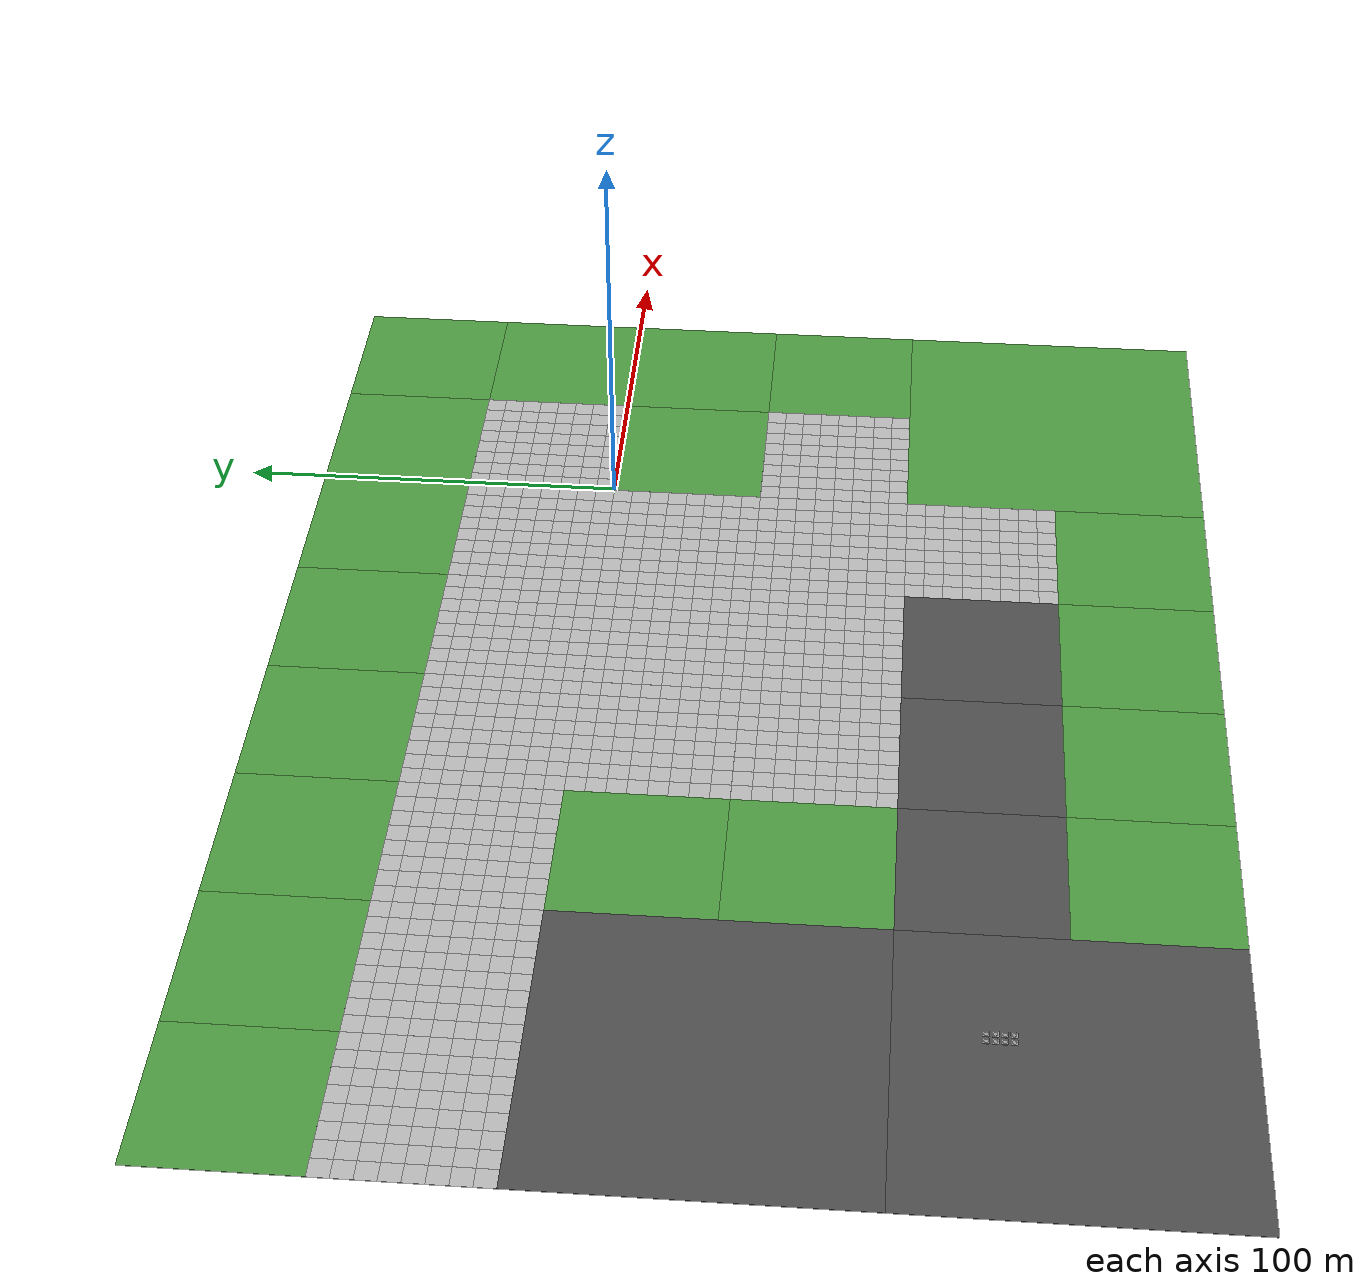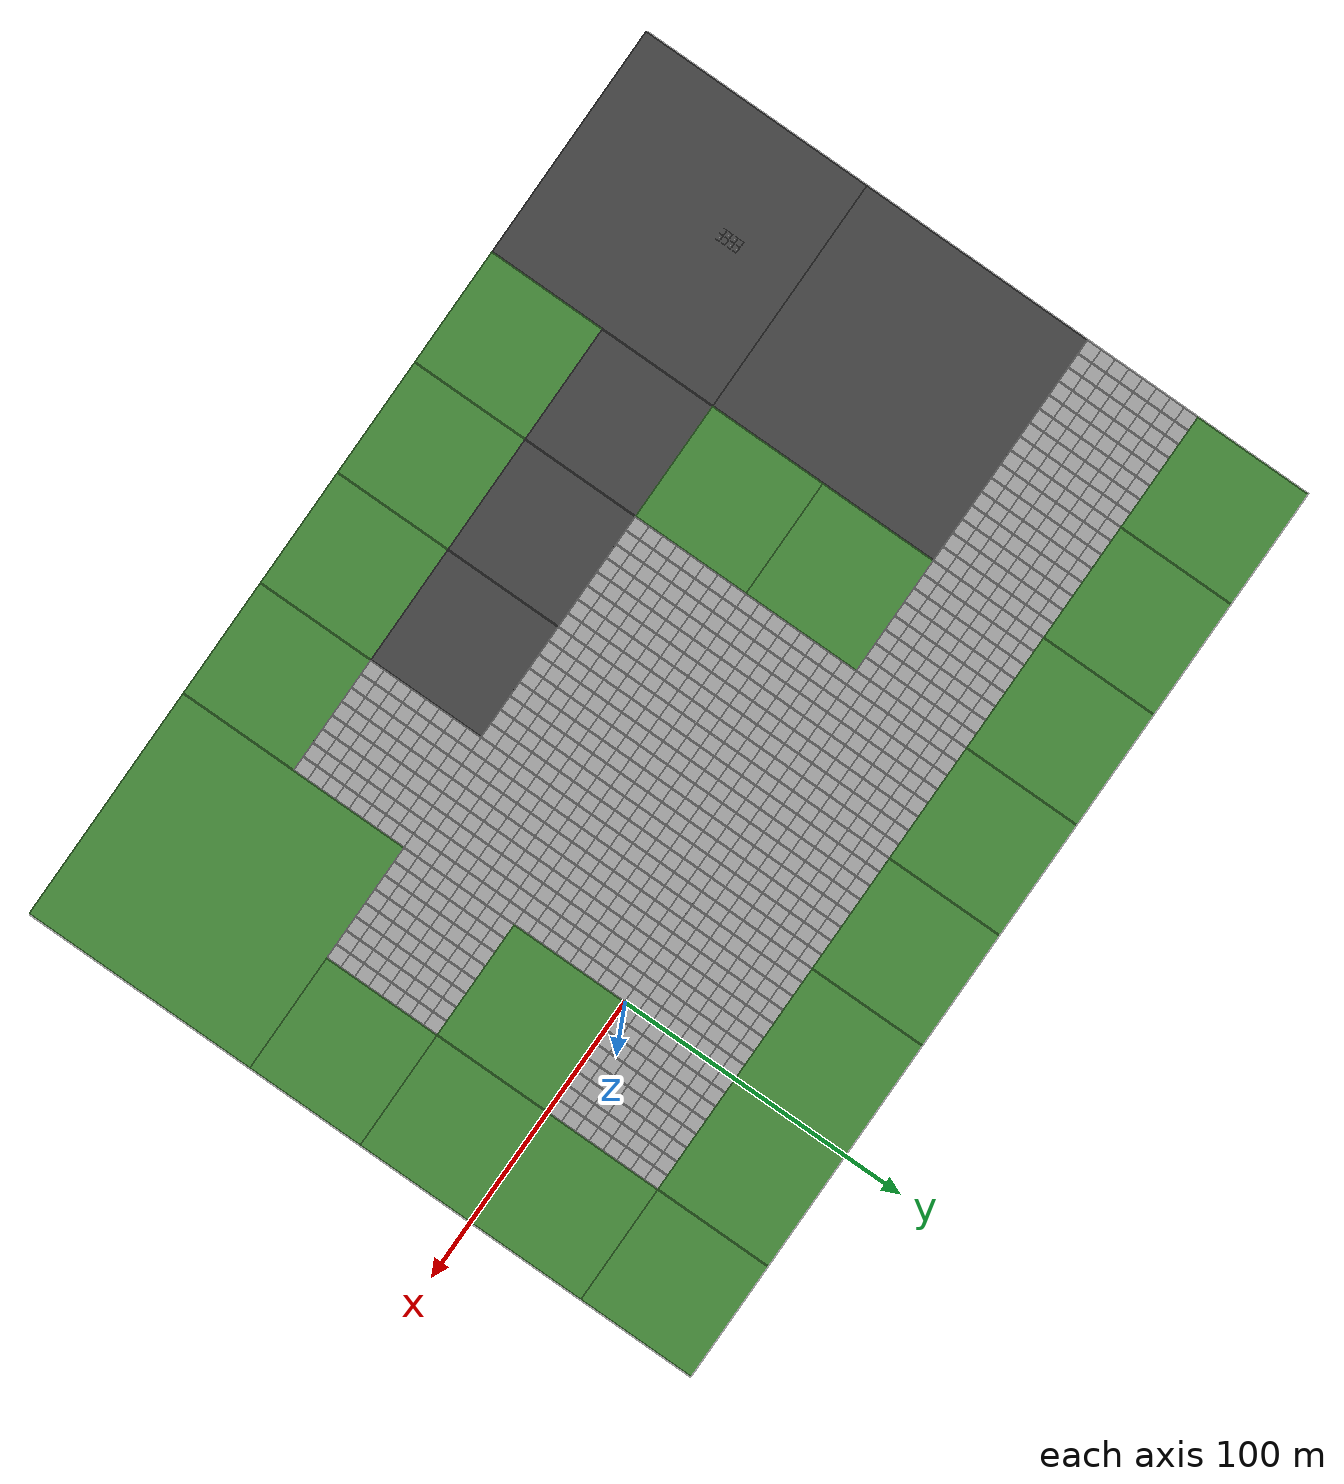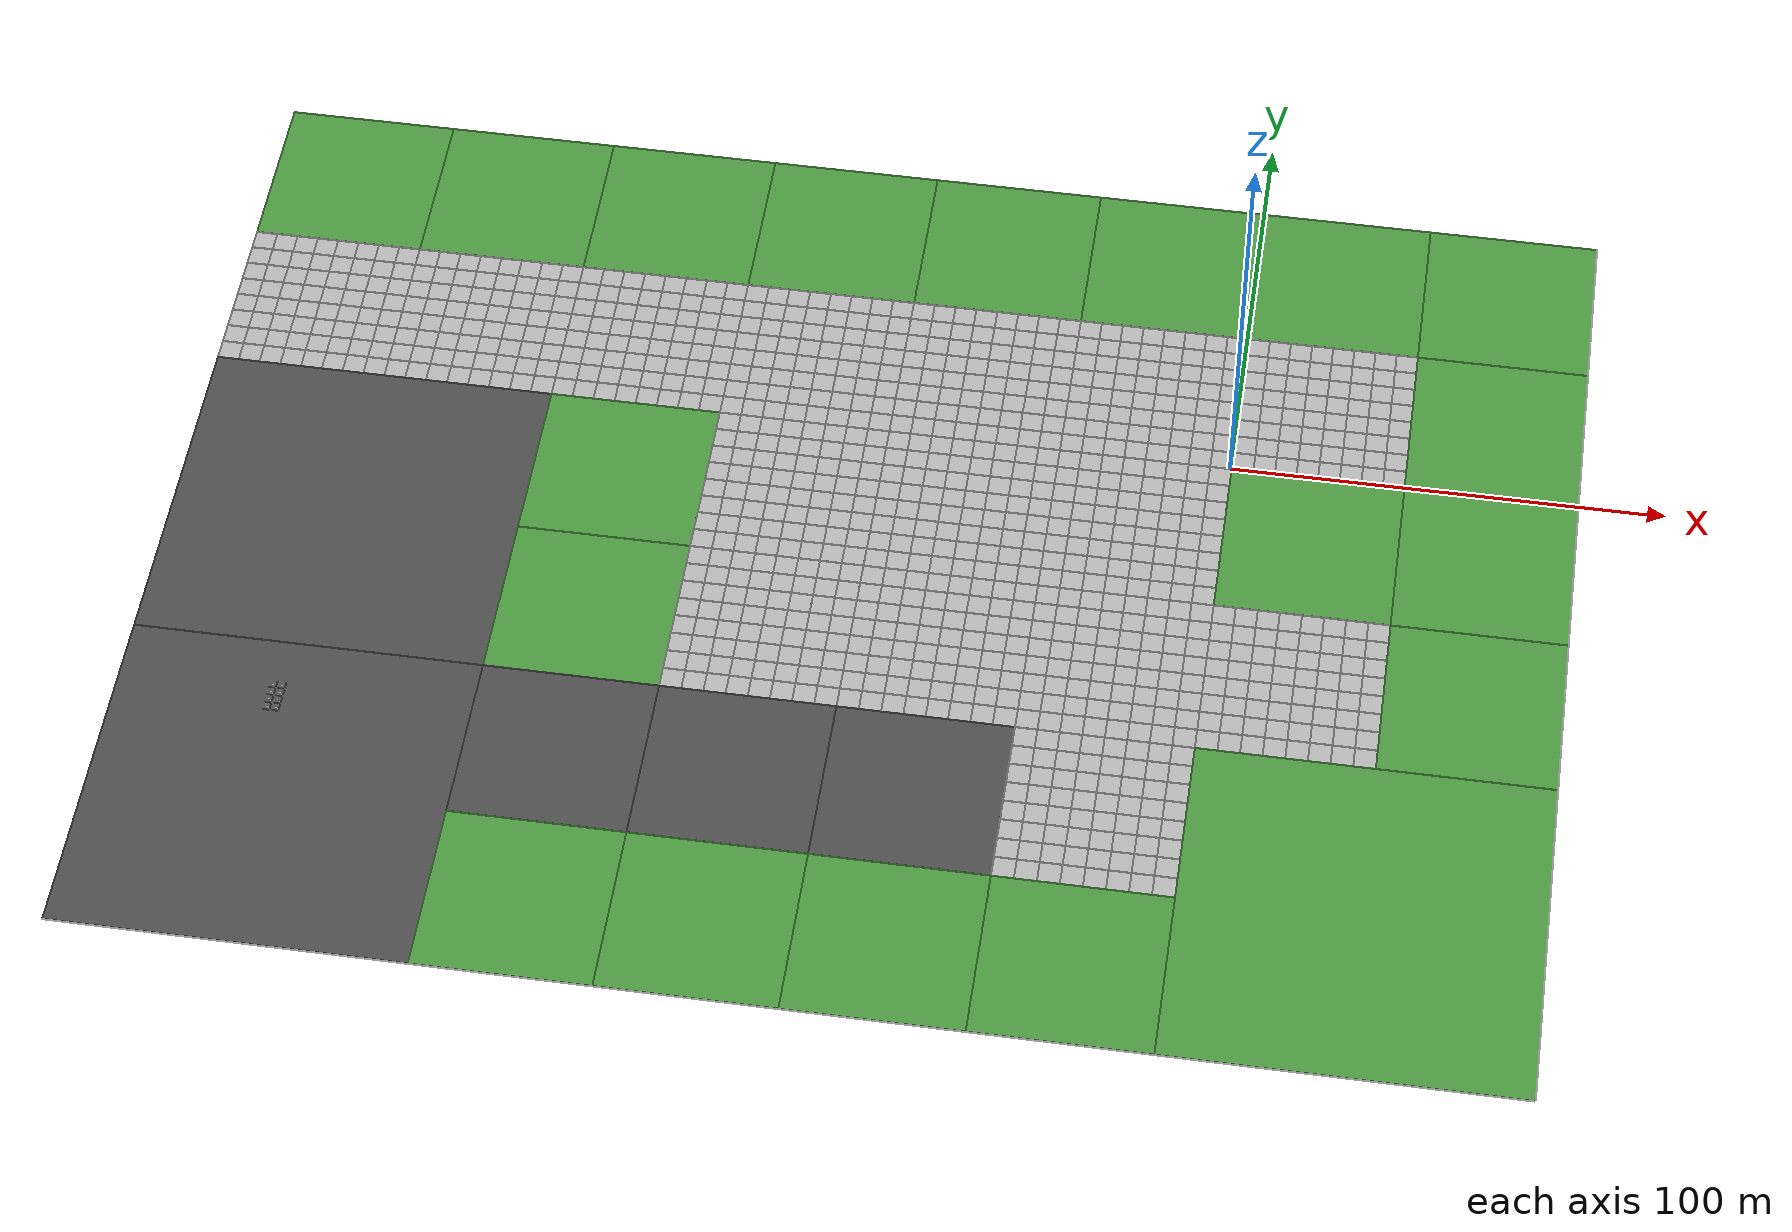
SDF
<sdf version="1.7">
 <world name="default">
  <light name="sun" type="directional">
   <cast_shadows>false</cast_shadows>
   <pose>0 0 400 0 -0 0</pose>
   <diffuse>0.8 0.8 0.8 1</diffuse>
   <specular>0.2 0.2 0.2 1</specular>
   <attenuation>
    <range>1000</range>
    <constant>0.9</constant>
    <linear>0.01</linear>
    <quadratic>0.001</quadratic>
   </attenuation>
   <direction>0.1 0.1 -1</direction>
   <spot><inner_angle>0</inner_angle><outer_angle>0</outer_angle><falloff>0</falloff></spot>
  </light>
  <gravity>0 0 -9.8</gravity>
  <magnetic_field>6e-06 2.3e-05 -4.2e-05</magnetic_field>
  <atmosphere type="adiabatic"/>
  <physics type="ode">
   <max_step_size>0.01</max_step_size>
   <real_time_factor>2</real_time_factor>
   <real_time_update_rate>100</real_time_update_rate>
  </physics>
  <scene><ambient>0.4 0.4 0.4 1</ambient><background>0.7 0.7 0.7 1</background><shadows>false</shadows></scene>
  <spherical_coordinates>
   <surface_model>EARTH_WGS84</surface_model>
   <latitude_deg>0</latitude_deg>
   <longitude_deg>0</longitude_deg>
   <elevation>0</elevation>
   <heading_deg>0</heading_deg>
  </spherical_coordinates>
  <model name="mud_plane_40x40">
   <model name="mud_plane_20x20">
    <model name="mud_plane">
     <static>1</static>
     <link name="link">
      <collision name="collision"><geometry><box><size>10 10 0.1</size></box></geometry></collision>
      <visual name="visual_1">
       <pose>-2.5 2.5 -0.05 0 -0 0</pose>
       <cast_shadows>0</cast_shadows>
       <geometry><box><size>5 5 0.1</size></box></geometry>
       <material>
        <script>
         <uri>model://mud_plane/materials/scripts</uri>
         <uri>model://mud_plane/materials/textures</uri>
         <name>vrc/mud</name>
        </script>
       </material>
      </visual>
      <visual name="visual_2">
       <pose>2.5 2.5 -0.05 0 -0 0</pose>
       <cast_shadows>0</cast_shadows>
       <geometry><box><size>5 5 0.1</size></box></geometry>
       <material>
        <script>
         <uri>model://mud_plane/materials/scripts</uri>
         <uri>model://mud_plane/materials/textures</uri>
         <name>vrc/mud</name>
        </script>
       </material>
      </visual>
      <visual name="visual_3">
       <pose>2.5 -2.5 -0.05 0 -0 0</pose>
       <cast_shadows>0</cast_shadows>
       <geometry><box><size>5 5 0.1</size></box></geometry>
       <material>
        <script>
         <uri>model://mud_plane/materials/scripts</uri>
         <uri>model://mud_plane/materials/textures</uri>
         <name>vrc/mud</name>
        </script>
       </material>
      </visual>
      <visual name="visual_4">
       <pose>-2.5 -2.5 -0.05 0 -0 0</pose>
       <cast_shadows>0</cast_shadows>
       <geometry><box><size>5 5 0.1</size></box></geometry>
       <material>
        <script>
         <uri>model://mud_plane/materials/scripts</uri>
         <uri>model://mud_plane/materials/textures</uri>
         <name>vrc/mud</name>
        </script>
       </material>
      </visual>
     </link>
     <pose>-4.99986 -4.99991 0 0 -0 0</pose>
    </model>
    <model name="mud_plane_0">
     <static>1</static>
     <link name="link">
      <collision name="collision"><geometry><box><size>10 10 0.1</size></box></geometry></collision>
      <visual name="visual_1">
       <pose>-2.5 2.5 -0.05 0 -0 0</pose>
       <cast_shadows>0</cast_shadows>
       <geometry><box><size>5 5 0.1</size></box></geometry>
       <material>
        <script>
         <uri>model://mud_plane/materials/scripts</uri>
         <uri>model://mud_plane/materials/textures</uri>
         <name>vrc/mud</name>
        </script>
       </material>
      </visual>
      <visual name="visual_2">
       <pose>2.5 2.5 -0.05 0 -0 0</pose>
       <cast_shadows>0</cast_shadows>
       <geometry><box><size>5 5 0.1</size></box></geometry>
       <material>
        <script>
         <uri>model://mud_plane/materials/scripts</uri>
         <uri>model://mud_plane/materials/textures</uri>
         <name>vrc/mud</name>
        </script>
       </material>
      </visual>
      <visual name="visual_3">
       <pose>2.5 -2.5 -0.05 0 -0 0</pose>
       <cast_shadows>0</cast_shadows>
       <geometry><box><size>5 5 0.1</size></box></geometry>
       <material>
        <script>
         <uri>model://mud_plane/materials/scripts</uri>
         <uri>model://mud_plane/materials/textures</uri>
         <name>vrc/mud</name>
        </script>
       </material>
      </visual>
      <visual name="visual_4">
       <pose>-2.5 -2.5 -0.05 0 -0 0</pose>
       <cast_shadows>0</cast_shadows>
       <geometry><box><size>5 5 0.1</size></box></geometry>
       <material>
        <script>
         <uri>model://mud_plane/materials/scripts</uri>
         <uri>model://mud_plane/materials/textures</uri>
         <name>vrc/mud</name>
        </script>
       </material>
      </visual>
     </link>
     <pose>-4.99946 4.99954 0 0 -0 0</pose>
    </model>
    <model name="mud_plane_1">
     <static>1</static>
     <link name="link">
      <collision name="collision"><geometry><box><size>10 10 0.1</size></box></geometry></collision>
      <visual name="visual_1">
       <pose>-2.5 2.5 -0.05 0 -0 0</pose>
       <cast_shadows>0</cast_shadows>
       <geometry><box><size>5 5 0.1</size></box></geometry>
       <material>
        <script>
         <uri>model://mud_plane/materials/scripts</uri>
         <uri>model://mud_plane/materials/textures</uri>
         <name>vrc/mud</name>
        </script>
       </material>
      </visual>
      <visual name="visual_2">
       <pose>2.5 2.5 -0.05 0 -0 0</pose>
       <cast_shadows>0</cast_shadows>
       <geometry><box><size>5 5 0.1</size></box></geometry>
       <material>
        <script>
         <uri>model://mud_plane/materials/scripts</uri>
         <uri>model://mud_plane/materials/textures</uri>
         <name>vrc/mud</name>
        </script>
       </material>
      </visual>
      <visual name="visual_3">
       <pose>2.5 -2.5 -0.05 0 -0 0</pose>
       <cast_shadows>0</cast_shadows>
       <geometry><box><size>5 5 0.1</size></box></geometry>
       <material>
        <script>
         <uri>model://mud_plane/materials/scripts</uri>
         <uri>model://mud_plane/materials/textures</uri>
         <name>vrc/mud</name>
        </script>
       </material>
      </visual>
      <visual name="visual_4">
       <pose>-2.5 -2.5 -0.05 0 -0 0</pose>
       <cast_shadows>0</cast_shadows>
       <geometry><box><size>5 5 0.1</size></box></geometry>
       <material>
        <script>
         <uri>model://mud_plane/materials/scripts</uri>
         <uri>model://mud_plane/materials/textures</uri>
         <name>vrc/mud</name>
        </script>
       </material>
      </visual>
     </link>
     <pose>4.99964 -4.99949 0 0 -0 0</pose>
    </model>
    <model name="mud_plane_2">
     <static>1</static>
     <link name="link">
      <collision name="collision"><geometry><box><size>10 10 0.1</size></box></geometry></collision>
      <visual name="visual_1">
       <pose>-2.5 2.5 -0.05 0 -0 0</pose>
       <cast_shadows>0</cast_shadows>
       <geometry><box><size>5 5 0.1</size></box></geometry>
       <material>
        <script>
         <uri>model://mud_plane/materials/scripts</uri>
         <uri>model://mud_plane/materials/textures</uri>
         <name>vrc/mud</name>
        </script>
       </material>
      </visual>
      <visual name="visual_2">
       <pose>2.5 2.5 -0.05 0 -0 0</pose>
       <cast_shadows>0</cast_shadows>
       <geometry><box><size>5 5 0.1</size></box></geometry>
       <material>
        <script>
         <uri>model://mud_plane/materials/scripts</uri>
         <uri>model://mud_plane/materials/textures</uri>
         <name>vrc/mud</name>
        </script>
       </material>
      </visual>
      <visual name="visual_3">
       <pose>2.5 -2.5 -0.05 0 -0 0</pose>
       <cast_shadows>0</cast_shadows>
       <geometry><box><size>5 5 0.1</size></box></geometry>
       <material>
        <script>
         <uri>model://mud_plane/materials/scripts</uri>
         <uri>model://mud_plane/materials/textures</uri>
         <name>vrc/mud</name>
        </script>
       </material>
      </visual>
      <visual name="visual_4">
       <pose>-2.5 -2.5 -0.05 0 -0 0</pose>
       <cast_shadows>0</cast_shadows>
       <geometry><box><size>5 5 0.1</size></box></geometry>
       <material>
        <script>
         <uri>model://mud_plane/materials/scripts</uri>
         <uri>model://mud_plane/materials/textures</uri>
         <name>vrc/mud</name>
        </script>
       </material>
      </visual>
     </link>
     <pose>4.99967 4.99986 0 0 -0 0</pose>
    </model>
    <static>0</static>
    <pose>-9.99895 9.99843 0 0 -0 0</pose>
   </model>
   <model name="mud_plane_20x20_0">
    <model name="mud_plane">
     <static>1</static>
     <link name="link">
      <collision name="collision"><geometry><box><size>10 10 0.1</size></box></geometry></collision>
      <visual name="visual_1">
       <pose>-2.5 2.5 -0.05 0 -0 0</pose>
       <cast_shadows>0</cast_shadows>
       <geometry><box><size>5 5 0.1</size></box></geometry>
       <material>
        <script>
         <uri>model://mud_plane/materials/scripts</uri>
         <uri>model://mud_plane/materials/textures</uri>
         <name>vrc/mud</name>
        </script>
       </material>
      </visual>
      <visual name="visual_2">
       <pose>2.5 2.5 -0.05 0 -0 0</pose>
       <cast_shadows>0</cast_shadows>
       <geometry><box><size>5 5 0.1</size></box></geometry>
       <material>
        <script>
         <uri>model://mud_plane/materials/scripts</uri>
         <uri>model://mud_plane/materials/textures</uri>
         <name>vrc/mud</name>
        </script>
       </material>
      </visual>
      <visual name="visual_3">
       <pose>2.5 -2.5 -0.05 0 -0 0</pose>
       <cast_shadows>0</cast_shadows>
       <geometry><box><size>5 5 0.1</size></box></geometry>
       <material>
        <script>
         <uri>model://mud_plane/materials/scripts</uri>
         <uri>model://mud_plane/materials/textures</uri>
         <name>vrc/mud</name>
        </script>
       </material>
      </visual>
      <visual name="visual_4">
       <pose>-2.5 -2.5 -0.05 0 -0 0</pose>
       <cast_shadows>0</cast_shadows>
       <geometry><box><size>5 5 0.1</size></box></geometry>
       <material>
        <script>
         <uri>model://mud_plane/materials/scripts</uri>
         <uri>model://mud_plane/materials/textures</uri>
         <name>vrc/mud</name>
        </script>
       </material>
      </visual>
     </link>
     <pose>-4.99986 -4.99991 0 0 -0 0</pose>
    </model>
    <model name="mud_plane_0">
     <static>1</static>
     <link name="link">
      <collision name="collision"><geometry><box><size>10 10 0.1</size></box></geometry></collision>
      <visual name="visual_1">
       <pose>-2.5 2.5 -0.05 0 -0 0</pose>
       <cast_shadows>0</cast_shadows>
       <geometry><box><size>5 5 0.1</size></box></geometry>
       <material>
        <script>
         <uri>model://mud_plane/materials/scripts</uri>
         <uri>model://mud_plane/materials/textures</uri>
         <name>vrc/mud</name>
        </script>
       </material>
      </visual>
      <visual name="visual_2">
       <pose>2.5 2.5 -0.05 0 -0 0</pose>
       <cast_shadows>0</cast_shadows>
       <geometry><box><size>5 5 0.1</size></box></geometry>
       <material>
        <script>
         <uri>model://mud_plane/materials/scripts</uri>
         <uri>model://mud_plane/materials/textures</uri>
         <name>vrc/mud</name>
        </script>
       </material>
      </visual>
      <visual name="visual_3">
       <pose>2.5 -2.5 -0.05 0 -0 0</pose>
       <cast_shadows>0</cast_shadows>
       <geometry><box><size>5 5 0.1</size></box></geometry>
       <material>
        <script>
         <uri>model://mud_plane/materials/scripts</uri>
         <uri>model://mud_plane/materials/textures</uri>
         <name>vrc/mud</name>
        </script>
       </material>
      </visual>
      <visual name="visual_4">
       <pose>-2.5 -2.5 -0.05 0 -0 0</pose>
       <cast_shadows>0</cast_shadows>
       <geometry><box><size>5 5 0.1</size></box></geometry>
       <material>
        <script>
         <uri>model://mud_plane/materials/scripts</uri>
         <uri>model://mud_plane/materials/textures</uri>
         <name>vrc/mud</name>
        </script>
       </material>
      </visual>
     </link>
     <pose>-4.99946 4.99954 0 0 -0 0</pose>
    </model>
    <model name="mud_plane_1">
     <static>1</static>
     <link name="link">
      <collision name="collision"><geometry><box><size>10 10 0.1</size></box></geometry></collision>
      <visual name="visual_1">
       <pose>-2.5 2.5 -0.05 0 -0 0</pose>
       <cast_shadows>0</cast_shadows>
       <geometry><box><size>5 5 0.1</size></box></geometry>
       <material>
        <script>
         <uri>model://mud_plane/materials/scripts</uri>
         <uri>model://mud_plane/materials/textures</uri>
         <name>vrc/mud</name>
        </script>
       </material>
      </visual>
      <visual name="visual_2">
       <pose>2.5 2.5 -0.05 0 -0 0</pose>
       <cast_shadows>0</cast_shadows>
       <geometry><box><size>5 5 0.1</size></box></geometry>
       <material>
        <script>
         <uri>model://mud_plane/materials/scripts</uri>
         <uri>model://mud_plane/materials/textures</uri>
         <name>vrc/mud</name>
        </script>
       </material>
      </visual>
      <visual name="visual_3">
       <pose>2.5 -2.5 -0.05 0 -0 0</pose>
       <cast_shadows>0</cast_shadows>
       <geometry><box><size>5 5 0.1</size></box></geometry>
       <material>
        <script>
         <uri>model://mud_plane/materials/scripts</uri>
         <uri>model://mud_plane/materials/textures</uri>
         <name>vrc/mud</name>
        </script>
       </material>
      </visual>
      <visual name="visual_4">
       <pose>-2.5 -2.5 -0.05 0 -0 0</pose>
       <cast_shadows>0</cast_shadows>
       <geometry><box><size>5 5 0.1</size></box></geometry>
       <material>
        <script>
         <uri>model://mud_plane/materials/scripts</uri>
         <uri>model://mud_plane/materials/textures</uri>
         <name>vrc/mud</name>
        </script>
       </material>
      </visual>
     </link>
     <pose>4.99964 -4.99949 0 0 -0 0</pose>
    </model>
    <model name="mud_plane_2">
     <static>1</static>
     <link name="link">
      <collision name="collision"><geometry><box><size>10 10 0.1</size></box></geometry></collision>
      <visual name="visual_1">
       <pose>-2.5 2.5 -0.05 0 -0 0</pose>
       <cast_shadows>0</cast_shadows>
       <geometry><box><size>5 5 0.1</size></box></geometry>
       <material>
        <script>
         <uri>model://mud_plane/materials/scripts</uri>
         <uri>model://mud_plane/materials/textures</uri>
         <name>vrc/mud</name>
        </script>
       </material>
      </visual>
      <visual name="visual_2">
       <pose>2.5 2.5 -0.05 0 -0 0</pose>
       <cast_shadows>0</cast_shadows>
       <geometry><box><size>5 5 0.1</size></box></geometry>
       <material>
        <script>
         <uri>model://mud_plane/materials/scripts</uri>
         <uri>model://mud_plane/materials/textures</uri>
         <name>vrc/mud</name>
        </script>
       </material>
      </visual>
      <visual name="visual_3">
       <pose>2.5 -2.5 -0.05 0 -0 0</pose>
       <cast_shadows>0</cast_shadows>
       <geometry><box><size>5 5 0.1</size></box></geometry>
       <material>
        <script>
         <uri>model://mud_plane/materials/scripts</uri>
         <uri>model://mud_plane/materials/textures</uri>
         <name>vrc/mud</name>
        </script>
       </material>
      </visual>
      <visual name="visual_4">
       <pose>-2.5 -2.5 -0.05 0 -0 0</pose>
       <cast_shadows>0</cast_shadows>
       <geometry><box><size>5 5 0.1</size></box></geometry>
       <material>
        <script>
         <uri>model://mud_plane/materials/scripts</uri>
         <uri>model://mud_plane/materials/textures</uri>
         <name>vrc/mud</name>
        </script>
       </material>
      </visual>
     </link>
     <pose>4.99967 4.99986 0 0 -0 0</pose>
    </model>
    <static>0</static>
    <pose>9.99933 9.9997 0 0 -0 0</pose>
   </model>
   <model name="mud_plane_20x20_1">
    <model name="mud_plane">
     <static>1</static>
     <link name="link">
      <collision name="collision"><geometry><box><size>10 10 0.1</size></box></geometry></collision>
      <visual name="visual_1">
       <pose>-2.5 2.5 -0.05 0 -0 0</pose>
       <cast_shadows>0</cast_shadows>
       <geometry><box><size>5 5 0.1</size></box></geometry>
       <material>
        <script>
         <uri>model://mud_plane/materials/scripts</uri>
         <uri>model://mud_plane/materials/textures</uri>
         <name>vrc/mud</name>
        </script>
       </material>
      </visual>
      <visual name="visual_2">
       <pose>2.5 2.5 -0.05 0 -0 0</pose>
       <cast_shadows>0</cast_shadows>
       <geometry><box><size>5 5 0.1</size></box></geometry>
       <material>
        <script>
         <uri>model://mud_plane/materials/scripts</uri>
         <uri>model://mud_plane/materials/textures</uri>
         <name>vrc/mud</name>
        </script>
       </material>
      </visual>
      <visual name="visual_3">
       <pose>2.5 -2.5 -0.05 0 -0 0</pose>
       <cast_shadows>0</cast_shadows>
       <geometry><box><size>5 5 0.1</size></box></geometry>
       <material>
        <script>
         <uri>model://mud_plane/materials/scripts</uri>
         <uri>model://mud_plane/materials/textures</uri>
         <name>vrc/mud</name>
        </script>
       </material>
      </visual>
      <visual name="visual_4">
       <pose>-2.5 -2.5 -0.05 0 -0 0</pose>
       <cast_shadows>0</cast_shadows>
       <geometry><box><size>5 5 0.1</size></box></geometry>
       <material>
        <script>
         <uri>model://mud_plane/materials/scripts</uri>
         <uri>model://mud_plane/materials/textures</uri>
         <name>vrc/mud</name>
        </script>
       </material>
      </visual>
     </link>
     <pose>-4.99986 -4.99991 0 0 -0 0</pose>
    </model>
    <model name="mud_plane_0">
     <static>1</static>
     <link name="link">
      <collision name="collision"><geometry><box><size>10 10 0.1</size></box></geometry></collision>
      <visual name="visual_1">
       <pose>-2.5 2.5 -0.05 0 -0 0</pose>
       <cast_shadows>0</cast_shadows>
       <geometry><box><size>5 5 0.1</size></box></geometry>
       <material>
        <script>
         <uri>model://mud_plane/materials/scripts</uri>
         <uri>model://mud_plane/materials/textures</uri>
         <name>vrc/mud</name>
        </script>
       </material>
      </visual>
      <visual name="visual_2">
       <pose>2.5 2.5 -0.05 0 -0 0</pose>
       <cast_shadows>0</cast_shadows>
       <geometry><box><size>5 5 0.1</size></box></geometry>
       <material>
        <script>
         <uri>model://mud_plane/materials/scripts</uri>
         <uri>model://mud_plane/materials/textures</uri>
         <name>vrc/mud</name>
        </script>
       </material>
      </visual>
      <visual name="visual_3">
       <pose>2.5 -2.5 -0.05 0 -0 0</pose>
       <cast_shadows>0</cast_shadows>
       <geometry><box><size>5 5 0.1</size></box></geometry>
       <material>
        <script>
         <uri>model://mud_plane/materials/scripts</uri>
         <uri>model://mud_plane/materials/textures</uri>
         <name>vrc/mud</name>
        </script>
       </material>
      </visual>
      <visual name="visual_4">
       <pose>-2.5 -2.5 -0.05 0 -0 0</pose>
       <cast_shadows>0</cast_shadows>
       <geometry><box><size>5 5 0.1</size></box></geometry>
       <material>
        <script>
         <uri>model://mud_plane/materials/scripts</uri>
         <uri>model://mud_plane/materials/textures</uri>
         <name>vrc/mud</name>
        </script>
       </material>
      </visual>
     </link>
     <pose>-4.99946 4.99954 0 0 -0 0</pose>
    </model>
    <model name="mud_plane_1">
     <static>1</static>
     <link name="link">
      <collision name="collision"><geometry><box><size>10 10 0.1</size></box></geometry></collision>
      <visual name="visual_1">
       <pose>-2.5 2.5 -0.05 0 -0 0</pose>
       <cast_shadows>0</cast_shadows>
       <geometry><box><size>5 5 0.1</size></box></geometry>
       <material>
        <script>
         <uri>model://mud_plane/materials/scripts</uri>
         <uri>model://mud_plane/materials/textures</uri>
         <name>vrc/mud</name>
        </script>
       </material>
      </visual>
      <visual name="visual_2">
       <pose>2.5 2.5 -0.05 0 -0 0</pose>
       <cast_shadows>0</cast_shadows>
       <geometry><box><size>5 5 0.1</size></box></geometry>
       <material>
        <script>
         <uri>model://mud_plane/materials/scripts</uri>
         <uri>model://mud_plane/materials/textures</uri>
         <name>vrc/mud</name>
        </script>
       </material>
      </visual>
      <visual name="visual_3">
       <pose>2.5 -2.5 -0.05 0 -0 0</pose>
       <cast_shadows>0</cast_shadows>
       <geometry><box><size>5 5 0.1</size></box></geometry>
       <material>
        <script>
         <uri>model://mud_plane/materials/scripts</uri>
         <uri>model://mud_plane/materials/textures</uri>
         <name>vrc/mud</name>
        </script>
       </material>
      </visual>
      <visual name="visual_4">
       <pose>-2.5 -2.5 -0.05 0 -0 0</pose>
       <cast_shadows>0</cast_shadows>
       <geometry><box><size>5 5 0.1</size></box></geometry>
       <material>
        <script>
         <uri>model://mud_plane/materials/scripts</uri>
         <uri>model://mud_plane/materials/textures</uri>
         <name>vrc/mud</name>
        </script>
       </material>
      </visual>
     </link>
     <pose>4.99964 -4.99949 0 0 -0 0</pose>
    </model>
    <model name="mud_plane_2">
     <static>1</static>
     <link name="link">
      <collision name="collision"><geometry><box><size>10 10 0.1</size></box></geometry></collision>
      <visual name="visual_1">
       <pose>-2.5 2.5 -0.05 0 -0 0</pose>
       <cast_shadows>0</cast_shadows>
       <geometry><box><size>5 5 0.1</size></box></geometry>
       <material>
        <script>
         <uri>model://mud_plane/materials/scripts</uri>
         <uri>model://mud_plane/materials/textures</uri>
         <name>vrc/mud</name>
        </script>
       </material>
      </visual>
      <visual name="visual_2">
       <pose>2.5 2.5 -0.05 0 -0 0</pose>
       <cast_shadows>0</cast_shadows>
       <geometry><box><size>5 5 0.1</size></box></geometry>
       <material>
        <script>
         <uri>model://mud_plane/materials/scripts</uri>
         <uri>model://mud_plane/materials/textures</uri>
         <name>vrc/mud</name>
        </script>
       </material>
      </visual>
      <visual name="visual_3">
       <pose>2.5 -2.5 -0.05 0 -0 0</pose>
       <cast_shadows>0</cast_shadows>
       <geometry><box><size>5 5 0.1</size></box></geometry>
       <material>
        <script>
         <uri>model://mud_plane/materials/scripts</uri>
         <uri>model://mud_plane/materials/textures</uri>
         <name>vrc/mud</name>
        </script>
       </material>
      </visual>
      <visual name="visual_4">
       <pose>-2.5 -2.5 -0.05 0 -0 0</pose>
       <cast_shadows>0</cast_shadows>
       <geometry><box><size>5 5 0.1</size></box></geometry>
       <material>
        <script>
         <uri>model://mud_plane/materials/scripts</uri>
         <uri>model://mud_plane/materials/textures</uri>
         <name>vrc/mud</name>
        </script>
       </material>
      </visual>
     </link>
     <pose>4.99967 4.99986 0 0 -0 0</pose>
    </model>
    <static>0</static>
    <pose>9.9993 -9.99877 0 0 -0 0</pose>
   </model>
   <model name="mud_plane_20x20_2">
    <model name="mud_plane">
     <static>1</static>
     <link name="link">
      <collision name="collision"><geometry><box><size>10 10 0.1</size></box></geometry></collision>
      <visual name="visual_1">
       <pose>-2.5 2.5 -0.05 0 -0 0</pose>
       <cast_shadows>0</cast_shadows>
       <geometry><box><size>5 5 0.1</size></box></geometry>
       <material>
        <script>
         <uri>model://mud_plane/materials/scripts</uri>
         <uri>model://mud_plane/materials/textures</uri>
         <name>vrc/mud</name>
        </script>
       </material>
      </visual>
      <visual name="visual_2">
       <pose>2.5 2.5 -0.05 0 -0 0</pose>
       <cast_shadows>0</cast_shadows>
       <geometry><box><size>5 5 0.1</size></box></geometry>
       <material>
        <script>
         <uri>model://mud_plane/materials/scripts</uri>
         <uri>model://mud_plane/materials/textures</uri>
         <name>vrc/mud</name>
        </script>
       </material>
      </visual>
      <visual name="visual_3">
       <pose>2.5 -2.5 -0.05 0 -0 0</pose>
       <cast_shadows>0</cast_shadows>
       <geometry><box><size>5 5 0.1</size></box></geometry>
       <material>
        <script>
         <uri>model://mud_plane/materials/scripts</uri>
         <uri>model://mud_plane/materials/textures</uri>
         <name>vrc/mud</name>
        </script>
       </material>
      </visual>
      <visual name="visual_4">
       <pose>-2.5 -2.5 -0.05 0 -0 0</pose>
       <cast_shadows>0</cast_shadows>
       <geometry><box><size>5 5 0.1</size></box></geometry>
       <material>
        <script>
         <uri>model://mud_plane/materials/scripts</uri>
         <uri>model://mud_plane/materials/textures</uri>
         <name>vrc/mud</name>
        </script>
       </material>
      </visual>
     </link>
     <pose>-4.99986 -4.99991 0 0 -0 0</pose>
    </model>
    <model name="mud_plane_0">
     <static>1</static>
     <link name="link">
      <collision name="collision"><geometry><box><size>10 10 0.1</size></box></geometry></collision>
      <visual name="visual_1">
       <pose>-2.5 2.5 -0.05 0 -0 0</pose>
       <cast_shadows>0</cast_shadows>
       <geometry><box><size>5 5 0.1</size></box></geometry>
       <material>
        <script>
         <uri>model://mud_plane/materials/scripts</uri>
         <uri>model://mud_plane/materials/textures</uri>
         <name>vrc/mud</name>
        </script>
       </material>
      </visual>
      <visual name="visual_2">
       <pose>2.5 2.5 -0.05 0 -0 0</pose>
       <cast_shadows>0</cast_shadows>
       <geometry><box><size>5 5 0.1</size></box></geometry>
       <material>
        <script>
         <uri>model://mud_plane/materials/scripts</uri>
         <uri>model://mud_plane/materials/textures</uri>
         <name>vrc/mud</name>
        </script>
       </material>
      </visual>
      <visual name="visual_3">
       <pose>2.5 -2.5 -0.05 0 -0 0</pose>
       <cast_shadows>0</cast_shadows>
       <geometry><box><size>5 5 0.1</size></box></geometry>
       <material>
        <script>
         <uri>model://mud_plane/materials/scripts</uri>
         <uri>model://mud_plane/materials/textures</uri>
         <name>vrc/mud</name>
        </script>
       </material>
      </visual>
      <visual name="visual_4">
       <pose>-2.5 -2.5 -0.05 0 -0 0</pose>
       <cast_shadows>0</cast_shadows>
       <geometry><box><size>5 5 0.1</size></box></geometry>
       <material>
        <script>
         <uri>model://mud_plane/materials/scripts</uri>
         <uri>model://mud_plane/materials/textures</uri>
         <name>vrc/mud</name>
        </script>
       </material>
      </visual>
     </link>
     <pose>-4.99946 4.99954 0 0 -0 0</pose>
    </model>
    <model name="mud_plane_1">
     <static>1</static>
     <link name="link">
      <collision name="collision"><geometry><box><size>10 10 0.1</size></box></geometry></collision>
      <visual name="visual_1">
       <pose>-2.5 2.5 -0.05 0 -0 0</pose>
       <cast_shadows>0</cast_shadows>
       <geometry><box><size>5 5 0.1</size></box></geometry>
       <material>
        <script>
         <uri>model://mud_plane/materials/scripts</uri>
         <uri>model://mud_plane/materials/textures</uri>
         <name>vrc/mud</name>
        </script>
       </material>
      </visual>
      <visual name="visual_2">
       <pose>2.5 2.5 -0.05 0 -0 0</pose>
       <cast_shadows>0</cast_shadows>
       <geometry><box><size>5 5 0.1</size></box></geometry>
       <material>
        <script>
         <uri>model://mud_plane/materials/scripts</uri>
         <uri>model://mud_plane/materials/textures</uri>
         <name>vrc/mud</name>
        </script>
       </material>
      </visual>
      <visual name="visual_3">
       <pose>2.5 -2.5 -0.05 0 -0 0</pose>
       <cast_shadows>0</cast_shadows>
       <geometry><box><size>5 5 0.1</size></box></geometry>
       <material>
        <script>
         <uri>model://mud_plane/materials/scripts</uri>
         <uri>model://mud_plane/materials/textures</uri>
         <name>vrc/mud</name>
        </script>
       </material>
      </visual>
      <visual name="visual_4">
       <pose>-2.5 -2.5 -0.05 0 -0 0</pose>
       <cast_shadows>0</cast_shadows>
       <geometry><box><size>5 5 0.1</size></box></geometry>
       <material>
        <script>
         <uri>model://mud_plane/materials/scripts</uri>
         <uri>model://mud_plane/materials/textures</uri>
         <name>vrc/mud</name>
        </script>
       </material>
      </visual>
     </link>
     <pose>4.99964 -4.99949 0 0 -0 0</pose>
    </model>
    <model name="mud_plane_2">
     <static>1</static>
     <link name="link">
      <collision name="collision"><geometry><box><size>10 10 0.1</size></box></geometry></collision>
      <visual name="visual_1">
       <pose>-2.5 2.5 -0.05 0 -0 0</pose>
       <cast_shadows>0</cast_shadows>
       <geometry><box><size>5 5 0.1</size></box></geometry>
       <material>
        <script>
         <uri>model://mud_plane/materials/scripts</uri>
         <uri>model://mud_plane/materials/textures</uri>
         <name>vrc/mud</name>
        </script>
       </material>
      </visual>
      <visual name="visual_2">
       <pose>2.5 2.5 -0.05 0 -0 0</pose>
       <cast_shadows>0</cast_shadows>
       <geometry><box><size>5 5 0.1</size></box></geometry>
       <material>
        <script>
         <uri>model://mud_plane/materials/scripts</uri>
         <uri>model://mud_plane/materials/textures</uri>
         <name>vrc/mud</name>
        </script>
       </material>
      </visual>
      <visual name="visual_3">
       <pose>2.5 -2.5 -0.05 0 -0 0</pose>
       <cast_shadows>0</cast_shadows>
       <geometry><box><size>5 5 0.1</size></box></geometry>
       <material>
        <script>
         <uri>model://mud_plane/materials/scripts</uri>
         <uri>model://mud_plane/materials/textures</uri>
         <name>vrc/mud</name>
        </script>
       </material>
      </visual>
      <visual name="visual_4">
       <pose>-2.5 -2.5 -0.05 0 -0 0</pose>
       <cast_shadows>0</cast_shadows>
       <geometry><box><size>5 5 0.1</size></box></geometry>
       <material>
        <script>
         <uri>model://mud_plane/materials/scripts</uri>
         <uri>model://mud_plane/materials/textures</uri>
         <name>vrc/mud</name>
        </script>
       </material>
      </visual>
     </link>
     <pose>4.99967 4.99986 0 0 -0 0</pose>
    </model>
    <static>0</static>
    <pose>-9.99969 -9.99935 0 0 -0 0</pose>
   </model>
   <static>0</static>
   <pose>20 20 0 0 -0 0</pose>
  </model>
  <model name="mud_plane_40x40_0">
   <model name="mud_plane_20x20">
    <model name="mud_plane">
     <static>1</static>
     <link name="link">
      <collision name="collision"><geometry><box><size>10 10 0.1</size></box></geometry></collision>
      <visual name="visual_1">
       <pose>-2.5 2.5 -0.05 0 -0 0</pose>
       <cast_shadows>0</cast_shadows>
       <geometry><box><size>5 5 0.1</size></box></geometry>
       <material>
        <script>
         <uri>model://mud_plane/materials/scripts</uri>
         <uri>model://mud_plane/materials/textures</uri>
         <name>vrc/mud</name>
        </script>
       </material>
      </visual>
      <visual name="visual_2">
       <pose>2.5 2.5 -0.05 0 -0 0</pose>
       <cast_shadows>0</cast_shadows>
       <geometry><box><size>5 5 0.1</size></box></geometry>
       <material>
        <script>
         <uri>model://mud_plane/materials/scripts</uri>
         <uri>model://mud_plane/materials/textures</uri>
         <name>vrc/mud</name>
        </script>
       </material>
      </visual>
      <visual name="visual_3">
       <pose>2.5 -2.5 -0.05 0 -0 0</pose>
       <cast_shadows>0</cast_shadows>
       <geometry><box><size>5 5 0.1</size></box></geometry>
       <material>
        <script>
         <uri>model://mud_plane/materials/scripts</uri>
         <uri>model://mud_plane/materials/textures</uri>
         <name>vrc/mud</name>
        </script>
       </material>
      </visual>
      <visual name="visual_4">
       <pose>-2.5 -2.5 -0.05 0 -0 0</pose>
       <cast_shadows>0</cast_shadows>
       <geometry><box><size>5 5 0.1</size></box></geometry>
       <material>
        <script>
         <uri>model://mud_plane/materials/scripts</uri>
         <uri>model://mud_plane/materials/textures</uri>
         <name>vrc/mud</name>
        </script>
       </material>
      </visual>
     </link>
     <pose>-4.99986 -4.99991 0 0 -0 0</pose>
    </model>
    <model name="mud_plane_0">
     <static>1</static>
     <link name="link">
      <collision name="collision"><geometry><box><size>10 10 0.1</size></box></geometry></collision>
      <visual name="visual_1">
       <pose>-2.5 2.5 -0.05 0 -0 0</pose>
       <cast_shadows>0</cast_shadows>
       <geometry><box><size>5 5 0.1</size></box></geometry>
       <material>
        <script>
         <uri>model://mud_plane/materials/scripts</uri>
         <uri>model://mud_plane/materials/textures</uri>
         <name>vrc/mud</name>
        </script>
       </material>
      </visual>
      <visual name="visual_2">
       <pose>2.5 2.5 -0.05 0 -0 0</pose>
       <cast_shadows>0</cast_shadows>
       <geometry><box><size>5 5 0.1</size></box></geometry>
       <material>
        <script>
         <uri>model://mud_plane/materials/scripts</uri>
         <uri>model://mud_plane/materials/textures</uri>
         <name>vrc/mud</name>
        </script>
       </material>
      </visual>
      <visual name="visual_3">
       <pose>2.5 -2.5 -0.05 0 -0 0</pose>
       <cast_shadows>0</cast_shadows>
       <geometry><box><size>5 5 0.1</size></box></geometry>
       <material>
        <script>
         <uri>model://mud_plane/materials/scripts</uri>
         <uri>model://mud_plane/materials/textures</uri>
         <name>vrc/mud</name>
        </script>
       </material>
      </visual>
      <visual name="visual_4">
       <pose>-2.5 -2.5 -0.05 0 -0 0</pose>
       <cast_shadows>0</cast_shadows>
       <geometry><box><size>5 5 0.1</size></box></geometry>
       <material>
        <script>
         <uri>model://mud_plane/materials/scripts</uri>
         <uri>model://mud_plane/materials/textures</uri>
         <name>vrc/mud</name>
        </script>
       </material>
      </visual>
     </link>
     <pose>-4.99946 4.99954 0 0 -0 0</pose>
    </model>
    <model name="mud_plane_1">
     <static>1</static>
     <link name="link">
      <collision name="collision"><geometry><box><size>10 10 0.1</size></box></geometry></collision>
      <visual name="visual_1">
       <pose>-2.5 2.5 -0.05 0 -0 0</pose>
       <cast_shadows>0</cast_shadows>
       <geometry><box><size>5 5 0.1</size></box></geometry>
       <material>
        <script>
         <uri>model://mud_plane/materials/scripts</uri>
         <uri>model://mud_plane/materials/textures</uri>
         <name>vrc/mud</name>
        </script>
       </material>
      </visual>
      <visual name="visual_2">
       <pose>2.5 2.5 -0.05 0 -0 0</pose>
       <cast_shadows>0</cast_shadows>
       <geometry><box><size>5 5 0.1</size></box></geometry>
       <material>
        <script>
         <uri>model://mud_plane/materials/scripts</uri>
         <uri>model://mud_plane/materials/textures</uri>
         <name>vrc/mud</name>
        </script>
       </material>
      </visual>
      <visual name="visual_3">
       <pose>2.5 -2.5 -0.05 0 -0 0</pose>
       <cast_shadows>0</cast_shadows>
       <geometry><box><size>5 5 0.1</size></box></geometry>
       <material>
        <script>
         <uri>model://mud_plane/materials/scripts</uri>
         <uri>model://mud_plane/materials/textures</uri>
         <name>vrc/mud</name>
        </script>
       </material>
      </visual>
      <visual name="visual_4">
       <pose>-2.5 -2.5 -0.05 0 -0 0</pose>
       <cast_shadows>0</cast_shadows>
       <geometry><box><size>5 5 0.1</size></box></geometry>
       <material>
        <script>
         <uri>model://mud_plane/materials/scripts</uri>
         <uri>model://mud_plane/materials/textures</uri>
         <name>vrc/mud</name>
        </script>
       </material>
      </visual>
     </link>
     <pose>4.99964 -4.99949 0 0 -0 0</pose>
    </model>
    <model name="mud_plane_2">
     <static>1</static>
     <link name="link">
      <collision name="collision"><geometry><box><size>10 10 0.1</size></box></geometry></collision>
      <visual name="visual_1">
       <pose>-2.5 2.5 -0.05 0 -0 0</pose>
       <cast_shadows>0</cast_shadows>
       <geometry><box><size>5 5 0.1</size></box></geometry>
       <material>
        <script>
         <uri>model://mud_plane/materials/scripts</uri>
         <uri>model://mud_plane/materials/textures</uri>
         <name>vrc/mud</name>
        </script>
       </material>
      </visual>
      <visual name="visual_2">
       <pose>2.5 2.5 -0.05 0 -0 0</pose>
       <cast_shadows>0</cast_shadows>
       <geometry><box><size>5 5 0.1</size></box></geometry>
       <material>
        <script>
         <uri>model://mud_plane/materials/scripts</uri>
         <uri>model://mud_plane/materials/textures</uri>
         <name>vrc/mud</name>
        </script>
       </material>
      </visual>
      <visual name="visual_3">
       <pose>2.5 -2.5 -0.05 0 -0 0</pose>
       <cast_shadows>0</cast_shadows>
       <geometry><box><size>5 5 0.1</size></box></geometry>
       <material>
        <script>
         <uri>model://mud_plane/materials/scripts</uri>
         <uri>model://mud_plane/materials/textures</uri>
         <name>vrc/mud</name>
        </script>
       </material>
      </visual>
      <visual name="visual_4">
       <pose>-2.5 -2.5 -0.05 0 -0 0</pose>
       <cast_shadows>0</cast_shadows>
       <geometry><box><size>5 5 0.1</size></box></geometry>
       <material>
        <script>
         <uri>model://mud_plane/materials/scripts</uri>
         <uri>model://mud_plane/materials/textures</uri>
         <name>vrc/mud</name>
        </script>
       </material>
      </visual>
     </link>
     <pose>4.99967 4.99986 0 0 -0 0</pose>
    </model>
    <static>0</static>
    <pose>-9.99895 9.99843 0 0 -0 0</pose>
   </model>
   <model name="mud_plane_20x20_0">
    <model name="mud_plane">
     <static>1</static>
     <link name="link">
      <collision name="collision"><geometry><box><size>10 10 0.1</size></box></geometry></collision>
      <visual name="visual_1">
       <pose>-2.5 2.5 -0.05 0 -0 0</pose>
       <cast_shadows>0</cast_shadows>
       <geometry><box><size>5 5 0.1</size></box></geometry>
       <material>
        <script>
         <uri>model://mud_plane/materials/scripts</uri>
         <uri>model://mud_plane/materials/textures</uri>
         <name>vrc/mud</name>
        </script>
       </material>
      </visual>
      <visual name="visual_2">
       <pose>2.5 2.5 -0.05 0 -0 0</pose>
       <cast_shadows>0</cast_shadows>
       <geometry><box><size>5 5 0.1</size></box></geometry>
       <material>
        <script>
         <uri>model://mud_plane/materials/scripts</uri>
         <uri>model://mud_plane/materials/textures</uri>
         <name>vrc/mud</name>
        </script>
       </material>
      </visual>
      <visual name="visual_3">
       <pose>2.5 -2.5 -0.05 0 -0 0</pose>
       <cast_shadows>0</cast_shadows>
       <geometry><box><size>5 5 0.1</size></box></geometry>
       <material>
        <script>
         <uri>model://mud_plane/materials/scripts</uri>
         <uri>model://mud_plane/materials/textures</uri>
         <name>vrc/mud</name>
        </script>
       </material>
      </visual>
      <visual name="visual_4">
       <pose>-2.5 -2.5 -0.05 0 -0 0</pose>
       <cast_shadows>0</cast_shadows>
       <geometry><box><size>5 5 0.1</size></box></geometry>
       <material>
        <script>
         <uri>model://mud_plane/materials/scripts</uri>
         <uri>model://mud_plane/materials/textures</uri>
         <name>vrc/mud</name>
        </script>
       </material>
      </visual>
     </link>
     <pose>-4.99986 -4.99991 0 0 -0 0</pose>
    </model>
    <model name="mud_plane_0">
     <static>1</static>
     <link name="link">
      <collision name="collision"><geometry><box><size>10 10 0.1</size></box></geometry></collision>
      <visual name="visual_1">
       <pose>-2.5 2.5 -0.05 0 -0 0</pose>
       <cast_shadows>0</cast_shadows>
       <geometry><box><size>5 5 0.1</size></box></geometry>
       <material>
        <script>
         <uri>model://mud_plane/materials/scripts</uri>
         <uri>model://mud_plane/materials/textures</uri>
         <name>vrc/mud</name>
        </script>
       </material>
      </visual>
      <visual name="visual_2">
       <pose>2.5 2.5 -0.05 0 -0 0</pose>
       <cast_shadows>0</cast_shadows>
       <geometry><box><size>5 5 0.1</size></box></geometry>
       <material>
        <script>
         <uri>model://mud_plane/materials/scripts</uri>
         <uri>model://mud_plane/materials/textures</uri>
         <name>vrc/mud</name>
        </script>
       </material>
      </visual>
      <visual name="visual_3">
       <pose>2.5 -2.5 -0.05 0 -0 0</pose>
       <cast_shadows>0</cast_shadows>
       <geometry><box><size>5 5 0.1</size></box></geometry>
       <material>
        <script>
         <uri>model://mud_plane/materials/scripts</uri>
         <uri>model://mud_plane/materials/textures</uri>
         <name>vrc/mud</name>
        </script>
       </material>
      </visual>
      <visual name="visual_4">
       <pose>-2.5 -2.5 -0.05 0 -0 0</pose>
       <cast_shadows>0</cast_shadows>
       <geometry><box><size>5 5 0.1</size></box></geometry>
       <material>
        <script>
         <uri>model://mud_plane/materials/scripts</uri>
         <uri>model://mud_plane/materials/textures</uri>
         <name>vrc/mud</name>
        </script>
       </material>
      </visual>
     </link>
     <pose>-4.99946 4.99954 0 0 -0 0</pose>
    </model>
    <model name="mud_plane_1">
     <static>1</static>
     <link name="link">
      <collision name="collision"><geometry><box><size>10 10 0.1</size></box></geometry></collision>
      <visual name="visual_1">
       <pose>-2.5 2.5 -0.05 0 -0 0</pose>
       <cast_shadows>0</cast_shadows>
       <geometry><box><size>5 5 0.1</size></box></geometry>
       <material>
        <script>
         <uri>model://mud_plane/materials/scripts</uri>
         <uri>model://mud_plane/materials/textures</uri>
         <name>vrc/mud</name>
        </script>
       </material>
      </visual>
      <visual name="visual_2">
       <pose>2.5 2.5 -0.05 0 -0 0</pose>
       <cast_shadows>0</cast_shadows>
       <geometry><box><size>5 5 0.1</size></box></geometry>
       <material>
        <script>
         <uri>model://mud_plane/materials/scripts</uri>
         <uri>model://mud_plane/materials/textures</uri>
         <name>vrc/mud</name>
        </script>
       </material>
      </visual>
      <visual name="visual_3">
       <pose>2.5 -2.5 -0.05 0 -0 0</pose>
       <cast_shadows>0</cast_shadows>
       <geometry><box><size>5 5 0.1</size></box></geometry>
       <material>
        <script>
         <uri>model://mud_plane/materials/scripts</uri>
         <uri>model://mud_plane/materials/textures</uri>
         <name>vrc/mud</name>
        </script>
       </material>
      </visual>
      <visual name="visual_4">
       <pose>-2.5 -2.5 -0.05 0 -0 0</pose>
       <cast_shadows>0</cast_shadows>
       <geometry><box><size>5 5 0.1</size></box></geometry>
       <material>
        <script>
         <uri>model://mud_plane/materials/scripts</uri>
         <uri>model://mud_plane/materials/textures</uri>
         <name>vrc/mud</name>
        </script>
       </material>
      </visual>
     </link>
     <pose>4.99964 -4.99949 0 0 -0 0</pose>
    </model>
    <model name="mud_plane_2">
     <static>1</static>
     <link name="link">
      <collision name="collision"><geometry><box><size>10 10 0.1</size></box></geometry></collision>
      <visual name="visual_1">
       <pose>-2.5 2.5 -0.05 0 -0 0</pose>
       <cast_shadows>0</cast_shadows>
       <geometry><box><size>5 5 0.1</size></box></geometry>
       <material>
        <script>
         <uri>model://mud_plane/materials/scripts</uri>
         <uri>model://mud_plane/materials/textures</uri>
         <name>vrc/mud</name>
        </script>
       </material>
      </visual>
      <visual name="visual_2">
       <pose>2.5 2.5 -0.05 0 -0 0</pose>
       <cast_shadows>0</cast_shadows>
       <geometry><box><size>5 5 0.1</size></box></geometry>
       <material>
        <script>
         <uri>model://mud_plane/materials/scripts</uri>
         <uri>model://mud_plane/materials/textures</uri>
         <name>vrc/mud</name>
        </script>
       </material>
      </visual>
      <visual name="visual_3">
       <pose>2.5 -2.5 -0.05 0 -0 0</pose>
       <cast_shadows>0</cast_shadows>
       <geometry><box><size>5 5 0.1</size></box></geometry>
       <material>
        <script>
         <uri>model://mud_plane/materials/scripts</uri>
         <uri>model://mud_plane/materials/textures</uri>
         <name>vrc/mud</name>
        </script>
       </material>
      </visual>
      <visual name="visual_4">
       <pose>-2.5 -2.5 -0.05 0 -0 0</pose>
       <cast_shadows>0</cast_shadows>
       <geometry><box><size>5 5 0.1</size></box></geometry>
       <material>
        <script>
         <uri>model://mud_plane/materials/scripts</uri>
         <uri>model://mud_plane/materials/textures</uri>
         <name>vrc/mud</name>
        </script>
       </material>
      </visual>
     </link>
     <pose>4.99967 4.99986 0 0 -0 0</pose>
    </model>
    <static>0</static>
    <pose>9.99933 9.9997 0 0 -0 0</pose>
   </model>
   <model name="mud_plane_20x20_1">
    <model name="mud_plane">
     <static>1</static>
     <link name="link">
      <collision name="collision"><geometry><box><size>10 10 0.1</size></box></geometry></collision>
      <visual name="visual_1">
       <pose>-2.5 2.5 -0.05 0 -0 0</pose>
       <cast_shadows>0</cast_shadows>
       <geometry><box><size>5 5 0.1</size></box></geometry>
       <material>
        <script>
         <uri>model://mud_plane/materials/scripts</uri>
         <uri>model://mud_plane/materials/textures</uri>
         <name>vrc/mud</name>
        </script>
       </material>
      </visual>
      <visual name="visual_2">
       <pose>2.5 2.5 -0.05 0 -0 0</pose>
       <cast_shadows>0</cast_shadows>
       <geometry><box><size>5 5 0.1</size></box></geometry>
       <material>
        <script>
         <uri>model://mud_plane/materials/scripts</uri>
         <uri>model://mud_plane/materials/textures</uri>
         <name>vrc/mud</name>
        </script>
       </material>
      </visual>
      <visual name="visual_3">
       <pose>2.5 -2.5 -0.05 0 -0 0</pose>
       <cast_shadows>0</cast_shadows>
       <geometry><box><size>5 5 0.1</size></box></geometry>
       <material>
        <script>
         <uri>model://mud_plane/materials/scripts</uri>
         <uri>model://mud_plane/materials/textures</uri>
         <name>vrc/mud</name>
        </script>
       </material>
      </visual>
      <visual name="visual_4">
       <pose>-2.5 -2.5 -0.05 0 -0 0</pose>
       <cast_shadows>0</cast_shadows>
       <geometry><box><size>5 5 0.1</size></box></geometry>
       <material>
        <script>
         <uri>model://mud_plane/materials/scripts</uri>
         <uri>model://mud_plane/materials/textures</uri>
         <name>vrc/mud</name>
        </script>
       </material>
      </visual>
     </link>
     <pose>-4.99986 -4.99991 0 0 -0 0</pose>
    </model>
    <model name="mud_plane_0">
     <static>1</static>
     <link name="link">
      <collision name="collision"><geometry><box><size>10 10 0.1</size></box></geometry></collision>
      <visual name="visual_1">
       <pose>-2.5 2.5 -0.05 0 -0 0</pose>
       <cast_shadows>0</cast_shadows>
       <geometry><box><size>5 5 0.1</size></box></geometry>
       <material>
        <script>
         <uri>model://mud_plane/materials/scripts</uri>
         <uri>model://mud_plane/materials/textures</uri>
         <name>vrc/mud</name>
        </script>
       </material>
      </visual>
      <visual name="visual_2">
       <pose>2.5 2.5 -0.05 0 -0 0</pose>
       <cast_shadows>0</cast_shadows>
       <geometry><box><size>5 5 0.1</size></box></geometry>
       <material>
        <script>
         <uri>model://mud_plane/materials/scripts</uri>
         <uri>model://mud_plane/materials/textures</uri>
         <name>vrc/mud</name>
        </script>
       </material>
      </visual>
      <visual name="visual_3">
       <pose>2.5 -2.5 -0.05 0 -0 0</pose>
       <cast_shadows>0</cast_shadows>
       <geometry><box><size>5 5 0.1</size></box></geometry>
       <material>
        <script>
         <uri>model://mud_plane/materials/scripts</uri>
         <uri>model://mud_plane/materials/textures</uri>
         <name>vrc/mud</name>
        </script>
       </material>
      </visual>
      <visual name="visual_4">
       <pose>-2.5 -2.5 -0.05 0 -0 0</pose>
       <cast_shadows>0</cast_shadows>
       <geometry><box><size>5 5 0.1</size></box></geometry>
       <material>
        <script>
         <uri>model://mud_plane/materials/scripts</uri>
         <uri>model://mud_plane/materials/textures</uri>
         <name>vrc/mud</name>
        </script>
       </material>
      </visual>
     </link>
     <pose>-4.99946 4.99954 0 0 -0 0</pose>
    </model>
    <model name="mud_plane_1">
     <static>1</static>
     <link name="link">
      <collision name="collision"><geometry><box><size>10 10 0.1</size></box></geometry></collision>
      <visual name="visual_1">
       <pose>-2.5 2.5 -0.05 0 -0 0</pose>
       <cast_shadows>0</cast_shadows>
       <geometry><box><size>5 5 0.1</size></box></geometry>
       <material>
        <script>
         <uri>model://mud_plane/materials/scripts</uri>
         <uri>model://mud_plane/materials/textures</uri>
         <name>vrc/mud</name>
        </script>
       </material>
      </visual>
      <visual name="visual_2">
       <pose>2.5 2.5 -0.05 0 -0 0</pose>
       <cast_shadows>0</cast_shadows>
       <geometry><box><size>5 5 0.1</size></box></geometry>
       <material>
        <script>
         <uri>model://mud_plane/materials/scripts</uri>
         <uri>model://mud_plane/materials/textures</uri>
         <name>vrc/mud</name>
        </script>
       </material>
      </visual>
      <visual name="visual_3">
       <pose>2.5 -2.5 -0.05 0 -0 0</pose>
       <cast_shadows>0</cast_shadows>
       <geometry><box><size>5 5 0.1</size></box></geometry>
       <material>
        <script>
         <uri>model://mud_plane/materials/scripts</uri>
         <uri>model://mud_plane/materials/textures</uri>
         <name>vrc/mud</name>
        </script>
       </material>
      </visual>
      <visual name="visual_4">
       <pose>-2.5 -2.5 -0.05 0 -0 0</pose>
       <cast_shadows>0</cast_shadows>
       <geometry><box><size>5 5 0.1</size></box></geometry>
       <material>
        <script>
         <uri>model://mud_plane/materials/scripts</uri>
         <uri>model://mud_plane/materials/textures</uri>
         <name>vrc/mud</name>
        </script>
       </material>
      </visual>
     </link>
     <pose>4.99964 -4.99949 0 0 -0 0</pose>
    </model>
    <model name="mud_plane_2">
     <static>1</static>
     <link name="link">
      <collision name="collision"><geometry><box><size>10 10 0.1</size></box></geometry></collision>
      <visual name="visual_1">
       <pose>-2.5 2.5 -0.05 0 -0 0</pose>
       <cast_shadows>0</cast_shadows>
       <geometry><box><size>5 5 0.1</size></box></geometry>
       <material>
        <script>
         <uri>model://mud_plane/materials/scripts</uri>
         <uri>model://mud_plane/materials/textures</uri>
         <name>vrc/mud</name>
        </script>
       </material>
      </visual>
      <visual name="visual_2">
       <pose>2.5 2.5 -0.05 0 -0 0</pose>
       <cast_shadows>0</cast_shadows>
       <geometry><box><size>5 5 0.1</size></box></geometry>
       <material>
        <script>
         <uri>model://mud_plane/materials/scripts</uri>
         <uri>model://mud_plane/materials/textures</uri>
         <name>vrc/mud</name>
        </script>
       </material>
      </visual>
      <visual name="visual_3">
       <pose>2.5 -2.5 -0.05 0 -0 0</pose>
       <cast_shadows>0</cast_shadows>
       <geometry><box><size>5 5 0.1</size></box></geometry>
       <material>
        <script>
         <uri>model://mud_plane/materials/scripts</uri>
         <uri>model://mud_plane/materials/textures</uri>
         <name>vrc/mud</name>
        </script>
       </material>
      </visual>
      <visual name="visual_4">
       <pose>-2.5 -2.5 -0.05 0 -0 0</pose>
       <cast_shadows>0</cast_shadows>
       <geometry><box><size>5 5 0.1</size></box></geometry>
       <material>
        <script>
         <uri>model://mud_plane/materials/scripts</uri>
         <uri>model://mud_plane/materials/textures</uri>
         <name>vrc/mud</name>
        </script>
       </material>
      </visual>
     </link>
     <pose>4.99967 4.99986 0 0 -0 0</pose>
    </model>
    <static>0</static>
    <pose>9.9993 -9.99877 0 0 -0 0</pose>
   </model>
   <model name="mud_plane_20x20_2">
    <model name="mud_plane">
     <static>1</static>
     <link name="link">
      <collision name="collision"><geometry><box><size>10 10 0.1</size></box></geometry></collision>
      <visual name="visual_1">
       <pose>-2.5 2.5 -0.05 0 -0 0</pose>
       <cast_shadows>0</cast_shadows>
       <geometry><box><size>5 5 0.1</size></box></geometry>
       <material>
        <script>
         <uri>model://mud_plane/materials/scripts</uri>
         <uri>model://mud_plane/materials/textures</uri>
         <name>vrc/mud</name>
        </script>
       </material>
      </visual>
      <visual name="visual_2">
       <pose>2.5 2.5 -0.05 0 -0 0</pose>
       <cast_shadows>0</cast_shadows>
       <geometry><box><size>5 5 0.1</size></box></geometry>
       <material>
        <script>
         <uri>model://mud_plane/materials/scripts</uri>
         <uri>model://mud_plane/materials/textures</uri>
         <name>vrc/mud</name>
        </script>
       </material>
      </visual>
      <visual name="visual_3">
       <pose>2.5 -2.5 -0.05 0 -0 0</pose>
       <cast_shadows>0</cast_shadows>
       <geometry><box><size>5 5 0.1</size></box></geometry>
       <material>
        <script>
         <uri>model://mud_plane/materials/scripts</uri>
         <uri>model://mud_plane/materials/textures</uri>
         <name>vrc/mud</name>
        </script>
       </material>
      </visual>
      <visual name="visual_4">
       <pose>-2.5 -2.5 -0.05 0 -0 0</pose>
       <cast_shadows>0</cast_shadows>
       <geometry><box><size>5 5 0.1</size></box></geometry>
       <material>
        <script>
         <uri>model://mud_plane/materials/scripts</uri>
         <uri>model://mud_plane/materials/textures</uri>
         <name>vrc/mud</name>
        </script>
       </material>
      </visual>
     </link>
     <pose>-4.99986 -4.99991 0 0 -0 0</pose>
    </model>
    <model name="mud_plane_0">
     <static>1</static>
     <link name="link">
      <collision name="collision"><geometry><box><size>10 10 0.1</size></box></geometry></collision>
      <visual name="visual_1">
       <pose>-2.5 2.5 -0.05 0 -0 0</pose>
       <cast_shadows>0</cast_shadows>
       <geometry><box><size>5 5 0.1</size></box></geometry>
       <material>
        <script>
         <uri>model://mud_plane/materials/scripts</uri>
         <uri>model://mud_plane/materials/textures</uri>
         <name>vrc/mud</name>
        </script>
       </material>
      </visual>
      <visual name="visual_2">
       <pose>2.5 2.5 -0.05 0 -0 0</pose>
       <cast_shadows>0</cast_shadows>
       <geometry><box><size>5 5 0.1</size></box></geometry>
       <material>
        <script>
         <uri>model://mud_plane/materials/scripts</uri>
         <uri>model://mud_plane/materials/textures</uri>
         <name>vrc/mud</name>
        </script>
       </material>
      </visual>
      <visual name="visual_3">
       <pose>2.5 -2.5 -0.05 0 -0 0</pose>
       <cast_shadows>0</cast_shadows>
       <geometry><box><size>5 5 0.1</size></box></geometry>
       <material>
        <script>
         <uri>model://mud_plane/materials/scripts</uri>
         <uri>model://mud_plane/materials/textures</uri>
         <name>vrc/mud</name>
        </script>
       </material>
      </visual>
      <visual name="visual_4">
       <pose>-2.5 -2.5 -0.05 0 -0 0</pose>
       <cast_shadows>0</cast_shadows>
       <geometry><box><size>5 5 0.1</size></box></geometry>
       <material>
        <script>
         <uri>model://mud_plane/materials/scripts</uri>
         <uri>model://mud_plane/materials/textures</uri>
         <name>vrc/mud</name>
        </script>
       </material>
      </visual>
     </link>
     <pose>-4.99946 4.99954 0 0 -0 0</pose>
    </model>
    <model name="mud_plane_1">
     <static>1</static>
     <link name="link">
      <collision name="collision"><geometry><box><size>10 10 0.1</size></box></geometry></collision>
      <visual name="visual_1">
       <pose>-2.5 2.5 -0.05 0 -0 0</pose>
       <cast_shadows>0</cast_shadows>
       <geometry><box><size>5 5 0.1</size></box></geometry>
       <material>
        <script>
         <uri>model://mud_plane/materials/scripts</uri>
         <uri>model://mud_plane/materials/textures</uri>
         <name>vrc/mud</name>
        </script>
       </material>
      </visual>
      <visual name="visual_2">
       <pose>2.5 2.5 -0.05 0 -0 0</pose>
       <cast_shadows>0</cast_shadows>
       <geometry><box><size>5 5 0.1</size></box></geometry>
       <material>
        <script>
         <uri>model://mud_plane/materials/scripts</uri>
         <uri>model://mud_plane/materials/textures</uri>
         <name>vrc/mud</name>
        </script>
       </material>
      </visual>
      <visual name="visual_3">
       <pose>2.5 -2.5 -0.05 0 -0 0</pose>
       <cast_shadows>0</cast_shadows>
       <geometry><box><size>5 5 0.1</size></box></geometry>
       <material>
        <script>
         <uri>model://mud_plane/materials/scripts</uri>
         <uri>model://mud_plane/materials/textures</uri>
         <name>vrc/mud</name>
        </script>
       </material>
      </visual>
      <visual name="visual_4">
       <pose>-2.5 -2.5 -0.05 0 -0 0</pose>
       <cast_shadows>0</cast_shadows>
       <geometry><box><size>5 5 0.1</size></box></geometry>
       <material>
        <script>
         <uri>model://mud_plane/materials/scripts</uri>
         <uri>model://mud_plane/materials/textures</uri>
         <name>vrc/mud</name>
        </script>
       </material>
      </visual>
     </link>
     <pose>4.99964 -4.99949 0 0 -0 0</pose>
    </model>
    <model name="mud_plane_2">
     <static>1</static>
     <link name="link">
      <collision name="collision"><geometry><box><size>10 10 0.1</size></box></geometry></collision>
      <visual name="visual_1">
       <pose>-2.5 2.5 -0.05 0 -0 0</pose>
       <cast_shadows>0</cast_shadows>
       <geometry><box><size>5 5 0.1</size></box></geometry>
       <material>
        <script>
         <uri>model://mud_plane/materials/scripts</uri>
         <uri>model://mud_plane/materials/textures</uri>
         <name>vrc/mud</name>
        </script>
       </material>
      </visual>
      <visual name="visual_2">
       <pose>2.5 2.5 -0.05 0 -0 0</pose>
       <cast_shadows>0</cast_shadows>
       <geometry><box><size>5 5 0.1</size></box></geometry>
       <material>
        <script>
         <uri>model://mud_plane/materials/scripts</uri>
         <uri>model://mud_plane/materials/textures</uri>
         <name>vrc/mud</name>
        </script>
       </material>
      </visual>
      <visual name="visual_3">
       <pose>2.5 -2.5 -0.05 0 -0 0</pose>
       <cast_shadows>0</cast_shadows>
       <geometry><box><size>5 5 0.1</size></box></geometry>
       <material>
        <script>
         <uri>model://mud_plane/materials/scripts</uri>
         <uri>model://mud_plane/materials/textures</uri>
         <name>vrc/mud</name>
        </script>
       </material>
      </visual>
      <visual name="visual_4">
       <pose>-2.5 -2.5 -0.05 0 -0 0</pose>
       <cast_shadows>0</cast_shadows>
       <geometry><box><size>5 5 0.1</size></box></geometry>
       <material>
        <script>
         <uri>model://mud_plane/materials/scripts</uri>
         <uri>model://mud_plane/materials/textures</uri>
         <name>vrc/mud</name>
        </script>
       </material>
      </visual>
     </link>
     <pose>4.99967 4.99986 0 0 -0 0</pose>
    </model>
    <static>0</static>
    <pose>-9.99969 -9.99935 0 0 -0 0</pose>
   </model>
   <static>0</static>
   <pose>-20 20 0 0 -0 0</pose>
  </model>
  <model name="mud_plane_40x40_1">
   <model name="mud_plane_20x20">
    <model name="mud_plane">
     <static>1</static>
     <link name="link">
      <collision name="collision"><geometry><box><size>10 10 0.1</size></box></geometry></collision>
      <visual name="visual_1">
       <pose>-2.5 2.5 -0.05 0 -0 0</pose>
       <cast_shadows>0</cast_shadows>
       <geometry><box><size>5 5 0.1</size></box></geometry>
       <material>
        <script>
         <uri>model://mud_plane/materials/scripts</uri>
         <uri>model://mud_plane/materials/textures</uri>
         <name>vrc/mud</name>
        </script>
       </material>
      </visual>
      <visual name="visual_2">
       <pose>2.5 2.5 -0.05 0 -0 0</pose>
       <cast_shadows>0</cast_shadows>
       <geometry><box><size>5 5 0.1</size></box></geometry>
       <material>
        <script>
         <uri>model://mud_plane/materials/scripts</uri>
         <uri>model://mud_plane/materials/textures</uri>
         <name>vrc/mud</name>
        </script>
       </material>
      </visual>
      <visual name="visual_3">
       <pose>2.5 -2.5 -0.05 0 -0 0</pose>
       <cast_shadows>0</cast_shadows>
       <geometry><box><size>5 5 0.1</size></box></geometry>
       <material>
        <script>
         <uri>model://mud_plane/materials/scripts</uri>
         <uri>model://mud_plane/materials/textures</uri>
         <name>vrc/mud</name>
        </script>
       </material>
      </visual>
      <visual name="visual_4">
       <pose>-2.5 -2.5 -0.05 0 -0 0</pose>
       <cast_shadows>0</cast_shadows>
       <geometry><box><size>5 5 0.1</size></box></geometry>
       <material>
        <script>
         <uri>model://mud_plane/materials/scripts</uri>
         <uri>model://mud_plane/materials/textures</uri>
         <name>vrc/mud</name>
        </script>
       </material>
      </visual>
     </link>
     <pose>-4.99986 -4.99991 0 0 -0 0</pose>
    </model>
    <model name="mud_plane_0">
     <static>1</static>
     <link name="link">
      <collision name="collision"><geometry><box><size>10 10 0.1</size></box></geometry></collision>
      <visual name="visual_1">
       <pose>-2.5 2.5 -0.05 0 -0 0</pose>
       <cast_shadows>0</cast_shadows>
       <geometry><box><size>5 5 0.1</size></box></geometry>
       <material>
        <script>
         <uri>model://mud_plane/materials/scripts</uri>
         <uri>model://mud_plane/materials/textures</uri>
         <name>vrc/mud</name>
        </script>
       </material>
      </visual>
      <visual name="visual_2">
       <pose>2.5 2.5 -0.05 0 -0 0</pose>
       <cast_shadows>0</cast_shadows>
       <geometry><box><size>5 5 0.1</size></box></geometry>
       <material>
        <script>
         <uri>model://mud_plane/materials/scripts</uri>
         <uri>model://mud_plane/materials/textures</uri>
         <name>vrc/mud</name>
        </script>
       </material>
      </visual>
      <visual name="visual_3">
       <pose>2.5 -2.5 -0.05 0 -0 0</pose>
       <cast_shadows>0</cast_shadows>
       <geometry><box><size>5 5 0.1</size></box></geometry>
       <material>
        <script>
         <uri>model://mud_plane/materials/scripts</uri>
         <uri>model://mud_plane/materials/textures</uri>
         <name>vrc/mud</name>
        </script>
       </material>
      </visual>
      <visual name="visual_4">
       <pose>-2.5 -2.5 -0.05 0 -0 0</pose>
       <cast_shadows>0</cast_shadows>
       <geometry><box><size>5 5 0.1</size></box></geometry>
       <material>
        <script>
         <uri>model://mud_plane/materials/scripts</uri>
         <uri>model://mud_plane/materials/textures</uri>
         <name>vrc/mud</name>
        </script>
       </material>
      </visual>
     </link>
     <pose>-4.99946 4.99954 0 0 -0 0</pose>
    </model>
    <model name="mud_plane_1">
     <static>1</static>
     <link name="link">
      <collision name="collision"><geometry><box><size>10 10 0.1</size></box></geometry></collision>
      <visual name="visual_1">
       <pose>-2.5 2.5 -0.05 0 -0 0</pose>
       <cast_shadows>0</cast_shadows>
       <geometry><box><size>5 5 0.1</size></box></geometry>
       <material>
        <script>
         <uri>model://mud_plane/materials/scripts</uri>
         <uri>model://mud_plane/materials/textures</uri>
         <name>vrc/mud</name>
        </script>
       </material>
      </visual>
      <visual name="visual_2">
       <pose>2.5 2.5 -0.05 0 -0 0</pose>
       <cast_shadows>0</cast_shadows>
       <geometry><box><size>5 5 0.1</size></box></geometry>
       <material>
        <script>
         <uri>model://mud_plane/materials/scripts</uri>
         <uri>model://mud_plane/materials/textures</uri>
         <name>vrc/mud</name>
        </script>
       </material>
      </visual>
      <visual name="visual_3">
       <pose>2.5 -2.5 -0.05 0 -0 0</pose>
       <cast_shadows>0</cast_shadows>
       <geometry><box><size>5 5 0.1</size></box></geometry>
       <material>
        <script>
         <uri>model://mud_plane/materials/scripts</uri>
         <uri>model://mud_plane/materials/textures</uri>
         <name>vrc/mud</name>
        </script>
       </material>
      </visual>
      <visual name="visual_4">
       <pose>-2.5 -2.5 -0.05 0 -0 0</pose>
       <cast_shadows>0</cast_shadows>
       <geometry><box><size>5 5 0.1</size></box></geometry>
       <material>
        <script>
         <uri>model://mud_plane/materials/scripts</uri>
         <uri>model://mud_plane/materials/textures</uri>
         <name>vrc/mud</name>
        </script>
       </material>
      </visual>
     </link>
     <pose>4.99964 -4.99949 0 0 -0 0</pose>
    </model>
    <model name="mud_plane_2">
     <static>1</static>
     <link name="link">
      <collision name="collision"><geometry><box><size>10 10 0.1</size></box></geometry></collision>
      <visual name="visual_1">
       <pose>-2.5 2.5 -0.05 0 -0 0</pose>
       <cast_shadows>0</cast_shadows>
       <geometry><box><size>5 5 0.1</size></box></geometry>
       <material>
        <script>
         <uri>model://mud_plane/materials/scripts</uri>
         <uri>model://mud_plane/materials/textures</uri>
         <name>vrc/mud</name>
        </script>
       </material>
      </visual>
      <visual name="visual_2">
       <pose>2.5 2.5 -0.05 0 -0 0</pose>
       <cast_shadows>0</cast_shadows>
       <geometry><box><size>5 5 0.1</size></box></geometry>
       <material>
        <script>
         <uri>model://mud_plane/materials/scripts</uri>
         <uri>model://mud_plane/materials/textures</uri>
         <name>vrc/mud</name>
        </script>
       </material>
      </visual>
      <visual name="visual_3">
       <pose>2.5 -2.5 -0.05 0 -0 0</pose>
       <cast_shadows>0</cast_shadows>
       <geometry><box><size>5 5 0.1</size></box></geometry>
       <material>
        <script>
         <uri>model://mud_plane/materials/scripts</uri>
         <uri>model://mud_plane/materials/textures</uri>
         <name>vrc/mud</name>
        </script>
       </material>
      </visual>
      <visual name="visual_4">
       <pose>-2.5 -2.5 -0.05 0 -0 0</pose>
       <cast_shadows>0</cast_shadows>
       <geometry><box><size>5 5 0.1</size></box></geometry>
       <material>
        <script>
         <uri>model://mud_plane/materials/scripts</uri>
         <uri>model://mud_plane/materials/textures</uri>
         <name>vrc/mud</name>
        </script>
       </material>
      </visual>
     </link>
     <pose>4.99967 4.99986 0 0 -0 0</pose>
    </model>
    <static>0</static>
    <pose>-9.99895 9.99843 0 0 -0 0</pose>
   </model>
   <model name="mud_plane_20x20_0">
    <model name="mud_plane">
     <static>1</static>
     <link name="link">
      <collision name="collision"><geometry><box><size>10 10 0.1</size></box></geometry></collision>
      <visual name="visual_1">
       <pose>-2.5 2.5 -0.05 0 -0 0</pose>
       <cast_shadows>0</cast_shadows>
       <geometry><box><size>5 5 0.1</size></box></geometry>
       <material>
        <script>
         <uri>model://mud_plane/materials/scripts</uri>
         <uri>model://mud_plane/materials/textures</uri>
         <name>vrc/mud</name>
        </script>
       </material>
      </visual>
      <visual name="visual_2">
       <pose>2.5 2.5 -0.05 0 -0 0</pose>
       <cast_shadows>0</cast_shadows>
       <geometry><box><size>5 5 0.1</size></box></geometry>
       <material>
        <script>
         <uri>model://mud_plane/materials/scripts</uri>
         <uri>model://mud_plane/materials/textures</uri>
         <name>vrc/mud</name>
        </script>
       </material>
      </visual>
      <visual name="visual_3">
       <pose>2.5 -2.5 -0.05 0 -0 0</pose>
       <cast_shadows>0</cast_shadows>
       <geometry><box><size>5 5 0.1</size></box></geometry>
       <material>
        <script>
         <uri>model://mud_plane/materials/scripts</uri>
         <uri>model://mud_plane/materials/textures</uri>
         <name>vrc/mud</name>
        </script>
       </material>
      </visual>
      <visual name="visual_4">
       <pose>-2.5 -2.5 -0.05 0 -0 0</pose>
       <cast_shadows>0</cast_shadows>
       <geometry><box><size>5 5 0.1</size></box></geometry>
       <material>
        <script>
         <uri>model://mud_plane/materials/scripts</uri>
         <uri>model://mud_plane/materials/textures</uri>
         <name>vrc/mud</name>
        </script>
       </material>
      </visual>
     </link>
     <pose>-4.99986 -4.99991 0 0 -0 0</pose>
    </model>
    <model name="mud_plane_0">
     <static>1</static>
     <link name="link">
      <collision name="collision"><geometry><box><size>10 10 0.1</size></box></geometry></collision>
      <visual name="visual_1">
       <pose>-2.5 2.5 -0.05 0 -0 0</pose>
       <cast_shadows>0</cast_shadows>
       <geometry><box><size>5 5 0.1</size></box></geometry>
       <material>
        <script>
         <uri>model://mud_plane/materials/scripts</uri>
         <uri>model://mud_plane/materials/textures</uri>
         <name>vrc/mud</name>
        </script>
       </material>
      </visual>
      <visual name="visual_2">
       <pose>2.5 2.5 -0.05 0 -0 0</pose>
       <cast_shadows>0</cast_shadows>
       <geometry><box><size>5 5 0.1</size></box></geometry>
       <material>
        <script>
         <uri>model://mud_plane/materials/scripts</uri>
         <uri>model://mud_plane/materials/textures</uri>
         <name>vrc/mud</name>
        </script>
       </material>
      </visual>
      <visual name="visual_3">
       <pose>2.5 -2.5 -0.05 0 -0 0</pose>
       <cast_shadows>0</cast_shadows>
       <geometry><box><size>5 5 0.1</size></box></geometry>
       <material>
        <script>
         <uri>model://mud_plane/materials/scripts</uri>
         <uri>model://mud_plane/materials/textures</uri>
         <name>vrc/mud</name>
        </script>
       </material>
      </visual>
      <visual name="visual_4">
       <pose>-2.5 -2.5 -0.05 0 -0 0</pose>
       <cast_shadows>0</cast_shadows>
       <geometry><box><size>5 5 0.1</size></box></geometry>
       <material>
        <script>
         <uri>model://mud_plane/materials/scripts</uri>
         <uri>model://mud_plane/materials/textures</uri>
         <name>vrc/mud</name>
        </script>
       </material>
      </visual>
     </link>
     <pose>-4.99946 4.99954 0 0 -0 0</pose>
    </model>
    <model name="mud_plane_1">
     <static>1</static>
     <link name="link">
      <collision name="collision"><geometry><box><size>10 10 0.1</size></box></geometry></collision>
      <visual name="visual_1">
       <pose>-2.5 2.5 -0.05 0 -0 0</pose>
       <cast_shadows>0</cast_shadows>
       <geometry><box><size>5 5 0.1</size></box></geometry>
       <material>
        <script>
         <uri>model://mud_plane/materials/scripts</uri>
         <uri>model://mud_plane/materials/textures</uri>
         <name>vrc/mud</name>
        </script>
       </material>
      </visual>
      <visual name="visual_2">
       <pose>2.5 2.5 -0.05 0 -0 0</pose>
       <cast_shadows>0</cast_shadows>
       <geometry><box><size>5 5 0.1</size></box></geometry>
       <material>
        <script>
         <uri>model://mud_plane/materials/scripts</uri>
         <uri>model://mud_plane/materials/textures</uri>
         <name>vrc/mud</name>
        </script>
       </material>
      </visual>
      <visual name="visual_3">
       <pose>2.5 -2.5 -0.05 0 -0 0</pose>
       <cast_shadows>0</cast_shadows>
       <geometry><box><size>5 5 0.1</size></box></geometry>
       <material>
        <script>
         <uri>model://mud_plane/materials/scripts</uri>
         <uri>model://mud_plane/materials/textures</uri>
         <name>vrc/mud</name>
        </script>
       </material>
      </visual>
      <visual name="visual_4">
       <pose>-2.5 -2.5 -0.05 0 -0 0</pose>
       <cast_shadows>0</cast_shadows>
       <geometry><box><size>5 5 0.1</size></box></geometry>
       <material>
        <script>
         <uri>model://mud_plane/materials/scripts</uri>
         <uri>model://mud_plane/materials/textures</uri>
         <name>vrc/mud</name>
        </script>
       </material>
      </visual>
     </link>
     <pose>4.99964 -4.99949 0 0 -0 0</pose>
    </model>
    <model name="mud_plane_2">
     <static>1</static>
     <link name="link">
      <collision name="collision"><geometry><box><size>10 10 0.1</size></box></geometry></collision>
      <visual name="visual_1">
       <pose>-2.5 2.5 -0.05 0 -0 0</pose>
       <cast_shadows>0</cast_shadows>
       <geometry><box><size>5 5 0.1</size></box></geometry>
       <material>
        <script>
         <uri>model://mud_plane/materials/scripts</uri>
         <uri>model://mud_plane/materials/textures</uri>
         <name>vrc/mud</name>
        </script>
       </material>
      </visual>
      <visual name="visual_2">
       <pose>2.5 2.5 -0.05 0 -0 0</pose>
       <cast_shadows>0</cast_shadows>
       <geometry><box><size>5 5 0.1</size></box></geometry>
       <material>
        <script>
         <uri>model://mud_plane/materials/scripts</uri>
         <uri>model://mud_plane/materials/textures</uri>
         <name>vrc/mud</name>
        </script>
       </material>
      </visual>
      <visual name="visual_3">
       <pose>2.5 -2.5 -0.05 0 -0 0</pose>
       <cast_shadows>0</cast_shadows>
       <geometry><box><size>5 5 0.1</size></box></geometry>
       <material>
        <script>
         <uri>model://mud_plane/materials/scripts</uri>
         <uri>model://mud_plane/materials/textures</uri>
         <name>vrc/mud</name>
        </script>
       </material>
      </visual>
      <visual name="visual_4">
       <pose>-2.5 -2.5 -0.05 0 -0 0</pose>
       <cast_shadows>0</cast_shadows>
       <geometry><box><size>5 5 0.1</size></box></geometry>
       <material>
        <script>
         <uri>model://mud_plane/materials/scripts</uri>
         <uri>model://mud_plane/materials/textures</uri>
         <name>vrc/mud</name>
        </script>
       </material>
      </visual>
     </link>
     <pose>4.99967 4.99986 0 0 -0 0</pose>
    </model>
    <static>0</static>
    <pose>9.99933 9.9997 0 0 -0 0</pose>
   </model>
   <model name="mud_plane_20x20_1">
    <model name="mud_plane">
     <static>1</static>
     <link name="link">
      <collision name="collision"><geometry><box><size>10 10 0.1</size></box></geometry></collision>
      <visual name="visual_1">
       <pose>-2.5 2.5 -0.05 0 -0 0</pose>
       <cast_shadows>0</cast_shadows>
       <geometry><box><size>5 5 0.1</size></box></geometry>
       <material>
        <script>
         <uri>model://mud_plane/materials/scripts</uri>
         <uri>model://mud_plane/materials/textures</uri>
         <name>vrc/mud</name>
        </script>
       </material>
      </visual>
      <visual name="visual_2">
       <pose>2.5 2.5 -0.05 0 -0 0</pose>
       <cast_shadows>0</cast_shadows>
       <geometry><box><size>5 5 0.1</size></box></geometry>
       <material>
        <script>
         <uri>model://mud_plane/materials/scripts</uri>
         <uri>model://mud_plane/materials/textures</uri>
         <name>vrc/mud</name>
        </script>
       </material>
      </visual>
      <visual name="visual_3">
       <pose>2.5 -2.5 -0.05 0 -0 0</pose>
       <cast_shadows>0</cast_shadows>
       <geometry><box><size>5 5 0.1</size></box></geometry>
       <material>
        <script>
         <uri>model://mud_plane/materials/scripts</uri>
         <uri>model://mud_plane/materials/textures</uri>
         <name>vrc/mud</name>
        </script>
       </material>
      </visual>
      <visual name="visual_4">
       <pose>-2.5 -2.5 -0.05 0 -0 0</pose>
       <cast_shadows>0</cast_shadows>
       <geometry><box><size>5 5 0.1</size></box></geometry>
       <material>
        <script>
         <uri>model://mud_plane/materials/scripts</uri>
         <uri>model://mud_plane/materials/textures</uri>
         <name>vrc/mud</name>
        </script>
       </material>
      </visual>
     </link>
     <pose>-4.99986 -4.99991 0 0 -0 0</pose>
    </model>
    <model name="mud_plane_0">
     <static>1</static>
     <link name="link">
      <collision name="collision"><geometry><box><size>10 10 0.1</size></box></geometry></collision>
      <visual name="visual_1">
       <pose>-2.5 2.5 -0.05 0 -0 0</pose>
       <cast_shadows>0</cast_shadows>
       <geometry><box><size>5 5 0.1</size></box></geometry>
       <material>
        <script>
         <uri>model://mud_plane/materials/scripts</uri>
         <uri>model://mud_plane/materials/textures</uri>
         <name>vrc/mud</name>
        </script>
       </material>
      </visual>
      <visual name="visual_2">
       <pose>2.5 2.5 -0.05 0 -0 0</pose>
       <cast_shadows>0</cast_shadows>
       <geometry><box><size>5 5 0.1</size></box></geometry>
       <material>
        <script>
         <uri>model://mud_plane/materials/scripts</uri>
         <uri>model://mud_plane/materials/textures</uri>
         <name>vrc/mud</name>
        </script>
       </material>
      </visual>
      <visual name="visual_3">
       <pose>2.5 -2.5 -0.05 0 -0 0</pose>
       <cast_shadows>0</cast_shadows>
       <geometry><box><size>5 5 0.1</size></box></geometry>
       <material>
        <script>
         <uri>model://mud_plane/materials/scripts</uri>
         <uri>model://mud_plane/materials/textures</uri>
         <name>vrc/mud</name>
        </script>
       </material>
      </visual>
      <visual name="visual_4">
       <pose>-2.5 -2.5 -0.05 0 -0 0</pose>
       <cast_shadows>0</cast_shadows>
       <geometry><box><size>5 5 0.1</size></box></geometry>
       <material>
        <script>
         <uri>model://mud_plane/materials/scripts</uri>
         <uri>model://mud_plane/materials/textures</uri>
         <name>vrc/mud</name>
        </script>
       </material>
      </visual>
     </link>
     <pose>-4.99946 4.99954 0 0 -0 0</pose>
    </model>
    <model name="mud_plane_1">
     <static>1</static>
     <link name="link">
      <collision name="collision"><geometry><box><size>10 10 0.1</size></box></geometry></collision>
      <visual name="visual_1">
       <pose>-2.5 2.5 -0.05 0 -0 0</pose>
       <cast_shadows>0</cast_shadows>
       <geometry><box><size>5 5 0.1</size></box></geometry>
       <material>
        <script>
         <uri>model://mud_plane/materials/scripts</uri>
         <uri>model://mud_plane/materials/textures</uri>
         <name>vrc/mud</name>
        </script>
       </material>
      </visual>
      <visual name="visual_2">
       <pose>2.5 2.5 -0.05 0 -0 0</pose>
       <cast_shadows>0</cast_shadows>
       <geometry><box><size>5 5 0.1</size></box></geometry>
       <material>
        <script>
         <uri>model://mud_plane/materials/scripts</uri>
         <uri>model://mud_plane/materials/textures</uri>
         <name>vrc/mud</name>
        </script>
       </material>
      </visual>
      <visual name="visual_3">
       <pose>2.5 -2.5 -0.05 0 -0 0</pose>
       <cast_shadows>0</cast_shadows>
       <geometry><box><size>5 5 0.1</size></box></geometry>
       <material>
        <script>
         <uri>model://mud_plane/materials/scripts</uri>
         <uri>model://mud_plane/materials/textures</uri>
         <name>vrc/mud</name>
        </script>
       </material>
      </visual>
      <visual name="visual_4">
       <pose>-2.5 -2.5 -0.05 0 -0 0</pose>
       <cast_shadows>0</cast_shadows>
       <geometry><box><size>5 5 0.1</size></box></geometry>
       <material>
        <script>
         <uri>model://mud_plane/materials/scripts</uri>
         <uri>model://mud_plane/materials/textures</uri>
         <name>vrc/mud</name>
        </script>
       </material>
      </visual>
     </link>
     <pose>4.99964 -4.99949 0 0 -0 0</pose>
    </model>
    <model name="mud_plane_2">
     <static>1</static>
     <link name="link">
      <collision name="collision"><geometry><box><size>10 10 0.1</size></box></geometry></collision>
      <visual name="visual_1">
       <pose>-2.5 2.5 -0.05 0 -0 0</pose>
       <cast_shadows>0</cast_shadows>
       <geometry><box><size>5 5 0.1</size></box></geometry>
       <material>
        <script>
         <uri>model://mud_plane/materials/scripts</uri>
         <uri>model://mud_plane/materials/textures</uri>
         <name>vrc/mud</name>
        </script>
       </material>
      </visual>
      <visual name="visual_2">
       <pose>2.5 2.5 -0.05 0 -0 0</pose>
       <cast_shadows>0</cast_shadows>
       <geometry><box><size>5 5 0.1</size></box></geometry>
       <material>
        <script>
         <uri>model://mud_plane/materials/scripts</uri>
         <uri>model://mud_plane/materials/textures</uri>
         <name>vrc/mud</name>
        </script>
       </material>
      </visual>
      <visual name="visual_3">
       <pose>2.5 -2.5 -0.05 0 -0 0</pose>
       <cast_shadows>0</cast_shadows>
       <geometry><box><size>5 5 0.1</size></box></geometry>
       <material>
        <script>
         <uri>model://mud_plane/materials/scripts</uri>
         <uri>model://mud_plane/materials/textures</uri>
         <name>vrc/mud</name>
        </script>
       </material>
      </visual>
      <visual name="visual_4">
       <pose>-2.5 -2.5 -0.05 0 -0 0</pose>
       <cast_shadows>0</cast_shadows>
       <geometry><box><size>5 5 0.1</size></box></geometry>
       <material>
        <script>
         <uri>model://mud_plane/materials/scripts</uri>
         <uri>model://mud_plane/materials/textures</uri>
         <name>vrc/mud</name>
        </script>
       </material>
      </visual>
     </link>
     <pose>4.99967 4.99986 0 0 -0 0</pose>
    </model>
    <static>0</static>
    <pose>9.9993 -9.99877 0 0 -0 0</pose>
   </model>
   <model name="mud_plane_20x20_2">
    <model name="mud_plane">
     <static>1</static>
     <link name="link">
      <collision name="collision"><geometry><box><size>10 10 0.1</size></box></geometry></collision>
      <visual name="visual_1">
       <pose>-2.5 2.5 -0.05 0 -0 0</pose>
       <cast_shadows>0</cast_shadows>
       <geometry><box><size>5 5 0.1</size></box></geometry>
       <material>
        <script>
         <uri>model://mud_plane/materials/scripts</uri>
         <uri>model://mud_plane/materials/textures</uri>
         <name>vrc/mud</name>
        </script>
       </material>
      </visual>
      <visual name="visual_2">
       <pose>2.5 2.5 -0.05 0 -0 0</pose>
       <cast_shadows>0</cast_shadows>
       <geometry><box><size>5 5 0.1</size></box></geometry>
       <material>
        <script>
         <uri>model://mud_plane/materials/scripts</uri>
         <uri>model://mud_plane/materials/textures</uri>
         <name>vrc/mud</name>
        </script>
       </material>
      </visual>
      <visual name="visual_3">
       <pose>2.5 -2.5 -0.05 0 -0 0</pose>
       <cast_shadows>0</cast_shadows>
       <geometry><box><size>5 5 0.1</size></box></geometry>
       <material>
        <script>
         <uri>model://mud_plane/materials/scripts</uri>
         <uri>model://mud_plane/materials/textures</uri>
         <name>vrc/mud</name>
        </script>
       </material>
      </visual>
      <visual name="visual_4">
       <pose>-2.5 -2.5 -0.05 0 -0 0</pose>
       <cast_shadows>0</cast_shadows>
       <geometry><box><size>5 5 0.1</size></box></geometry>
       <material>
        <script>
         <uri>model://mud_plane/materials/scripts</uri>
         <uri>model://mud_plane/materials/textures</uri>
         <name>vrc/mud</name>
        </script>
       </material>
      </visual>
     </link>
     <pose>-4.99986 -4.99991 0 0 -0 0</pose>
    </model>
    <model name="mud_plane_0">
     <static>1</static>
     <link name="link">
      <collision name="collision"><geometry><box><size>10 10 0.1</size></box></geometry></collision>
      <visual name="visual_1">
       <pose>-2.5 2.5 -0.05 0 -0 0</pose>
       <cast_shadows>0</cast_shadows>
       <geometry><box><size>5 5 0.1</size></box></geometry>
       <material>
        <script>
         <uri>model://mud_plane/materials/scripts</uri>
         <uri>model://mud_plane/materials/textures</uri>
         <name>vrc/mud</name>
        </script>
       </material>
      </visual>
      <visual name="visual_2">
       <pose>2.5 2.5 -0.05 0 -0 0</pose>
       <cast_shadows>0</cast_shadows>
       <geometry><box><size>5 5 0.1</size></box></geometry>
       <material>
        <script>
         <uri>model://mud_plane/materials/scripts</uri>
         <uri>model://mud_plane/materials/textures</uri>
         <name>vrc/mud</name>
        </script>
       </material>
      </visual>
      <visual name="visual_3">
       <pose>2.5 -2.5 -0.05 0 -0 0</pose>
       <cast_shadows>0</cast_shadows>
       <geometry><box><size>5 5 0.1</size></box></geometry>
       <material>
        <script>
         <uri>model://mud_plane/materials/scripts</uri>
         <uri>model://mud_plane/materials/textures</uri>
         <name>vrc/mud</name>
        </script>
       </material>
      </visual>
      <visual name="visual_4">
       <pose>-2.5 -2.5 -0.05 0 -0 0</pose>
       <cast_shadows>0</cast_shadows>
       <geometry><box><size>5 5 0.1</size></box></geometry>
       <material>
        <script>
         <uri>model://mud_plane/materials/scripts</uri>
         <uri>model://mud_plane/materials/textures</uri>
         <name>vrc/mud</name>
        </script>
       </material>
      </visual>
     </link>
     <pose>-4.99946 4.99954 0 0 -0 0</pose>
    </model>
    <model name="mud_plane_1">
     <static>1</static>
     <link name="link">
      <collision name="collision"><geometry><box><size>10 10 0.1</size></box></geometry></collision>
      <visual name="visual_1">
       <pose>-2.5 2.5 -0.05 0 -0 0</pose>
       <cast_shadows>0</cast_shadows>
       <geometry><box><size>5 5 0.1</size></box></geometry>
       <material>
        <script>
         <uri>model://mud_plane/materials/scripts</uri>
         <uri>model://mud_plane/materials/textures</uri>
         <name>vrc/mud</name>
        </script>
       </material>
      </visual>
      <visual name="visual_2">
       <pose>2.5 2.5 -0.05 0 -0 0</pose>
       <cast_shadows>0</cast_shadows>
       <geometry><box><size>5 5 0.1</size></box></geometry>
       <material>
        <script>
         <uri>model://mud_plane/materials/scripts</uri>
         <uri>model://mud_plane/materials/textures</uri>
         <name>vrc/mud</name>
        </script>
       </material>
      </visual>
      <visual name="visual_3">
       <pose>2.5 -2.5 -0.05 0 -0 0</pose>
       <cast_shadows>0</cast_shadows>
       <geometry><box><size>5 5 0.1</size></box></geometry>
       <material>
        <script>
         <uri>model://mud_plane/materials/scripts</uri>
         <uri>model://mud_plane/materials/textures</uri>
         <name>vrc/mud</name>
        </script>
       </material>
      </visual>
      <visual name="visual_4">
       <pose>-2.5 -2.5 -0.05 0 -0 0</pose>
       <cast_shadows>0</cast_shadows>
       <geometry><box><size>5 5 0.1</size></box></geometry>
       <material>
        <script>
         <uri>model://mud_plane/materials/scripts</uri>
         <uri>model://mud_plane/materials/textures</uri>
         <name>vrc/mud</name>
        </script>
       </material>
      </visual>
     </link>
     <pose>4.99964 -4.99949 0 0 -0 0</pose>
    </model>
    <model name="mud_plane_2">
     <static>1</static>
     <link name="link">
      <collision name="collision"><geometry><box><size>10 10 0.1</size></box></geometry></collision>
      <visual name="visual_1">
       <pose>-2.5 2.5 -0.05 0 -0 0</pose>
       <cast_shadows>0</cast_shadows>
       <geometry><box><size>5 5 0.1</size></box></geometry>
       <material>
        <script>
         <uri>model://mud_plane/materials/scripts</uri>
         <uri>model://mud_plane/materials/textures</uri>
         <name>vrc/mud</name>
        </script>
       </material>
      </visual>
      <visual name="visual_2">
       <pose>2.5 2.5 -0.05 0 -0 0</pose>
       <cast_shadows>0</cast_shadows>
       <geometry><box><size>5 5 0.1</size></box></geometry>
       <material>
        <script>
         <uri>model://mud_plane/materials/scripts</uri>
         <uri>model://mud_plane/materials/textures</uri>
         <name>vrc/mud</name>
        </script>
       </material>
      </visual>
      <visual name="visual_3">
       <pose>2.5 -2.5 -0.05 0 -0 0</pose>
       <cast_shadows>0</cast_shadows>
       <geometry><box><size>5 5 0.1</size></box></geometry>
       <material>
        <script>
         <uri>model://mud_plane/materials/scripts</uri>
         <uri>model://mud_plane/materials/textures</uri>
         <name>vrc/mud</name>
        </script>
       </material>
      </visual>
      <visual name="visual_4">
       <pose>-2.5 -2.5 -0.05 0 -0 0</pose>
       <cast_shadows>0</cast_shadows>
       <geometry><box><size>5 5 0.1</size></box></geometry>
       <material>
        <script>
         <uri>model://mud_plane/materials/scripts</uri>
         <uri>model://mud_plane/materials/textures</uri>
         <name>vrc/mud</name>
        </script>
       </material>
      </visual>
     </link>
     <pose>4.99967 4.99986 0 0 -0 0</pose>
    </model>
    <static>0</static>
    <pose>-9.99969 -9.99935 0 0 -0 0</pose>
   </model>
   <static>0</static>
   <pose>-60 20 0 0 -0 0</pose>
  </model>
  <model name="mud_plane_40x40_2">
   <model name="mud_plane_20x20">
    <model name="mud_plane">
     <static>1</static>
     <link name="link">
      <collision name="collision"><geometry><box><size>10 10 0.1</size></box></geometry></collision>
      <visual name="visual_1">
       <pose>-2.5 2.5 -0.05 0 -0 0</pose>
       <cast_shadows>0</cast_shadows>
       <geometry><box><size>5 5 0.1</size></box></geometry>
       <material>
        <script>
         <uri>model://mud_plane/materials/scripts</uri>
         <uri>model://mud_plane/materials/textures</uri>
         <name>vrc/mud</name>
        </script>
       </material>
      </visual>
      <visual name="visual_2">
       <pose>2.5 2.5 -0.05 0 -0 0</pose>
       <cast_shadows>0</cast_shadows>
       <geometry><box><size>5 5 0.1</size></box></geometry>
       <material>
        <script>
         <uri>model://mud_plane/materials/scripts</uri>
         <uri>model://mud_plane/materials/textures</uri>
         <name>vrc/mud</name>
        </script>
       </material>
      </visual>
      <visual name="visual_3">
       <pose>2.5 -2.5 -0.05 0 -0 0</pose>
       <cast_shadows>0</cast_shadows>
       <geometry><box><size>5 5 0.1</size></box></geometry>
       <material>
        <script>
         <uri>model://mud_plane/materials/scripts</uri>
         <uri>model://mud_plane/materials/textures</uri>
         <name>vrc/mud</name>
        </script>
       </material>
      </visual>
      <visual name="visual_4">
       <pose>-2.5 -2.5 -0.05 0 -0 0</pose>
       <cast_shadows>0</cast_shadows>
       <geometry><box><size>5 5 0.1</size></box></geometry>
       <material>
        <script>
         <uri>model://mud_plane/materials/scripts</uri>
         <uri>model://mud_plane/materials/textures</uri>
         <name>vrc/mud</name>
        </script>
       </material>
      </visual>
     </link>
     <pose>-4.99986 -4.99991 0 0 -0 0</pose>
    </model>
    <model name="mud_plane_0">
     <static>1</static>
     <link name="link">
      <collision name="collision"><geometry><box><size>10 10 0.1</size></box></geometry></collision>
      <visual name="visual_1">
       <pose>-2.5 2.5 -0.05 0 -0 0</pose>
       <cast_shadows>0</cast_shadows>
       <geometry><box><size>5 5 0.1</size></box></geometry>
       <material>
        <script>
         <uri>model://mud_plane/materials/scripts</uri>
         <uri>model://mud_plane/materials/textures</uri>
         <name>vrc/mud</name>
        </script>
       </material>
      </visual>
      <visual name="visual_2">
       <pose>2.5 2.5 -0.05 0 -0 0</pose>
       <cast_shadows>0</cast_shadows>
       <geometry><box><size>5 5 0.1</size></box></geometry>
       <material>
        <script>
         <uri>model://mud_plane/materials/scripts</uri>
         <uri>model://mud_plane/materials/textures</uri>
         <name>vrc/mud</name>
        </script>
       </material>
      </visual>
      <visual name="visual_3">
       <pose>2.5 -2.5 -0.05 0 -0 0</pose>
       <cast_shadows>0</cast_shadows>
       <geometry><box><size>5 5 0.1</size></box></geometry>
       <material>
        <script>
         <uri>model://mud_plane/materials/scripts</uri>
         <uri>model://mud_plane/materials/textures</uri>
         <name>vrc/mud</name>
        </script>
       </material>
      </visual>
      <visual name="visual_4">
       <pose>-2.5 -2.5 -0.05 0 -0 0</pose>
       <cast_shadows>0</cast_shadows>
       <geometry><box><size>5 5 0.1</size></box></geometry>
       <material>
        <script>
         <uri>model://mud_plane/materials/scripts</uri>
         <uri>model://mud_plane/materials/textures</uri>
         <name>vrc/mud</name>
        </script>
       </material>
      </visual>
     </link>
     <pose>-4.99946 4.99954 0 0 -0 0</pose>
    </model>
    <model name="mud_plane_1">
     <static>1</static>
     <link name="link">
      <collision name="collision"><geometry><box><size>10 10 0.1</size></box></geometry></collision>
      <visual name="visual_1">
       <pose>-2.5 2.5 -0.05 0 -0 0</pose>
       <cast_shadows>0</cast_shadows>
       <geometry><box><size>5 5 0.1</size></box></geometry>
       <material>
        <script>
         <uri>model://mud_plane/materials/scripts</uri>
         <uri>model://mud_plane/materials/textures</uri>
         <name>vrc/mud</name>
        </script>
       </material>
      </visual>
      <visual name="visual_2">
       <pose>2.5 2.5 -0.05 0 -0 0</pose>
       <cast_shadows>0</cast_shadows>
       <geometry><box><size>5 5 0.1</size></box></geometry>
       <material>
        <script>
         <uri>model://mud_plane/materials/scripts</uri>
         <uri>model://mud_plane/materials/textures</uri>
         <name>vrc/mud</name>
        </script>
       </material>
      </visual>
      <visual name="visual_3">
       <pose>2.5 -2.5 -0.05 0 -0 0</pose>
       <cast_shadows>0</cast_shadows>
       <geometry><box><size>5 5 0.1</size></box></geometry>
       <material>
        <script>
         <uri>model://mud_plane/materials/scripts</uri>
         <uri>model://mud_plane/materials/textures</uri>
         <name>vrc/mud</name>
        </script>
       </material>
      </visual>
      <visual name="visual_4">
       <pose>-2.5 -2.5 -0.05 0 -0 0</pose>
       <cast_shadows>0</cast_shadows>
       <geometry><box><size>5 5 0.1</size></box></geometry>
       <material>
        <script>
         <uri>model://mud_plane/materials/scripts</uri>
         <uri>model://mud_plane/materials/textures</uri>
         <name>vrc/mud</name>
        </script>
       </material>
      </visual>
     </link>
     <pose>4.99964 -4.99949 0 0 -0 0</pose>
    </model>
    <model name="mud_plane_2">
     <static>1</static>
     <link name="link">
      <collision name="collision"><geometry><box><size>10 10 0.1</size></box></geometry></collision>
      <visual name="visual_1">
       <pose>-2.5 2.5 -0.05 0 -0 0</pose>
       <cast_shadows>0</cast_shadows>
       <geometry><box><size>5 5 0.1</size></box></geometry>
       <material>
        <script>
         <uri>model://mud_plane/materials/scripts</uri>
         <uri>model://mud_plane/materials/textures</uri>
         <name>vrc/mud</name>
        </script>
       </material>
      </visual>
      <visual name="visual_2">
       <pose>2.5 2.5 -0.05 0 -0 0</pose>
       <cast_shadows>0</cast_shadows>
       <geometry><box><size>5 5 0.1</size></box></geometry>
       <material>
        <script>
         <uri>model://mud_plane/materials/scripts</uri>
         <uri>model://mud_plane/materials/textures</uri>
         <name>vrc/mud</name>
        </script>
       </material>
      </visual>
      <visual name="visual_3">
       <pose>2.5 -2.5 -0.05 0 -0 0</pose>
       <cast_shadows>0</cast_shadows>
       <geometry><box><size>5 5 0.1</size></box></geometry>
       <material>
        <script>
         <uri>model://mud_plane/materials/scripts</uri>
         <uri>model://mud_plane/materials/textures</uri>
         <name>vrc/mud</name>
        </script>
       </material>
      </visual>
      <visual name="visual_4">
       <pose>-2.5 -2.5 -0.05 0 -0 0</pose>
       <cast_shadows>0</cast_shadows>
       <geometry><box><size>5 5 0.1</size></box></geometry>
       <material>
        <script>
         <uri>model://mud_plane/materials/scripts</uri>
         <uri>model://mud_plane/materials/textures</uri>
         <name>vrc/mud</name>
        </script>
       </material>
      </visual>
     </link>
     <pose>4.99967 4.99986 0 0 -0 0</pose>
    </model>
    <static>0</static>
    <pose>-9.99895 9.99843 0 0 -0 0</pose>
   </model>
   <model name="mud_plane_20x20_0">
    <model name="mud_plane">
     <static>1</static>
     <link name="link">
      <collision name="collision"><geometry><box><size>10 10 0.1</size></box></geometry></collision>
      <visual name="visual_1">
       <pose>-2.5 2.5 -0.05 0 -0 0</pose>
       <cast_shadows>0</cast_shadows>
       <geometry><box><size>5 5 0.1</size></box></geometry>
       <material>
        <script>
         <uri>model://mud_plane/materials/scripts</uri>
         <uri>model://mud_plane/materials/textures</uri>
         <name>vrc/mud</name>
        </script>
       </material>
      </visual>
      <visual name="visual_2">
       <pose>2.5 2.5 -0.05 0 -0 0</pose>
       <cast_shadows>0</cast_shadows>
       <geometry><box><size>5 5 0.1</size></box></geometry>
       <material>
        <script>
         <uri>model://mud_plane/materials/scripts</uri>
         <uri>model://mud_plane/materials/textures</uri>
         <name>vrc/mud</name>
        </script>
       </material>
      </visual>
      <visual name="visual_3">
       <pose>2.5 -2.5 -0.05 0 -0 0</pose>
       <cast_shadows>0</cast_shadows>
       <geometry><box><size>5 5 0.1</size></box></geometry>
       <material>
        <script>
         <uri>model://mud_plane/materials/scripts</uri>
         <uri>model://mud_plane/materials/textures</uri>
         <name>vrc/mud</name>
        </script>
       </material>
      </visual>
      <visual name="visual_4">
       <pose>-2.5 -2.5 -0.05 0 -0 0</pose>
       <cast_shadows>0</cast_shadows>
       <geometry><box><size>5 5 0.1</size></box></geometry>
       <material>
        <script>
         <uri>model://mud_plane/materials/scripts</uri>
         <uri>model://mud_plane/materials/textures</uri>
         <name>vrc/mud</name>
        </script>
       </material>
      </visual>
     </link>
     <pose>-4.99986 -4.99991 0 0 -0 0</pose>
    </model>
    <model name="mud_plane_0">
     <static>1</static>
     <link name="link">
      <collision name="collision"><geometry><box><size>10 10 0.1</size></box></geometry></collision>
      <visual name="visual_1">
       <pose>-2.5 2.5 -0.05 0 -0 0</pose>
       <cast_shadows>0</cast_shadows>
       <geometry><box><size>5 5 0.1</size></box></geometry>
       <material>
        <script>
         <uri>model://mud_plane/materials/scripts</uri>
         <uri>model://mud_plane/materials/textures</uri>
         <name>vrc/mud</name>
        </script>
       </material>
      </visual>
      <visual name="visual_2">
       <pose>2.5 2.5 -0.05 0 -0 0</pose>
       <cast_shadows>0</cast_shadows>
       <geometry><box><size>5 5 0.1</size></box></geometry>
       <material>
        <script>
         <uri>model://mud_plane/materials/scripts</uri>
         <uri>model://mud_plane/materials/textures</uri>
         <name>vrc/mud</name>
        </script>
       </material>
      </visual>
      <visual name="visual_3">
       <pose>2.5 -2.5 -0.05 0 -0 0</pose>
       <cast_shadows>0</cast_shadows>
       <geometry><box><size>5 5 0.1</size></box></geometry>
       <material>
        <script>
         <uri>model://mud_plane/materials/scripts</uri>
         <uri>model://mud_plane/materials/textures</uri>
         <name>vrc/mud</name>
        </script>
       </material>
      </visual>
      <visual name="visual_4">
       <pose>-2.5 -2.5 -0.05 0 -0 0</pose>
       <cast_shadows>0</cast_shadows>
       <geometry><box><size>5 5 0.1</size></box></geometry>
       <material>
        <script>
         <uri>model://mud_plane/materials/scripts</uri>
         <uri>model://mud_plane/materials/textures</uri>
         <name>vrc/mud</name>
        </script>
       </material>
      </visual>
     </link>
     <pose>-4.99946 4.99954 0 0 -0 0</pose>
    </model>
    <model name="mud_plane_1">
     <static>1</static>
     <link name="link">
      <collision name="collision"><geometry><box><size>10 10 0.1</size></box></geometry></collision>
      <visual name="visual_1">
       <pose>-2.5 2.5 -0.05 0 -0 0</pose>
       <cast_shadows>0</cast_shadows>
       <geometry><box><size>5 5 0.1</size></box></geometry>
       <material>
        <script>
         <uri>model://mud_plane/materials/scripts</uri>
         <uri>model://mud_plane/materials/textures</uri>
         <name>vrc/mud</name>
        </script>
       </material>
      </visual>
      <visual name="visual_2">
       <pose>2.5 2.5 -0.05 0 -0 0</pose>
       <cast_shadows>0</cast_shadows>
       <geometry><box><size>5 5 0.1</size></box></geometry>
       <material>
        <script>
         <uri>model://mud_plane/materials/scripts</uri>
         <uri>model://mud_plane/materials/textures</uri>
         <name>vrc/mud</name>
        </script>
       </material>
      </visual>
      <visual name="visual_3">
       <pose>2.5 -2.5 -0.05 0 -0 0</pose>
       <cast_shadows>0</cast_shadows>
       <geometry><box><size>5 5 0.1</size></box></geometry>
       <material>
        <script>
         <uri>model://mud_plane/materials/scripts</uri>
         <uri>model://mud_plane/materials/textures</uri>
         <name>vrc/mud</name>
        </script>
       </material>
      </visual>
      <visual name="visual_4">
       <pose>-2.5 -2.5 -0.05 0 -0 0</pose>
       <cast_shadows>0</cast_shadows>
       <geometry><box><size>5 5 0.1</size></box></geometry>
       <material>
        <script>
         <uri>model://mud_plane/materials/scripts</uri>
         <uri>model://mud_plane/materials/textures</uri>
         <name>vrc/mud</name>
        </script>
       </material>
      </visual>
     </link>
     <pose>4.99964 -4.99949 0 0 -0 0</pose>
    </model>
    <model name="mud_plane_2">
     <static>1</static>
     <link name="link">
      <collision name="collision"><geometry><box><size>10 10 0.1</size></box></geometry></collision>
      <visual name="visual_1">
       <pose>-2.5 2.5 -0.05 0 -0 0</pose>
       <cast_shadows>0</cast_shadows>
       <geometry><box><size>5 5 0.1</size></box></geometry>
       <material>
        <script>
         <uri>model://mud_plane/materials/scripts</uri>
         <uri>model://mud_plane/materials/textures</uri>
         <name>vrc/mud</name>
        </script>
       </material>
      </visual>
      <visual name="visual_2">
       <pose>2.5 2.5 -0.05 0 -0 0</pose>
       <cast_shadows>0</cast_shadows>
       <geometry><box><size>5 5 0.1</size></box></geometry>
       <material>
        <script>
         <uri>model://mud_plane/materials/scripts</uri>
         <uri>model://mud_plane/materials/textures</uri>
         <name>vrc/mud</name>
        </script>
       </material>
      </visual>
      <visual name="visual_3">
       <pose>2.5 -2.5 -0.05 0 -0 0</pose>
       <cast_shadows>0</cast_shadows>
       <geometry><box><size>5 5 0.1</size></box></geometry>
       <material>
        <script>
         <uri>model://mud_plane/materials/scripts</uri>
         <uri>model://mud_plane/materials/textures</uri>
         <name>vrc/mud</name>
        </script>
       </material>
      </visual>
      <visual name="visual_4">
       <pose>-2.5 -2.5 -0.05 0 -0 0</pose>
       <cast_shadows>0</cast_shadows>
       <geometry><box><size>5 5 0.1</size></box></geometry>
       <material>
        <script>
         <uri>model://mud_plane/materials/scripts</uri>
         <uri>model://mud_plane/materials/textures</uri>
         <name>vrc/mud</name>
        </script>
       </material>
      </visual>
     </link>
     <pose>4.99967 4.99986 0 0 -0 0</pose>
    </model>
    <static>0</static>
    <pose>9.99933 9.9997 0 0 -0 0</pose>
   </model>
   <model name="mud_plane_20x20_1">
    <model name="mud_plane">
     <static>1</static>
     <link name="link">
      <collision name="collision"><geometry><box><size>10 10 0.1</size></box></geometry></collision>
      <visual name="visual_1">
       <pose>-2.5 2.5 -0.05 0 -0 0</pose>
       <cast_shadows>0</cast_shadows>
       <geometry><box><size>5 5 0.1</size></box></geometry>
       <material>
        <script>
         <uri>model://mud_plane/materials/scripts</uri>
         <uri>model://mud_plane/materials/textures</uri>
         <name>vrc/mud</name>
        </script>
       </material>
      </visual>
      <visual name="visual_2">
       <pose>2.5 2.5 -0.05 0 -0 0</pose>
       <cast_shadows>0</cast_shadows>
       <geometry><box><size>5 5 0.1</size></box></geometry>
       <material>
        <script>
         <uri>model://mud_plane/materials/scripts</uri>
         <uri>model://mud_plane/materials/textures</uri>
         <name>vrc/mud</name>
        </script>
       </material>
      </visual>
      <visual name="visual_3">
       <pose>2.5 -2.5 -0.05 0 -0 0</pose>
       <cast_shadows>0</cast_shadows>
       <geometry><box><size>5 5 0.1</size></box></geometry>
       <material>
        <script>
         <uri>model://mud_plane/materials/scripts</uri>
         <uri>model://mud_plane/materials/textures</uri>
         <name>vrc/mud</name>
        </script>
       </material>
      </visual>
      <visual name="visual_4">
       <pose>-2.5 -2.5 -0.05 0 -0 0</pose>
       <cast_shadows>0</cast_shadows>
       <geometry><box><size>5 5 0.1</size></box></geometry>
       <material>
        <script>
         <uri>model://mud_plane/materials/scripts</uri>
         <uri>model://mud_plane/materials/textures</uri>
         <name>vrc/mud</name>
        </script>
       </material>
      </visual>
     </link>
     <pose>-4.99986 -4.99991 0 0 -0 0</pose>
    </model>
    <model name="mud_plane_0">
     <static>1</static>
     <link name="link">
      <collision name="collision"><geometry><box><size>10 10 0.1</size></box></geometry></collision>
      <visual name="visual_1">
       <pose>-2.5 2.5 -0.05 0 -0 0</pose>
       <cast_shadows>0</cast_shadows>
       <geometry><box><size>5 5 0.1</size></box></geometry>
       <material>
        <script>
         <uri>model://mud_plane/materials/scripts</uri>
         <uri>model://mud_plane/materials/textures</uri>
         <name>vrc/mud</name>
        </script>
       </material>
      </visual>
      <visual name="visual_2">
       <pose>2.5 2.5 -0.05 0 -0 0</pose>
       <cast_shadows>0</cast_shadows>
       <geometry><box><size>5 5 0.1</size></box></geometry>
       <material>
        <script>
         <uri>model://mud_plane/materials/scripts</uri>
         <uri>model://mud_plane/materials/textures</uri>
         <name>vrc/mud</name>
        </script>
       </material>
      </visual>
      <visual name="visual_3">
       <pose>2.5 -2.5 -0.05 0 -0 0</pose>
       <cast_shadows>0</cast_shadows>
       <geometry><box><size>5 5 0.1</size></box></geometry>
       <material>
        <script>
         <uri>model://mud_plane/materials/scripts</uri>
         <uri>model://mud_plane/materials/textures</uri>
         <name>vrc/mud</name>
        </script>
       </material>
      </visual>
      <visual name="visual_4">
       <pose>-2.5 -2.5 -0.05 0 -0 0</pose>
       <cast_shadows>0</cast_shadows>
       <geometry><box><size>5 5 0.1</size></box></geometry>
       <material>
        <script>
         <uri>model://mud_plane/materials/scripts</uri>
         <uri>model://mud_plane/materials/textures</uri>
         <name>vrc/mud</name>
        </script>
       </material>
      </visual>
     </link>
     <pose>-4.99946 4.99954 0 0 -0 0</pose>
    </model>
    <model name="mud_plane_1">
     <static>1</static>
     <link name="link">
      <collision name="collision"><geometry><box><size>10 10 0.1</size></box></geometry></collision>
      <visual name="visual_1">
       <pose>-2.5 2.5 -0.05 0 -0 0</pose>
       <cast_shadows>0</cast_shadows>
       <geometry><box><size>5 5 0.1</size></box></geometry>
       <material>
        <script>
         <uri>model://mud_plane/materials/scripts</uri>
         <uri>model://mud_plane/materials/textures</uri>
         <name>vrc/mud</name>
        </script>
       </material>
      </visual>
      <visual name="visual_2">
       <pose>2.5 2.5 -0.05 0 -0 0</pose>
       <cast_shadows>0</cast_shadows>
       <geometry><box><size>5 5 0.1</size></box></geometry>
       <material>
        <script>
         <uri>model://mud_plane/materials/scripts</uri>
         <uri>model://mud_plane/materials/textures</uri>
         <name>vrc/mud</name>
        </script>
       </material>
      </visual>
      <visual name="visual_3">
       <pose>2.5 -2.5 -0.05 0 -0 0</pose>
       <cast_shadows>0</cast_shadows>
       <geometry><box><size>5 5 0.1</size></box></geometry>
       <material>
        <script>
         <uri>model://mud_plane/materials/scripts</uri>
         <uri>model://mud_plane/materials/textures</uri>
         <name>vrc/mud</name>
        </script>
       </material>
      </visual>
      <visual name="visual_4">
       <pose>-2.5 -2.5 -0.05 0 -0 0</pose>
       <cast_shadows>0</cast_shadows>
       <geometry><box><size>5 5 0.1</size></box></geometry>
       <material>
        <script>
         <uri>model://mud_plane/materials/scripts</uri>
         <uri>model://mud_plane/materials/textures</uri>
         <name>vrc/mud</name>
        </script>
       </material>
      </visual>
     </link>
     <pose>4.99964 -4.99949 0 0 -0 0</pose>
    </model>
    <model name="mud_plane_2">
     <static>1</static>
     <link name="link">
      <collision name="collision"><geometry><box><size>10 10 0.1</size></box></geometry></collision>
      <visual name="visual_1">
       <pose>-2.5 2.5 -0.05 0 -0 0</pose>
       <cast_shadows>0</cast_shadows>
       <geometry><box><size>5 5 0.1</size></box></geometry>
       <material>
        <script>
         <uri>model://mud_plane/materials/scripts</uri>
         <uri>model://mud_plane/materials/textures</uri>
         <name>vrc/mud</name>
        </script>
       </material>
      </visual>
      <visual name="visual_2">
       <pose>2.5 2.5 -0.05 0 -0 0</pose>
       <cast_shadows>0</cast_shadows>
       <geometry><box><size>5 5 0.1</size></box></geometry>
       <material>
        <script>
         <uri>model://mud_plane/materials/scripts</uri>
         <uri>model://mud_plane/materials/textures</uri>
         <name>vrc/mud</name>
        </script>
       </material>
      </visual>
      <visual name="visual_3">
       <pose>2.5 -2.5 -0.05 0 -0 0</pose>
       <cast_shadows>0</cast_shadows>
       <geometry><box><size>5 5 0.1</size></box></geometry>
       <material>
        <script>
         <uri>model://mud_plane/materials/scripts</uri>
         <uri>model://mud_plane/materials/textures</uri>
         <name>vrc/mud</name>
        </script>
       </material>
      </visual>
      <visual name="visual_4">
       <pose>-2.5 -2.5 -0.05 0 -0 0</pose>
       <cast_shadows>0</cast_shadows>
       <geometry><box><size>5 5 0.1</size></box></geometry>
       <material>
        <script>
         <uri>model://mud_plane/materials/scripts</uri>
         <uri>model://mud_plane/materials/textures</uri>
         <name>vrc/mud</name>
        </script>
       </material>
      </visual>
     </link>
     <pose>4.99967 4.99986 0 0 -0 0</pose>
    </model>
    <static>0</static>
    <pose>9.9993 -9.99877 0 0 -0 0</pose>
   </model>
   <model name="mud_plane_20x20_2">
    <model name="mud_plane">
     <static>1</static>
     <link name="link">
      <collision name="collision"><geometry><box><size>10 10 0.1</size></box></geometry></collision>
      <visual name="visual_1">
       <pose>-2.5 2.5 -0.05 0 -0 0</pose>
       <cast_shadows>0</cast_shadows>
       <geometry><box><size>5 5 0.1</size></box></geometry>
       <material>
        <script>
         <uri>model://mud_plane/materials/scripts</uri>
         <uri>model://mud_plane/materials/textures</uri>
         <name>vrc/mud</name>
        </script>
       </material>
      </visual>
      <visual name="visual_2">
       <pose>2.5 2.5 -0.05 0 -0 0</pose>
       <cast_shadows>0</cast_shadows>
       <geometry><box><size>5 5 0.1</size></box></geometry>
       <material>
        <script>
         <uri>model://mud_plane/materials/scripts</uri>
         <uri>model://mud_plane/materials/textures</uri>
         <name>vrc/mud</name>
        </script>
       </material>
      </visual>
      <visual name="visual_3">
       <pose>2.5 -2.5 -0.05 0 -0 0</pose>
       <cast_shadows>0</cast_shadows>
       <geometry><box><size>5 5 0.1</size></box></geometry>
       <material>
        <script>
         <uri>model://mud_plane/materials/scripts</uri>
         <uri>model://mud_plane/materials/textures</uri>
         <name>vrc/mud</name>
        </script>
       </material>
      </visual>
      <visual name="visual_4">
       <pose>-2.5 -2.5 -0.05 0 -0 0</pose>
       <cast_shadows>0</cast_shadows>
       <geometry><box><size>5 5 0.1</size></box></geometry>
       <material>
        <script>
         <uri>model://mud_plane/materials/scripts</uri>
         <uri>model://mud_plane/materials/textures</uri>
         <name>vrc/mud</name>
        </script>
       </material>
      </visual>
     </link>
     <pose>-4.99986 -4.99991 0 0 -0 0</pose>
    </model>
    <model name="mud_plane_0">
     <static>1</static>
     <link name="link">
      <collision name="collision"><geometry><box><size>10 10 0.1</size></box></geometry></collision>
      <visual name="visual_1">
       <pose>-2.5 2.5 -0.05 0 -0 0</pose>
       <cast_shadows>0</cast_shadows>
       <geometry><box><size>5 5 0.1</size></box></geometry>
       <material>
        <script>
         <uri>model://mud_plane/materials/scripts</uri>
         <uri>model://mud_plane/materials/textures</uri>
         <name>vrc/mud</name>
        </script>
       </material>
      </visual>
      <visual name="visual_2">
       <pose>2.5 2.5 -0.05 0 -0 0</pose>
       <cast_shadows>0</cast_shadows>
       <geometry><box><size>5 5 0.1</size></box></geometry>
       <material>
        <script>
         <uri>model://mud_plane/materials/scripts</uri>
         <uri>model://mud_plane/materials/textures</uri>
         <name>vrc/mud</name>
        </script>
       </material>
      </visual>
      <visual name="visual_3">
       <pose>2.5 -2.5 -0.05 0 -0 0</pose>
       <cast_shadows>0</cast_shadows>
       <geometry><box><size>5 5 0.1</size></box></geometry>
       <material>
        <script>
         <uri>model://mud_plane/materials/scripts</uri>
         <uri>model://mud_plane/materials/textures</uri>
         <name>vrc/mud</name>
        </script>
       </material>
      </visual>
      <visual name="visual_4">
       <pose>-2.5 -2.5 -0.05 0 -0 0</pose>
       <cast_shadows>0</cast_shadows>
       <geometry><box><size>5 5 0.1</size></box></geometry>
       <material>
        <script>
         <uri>model://mud_plane/materials/scripts</uri>
         <uri>model://mud_plane/materials/textures</uri>
         <name>vrc/mud</name>
        </script>
       </material>
      </visual>
     </link>
     <pose>-4.99946 4.99954 0 0 -0 0</pose>
    </model>
    <model name="mud_plane_1">
     <static>1</static>
     <link name="link">
      <collision name="collision"><geometry><box><size>10 10 0.1</size></box></geometry></collision>
      <visual name="visual_1">
       <pose>-2.5 2.5 -0.05 0 -0 0</pose>
       <cast_shadows>0</cast_shadows>
       <geometry><box><size>5 5 0.1</size></box></geometry>
       <material>
        <script>
         <uri>model://mud_plane/materials/scripts</uri>
         <uri>model://mud_plane/materials/textures</uri>
         <name>vrc/mud</name>
        </script>
       </material>
      </visual>
      <visual name="visual_2">
       <pose>2.5 2.5 -0.05 0 -0 0</pose>
       <cast_shadows>0</cast_shadows>
       <geometry><box><size>5 5 0.1</size></box></geometry>
       <material>
        <script>
         <uri>model://mud_plane/materials/scripts</uri>
         <uri>model://mud_plane/materials/textures</uri>
         <name>vrc/mud</name>
        </script>
       </material>
      </visual>
      <visual name="visual_3">
       <pose>2.5 -2.5 -0.05 0 -0 0</pose>
       <cast_shadows>0</cast_shadows>
       <geometry><box><size>5 5 0.1</size></box></geometry>
       <material>
        <script>
         <uri>model://mud_plane/materials/scripts</uri>
         <uri>model://mud_plane/materials/textures</uri>
         <name>vrc/mud</name>
        </script>
       </material>
      </visual>
      <visual name="visual_4">
       <pose>-2.5 -2.5 -0.05 0 -0 0</pose>
       <cast_shadows>0</cast_shadows>
       <geometry><box><size>5 5 0.1</size></box></geometry>
       <material>
        <script>
         <uri>model://mud_plane/materials/scripts</uri>
         <uri>model://mud_plane/materials/textures</uri>
         <name>vrc/mud</name>
        </script>
       </material>
      </visual>
     </link>
     <pose>4.99964 -4.99949 0 0 -0 0</pose>
    </model>
    <model name="mud_plane_2">
     <static>1</static>
     <link name="link">
      <collision name="collision"><geometry><box><size>10 10 0.1</size></box></geometry></collision>
      <visual name="visual_1">
       <pose>-2.5 2.5 -0.05 0 -0 0</pose>
       <cast_shadows>0</cast_shadows>
       <geometry><box><size>5 5 0.1</size></box></geometry>
       <material>
        <script>
         <uri>model://mud_plane/materials/scripts</uri>
         <uri>model://mud_plane/materials/textures</uri>
         <name>vrc/mud</name>
        </script>
       </material>
      </visual>
      <visual name="visual_2">
       <pose>2.5 2.5 -0.05 0 -0 0</pose>
       <cast_shadows>0</cast_shadows>
       <geometry><box><size>5 5 0.1</size></box></geometry>
       <material>
        <script>
         <uri>model://mud_plane/materials/scripts</uri>
         <uri>model://mud_plane/materials/textures</uri>
         <name>vrc/mud</name>
        </script>
       </material>
      </visual>
      <visual name="visual_3">
       <pose>2.5 -2.5 -0.05 0 -0 0</pose>
       <cast_shadows>0</cast_shadows>
       <geometry><box><size>5 5 0.1</size></box></geometry>
       <material>
        <script>
         <uri>model://mud_plane/materials/scripts</uri>
         <uri>model://mud_plane/materials/textures</uri>
         <name>vrc/mud</name>
        </script>
       </material>
      </visual>
      <visual name="visual_4">
       <pose>-2.5 -2.5 -0.05 0 -0 0</pose>
       <cast_shadows>0</cast_shadows>
       <geometry><box><size>5 5 0.1</size></box></geometry>
       <material>
        <script>
         <uri>model://mud_plane/materials/scripts</uri>
         <uri>model://mud_plane/materials/textures</uri>
         <name>vrc/mud</name>
        </script>
       </material>
      </visual>
     </link>
     <pose>4.99967 4.99986 0 0 -0 0</pose>
    </model>
    <static>0</static>
    <pose>-9.99969 -9.99935 0 0 -0 0</pose>
   </model>
   <static>0</static>
   <pose>-100 20 0 0 -0 0</pose>
  </model>
  <model name="mud_plane_40x40_3">
   <model name="mud_plane_20x20">
    <model name="mud_plane">
     <static>1</static>
     <link name="link">
      <collision name="collision"><geometry><box><size>10 10 0.1</size></box></geometry></collision>
      <visual name="visual_1">
       <pose>-2.5 2.5 -0.05 0 -0 0</pose>
       <cast_shadows>0</cast_shadows>
       <geometry><box><size>5 5 0.1</size></box></geometry>
       <material>
        <script>
         <uri>model://mud_plane/materials/scripts</uri>
         <uri>model://mud_plane/materials/textures</uri>
         <name>vrc/mud</name>
        </script>
       </material>
      </visual>
      <visual name="visual_2">
       <pose>2.5 2.5 -0.05 0 -0 0</pose>
       <cast_shadows>0</cast_shadows>
       <geometry><box><size>5 5 0.1</size></box></geometry>
       <material>
        <script>
         <uri>model://mud_plane/materials/scripts</uri>
         <uri>model://mud_plane/materials/textures</uri>
         <name>vrc/mud</name>
        </script>
       </material>
      </visual>
      <visual name="visual_3">
       <pose>2.5 -2.5 -0.05 0 -0 0</pose>
       <cast_shadows>0</cast_shadows>
       <geometry><box><size>5 5 0.1</size></box></geometry>
       <material>
        <script>
         <uri>model://mud_plane/materials/scripts</uri>
         <uri>model://mud_plane/materials/textures</uri>
         <name>vrc/mud</name>
        </script>
       </material>
      </visual>
      <visual name="visual_4">
       <pose>-2.5 -2.5 -0.05 0 -0 0</pose>
       <cast_shadows>0</cast_shadows>
       <geometry><box><size>5 5 0.1</size></box></geometry>
       <material>
        <script>
         <uri>model://mud_plane/materials/scripts</uri>
         <uri>model://mud_plane/materials/textures</uri>
         <name>vrc/mud</name>
        </script>
       </material>
      </visual>
     </link>
     <pose>-4.99986 -4.99991 0 0 -0 0</pose>
    </model>
    <model name="mud_plane_0">
     <static>1</static>
     <link name="link">
      <collision name="collision"><geometry><box><size>10 10 0.1</size></box></geometry></collision>
      <visual name="visual_1">
       <pose>-2.5 2.5 -0.05 0 -0 0</pose>
       <cast_shadows>0</cast_shadows>
       <geometry><box><size>5 5 0.1</size></box></geometry>
       <material>
        <script>
         <uri>model://mud_plane/materials/scripts</uri>
         <uri>model://mud_plane/materials/textures</uri>
         <name>vrc/mud</name>
        </script>
       </material>
      </visual>
      <visual name="visual_2">
       <pose>2.5 2.5 -0.05 0 -0 0</pose>
       <cast_shadows>0</cast_shadows>
       <geometry><box><size>5 5 0.1</size></box></geometry>
       <material>
        <script>
         <uri>model://mud_plane/materials/scripts</uri>
         <uri>model://mud_plane/materials/textures</uri>
         <name>vrc/mud</name>
        </script>
       </material>
      </visual>
      <visual name="visual_3">
       <pose>2.5 -2.5 -0.05 0 -0 0</pose>
       <cast_shadows>0</cast_shadows>
       <geometry><box><size>5 5 0.1</size></box></geometry>
       <material>
        <script>
         <uri>model://mud_plane/materials/scripts</uri>
         <uri>model://mud_plane/materials/textures</uri>
         <name>vrc/mud</name>
        </script>
       </material>
      </visual>
      <visual name="visual_4">
       <pose>-2.5 -2.5 -0.05 0 -0 0</pose>
       <cast_shadows>0</cast_shadows>
       <geometry><box><size>5 5 0.1</size></box></geometry>
       <material>
        <script>
         <uri>model://mud_plane/materials/scripts</uri>
         <uri>model://mud_plane/materials/textures</uri>
         <name>vrc/mud</name>
        </script>
       </material>
      </visual>
     </link>
     <pose>-4.99946 4.99954 0 0 -0 0</pose>
    </model>
    <model name="mud_plane_1">
     <static>1</static>
     <link name="link">
      <collision name="collision"><geometry><box><size>10 10 0.1</size></box></geometry></collision>
      <visual name="visual_1">
       <pose>-2.5 2.5 -0.05 0 -0 0</pose>
       <cast_shadows>0</cast_shadows>
       <geometry><box><size>5 5 0.1</size></box></geometry>
       <material>
        <script>
         <uri>model://mud_plane/materials/scripts</uri>
         <uri>model://mud_plane/materials/textures</uri>
         <name>vrc/mud</name>
        </script>
       </material>
      </visual>
      <visual name="visual_2">
       <pose>2.5 2.5 -0.05 0 -0 0</pose>
       <cast_shadows>0</cast_shadows>
       <geometry><box><size>5 5 0.1</size></box></geometry>
       <material>
        <script>
         <uri>model://mud_plane/materials/scripts</uri>
         <uri>model://mud_plane/materials/textures</uri>
         <name>vrc/mud</name>
        </script>
       </material>
      </visual>
      <visual name="visual_3">
       <pose>2.5 -2.5 -0.05 0 -0 0</pose>
       <cast_shadows>0</cast_shadows>
       <geometry><box><size>5 5 0.1</size></box></geometry>
       <material>
        <script>
         <uri>model://mud_plane/materials/scripts</uri>
         <uri>model://mud_plane/materials/textures</uri>
         <name>vrc/mud</name>
        </script>
       </material>
      </visual>
      <visual name="visual_4">
       <pose>-2.5 -2.5 -0.05 0 -0 0</pose>
       <cast_shadows>0</cast_shadows>
       <geometry><box><size>5 5 0.1</size></box></geometry>
       <material>
        <script>
         <uri>model://mud_plane/materials/scripts</uri>
         <uri>model://mud_plane/materials/textures</uri>
         <name>vrc/mud</name>
        </script>
       </material>
      </visual>
     </link>
     <pose>4.99964 -4.99949 0 0 -0 0</pose>
    </model>
    <model name="mud_plane_2">
     <static>1</static>
     <link name="link">
      <collision name="collision"><geometry><box><size>10 10 0.1</size></box></geometry></collision>
      <visual name="visual_1">
       <pose>-2.5 2.5 -0.05 0 -0 0</pose>
       <cast_shadows>0</cast_shadows>
       <geometry><box><size>5 5 0.1</size></box></geometry>
       <material>
        <script>
         <uri>model://mud_plane/materials/scripts</uri>
         <uri>model://mud_plane/materials/textures</uri>
         <name>vrc/mud</name>
        </script>
       </material>
      </visual>
      <visual name="visual_2">
       <pose>2.5 2.5 -0.05 0 -0 0</pose>
       <cast_shadows>0</cast_shadows>
       <geometry><box><size>5 5 0.1</size></box></geometry>
       <material>
        <script>
         <uri>model://mud_plane/materials/scripts</uri>
         <uri>model://mud_plane/materials/textures</uri>
         <name>vrc/mud</name>
        </script>
       </material>
      </visual>
      <visual name="visual_3">
       <pose>2.5 -2.5 -0.05 0 -0 0</pose>
       <cast_shadows>0</cast_shadows>
       <geometry><box><size>5 5 0.1</size></box></geometry>
       <material>
        <script>
         <uri>model://mud_plane/materials/scripts</uri>
         <uri>model://mud_plane/materials/textures</uri>
         <name>vrc/mud</name>
        </script>
       </material>
      </visual>
      <visual name="visual_4">
       <pose>-2.5 -2.5 -0.05 0 -0 0</pose>
       <cast_shadows>0</cast_shadows>
       <geometry><box><size>5 5 0.1</size></box></geometry>
       <material>
        <script>
         <uri>model://mud_plane/materials/scripts</uri>
         <uri>model://mud_plane/materials/textures</uri>
         <name>vrc/mud</name>
        </script>
       </material>
      </visual>
     </link>
     <pose>4.99967 4.99986 0 0 -0 0</pose>
    </model>
    <static>0</static>
    <pose>-9.99895 9.99843 0 0 -0 0</pose>
   </model>
   <model name="mud_plane_20x20_0">
    <model name="mud_plane">
     <static>1</static>
     <link name="link">
      <collision name="collision"><geometry><box><size>10 10 0.1</size></box></geometry></collision>
      <visual name="visual_1">
       <pose>-2.5 2.5 -0.05 0 -0 0</pose>
       <cast_shadows>0</cast_shadows>
       <geometry><box><size>5 5 0.1</size></box></geometry>
       <material>
        <script>
         <uri>model://mud_plane/materials/scripts</uri>
         <uri>model://mud_plane/materials/textures</uri>
         <name>vrc/mud</name>
        </script>
       </material>
      </visual>
      <visual name="visual_2">
       <pose>2.5 2.5 -0.05 0 -0 0</pose>
       <cast_shadows>0</cast_shadows>
       <geometry><box><size>5 5 0.1</size></box></geometry>
       <material>
        <script>
         <uri>model://mud_plane/materials/scripts</uri>
         <uri>model://mud_plane/materials/textures</uri>
         <name>vrc/mud</name>
        </script>
       </material>
      </visual>
      <visual name="visual_3">
       <pose>2.5 -2.5 -0.05 0 -0 0</pose>
       <cast_shadows>0</cast_shadows>
       <geometry><box><size>5 5 0.1</size></box></geometry>
       <material>
        <script>
         <uri>model://mud_plane/materials/scripts</uri>
         <uri>model://mud_plane/materials/textures</uri>
         <name>vrc/mud</name>
        </script>
       </material>
      </visual>
      <visual name="visual_4">
       <pose>-2.5 -2.5 -0.05 0 -0 0</pose>
       <cast_shadows>0</cast_shadows>
       <geometry><box><size>5 5 0.1</size></box></geometry>
       <material>
        <script>
         <uri>model://mud_plane/materials/scripts</uri>
         <uri>model://mud_plane/materials/textures</uri>
         <name>vrc/mud</name>
        </script>
       </material>
      </visual>
     </link>
     <pose>-4.99986 -4.99991 0 0 -0 0</pose>
    </model>
    <model name="mud_plane_0">
     <static>1</static>
     <link name="link">
      <collision name="collision"><geometry><box><size>10 10 0.1</size></box></geometry></collision>
      <visual name="visual_1">
       <pose>-2.5 2.5 -0.05 0 -0 0</pose>
       <cast_shadows>0</cast_shadows>
       <geometry><box><size>5 5 0.1</size></box></geometry>
       <material>
        <script>
         <uri>model://mud_plane/materials/scripts</uri>
         <uri>model://mud_plane/materials/textures</uri>
         <name>vrc/mud</name>
        </script>
       </material>
      </visual>
      <visual name="visual_2">
       <pose>2.5 2.5 -0.05 0 -0 0</pose>
       <cast_shadows>0</cast_shadows>
       <geometry><box><size>5 5 0.1</size></box></geometry>
       <material>
        <script>
         <uri>model://mud_plane/materials/scripts</uri>
         <uri>model://mud_plane/materials/textures</uri>
         <name>vrc/mud</name>
        </script>
       </material>
      </visual>
      <visual name="visual_3">
       <pose>2.5 -2.5 -0.05 0 -0 0</pose>
       <cast_shadows>0</cast_shadows>
       <geometry><box><size>5 5 0.1</size></box></geometry>
       <material>
        <script>
         <uri>model://mud_plane/materials/scripts</uri>
         <uri>model://mud_plane/materials/textures</uri>
         <name>vrc/mud</name>
        </script>
       </material>
      </visual>
      <visual name="visual_4">
       <pose>-2.5 -2.5 -0.05 0 -0 0</pose>
       <cast_shadows>0</cast_shadows>
       <geometry><box><size>5 5 0.1</size></box></geometry>
       <material>
        <script>
         <uri>model://mud_plane/materials/scripts</uri>
         <uri>model://mud_plane/materials/textures</uri>
         <name>vrc/mud</name>
        </script>
       </material>
      </visual>
     </link>
     <pose>-4.99946 4.99954 0 0 -0 0</pose>
    </model>
    <model name="mud_plane_1">
     <static>1</static>
     <link name="link">
      <collision name="collision"><geometry><box><size>10 10 0.1</size></box></geometry></collision>
      <visual name="visual_1">
       <pose>-2.5 2.5 -0.05 0 -0 0</pose>
       <cast_shadows>0</cast_shadows>
       <geometry><box><size>5 5 0.1</size></box></geometry>
       <material>
        <script>
         <uri>model://mud_plane/materials/scripts</uri>
         <uri>model://mud_plane/materials/textures</uri>
         <name>vrc/mud</name>
        </script>
       </material>
      </visual>
      <visual name="visual_2">
       <pose>2.5 2.5 -0.05 0 -0 0</pose>
       <cast_shadows>0</cast_shadows>
       <geometry><box><size>5 5 0.1</size></box></geometry>
       <material>
        <script>
         <uri>model://mud_plane/materials/scripts</uri>
         <uri>model://mud_plane/materials/textures</uri>
         <name>vrc/mud</name>
        </script>
       </material>
      </visual>
      <visual name="visual_3">
       <pose>2.5 -2.5 -0.05 0 -0 0</pose>
       <cast_shadows>0</cast_shadows>
       <geometry><box><size>5 5 0.1</size></box></geometry>
       <material>
        <script>
         <uri>model://mud_plane/materials/scripts</uri>
         <uri>model://mud_plane/materials/textures</uri>
         <name>vrc/mud</name>
        </script>
       </material>
      </visual>
      <visual name="visual_4">
       <pose>-2.5 -2.5 -0.05 0 -0 0</pose>
       <cast_shadows>0</cast_shadows>
       <geometry><box><size>5 5 0.1</size></box></geometry>
       <material>
        <script>
         <uri>model://mud_plane/materials/scripts</uri>
         <uri>model://mud_plane/materials/textures</uri>
         <name>vrc/mud</name>
        </script>
       </material>
      </visual>
     </link>
     <pose>4.99964 -4.99949 0 0 -0 0</pose>
    </model>
    <model name="mud_plane_2">
     <static>1</static>
     <link name="link">
      <collision name="collision"><geometry><box><size>10 10 0.1</size></box></geometry></collision>
      <visual name="visual_1">
       <pose>-2.5 2.5 -0.05 0 -0 0</pose>
       <cast_shadows>0</cast_shadows>
       <geometry><box><size>5 5 0.1</size></box></geometry>
       <material>
        <script>
         <uri>model://mud_plane/materials/scripts</uri>
         <uri>model://mud_plane/materials/textures</uri>
         <name>vrc/mud</name>
        </script>
       </material>
      </visual>
      <visual name="visual_2">
       <pose>2.5 2.5 -0.05 0 -0 0</pose>
       <cast_shadows>0</cast_shadows>
       <geometry><box><size>5 5 0.1</size></box></geometry>
       <material>
        <script>
         <uri>model://mud_plane/materials/scripts</uri>
         <uri>model://mud_plane/materials/textures</uri>
         <name>vrc/mud</name>
        </script>
       </material>
      </visual>
      <visual name="visual_3">
       <pose>2.5 -2.5 -0.05 0 -0 0</pose>
       <cast_shadows>0</cast_shadows>
       <geometry><box><size>5 5 0.1</size></box></geometry>
       <material>
        <script>
         <uri>model://mud_plane/materials/scripts</uri>
         <uri>model://mud_plane/materials/textures</uri>
         <name>vrc/mud</name>
        </script>
       </material>
      </visual>
      <visual name="visual_4">
       <pose>-2.5 -2.5 -0.05 0 -0 0</pose>
       <cast_shadows>0</cast_shadows>
       <geometry><box><size>5 5 0.1</size></box></geometry>
       <material>
        <script>
         <uri>model://mud_plane/materials/scripts</uri>
         <uri>model://mud_plane/materials/textures</uri>
         <name>vrc/mud</name>
        </script>
       </material>
      </visual>
     </link>
     <pose>4.99967 4.99986 0 0 -0 0</pose>
    </model>
    <static>0</static>
    <pose>9.99933 9.9997 0 0 -0 0</pose>
   </model>
   <model name="mud_plane_20x20_1">
    <model name="mud_plane">
     <static>1</static>
     <link name="link">
      <collision name="collision"><geometry><box><size>10 10 0.1</size></box></geometry></collision>
      <visual name="visual_1">
       <pose>-2.5 2.5 -0.05 0 -0 0</pose>
       <cast_shadows>0</cast_shadows>
       <geometry><box><size>5 5 0.1</size></box></geometry>
       <material>
        <script>
         <uri>model://mud_plane/materials/scripts</uri>
         <uri>model://mud_plane/materials/textures</uri>
         <name>vrc/mud</name>
        </script>
       </material>
      </visual>
      <visual name="visual_2">
       <pose>2.5 2.5 -0.05 0 -0 0</pose>
       <cast_shadows>0</cast_shadows>
       <geometry><box><size>5 5 0.1</size></box></geometry>
       <material>
        <script>
         <uri>model://mud_plane/materials/scripts</uri>
         <uri>model://mud_plane/materials/textures</uri>
         <name>vrc/mud</name>
        </script>
       </material>
      </visual>
      <visual name="visual_3">
       <pose>2.5 -2.5 -0.05 0 -0 0</pose>
       <cast_shadows>0</cast_shadows>
       <geometry><box><size>5 5 0.1</size></box></geometry>
       <material>
        <script>
         <uri>model://mud_plane/materials/scripts</uri>
         <uri>model://mud_plane/materials/textures</uri>
         <name>vrc/mud</name>
        </script>
       </material>
      </visual>
      <visual name="visual_4">
       <pose>-2.5 -2.5 -0.05 0 -0 0</pose>
       <cast_shadows>0</cast_shadows>
       <geometry><box><size>5 5 0.1</size></box></geometry>
       <material>
        <script>
         <uri>model://mud_plane/materials/scripts</uri>
         <uri>model://mud_plane/materials/textures</uri>
         <name>vrc/mud</name>
        </script>
       </material>
      </visual>
     </link>
     <pose>-4.99986 -4.99991 0 0 -0 0</pose>
    </model>
    <model name="mud_plane_0">
     <static>1</static>
     <link name="link">
      <collision name="collision"><geometry><box><size>10 10 0.1</size></box></geometry></collision>
      <visual name="visual_1">
       <pose>-2.5 2.5 -0.05 0 -0 0</pose>
       <cast_shadows>0</cast_shadows>
       <geometry><box><size>5 5 0.1</size></box></geometry>
       <material>
        <script>
         <uri>model://mud_plane/materials/scripts</uri>
         <uri>model://mud_plane/materials/textures</uri>
         <name>vrc/mud</name>
        </script>
       </material>
      </visual>
      <visual name="visual_2">
       <pose>2.5 2.5 -0.05 0 -0 0</pose>
       <cast_shadows>0</cast_shadows>
       <geometry><box><size>5 5 0.1</size></box></geometry>
       <material>
        <script>
         <uri>model://mud_plane/materials/scripts</uri>
         <uri>model://mud_plane/materials/textures</uri>
         <name>vrc/mud</name>
        </script>
       </material>
      </visual>
      <visual name="visual_3">
       <pose>2.5 -2.5 -0.05 0 -0 0</pose>
       <cast_shadows>0</cast_shadows>
       <geometry><box><size>5 5 0.1</size></box></geometry>
       <material>
        <script>
         <uri>model://mud_plane/materials/scripts</uri>
         <uri>model://mud_plane/materials/textures</uri>
         <name>vrc/mud</name>
        </script>
       </material>
      </visual>
      <visual name="visual_4">
       <pose>-2.5 -2.5 -0.05 0 -0 0</pose>
       <cast_shadows>0</cast_shadows>
       <geometry><box><size>5 5 0.1</size></box></geometry>
       <material>
        <script>
         <uri>model://mud_plane/materials/scripts</uri>
         <uri>model://mud_plane/materials/textures</uri>
         <name>vrc/mud</name>
        </script>
       </material>
      </visual>
     </link>
     <pose>-4.99946 4.99954 0 0 -0 0</pose>
    </model>
    <model name="mud_plane_1">
     <static>1</static>
     <link name="link">
      <collision name="collision"><geometry><box><size>10 10 0.1</size></box></geometry></collision>
      <visual name="visual_1">
       <pose>-2.5 2.5 -0.05 0 -0 0</pose>
       <cast_shadows>0</cast_shadows>
       <geometry><box><size>5 5 0.1</size></box></geometry>
       <material>
        <script>
         <uri>model://mud_plane/materials/scripts</uri>
         <uri>model://mud_plane/materials/textures</uri>
         <name>vrc/mud</name>
        </script>
       </material>
      </visual>
      <visual name="visual_2">
       <pose>2.5 2.5 -0.05 0 -0 0</pose>
       <cast_shadows>0</cast_shadows>
       <geometry><box><size>5 5 0.1</size></box></geometry>
       <material>
        <script>
         <uri>model://mud_plane/materials/scripts</uri>
         <uri>model://mud_plane/materials/textures</uri>
         <name>vrc/mud</name>
        </script>
       </material>
      </visual>
      <visual name="visual_3">
       <pose>2.5 -2.5 -0.05 0 -0 0</pose>
       <cast_shadows>0</cast_shadows>
       <geometry><box><size>5 5 0.1</size></box></geometry>
       <material>
        <script>
         <uri>model://mud_plane/materials/scripts</uri>
         <uri>model://mud_plane/materials/textures</uri>
         <name>vrc/mud</name>
        </script>
       </material>
      </visual>
      <visual name="visual_4">
       <pose>-2.5 -2.5 -0.05 0 -0 0</pose>
       <cast_shadows>0</cast_shadows>
       <geometry><box><size>5 5 0.1</size></box></geometry>
       <material>
        <script>
         <uri>model://mud_plane/materials/scripts</uri>
         <uri>model://mud_plane/materials/textures</uri>
         <name>vrc/mud</name>
        </script>
       </material>
      </visual>
     </link>
     <pose>4.99964 -4.99949 0 0 -0 0</pose>
    </model>
    <model name="mud_plane_2">
     <static>1</static>
     <link name="link">
      <collision name="collision"><geometry><box><size>10 10 0.1</size></box></geometry></collision>
      <visual name="visual_1">
       <pose>-2.5 2.5 -0.05 0 -0 0</pose>
       <cast_shadows>0</cast_shadows>
       <geometry><box><size>5 5 0.1</size></box></geometry>
       <material>
        <script>
         <uri>model://mud_plane/materials/scripts</uri>
         <uri>model://mud_plane/materials/textures</uri>
         <name>vrc/mud</name>
        </script>
       </material>
      </visual>
      <visual name="visual_2">
       <pose>2.5 2.5 -0.05 0 -0 0</pose>
       <cast_shadows>0</cast_shadows>
       <geometry><box><size>5 5 0.1</size></box></geometry>
       <material>
        <script>
         <uri>model://mud_plane/materials/scripts</uri>
         <uri>model://mud_plane/materials/textures</uri>
         <name>vrc/mud</name>
        </script>
       </material>
      </visual>
      <visual name="visual_3">
       <pose>2.5 -2.5 -0.05 0 -0 0</pose>
       <cast_shadows>0</cast_shadows>
       <geometry><box><size>5 5 0.1</size></box></geometry>
       <material>
        <script>
         <uri>model://mud_plane/materials/scripts</uri>
         <uri>model://mud_plane/materials/textures</uri>
         <name>vrc/mud</name>
        </script>
       </material>
      </visual>
      <visual name="visual_4">
       <pose>-2.5 -2.5 -0.05 0 -0 0</pose>
       <cast_shadows>0</cast_shadows>
       <geometry><box><size>5 5 0.1</size></box></geometry>
       <material>
        <script>
         <uri>model://mud_plane/materials/scripts</uri>
         <uri>model://mud_plane/materials/textures</uri>
         <name>vrc/mud</name>
        </script>
       </material>
      </visual>
     </link>
     <pose>4.99967 4.99986 0 0 -0 0</pose>
    </model>
    <static>0</static>
    <pose>9.9993 -9.99877 0 0 -0 0</pose>
   </model>
   <model name="mud_plane_20x20_2">
    <model name="mud_plane">
     <static>1</static>
     <link name="link">
      <collision name="collision"><geometry><box><size>10 10 0.1</size></box></geometry></collision>
      <visual name="visual_1">
       <pose>-2.5 2.5 -0.05 0 -0 0</pose>
       <cast_shadows>0</cast_shadows>
       <geometry><box><size>5 5 0.1</size></box></geometry>
       <material>
        <script>
         <uri>model://mud_plane/materials/scripts</uri>
         <uri>model://mud_plane/materials/textures</uri>
         <name>vrc/mud</name>
        </script>
       </material>
      </visual>
      <visual name="visual_2">
       <pose>2.5 2.5 -0.05 0 -0 0</pose>
       <cast_shadows>0</cast_shadows>
       <geometry><box><size>5 5 0.1</size></box></geometry>
       <material>
        <script>
         <uri>model://mud_plane/materials/scripts</uri>
         <uri>model://mud_plane/materials/textures</uri>
         <name>vrc/mud</name>
        </script>
       </material>
      </visual>
      <visual name="visual_3">
       <pose>2.5 -2.5 -0.05 0 -0 0</pose>
       <cast_shadows>0</cast_shadows>
       <geometry><box><size>5 5 0.1</size></box></geometry>
       <material>
        <script>
         <uri>model://mud_plane/materials/scripts</uri>
         <uri>model://mud_plane/materials/textures</uri>
         <name>vrc/mud</name>
        </script>
       </material>
      </visual>
      <visual name="visual_4">
       <pose>-2.5 -2.5 -0.05 0 -0 0</pose>
       <cast_shadows>0</cast_shadows>
       <geometry><box><size>5 5 0.1</size></box></geometry>
       <material>
        <script>
         <uri>model://mud_plane/materials/scripts</uri>
         <uri>model://mud_plane/materials/textures</uri>
         <name>vrc/mud</name>
        </script>
       </material>
      </visual>
     </link>
     <pose>-4.99986 -4.99991 0 0 -0 0</pose>
    </model>
    <model name="mud_plane_0">
     <static>1</static>
     <link name="link">
      <collision name="collision"><geometry><box><size>10 10 0.1</size></box></geometry></collision>
      <visual name="visual_1">
       <pose>-2.5 2.5 -0.05 0 -0 0</pose>
       <cast_shadows>0</cast_shadows>
       <geometry><box><size>5 5 0.1</size></box></geometry>
       <material>
        <script>
         <uri>model://mud_plane/materials/scripts</uri>
         <uri>model://mud_plane/materials/textures</uri>
         <name>vrc/mud</name>
        </script>
       </material>
      </visual>
      <visual name="visual_2">
       <pose>2.5 2.5 -0.05 0 -0 0</pose>
       <cast_shadows>0</cast_shadows>
       <geometry><box><size>5 5 0.1</size></box></geometry>
       <material>
        <script>
         <uri>model://mud_plane/materials/scripts</uri>
         <uri>model://mud_plane/materials/textures</uri>
         <name>vrc/mud</name>
        </script>
       </material>
      </visual>
      <visual name="visual_3">
       <pose>2.5 -2.5 -0.05 0 -0 0</pose>
       <cast_shadows>0</cast_shadows>
       <geometry><box><size>5 5 0.1</size></box></geometry>
       <material>
        <script>
         <uri>model://mud_plane/materials/scripts</uri>
         <uri>model://mud_plane/materials/textures</uri>
         <name>vrc/mud</name>
        </script>
       </material>
      </visual>
      <visual name="visual_4">
       <pose>-2.5 -2.5 -0.05 0 -0 0</pose>
       <cast_shadows>0</cast_shadows>
       <geometry><box><size>5 5 0.1</size></box></geometry>
       <material>
        <script>
         <uri>model://mud_plane/materials/scripts</uri>
         <uri>model://mud_plane/materials/textures</uri>
         <name>vrc/mud</name>
        </script>
       </material>
      </visual>
     </link>
     <pose>-4.99946 4.99954 0 0 -0 0</pose>
    </model>
    <model name="mud_plane_1">
     <static>1</static>
     <link name="link">
      <collision name="collision"><geometry><box><size>10 10 0.1</size></box></geometry></collision>
      <visual name="visual_1">
       <pose>-2.5 2.5 -0.05 0 -0 0</pose>
       <cast_shadows>0</cast_shadows>
       <geometry><box><size>5 5 0.1</size></box></geometry>
       <material>
        <script>
         <uri>model://mud_plane/materials/scripts</uri>
         <uri>model://mud_plane/materials/textures</uri>
         <name>vrc/mud</name>
        </script>
       </material>
      </visual>
      <visual name="visual_2">
       <pose>2.5 2.5 -0.05 0 -0 0</pose>
       <cast_shadows>0</cast_shadows>
       <geometry><box><size>5 5 0.1</size></box></geometry>
       <material>
        <script>
         <uri>model://mud_plane/materials/scripts</uri>
         <uri>model://mud_plane/materials/textures</uri>
         <name>vrc/mud</name>
        </script>
       </material>
      </visual>
      <visual name="visual_3">
       <pose>2.5 -2.5 -0.05 0 -0 0</pose>
       <cast_shadows>0</cast_shadows>
       <geometry><box><size>5 5 0.1</size></box></geometry>
       <material>
        <script>
         <uri>model://mud_plane/materials/scripts</uri>
         <uri>model://mud_plane/materials/textures</uri>
         <name>vrc/mud</name>
        </script>
       </material>
      </visual>
      <visual name="visual_4">
       <pose>-2.5 -2.5 -0.05 0 -0 0</pose>
       <cast_shadows>0</cast_shadows>
       <geometry><box><size>5 5 0.1</size></box></geometry>
       <material>
        <script>
         <uri>model://mud_plane/materials/scripts</uri>
         <uri>model://mud_plane/materials/textures</uri>
         <name>vrc/mud</name>
        </script>
       </material>
      </visual>
     </link>
     <pose>4.99964 -4.99949 0 0 -0 0</pose>
    </model>
    <model name="mud_plane_2">
     <static>1</static>
     <link name="link">
      <collision name="collision"><geometry><box><size>10 10 0.1</size></box></geometry></collision>
      <visual name="visual_1">
       <pose>-2.5 2.5 -0.05 0 -0 0</pose>
       <cast_shadows>0</cast_shadows>
       <geometry><box><size>5 5 0.1</size></box></geometry>
       <material>
        <script>
         <uri>model://mud_plane/materials/scripts</uri>
         <uri>model://mud_plane/materials/textures</uri>
         <name>vrc/mud</name>
        </script>
       </material>
      </visual>
      <visual name="visual_2">
       <pose>2.5 2.5 -0.05 0 -0 0</pose>
       <cast_shadows>0</cast_shadows>
       <geometry><box><size>5 5 0.1</size></box></geometry>
       <material>
        <script>
         <uri>model://mud_plane/materials/scripts</uri>
         <uri>model://mud_plane/materials/textures</uri>
         <name>vrc/mud</name>
        </script>
       </material>
      </visual>
      <visual name="visual_3">
       <pose>2.5 -2.5 -0.05 0 -0 0</pose>
       <cast_shadows>0</cast_shadows>
       <geometry><box><size>5 5 0.1</size></box></geometry>
       <material>
        <script>
         <uri>model://mud_plane/materials/scripts</uri>
         <uri>model://mud_plane/materials/textures</uri>
         <name>vrc/mud</name>
        </script>
       </material>
      </visual>
      <visual name="visual_4">
       <pose>-2.5 -2.5 -0.05 0 -0 0</pose>
       <cast_shadows>0</cast_shadows>
       <geometry><box><size>5 5 0.1</size></box></geometry>
       <material>
        <script>
         <uri>model://mud_plane/materials/scripts</uri>
         <uri>model://mud_plane/materials/textures</uri>
         <name>vrc/mud</name>
        </script>
       </material>
      </visual>
     </link>
     <pose>4.99967 4.99986 0 0 -0 0</pose>
    </model>
    <static>0</static>
    <pose>-9.99969 -9.99935 0 0 -0 0</pose>
   </model>
   <static>0</static>
   <pose>-140 20 0 0 -0 0</pose>
  </model>
  <model name="mud_plane_40x40_4">
   <model name="mud_plane_20x20">
    <model name="mud_plane">
     <static>1</static>
     <link name="link">
      <collision name="collision"><geometry><box><size>10 10 0.1</size></box></geometry></collision>
      <visual name="visual_1">
       <pose>-2.5 2.5 -0.05 0 -0 0</pose>
       <cast_shadows>0</cast_shadows>
       <geometry><box><size>5 5 0.1</size></box></geometry>
       <material>
        <script>
         <uri>model://mud_plane/materials/scripts</uri>
         <uri>model://mud_plane/materials/textures</uri>
         <name>vrc/mud</name>
        </script>
       </material>
      </visual>
      <visual name="visual_2">
       <pose>2.5 2.5 -0.05 0 -0 0</pose>
       <cast_shadows>0</cast_shadows>
       <geometry><box><size>5 5 0.1</size></box></geometry>
       <material>
        <script>
         <uri>model://mud_plane/materials/scripts</uri>
         <uri>model://mud_plane/materials/textures</uri>
         <name>vrc/mud</name>
        </script>
       </material>
      </visual>
      <visual name="visual_3">
       <pose>2.5 -2.5 -0.05 0 -0 0</pose>
       <cast_shadows>0</cast_shadows>
       <geometry><box><size>5 5 0.1</size></box></geometry>
       <material>
        <script>
         <uri>model://mud_plane/materials/scripts</uri>
         <uri>model://mud_plane/materials/textures</uri>
         <name>vrc/mud</name>
        </script>
       </material>
      </visual>
      <visual name="visual_4">
       <pose>-2.5 -2.5 -0.05 0 -0 0</pose>
       <cast_shadows>0</cast_shadows>
       <geometry><box><size>5 5 0.1</size></box></geometry>
       <material>
        <script>
         <uri>model://mud_plane/materials/scripts</uri>
         <uri>model://mud_plane/materials/textures</uri>
         <name>vrc/mud</name>
        </script>
       </material>
      </visual>
     </link>
     <pose>-4.99986 -4.99991 0 0 -0 0</pose>
    </model>
    <model name="mud_plane_0">
     <static>1</static>
     <link name="link">
      <collision name="collision"><geometry><box><size>10 10 0.1</size></box></geometry></collision>
      <visual name="visual_1">
       <pose>-2.5 2.5 -0.05 0 -0 0</pose>
       <cast_shadows>0</cast_shadows>
       <geometry><box><size>5 5 0.1</size></box></geometry>
       <material>
        <script>
         <uri>model://mud_plane/materials/scripts</uri>
         <uri>model://mud_plane/materials/textures</uri>
         <name>vrc/mud</name>
        </script>
       </material>
      </visual>
      <visual name="visual_2">
       <pose>2.5 2.5 -0.05 0 -0 0</pose>
       <cast_shadows>0</cast_shadows>
       <geometry><box><size>5 5 0.1</size></box></geometry>
       <material>
        <script>
         <uri>model://mud_plane/materials/scripts</uri>
         <uri>model://mud_plane/materials/textures</uri>
         <name>vrc/mud</name>
        </script>
       </material>
      </visual>
      <visual name="visual_3">
       <pose>2.5 -2.5 -0.05 0 -0 0</pose>
       <cast_shadows>0</cast_shadows>
       <geometry><box><size>5 5 0.1</size></box></geometry>
       <material>
        <script>
         <uri>model://mud_plane/materials/scripts</uri>
         <uri>model://mud_plane/materials/textures</uri>
         <name>vrc/mud</name>
        </script>
       </material>
      </visual>
      <visual name="visual_4">
       <pose>-2.5 -2.5 -0.05 0 -0 0</pose>
       <cast_shadows>0</cast_shadows>
       <geometry><box><size>5 5 0.1</size></box></geometry>
       <material>
        <script>
         <uri>model://mud_plane/materials/scripts</uri>
         <uri>model://mud_plane/materials/textures</uri>
         <name>vrc/mud</name>
        </script>
       </material>
      </visual>
     </link>
     <pose>-4.99946 4.99954 0 0 -0 0</pose>
    </model>
    <model name="mud_plane_1">
     <static>1</static>
     <link name="link">
      <collision name="collision"><geometry><box><size>10 10 0.1</size></box></geometry></collision>
      <visual name="visual_1">
       <pose>-2.5 2.5 -0.05 0 -0 0</pose>
       <cast_shadows>0</cast_shadows>
       <geometry><box><size>5 5 0.1</size></box></geometry>
       <material>
        <script>
         <uri>model://mud_plane/materials/scripts</uri>
         <uri>model://mud_plane/materials/textures</uri>
         <name>vrc/mud</name>
        </script>
       </material>
      </visual>
      <visual name="visual_2">
       <pose>2.5 2.5 -0.05 0 -0 0</pose>
       <cast_shadows>0</cast_shadows>
       <geometry><box><size>5 5 0.1</size></box></geometry>
       <material>
        <script>
         <uri>model://mud_plane/materials/scripts</uri>
         <uri>model://mud_plane/materials/textures</uri>
         <name>vrc/mud</name>
        </script>
       </material>
      </visual>
      <visual name="visual_3">
       <pose>2.5 -2.5 -0.05 0 -0 0</pose>
       <cast_shadows>0</cast_shadows>
       <geometry><box><size>5 5 0.1</size></box></geometry>
       <material>
        <script>
         <uri>model://mud_plane/materials/scripts</uri>
         <uri>model://mud_plane/materials/textures</uri>
         <name>vrc/mud</name>
        </script>
       </material>
      </visual>
      <visual name="visual_4">
       <pose>-2.5 -2.5 -0.05 0 -0 0</pose>
       <cast_shadows>0</cast_shadows>
       <geometry><box><size>5 5 0.1</size></box></geometry>
       <material>
        <script>
         <uri>model://mud_plane/materials/scripts</uri>
         <uri>model://mud_plane/materials/textures</uri>
         <name>vrc/mud</name>
        </script>
       </material>
      </visual>
     </link>
     <pose>4.99964 -4.99949 0 0 -0 0</pose>
    </model>
    <model name="mud_plane_2">
     <static>1</static>
     <link name="link">
      <collision name="collision"><geometry><box><size>10 10 0.1</size></box></geometry></collision>
      <visual name="visual_1">
       <pose>-2.5 2.5 -0.05 0 -0 0</pose>
       <cast_shadows>0</cast_shadows>
       <geometry><box><size>5 5 0.1</size></box></geometry>
       <material>
        <script>
         <uri>model://mud_plane/materials/scripts</uri>
         <uri>model://mud_plane/materials/textures</uri>
         <name>vrc/mud</name>
        </script>
       </material>
      </visual>
      <visual name="visual_2">
       <pose>2.5 2.5 -0.05 0 -0 0</pose>
       <cast_shadows>0</cast_shadows>
       <geometry><box><size>5 5 0.1</size></box></geometry>
       <material>
        <script>
         <uri>model://mud_plane/materials/scripts</uri>
         <uri>model://mud_plane/materials/textures</uri>
         <name>vrc/mud</name>
        </script>
       </material>
      </visual>
      <visual name="visual_3">
       <pose>2.5 -2.5 -0.05 0 -0 0</pose>
       <cast_shadows>0</cast_shadows>
       <geometry><box><size>5 5 0.1</size></box></geometry>
       <material>
        <script>
         <uri>model://mud_plane/materials/scripts</uri>
         <uri>model://mud_plane/materials/textures</uri>
         <name>vrc/mud</name>
        </script>
       </material>
      </visual>
      <visual name="visual_4">
       <pose>-2.5 -2.5 -0.05 0 -0 0</pose>
       <cast_shadows>0</cast_shadows>
       <geometry><box><size>5 5 0.1</size></box></geometry>
       <material>
        <script>
         <uri>model://mud_plane/materials/scripts</uri>
         <uri>model://mud_plane/materials/textures</uri>
         <name>vrc/mud</name>
        </script>
       </material>
      </visual>
     </link>
     <pose>4.99967 4.99986 0 0 -0 0</pose>
    </model>
    <static>0</static>
    <pose>-9.99895 9.99843 0 0 -0 0</pose>
   </model>
   <model name="mud_plane_20x20_0">
    <model name="mud_plane">
     <static>1</static>
     <link name="link">
      <collision name="collision"><geometry><box><size>10 10 0.1</size></box></geometry></collision>
      <visual name="visual_1">
       <pose>-2.5 2.5 -0.05 0 -0 0</pose>
       <cast_shadows>0</cast_shadows>
       <geometry><box><size>5 5 0.1</size></box></geometry>
       <material>
        <script>
         <uri>model://mud_plane/materials/scripts</uri>
         <uri>model://mud_plane/materials/textures</uri>
         <name>vrc/mud</name>
        </script>
       </material>
      </visual>
      <visual name="visual_2">
       <pose>2.5 2.5 -0.05 0 -0 0</pose>
       <cast_shadows>0</cast_shadows>
       <geometry><box><size>5 5 0.1</size></box></geometry>
       <material>
        <script>
         <uri>model://mud_plane/materials/scripts</uri>
         <uri>model://mud_plane/materials/textures</uri>
         <name>vrc/mud</name>
        </script>
       </material>
      </visual>
      <visual name="visual_3">
       <pose>2.5 -2.5 -0.05 0 -0 0</pose>
       <cast_shadows>0</cast_shadows>
       <geometry><box><size>5 5 0.1</size></box></geometry>
       <material>
        <script>
         <uri>model://mud_plane/materials/scripts</uri>
         <uri>model://mud_plane/materials/textures</uri>
         <name>vrc/mud</name>
        </script>
       </material>
      </visual>
      <visual name="visual_4">
       <pose>-2.5 -2.5 -0.05 0 -0 0</pose>
       <cast_shadows>0</cast_shadows>
       <geometry><box><size>5 5 0.1</size></box></geometry>
       <material>
        <script>
         <uri>model://mud_plane/materials/scripts</uri>
         <uri>model://mud_plane/materials/textures</uri>
         <name>vrc/mud</name>
        </script>
       </material>
      </visual>
     </link>
     <pose>-4.99986 -4.99991 0 0 -0 0</pose>
    </model>
    <model name="mud_plane_0">
     <static>1</static>
     <link name="link">
      <collision name="collision"><geometry><box><size>10 10 0.1</size></box></geometry></collision>
      <visual name="visual_1">
       <pose>-2.5 2.5 -0.05 0 -0 0</pose>
       <cast_shadows>0</cast_shadows>
       <geometry><box><size>5 5 0.1</size></box></geometry>
       <material>
        <script>
         <uri>model://mud_plane/materials/scripts</uri>
         <uri>model://mud_plane/materials/textures</uri>
         <name>vrc/mud</name>
        </script>
       </material>
      </visual>
      <visual name="visual_2">
       <pose>2.5 2.5 -0.05 0 -0 0</pose>
       <cast_shadows>0</cast_shadows>
       <geometry><box><size>5 5 0.1</size></box></geometry>
       <material>
        <script>
         <uri>model://mud_plane/materials/scripts</uri>
         <uri>model://mud_plane/materials/textures</uri>
         <name>vrc/mud</name>
        </script>
       </material>
      </visual>
      <visual name="visual_3">
       <pose>2.5 -2.5 -0.05 0 -0 0</pose>
       <cast_shadows>0</cast_shadows>
       <geometry><box><size>5 5 0.1</size></box></geometry>
       <material>
        <script>
         <uri>model://mud_plane/materials/scripts</uri>
         <uri>model://mud_plane/materials/textures</uri>
         <name>vrc/mud</name>
        </script>
       </material>
      </visual>
      <visual name="visual_4">
       <pose>-2.5 -2.5 -0.05 0 -0 0</pose>
       <cast_shadows>0</cast_shadows>
       <geometry><box><size>5 5 0.1</size></box></geometry>
       <material>
        <script>
         <uri>model://mud_plane/materials/scripts</uri>
         <uri>model://mud_plane/materials/textures</uri>
         <name>vrc/mud</name>
        </script>
       </material>
      </visual>
     </link>
     <pose>-4.99946 4.99954 0 0 -0 0</pose>
    </model>
    <model name="mud_plane_1">
     <static>1</static>
     <link name="link">
      <collision name="collision"><geometry><box><size>10 10 0.1</size></box></geometry></collision>
      <visual name="visual_1">
       <pose>-2.5 2.5 -0.05 0 -0 0</pose>
       <cast_shadows>0</cast_shadows>
       <geometry><box><size>5 5 0.1</size></box></geometry>
       <material>
        <script>
         <uri>model://mud_plane/materials/scripts</uri>
         <uri>model://mud_plane/materials/textures</uri>
         <name>vrc/mud</name>
        </script>
       </material>
      </visual>
      <visual name="visual_2">
       <pose>2.5 2.5 -0.05 0 -0 0</pose>
       <cast_shadows>0</cast_shadows>
       <geometry><box><size>5 5 0.1</size></box></geometry>
       <material>
        <script>
         <uri>model://mud_plane/materials/scripts</uri>
         <uri>model://mud_plane/materials/textures</uri>
         <name>vrc/mud</name>
        </script>
       </material>
      </visual>
      <visual name="visual_3">
       <pose>2.5 -2.5 -0.05 0 -0 0</pose>
       <cast_shadows>0</cast_shadows>
       <geometry><box><size>5 5 0.1</size></box></geometry>
       <material>
        <script>
         <uri>model://mud_plane/materials/scripts</uri>
         <uri>model://mud_plane/materials/textures</uri>
         <name>vrc/mud</name>
        </script>
       </material>
      </visual>
      <visual name="visual_4">
       <pose>-2.5 -2.5 -0.05 0 -0 0</pose>
       <cast_shadows>0</cast_shadows>
       <geometry><box><size>5 5 0.1</size></box></geometry>
       <material>
        <script>
         <uri>model://mud_plane/materials/scripts</uri>
         <uri>model://mud_plane/materials/textures</uri>
         <name>vrc/mud</name>
        </script>
       </material>
      </visual>
     </link>
     <pose>4.99964 -4.99949 0 0 -0 0</pose>
    </model>
    <model name="mud_plane_2">
     <static>1</static>
     <link name="link">
      <collision name="collision"><geometry><box><size>10 10 0.1</size></box></geometry></collision>
      <visual name="visual_1">
       <pose>-2.5 2.5 -0.05 0 -0 0</pose>
       <cast_shadows>0</cast_shadows>
       <geometry><box><size>5 5 0.1</size></box></geometry>
       <material>
        <script>
         <uri>model://mud_plane/materials/scripts</uri>
         <uri>model://mud_plane/materials/textures</uri>
         <name>vrc/mud</name>
        </script>
       </material>
      </visual>
      <visual name="visual_2">
       <pose>2.5 2.5 -0.05 0 -0 0</pose>
       <cast_shadows>0</cast_shadows>
       <geometry><box><size>5 5 0.1</size></box></geometry>
       <material>
        <script>
         <uri>model://mud_plane/materials/scripts</uri>
         <uri>model://mud_plane/materials/textures</uri>
         <name>vrc/mud</name>
        </script>
       </material>
      </visual>
      <visual name="visual_3">
       <pose>2.5 -2.5 -0.05 0 -0 0</pose>
       <cast_shadows>0</cast_shadows>
       <geometry><box><size>5 5 0.1</size></box></geometry>
       <material>
        <script>
         <uri>model://mud_plane/materials/scripts</uri>
         <uri>model://mud_plane/materials/textures</uri>
         <name>vrc/mud</name>
        </script>
       </material>
      </visual>
      <visual name="visual_4">
       <pose>-2.5 -2.5 -0.05 0 -0 0</pose>
       <cast_shadows>0</cast_shadows>
       <geometry><box><size>5 5 0.1</size></box></geometry>
       <material>
        <script>
         <uri>model://mud_plane/materials/scripts</uri>
         <uri>model://mud_plane/materials/textures</uri>
         <name>vrc/mud</name>
        </script>
       </material>
      </visual>
     </link>
     <pose>4.99967 4.99986 0 0 -0 0</pose>
    </model>
    <static>0</static>
    <pose>9.99933 9.9997 0 0 -0 0</pose>
   </model>
   <model name="mud_plane_20x20_1">
    <model name="mud_plane">
     <static>1</static>
     <link name="link">
      <collision name="collision"><geometry><box><size>10 10 0.1</size></box></geometry></collision>
      <visual name="visual_1">
       <pose>-2.5 2.5 -0.05 0 -0 0</pose>
       <cast_shadows>0</cast_shadows>
       <geometry><box><size>5 5 0.1</size></box></geometry>
       <material>
        <script>
         <uri>model://mud_plane/materials/scripts</uri>
         <uri>model://mud_plane/materials/textures</uri>
         <name>vrc/mud</name>
        </script>
       </material>
      </visual>
      <visual name="visual_2">
       <pose>2.5 2.5 -0.05 0 -0 0</pose>
       <cast_shadows>0</cast_shadows>
       <geometry><box><size>5 5 0.1</size></box></geometry>
       <material>
        <script>
         <uri>model://mud_plane/materials/scripts</uri>
         <uri>model://mud_plane/materials/textures</uri>
         <name>vrc/mud</name>
        </script>
       </material>
      </visual>
      <visual name="visual_3">
       <pose>2.5 -2.5 -0.05 0 -0 0</pose>
       <cast_shadows>0</cast_shadows>
       <geometry><box><size>5 5 0.1</size></box></geometry>
       <material>
        <script>
         <uri>model://mud_plane/materials/scripts</uri>
         <uri>model://mud_plane/materials/textures</uri>
         <name>vrc/mud</name>
        </script>
       </material>
      </visual>
      <visual name="visual_4">
       <pose>-2.5 -2.5 -0.05 0 -0 0</pose>
       <cast_shadows>0</cast_shadows>
       <geometry><box><size>5 5 0.1</size></box></geometry>
       <material>
        <script>
         <uri>model://mud_plane/materials/scripts</uri>
         <uri>model://mud_plane/materials/textures</uri>
         <name>vrc/mud</name>
        </script>
       </material>
      </visual>
     </link>
     <pose>-4.99986 -4.99991 0 0 -0 0</pose>
    </model>
    <model name="mud_plane_0">
     <static>1</static>
     <link name="link">
      <collision name="collision"><geometry><box><size>10 10 0.1</size></box></geometry></collision>
      <visual name="visual_1">
       <pose>-2.5 2.5 -0.05 0 -0 0</pose>
       <cast_shadows>0</cast_shadows>
       <geometry><box><size>5 5 0.1</size></box></geometry>
       <material>
        <script>
         <uri>model://mud_plane/materials/scripts</uri>
         <uri>model://mud_plane/materials/textures</uri>
         <name>vrc/mud</name>
        </script>
       </material>
      </visual>
      <visual name="visual_2">
       <pose>2.5 2.5 -0.05 0 -0 0</pose>
       <cast_shadows>0</cast_shadows>
       <geometry><box><size>5 5 0.1</size></box></geometry>
       <material>
        <script>
         <uri>model://mud_plane/materials/scripts</uri>
         <uri>model://mud_plane/materials/textures</uri>
         <name>vrc/mud</name>
        </script>
       </material>
      </visual>
      <visual name="visual_3">
       <pose>2.5 -2.5 -0.05 0 -0 0</pose>
       <cast_shadows>0</cast_shadows>
       <geometry><box><size>5 5 0.1</size></box></geometry>
       <material>
        <script>
         <uri>model://mud_plane/materials/scripts</uri>
         <uri>model://mud_plane/materials/textures</uri>
         <name>vrc/mud</name>
        </script>
       </material>
      </visual>
      <visual name="visual_4">
       <pose>-2.5 -2.5 -0.05 0 -0 0</pose>
       <cast_shadows>0</cast_shadows>
       <geometry><box><size>5 5 0.1</size></box></geometry>
       <material>
        <script>
         <uri>model://mud_plane/materials/scripts</uri>
         <uri>model://mud_plane/materials/textures</uri>
         <name>vrc/mud</name>
        </script>
       </material>
      </visual>
     </link>
     <pose>-4.99946 4.99954 0 0 -0 0</pose>
    </model>
    <model name="mud_plane_1">
     <static>1</static>
     <link name="link">
      <collision name="collision"><geometry><box><size>10 10 0.1</size></box></geometry></collision>
      <visual name="visual_1">
       <pose>-2.5 2.5 -0.05 0 -0 0</pose>
       <cast_shadows>0</cast_shadows>
       <geometry><box><size>5 5 0.1</size></box></geometry>
       <material>
        <script>
         <uri>model://mud_plane/materials/scripts</uri>
         <uri>model://mud_plane/materials/textures</uri>
         <name>vrc/mud</name>
        </script>
       </material>
      </visual>
      <visual name="visual_2">
       <pose>2.5 2.5 -0.05 0 -0 0</pose>
       <cast_shadows>0</cast_shadows>
       <geometry><box><size>5 5 0.1</size></box></geometry>
       <material>
        <script>
         <uri>model://mud_plane/materials/scripts</uri>
         <uri>model://mud_plane/materials/textures</uri>
         <name>vrc/mud</name>
        </script>
       </material>
      </visual>
      <visual name="visual_3">
       <pose>2.5 -2.5 -0.05 0 -0 0</pose>
       <cast_shadows>0</cast_shadows>
       <geometry><box><size>5 5 0.1</size></box></geometry>
       <material>
        <script>
         <uri>model://mud_plane/materials/scripts</uri>
         <uri>model://mud_plane/materials/textures</uri>
         <name>vrc/mud</name>
        </script>
       </material>
      </visual>
      <visual name="visual_4">
       <pose>-2.5 -2.5 -0.05 0 -0 0</pose>
       <cast_shadows>0</cast_shadows>
       <geometry><box><size>5 5 0.1</size></box></geometry>
       <material>
        <script>
         <uri>model://mud_plane/materials/scripts</uri>
         <uri>model://mud_plane/materials/textures</uri>
         <name>vrc/mud</name>
        </script>
       </material>
      </visual>
     </link>
     <pose>4.99964 -4.99949 0 0 -0 0</pose>
    </model>
    <model name="mud_plane_2">
     <static>1</static>
     <link name="link">
      <collision name="collision"><geometry><box><size>10 10 0.1</size></box></geometry></collision>
      <visual name="visual_1">
       <pose>-2.5 2.5 -0.05 0 -0 0</pose>
       <cast_shadows>0</cast_shadows>
       <geometry><box><size>5 5 0.1</size></box></geometry>
       <material>
        <script>
         <uri>model://mud_plane/materials/scripts</uri>
         <uri>model://mud_plane/materials/textures</uri>
         <name>vrc/mud</name>
        </script>
       </material>
      </visual>
      <visual name="visual_2">
       <pose>2.5 2.5 -0.05 0 -0 0</pose>
       <cast_shadows>0</cast_shadows>
       <geometry><box><size>5 5 0.1</size></box></geometry>
       <material>
        <script>
         <uri>model://mud_plane/materials/scripts</uri>
         <uri>model://mud_plane/materials/textures</uri>
         <name>vrc/mud</name>
        </script>
       </material>
      </visual>
      <visual name="visual_3">
       <pose>2.5 -2.5 -0.05 0 -0 0</pose>
       <cast_shadows>0</cast_shadows>
       <geometry><box><size>5 5 0.1</size></box></geometry>
       <material>
        <script>
         <uri>model://mud_plane/materials/scripts</uri>
         <uri>model://mud_plane/materials/textures</uri>
         <name>vrc/mud</name>
        </script>
       </material>
      </visual>
      <visual name="visual_4">
       <pose>-2.5 -2.5 -0.05 0 -0 0</pose>
       <cast_shadows>0</cast_shadows>
       <geometry><box><size>5 5 0.1</size></box></geometry>
       <material>
        <script>
         <uri>model://mud_plane/materials/scripts</uri>
         <uri>model://mud_plane/materials/textures</uri>
         <name>vrc/mud</name>
        </script>
       </material>
      </visual>
     </link>
     <pose>4.99967 4.99986 0 0 -0 0</pose>
    </model>
    <static>0</static>
    <pose>9.9993 -9.99877 0 0 -0 0</pose>
   </model>
   <model name="mud_plane_20x20_2">
    <model name="mud_plane">
     <static>1</static>
     <link name="link">
      <collision name="collision"><geometry><box><size>10 10 0.1</size></box></geometry></collision>
      <visual name="visual_1">
       <pose>-2.5 2.5 -0.05 0 -0 0</pose>
       <cast_shadows>0</cast_shadows>
       <geometry><box><size>5 5 0.1</size></box></geometry>
       <material>
        <script>
         <uri>model://mud_plane/materials/scripts</uri>
         <uri>model://mud_plane/materials/textures</uri>
         <name>vrc/mud</name>
        </script>
       </material>
      </visual>
      <visual name="visual_2">
       <pose>2.5 2.5 -0.05 0 -0 0</pose>
       <cast_shadows>0</cast_shadows>
       <geometry><box><size>5 5 0.1</size></box></geometry>
       <material>
        <script>
         <uri>model://mud_plane/materials/scripts</uri>
         <uri>model://mud_plane/materials/textures</uri>
         <name>vrc/mud</name>
        </script>
       </material>
      </visual>
      <visual name="visual_3">
       <pose>2.5 -2.5 -0.05 0 -0 0</pose>
       <cast_shadows>0</cast_shadows>
       <geometry><box><size>5 5 0.1</size></box></geometry>
       <material>
        <script>
         <uri>model://mud_plane/materials/scripts</uri>
         <uri>model://mud_plane/materials/textures</uri>
         <name>vrc/mud</name>
        </script>
       </material>
      </visual>
      <visual name="visual_4">
       <pose>-2.5 -2.5 -0.05 0 -0 0</pose>
       <cast_shadows>0</cast_shadows>
       <geometry><box><size>5 5 0.1</size></box></geometry>
       <material>
        <script>
         <uri>model://mud_plane/materials/scripts</uri>
         <uri>model://mud_plane/materials/textures</uri>
         <name>vrc/mud</name>
        </script>
       </material>
      </visual>
     </link>
     <pose>-4.99986 -4.99991 0 0 -0 0</pose>
    </model>
    <model name="mud_plane_0">
     <static>1</static>
     <link name="link">
      <collision name="collision"><geometry><box><size>10 10 0.1</size></box></geometry></collision>
      <visual name="visual_1">
       <pose>-2.5 2.5 -0.05 0 -0 0</pose>
       <cast_shadows>0</cast_shadows>
       <geometry><box><size>5 5 0.1</size></box></geometry>
       <material>
        <script>
         <uri>model://mud_plane/materials/scripts</uri>
         <uri>model://mud_plane/materials/textures</uri>
         <name>vrc/mud</name>
        </script>
       </material>
      </visual>
      <visual name="visual_2">
       <pose>2.5 2.5 -0.05 0 -0 0</pose>
       <cast_shadows>0</cast_shadows>
       <geometry><box><size>5 5 0.1</size></box></geometry>
       <material>
        <script>
         <uri>model://mud_plane/materials/scripts</uri>
         <uri>model://mud_plane/materials/textures</uri>
         <name>vrc/mud</name>
        </script>
       </material>
      </visual>
      <visual name="visual_3">
       <pose>2.5 -2.5 -0.05 0 -0 0</pose>
       <cast_shadows>0</cast_shadows>
       <geometry><box><size>5 5 0.1</size></box></geometry>
       <material>
        <script>
         <uri>model://mud_plane/materials/scripts</uri>
         <uri>model://mud_plane/materials/textures</uri>
         <name>vrc/mud</name>
        </script>
       </material>
      </visual>
      <visual name="visual_4">
       <pose>-2.5 -2.5 -0.05 0 -0 0</pose>
       <cast_shadows>0</cast_shadows>
       <geometry><box><size>5 5 0.1</size></box></geometry>
       <material>
        <script>
         <uri>model://mud_plane/materials/scripts</uri>
         <uri>model://mud_plane/materials/textures</uri>
         <name>vrc/mud</name>
        </script>
       </material>
      </visual>
     </link>
     <pose>-4.99946 4.99954 0 0 -0 0</pose>
    </model>
    <model name="mud_plane_1">
     <static>1</static>
     <link name="link">
      <collision name="collision"><geometry><box><size>10 10 0.1</size></box></geometry></collision>
      <visual name="visual_1">
       <pose>-2.5 2.5 -0.05 0 -0 0</pose>
       <cast_shadows>0</cast_shadows>
       <geometry><box><size>5 5 0.1</size></box></geometry>
       <material>
        <script>
         <uri>model://mud_plane/materials/scripts</uri>
         <uri>model://mud_plane/materials/textures</uri>
         <name>vrc/mud</name>
        </script>
       </material>
      </visual>
      <visual name="visual_2">
       <pose>2.5 2.5 -0.05 0 -0 0</pose>
       <cast_shadows>0</cast_shadows>
       <geometry><box><size>5 5 0.1</size></box></geometry>
       <material>
        <script>
         <uri>model://mud_plane/materials/scripts</uri>
         <uri>model://mud_plane/materials/textures</uri>
         <name>vrc/mud</name>
        </script>
       </material>
      </visual>
      <visual name="visual_3">
       <pose>2.5 -2.5 -0.05 0 -0 0</pose>
       <cast_shadows>0</cast_shadows>
       <geometry><box><size>5 5 0.1</size></box></geometry>
       <material>
        <script>
         <uri>model://mud_plane/materials/scripts</uri>
         <uri>model://mud_plane/materials/textures</uri>
         <name>vrc/mud</name>
        </script>
       </material>
      </visual>
      <visual name="visual_4">
       <pose>-2.5 -2.5 -0.05 0 -0 0</pose>
       <cast_shadows>0</cast_shadows>
       <geometry><box><size>5 5 0.1</size></box></geometry>
       <material>
        <script>
         <uri>model://mud_plane/materials/scripts</uri>
         <uri>model://mud_plane/materials/textures</uri>
         <name>vrc/mud</name>
        </script>
       </material>
      </visual>
     </link>
     <pose>4.99964 -4.99949 0 0 -0 0</pose>
    </model>
    <model name="mud_plane_2">
     <static>1</static>
     <link name="link">
      <collision name="collision"><geometry><box><size>10 10 0.1</size></box></geometry></collision>
      <visual name="visual_1">
       <pose>-2.5 2.5 -0.05 0 -0 0</pose>
       <cast_shadows>0</cast_shadows>
       <geometry><box><size>5 5 0.1</size></box></geometry>
       <material>
        <script>
         <uri>model://mud_plane/materials/scripts</uri>
         <uri>model://mud_plane/materials/textures</uri>
         <name>vrc/mud</name>
        </script>
       </material>
      </visual>
      <visual name="visual_2">
       <pose>2.5 2.5 -0.05 0 -0 0</pose>
       <cast_shadows>0</cast_shadows>
       <geometry><box><size>5 5 0.1</size></box></geometry>
       <material>
        <script>
         <uri>model://mud_plane/materials/scripts</uri>
         <uri>model://mud_plane/materials/textures</uri>
         <name>vrc/mud</name>
        </script>
       </material>
      </visual>
      <visual name="visual_3">
       <pose>2.5 -2.5 -0.05 0 -0 0</pose>
       <cast_shadows>0</cast_shadows>
       <geometry><box><size>5 5 0.1</size></box></geometry>
       <material>
        <script>
         <uri>model://mud_plane/materials/scripts</uri>
         <uri>model://mud_plane/materials/textures</uri>
         <name>vrc/mud</name>
        </script>
       </material>
      </visual>
      <visual name="visual_4">
       <pose>-2.5 -2.5 -0.05 0 -0 0</pose>
       <cast_shadows>0</cast_shadows>
       <geometry><box><size>5 5 0.1</size></box></geometry>
       <material>
        <script>
         <uri>model://mud_plane/materials/scripts</uri>
         <uri>model://mud_plane/materials/textures</uri>
         <name>vrc/mud</name>
        </script>
       </material>
      </visual>
     </link>
     <pose>4.99967 4.99986 0 0 -0 0</pose>
    </model>
    <static>0</static>
    <pose>-9.99969 -9.99935 0 0 -0 0</pose>
   </model>
   <static>0</static>
   <pose>-180 20 0 0 -0 0</pose>
  </model>
  <model name="mud_plane_40x40_5">
   <model name="mud_plane_20x20">
    <model name="mud_plane">
     <static>1</static>
     <link name="link">
      <collision name="collision"><geometry><box><size>10 10 0.1</size></box></geometry></collision>
      <visual name="visual_1">
       <pose>-2.5 2.5 -0.05 0 -0 0</pose>
       <cast_shadows>0</cast_shadows>
       <geometry><box><size>5 5 0.1</size></box></geometry>
       <material>
        <script>
         <uri>model://mud_plane/materials/scripts</uri>
         <uri>model://mud_plane/materials/textures</uri>
         <name>vrc/mud</name>
        </script>
       </material>
      </visual>
      <visual name="visual_2">
       <pose>2.5 2.5 -0.05 0 -0 0</pose>
       <cast_shadows>0</cast_shadows>
       <geometry><box><size>5 5 0.1</size></box></geometry>
       <material>
        <script>
         <uri>model://mud_plane/materials/scripts</uri>
         <uri>model://mud_plane/materials/textures</uri>
         <name>vrc/mud</name>
        </script>
       </material>
      </visual>
      <visual name="visual_3">
       <pose>2.5 -2.5 -0.05 0 -0 0</pose>
       <cast_shadows>0</cast_shadows>
       <geometry><box><size>5 5 0.1</size></box></geometry>
       <material>
        <script>
         <uri>model://mud_plane/materials/scripts</uri>
         <uri>model://mud_plane/materials/textures</uri>
         <name>vrc/mud</name>
        </script>
       </material>
      </visual>
      <visual name="visual_4">
       <pose>-2.5 -2.5 -0.05 0 -0 0</pose>
       <cast_shadows>0</cast_shadows>
       <geometry><box><size>5 5 0.1</size></box></geometry>
       <material>
        <script>
         <uri>model://mud_plane/materials/scripts</uri>
         <uri>model://mud_plane/materials/textures</uri>
         <name>vrc/mud</name>
        </script>
       </material>
      </visual>
     </link>
     <pose>-4.99986 -4.99991 0 0 -0 0</pose>
    </model>
    <model name="mud_plane_0">
     <static>1</static>
     <link name="link">
      <collision name="collision"><geometry><box><size>10 10 0.1</size></box></geometry></collision>
      <visual name="visual_1">
       <pose>-2.5 2.5 -0.05 0 -0 0</pose>
       <cast_shadows>0</cast_shadows>
       <geometry><box><size>5 5 0.1</size></box></geometry>
       <material>
        <script>
         <uri>model://mud_plane/materials/scripts</uri>
         <uri>model://mud_plane/materials/textures</uri>
         <name>vrc/mud</name>
        </script>
       </material>
      </visual>
      <visual name="visual_2">
       <pose>2.5 2.5 -0.05 0 -0 0</pose>
       <cast_shadows>0</cast_shadows>
       <geometry><box><size>5 5 0.1</size></box></geometry>
       <material>
        <script>
         <uri>model://mud_plane/materials/scripts</uri>
         <uri>model://mud_plane/materials/textures</uri>
         <name>vrc/mud</name>
        </script>
       </material>
      </visual>
      <visual name="visual_3">
       <pose>2.5 -2.5 -0.05 0 -0 0</pose>
       <cast_shadows>0</cast_shadows>
       <geometry><box><size>5 5 0.1</size></box></geometry>
       <material>
        <script>
         <uri>model://mud_plane/materials/scripts</uri>
         <uri>model://mud_plane/materials/textures</uri>
         <name>vrc/mud</name>
        </script>
       </material>
      </visual>
      <visual name="visual_4">
       <pose>-2.5 -2.5 -0.05 0 -0 0</pose>
       <cast_shadows>0</cast_shadows>
       <geometry><box><size>5 5 0.1</size></box></geometry>
       <material>
        <script>
         <uri>model://mud_plane/materials/scripts</uri>
         <uri>model://mud_plane/materials/textures</uri>
         <name>vrc/mud</name>
        </script>
       </material>
      </visual>
     </link>
     <pose>-4.99946 4.99954 0 0 -0 0</pose>
    </model>
    <model name="mud_plane_1">
     <static>1</static>
     <link name="link">
      <collision name="collision"><geometry><box><size>10 10 0.1</size></box></geometry></collision>
      <visual name="visual_1">
       <pose>-2.5 2.5 -0.05 0 -0 0</pose>
       <cast_shadows>0</cast_shadows>
       <geometry><box><size>5 5 0.1</size></box></geometry>
       <material>
        <script>
         <uri>model://mud_plane/materials/scripts</uri>
         <uri>model://mud_plane/materials/textures</uri>
         <name>vrc/mud</name>
        </script>
       </material>
      </visual>
      <visual name="visual_2">
       <pose>2.5 2.5 -0.05 0 -0 0</pose>
       <cast_shadows>0</cast_shadows>
       <geometry><box><size>5 5 0.1</size></box></geometry>
       <material>
        <script>
         <uri>model://mud_plane/materials/scripts</uri>
         <uri>model://mud_plane/materials/textures</uri>
         <name>vrc/mud</name>
        </script>
       </material>
      </visual>
      <visual name="visual_3">
       <pose>2.5 -2.5 -0.05 0 -0 0</pose>
       <cast_shadows>0</cast_shadows>
       <geometry><box><size>5 5 0.1</size></box></geometry>
       <material>
        <script>
         <uri>model://mud_plane/materials/scripts</uri>
         <uri>model://mud_plane/materials/textures</uri>
         <name>vrc/mud</name>
        </script>
       </material>
      </visual>
      <visual name="visual_4">
       <pose>-2.5 -2.5 -0.05 0 -0 0</pose>
       <cast_shadows>0</cast_shadows>
       <geometry><box><size>5 5 0.1</size></box></geometry>
       <material>
        <script>
         <uri>model://mud_plane/materials/scripts</uri>
         <uri>model://mud_plane/materials/textures</uri>
         <name>vrc/mud</name>
        </script>
       </material>
      </visual>
     </link>
     <pose>4.99964 -4.99949 0 0 -0 0</pose>
    </model>
    <model name="mud_plane_2">
     <static>1</static>
     <link name="link">
      <collision name="collision"><geometry><box><size>10 10 0.1</size></box></geometry></collision>
      <visual name="visual_1">
       <pose>-2.5 2.5 -0.05 0 -0 0</pose>
       <cast_shadows>0</cast_shadows>
       <geometry><box><size>5 5 0.1</size></box></geometry>
       <material>
        <script>
         <uri>model://mud_plane/materials/scripts</uri>
         <uri>model://mud_plane/materials/textures</uri>
         <name>vrc/mud</name>
        </script>
       </material>
      </visual>
      <visual name="visual_2">
       <pose>2.5 2.5 -0.05 0 -0 0</pose>
       <cast_shadows>0</cast_shadows>
       <geometry><box><size>5 5 0.1</size></box></geometry>
       <material>
        <script>
         <uri>model://mud_plane/materials/scripts</uri>
         <uri>model://mud_plane/materials/textures</uri>
         <name>vrc/mud</name>
        </script>
       </material>
      </visual>
      <visual name="visual_3">
       <pose>2.5 -2.5 -0.05 0 -0 0</pose>
       <cast_shadows>0</cast_shadows>
       <geometry><box><size>5 5 0.1</size></box></geometry>
       <material>
        <script>
         <uri>model://mud_plane/materials/scripts</uri>
         <uri>model://mud_plane/materials/textures</uri>
         <name>vrc/mud</name>
        </script>
       </material>
      </visual>
      <visual name="visual_4">
       <pose>-2.5 -2.5 -0.05 0 -0 0</pose>
       <cast_shadows>0</cast_shadows>
       <geometry><box><size>5 5 0.1</size></box></geometry>
       <material>
        <script>
         <uri>model://mud_plane/materials/scripts</uri>
         <uri>model://mud_plane/materials/textures</uri>
         <name>vrc/mud</name>
        </script>
       </material>
      </visual>
     </link>
     <pose>4.99967 4.99986 0 0 -0 0</pose>
    </model>
    <static>0</static>
    <pose>-9.99895 9.99843 0 0 -0 0</pose>
   </model>
   <model name="mud_plane_20x20_0">
    <model name="mud_plane">
     <static>1</static>
     <link name="link">
      <collision name="collision"><geometry><box><size>10 10 0.1</size></box></geometry></collision>
      <visual name="visual_1">
       <pose>-2.5 2.5 -0.05 0 -0 0</pose>
       <cast_shadows>0</cast_shadows>
       <geometry><box><size>5 5 0.1</size></box></geometry>
       <material>
        <script>
         <uri>model://mud_plane/materials/scripts</uri>
         <uri>model://mud_plane/materials/textures</uri>
         <name>vrc/mud</name>
        </script>
       </material>
      </visual>
      <visual name="visual_2">
       <pose>2.5 2.5 -0.05 0 -0 0</pose>
       <cast_shadows>0</cast_shadows>
       <geometry><box><size>5 5 0.1</size></box></geometry>
       <material>
        <script>
         <uri>model://mud_plane/materials/scripts</uri>
         <uri>model://mud_plane/materials/textures</uri>
         <name>vrc/mud</name>
        </script>
       </material>
      </visual>
      <visual name="visual_3">
       <pose>2.5 -2.5 -0.05 0 -0 0</pose>
       <cast_shadows>0</cast_shadows>
       <geometry><box><size>5 5 0.1</size></box></geometry>
       <material>
        <script>
         <uri>model://mud_plane/materials/scripts</uri>
         <uri>model://mud_plane/materials/textures</uri>
         <name>vrc/mud</name>
        </script>
       </material>
      </visual>
      <visual name="visual_4">
       <pose>-2.5 -2.5 -0.05 0 -0 0</pose>
       <cast_shadows>0</cast_shadows>
       <geometry><box><size>5 5 0.1</size></box></geometry>
       <material>
        <script>
         <uri>model://mud_plane/materials/scripts</uri>
         <uri>model://mud_plane/materials/textures</uri>
         <name>vrc/mud</name>
        </script>
       </material>
      </visual>
     </link>
     <pose>-4.99986 -4.99991 0 0 -0 0</pose>
    </model>
    <model name="mud_plane_0">
     <static>1</static>
     <link name="link">
      <collision name="collision"><geometry><box><size>10 10 0.1</size></box></geometry></collision>
      <visual name="visual_1">
       <pose>-2.5 2.5 -0.05 0 -0 0</pose>
       <cast_shadows>0</cast_shadows>
       <geometry><box><size>5 5 0.1</size></box></geometry>
       <material>
        <script>
         <uri>model://mud_plane/materials/scripts</uri>
         <uri>model://mud_plane/materials/textures</uri>
         <name>vrc/mud</name>
        </script>
       </material>
      </visual>
      <visual name="visual_2">
       <pose>2.5 2.5 -0.05 0 -0 0</pose>
       <cast_shadows>0</cast_shadows>
       <geometry><box><size>5 5 0.1</size></box></geometry>
       <material>
        <script>
         <uri>model://mud_plane/materials/scripts</uri>
         <uri>model://mud_plane/materials/textures</uri>
         <name>vrc/mud</name>
        </script>
       </material>
      </visual>
      <visual name="visual_3">
       <pose>2.5 -2.5 -0.05 0 -0 0</pose>
       <cast_shadows>0</cast_shadows>
       <geometry><box><size>5 5 0.1</size></box></geometry>
       <material>
        <script>
         <uri>model://mud_plane/materials/scripts</uri>
         <uri>model://mud_plane/materials/textures</uri>
         <name>vrc/mud</name>
        </script>
       </material>
      </visual>
      <visual name="visual_4">
       <pose>-2.5 -2.5 -0.05 0 -0 0</pose>
       <cast_shadows>0</cast_shadows>
       <geometry><box><size>5 5 0.1</size></box></geometry>
       <material>
        <script>
         <uri>model://mud_plane/materials/scripts</uri>
         <uri>model://mud_plane/materials/textures</uri>
         <name>vrc/mud</name>
        </script>
       </material>
      </visual>
     </link>
     <pose>-4.99946 4.99954 0 0 -0 0</pose>
    </model>
    <model name="mud_plane_1">
     <static>1</static>
     <link name="link">
      <collision name="collision"><geometry><box><size>10 10 0.1</size></box></geometry></collision>
      <visual name="visual_1">
       <pose>-2.5 2.5 -0.05 0 -0 0</pose>
       <cast_shadows>0</cast_shadows>
       <geometry><box><size>5 5 0.1</size></box></geometry>
       <material>
        <script>
         <uri>model://mud_plane/materials/scripts</uri>
         <uri>model://mud_plane/materials/textures</uri>
         <name>vrc/mud</name>
        </script>
       </material>
      </visual>
      <visual name="visual_2">
       <pose>2.5 2.5 -0.05 0 -0 0</pose>
       <cast_shadows>0</cast_shadows>
       <geometry><box><size>5 5 0.1</size></box></geometry>
       <material>
        <script>
         <uri>model://mud_plane/materials/scripts</uri>
         <uri>model://mud_plane/materials/textures</uri>
         <name>vrc/mud</name>
        </script>
       </material>
      </visual>
      <visual name="visual_3">
       <pose>2.5 -2.5 -0.05 0 -0 0</pose>
       <cast_shadows>0</cast_shadows>
       <geometry><box><size>5 5 0.1</size></box></geometry>
       <material>
        <script>
         <uri>model://mud_plane/materials/scripts</uri>
         <uri>model://mud_plane/materials/textures</uri>
         <name>vrc/mud</name>
        </script>
       </material>
      </visual>
      <visual name="visual_4">
       <pose>-2.5 -2.5 -0.05 0 -0 0</pose>
       <cast_shadows>0</cast_shadows>
       <geometry><box><size>5 5 0.1</size></box></geometry>
       <material>
        <script>
         <uri>model://mud_plane/materials/scripts</uri>
         <uri>model://mud_plane/materials/textures</uri>
         <name>vrc/mud</name>
        </script>
       </material>
      </visual>
     </link>
     <pose>4.99964 -4.99949 0 0 -0 0</pose>
    </model>
    <model name="mud_plane_2">
     <static>1</static>
     <link name="link">
      <collision name="collision"><geometry><box><size>10 10 0.1</size></box></geometry></collision>
      <visual name="visual_1">
       <pose>-2.5 2.5 -0.05 0 -0 0</pose>
       <cast_shadows>0</cast_shadows>
       <geometry><box><size>5 5 0.1</size></box></geometry>
       <material>
        <script>
         <uri>model://mud_plane/materials/scripts</uri>
         <uri>model://mud_plane/materials/textures</uri>
         <name>vrc/mud</name>
        </script>
       </material>
      </visual>
      <visual name="visual_2">
       <pose>2.5 2.5 -0.05 0 -0 0</pose>
       <cast_shadows>0</cast_shadows>
       <geometry><box><size>5 5 0.1</size></box></geometry>
       <material>
        <script>
         <uri>model://mud_plane/materials/scripts</uri>
         <uri>model://mud_plane/materials/textures</uri>
         <name>vrc/mud</name>
        </script>
       </material>
      </visual>
      <visual name="visual_3">
       <pose>2.5 -2.5 -0.05 0 -0 0</pose>
       <cast_shadows>0</cast_shadows>
       <geometry><box><size>5 5 0.1</size></box></geometry>
       <material>
        <script>
         <uri>model://mud_plane/materials/scripts</uri>
         <uri>model://mud_plane/materials/textures</uri>
         <name>vrc/mud</name>
        </script>
       </material>
      </visual>
      <visual name="visual_4">
       <pose>-2.5 -2.5 -0.05 0 -0 0</pose>
       <cast_shadows>0</cast_shadows>
       <geometry><box><size>5 5 0.1</size></box></geometry>
       <material>
        <script>
         <uri>model://mud_plane/materials/scripts</uri>
         <uri>model://mud_plane/materials/textures</uri>
         <name>vrc/mud</name>
        </script>
       </material>
      </visual>
     </link>
     <pose>4.99967 4.99986 0 0 -0 0</pose>
    </model>
    <static>0</static>
    <pose>9.99933 9.9997 0 0 -0 0</pose>
   </model>
   <model name="mud_plane_20x20_1">
    <model name="mud_plane">
     <static>1</static>
     <link name="link">
      <collision name="collision"><geometry><box><size>10 10 0.1</size></box></geometry></collision>
      <visual name="visual_1">
       <pose>-2.5 2.5 -0.05 0 -0 0</pose>
       <cast_shadows>0</cast_shadows>
       <geometry><box><size>5 5 0.1</size></box></geometry>
       <material>
        <script>
         <uri>model://mud_plane/materials/scripts</uri>
         <uri>model://mud_plane/materials/textures</uri>
         <name>vrc/mud</name>
        </script>
       </material>
      </visual>
      <visual name="visual_2">
       <pose>2.5 2.5 -0.05 0 -0 0</pose>
       <cast_shadows>0</cast_shadows>
       <geometry><box><size>5 5 0.1</size></box></geometry>
       <material>
        <script>
         <uri>model://mud_plane/materials/scripts</uri>
         <uri>model://mud_plane/materials/textures</uri>
         <name>vrc/mud</name>
        </script>
       </material>
      </visual>
      <visual name="visual_3">
       <pose>2.5 -2.5 -0.05 0 -0 0</pose>
       <cast_shadows>0</cast_shadows>
       <geometry><box><size>5 5 0.1</size></box></geometry>
       <material>
        <script>
         <uri>model://mud_plane/materials/scripts</uri>
         <uri>model://mud_plane/materials/textures</uri>
         <name>vrc/mud</name>
        </script>
       </material>
      </visual>
      <visual name="visual_4">
       <pose>-2.5 -2.5 -0.05 0 -0 0</pose>
       <cast_shadows>0</cast_shadows>
       <geometry><box><size>5 5 0.1</size></box></geometry>
       <material>
        <script>
         <uri>model://mud_plane/materials/scripts</uri>
         <uri>model://mud_plane/materials/textures</uri>
         <name>vrc/mud</name>
        </script>
       </material>
      </visual>
     </link>
     <pose>-4.99986 -4.99991 0 0 -0 0</pose>
    </model>
    <model name="mud_plane_0">
     <static>1</static>
     <link name="link">
      <collision name="collision"><geometry><box><size>10 10 0.1</size></box></geometry></collision>
      <visual name="visual_1">
       <pose>-2.5 2.5 -0.05 0 -0 0</pose>
       <cast_shadows>0</cast_shadows>
       <geometry><box><size>5 5 0.1</size></box></geometry>
       <material>
        <script>
         <uri>model://mud_plane/materials/scripts</uri>
         <uri>model://mud_plane/materials/textures</uri>
         <name>vrc/mud</name>
        </script>
       </material>
      </visual>
      <visual name="visual_2">
       <pose>2.5 2.5 -0.05 0 -0 0</pose>
       <cast_shadows>0</cast_shadows>
       <geometry><box><size>5 5 0.1</size></box></geometry>
       <material>
        <script>
         <uri>model://mud_plane/materials/scripts</uri>
         <uri>model://mud_plane/materials/textures</uri>
         <name>vrc/mud</name>
        </script>
       </material>
      </visual>
      <visual name="visual_3">
       <pose>2.5 -2.5 -0.05 0 -0 0</pose>
       <cast_shadows>0</cast_shadows>
       <geometry><box><size>5 5 0.1</size></box></geometry>
       <material>
        <script>
         <uri>model://mud_plane/materials/scripts</uri>
         <uri>model://mud_plane/materials/textures</uri>
         <name>vrc/mud</name>
        </script>
       </material>
      </visual>
      <visual name="visual_4">
       <pose>-2.5 -2.5 -0.05 0 -0 0</pose>
       <cast_shadows>0</cast_shadows>
       <geometry><box><size>5 5 0.1</size></box></geometry>
       <material>
        <script>
         <uri>model://mud_plane/materials/scripts</uri>
         <uri>model://mud_plane/materials/textures</uri>
         <name>vrc/mud</name>
        </script>
       </material>
      </visual>
     </link>
     <pose>-4.99946 4.99954 0 0 -0 0</pose>
    </model>
    <model name="mud_plane_1">
     <static>1</static>
     <link name="link">
      <collision name="collision"><geometry><box><size>10 10 0.1</size></box></geometry></collision>
      <visual name="visual_1">
       <pose>-2.5 2.5 -0.05 0 -0 0</pose>
       <cast_shadows>0</cast_shadows>
       <geometry><box><size>5 5 0.1</size></box></geometry>
       <material>
        <script>
         <uri>model://mud_plane/materials/scripts</uri>
         <uri>model://mud_plane/materials/textures</uri>
         <name>vrc/mud</name>
        </script>
       </material>
      </visual>
      <visual name="visual_2">
       <pose>2.5 2.5 -0.05 0 -0 0</pose>
       <cast_shadows>0</cast_shadows>
       <geometry><box><size>5 5 0.1</size></box></geometry>
       <material>
        <script>
         <uri>model://mud_plane/materials/scripts</uri>
         <uri>model://mud_plane/materials/textures</uri>
         <name>vrc/mud</name>
        </script>
       </material>
      </visual>
      <visual name="visual_3">
       <pose>2.5 -2.5 -0.05 0 -0 0</pose>
       <cast_shadows>0</cast_shadows>
       <geometry><box><size>5 5 0.1</size></box></geometry>
       <material>
        <script>
         <uri>model://mud_plane/materials/scripts</uri>
         <uri>model://mud_plane/materials/textures</uri>
         <name>vrc/mud</name>
        </script>
       </material>
      </visual>
      <visual name="visual_4">
       <pose>-2.5 -2.5 -0.05 0 -0 0</pose>
       <cast_shadows>0</cast_shadows>
       <geometry><box><size>5 5 0.1</size></box></geometry>
       <material>
        <script>
         <uri>model://mud_plane/materials/scripts</uri>
         <uri>model://mud_plane/materials/textures</uri>
         <name>vrc/mud</name>
        </script>
       </material>
      </visual>
     </link>
     <pose>4.99964 -4.99949 0 0 -0 0</pose>
    </model>
    <model name="mud_plane_2">
     <static>1</static>
     <link name="link">
      <collision name="collision"><geometry><box><size>10 10 0.1</size></box></geometry></collision>
      <visual name="visual_1">
       <pose>-2.5 2.5 -0.05 0 -0 0</pose>
       <cast_shadows>0</cast_shadows>
       <geometry><box><size>5 5 0.1</size></box></geometry>
       <material>
        <script>
         <uri>model://mud_plane/materials/scripts</uri>
         <uri>model://mud_plane/materials/textures</uri>
         <name>vrc/mud</name>
        </script>
       </material>
      </visual>
      <visual name="visual_2">
       <pose>2.5 2.5 -0.05 0 -0 0</pose>
       <cast_shadows>0</cast_shadows>
       <geometry><box><size>5 5 0.1</size></box></geometry>
       <material>
        <script>
         <uri>model://mud_plane/materials/scripts</uri>
         <uri>model://mud_plane/materials/textures</uri>
         <name>vrc/mud</name>
        </script>
       </material>
      </visual>
      <visual name="visual_3">
       <pose>2.5 -2.5 -0.05 0 -0 0</pose>
       <cast_shadows>0</cast_shadows>
       <geometry><box><size>5 5 0.1</size></box></geometry>
       <material>
        <script>
         <uri>model://mud_plane/materials/scripts</uri>
         <uri>model://mud_plane/materials/textures</uri>
         <name>vrc/mud</name>
        </script>
       </material>
      </visual>
      <visual name="visual_4">
       <pose>-2.5 -2.5 -0.05 0 -0 0</pose>
       <cast_shadows>0</cast_shadows>
       <geometry><box><size>5 5 0.1</size></box></geometry>
       <material>
        <script>
         <uri>model://mud_plane/materials/scripts</uri>
         <uri>model://mud_plane/materials/textures</uri>
         <name>vrc/mud</name>
        </script>
       </material>
      </visual>
     </link>
     <pose>4.99967 4.99986 0 0 -0 0</pose>
    </model>
    <static>0</static>
    <pose>9.9993 -9.99877 0 0 -0 0</pose>
   </model>
   <model name="mud_plane_20x20_2">
    <model name="mud_plane">
     <static>1</static>
     <link name="link">
      <collision name="collision"><geometry><box><size>10 10 0.1</size></box></geometry></collision>
      <visual name="visual_1">
       <pose>-2.5 2.5 -0.05 0 -0 0</pose>
       <cast_shadows>0</cast_shadows>
       <geometry><box><size>5 5 0.1</size></box></geometry>
       <material>
        <script>
         <uri>model://mud_plane/materials/scripts</uri>
         <uri>model://mud_plane/materials/textures</uri>
         <name>vrc/mud</name>
        </script>
       </material>
      </visual>
      <visual name="visual_2">
       <pose>2.5 2.5 -0.05 0 -0 0</pose>
       <cast_shadows>0</cast_shadows>
       <geometry><box><size>5 5 0.1</size></box></geometry>
       <material>
        <script>
         <uri>model://mud_plane/materials/scripts</uri>
         <uri>model://mud_plane/materials/textures</uri>
         <name>vrc/mud</name>
        </script>
       </material>
      </visual>
      <visual name="visual_3">
       <pose>2.5 -2.5 -0.05 0 -0 0</pose>
       <cast_shadows>0</cast_shadows>
       <geometry><box><size>5 5 0.1</size></box></geometry>
       <material>
        <script>
         <uri>model://mud_plane/materials/scripts</uri>
         <uri>model://mud_plane/materials/textures</uri>
         <name>vrc/mud</name>
        </script>
       </material>
      </visual>
      <visual name="visual_4">
       <pose>-2.5 -2.5 -0.05 0 -0 0</pose>
       <cast_shadows>0</cast_shadows>
       <geometry><box><size>5 5 0.1</size></box></geometry>
       <material>
        <script>
         <uri>model://mud_plane/materials/scripts</uri>
         <uri>model://mud_plane/materials/textures</uri>
         <name>vrc/mud</name>
        </script>
       </material>
      </visual>
     </link>
     <pose>-4.99986 -4.99991 0 0 -0 0</pose>
    </model>
    <model name="mud_plane_0">
     <static>1</static>
     <link name="link">
      <collision name="collision"><geometry><box><size>10 10 0.1</size></box></geometry></collision>
      <visual name="visual_1">
       <pose>-2.5 2.5 -0.05 0 -0 0</pose>
       <cast_shadows>0</cast_shadows>
       <geometry><box><size>5 5 0.1</size></box></geometry>
       <material>
        <script>
         <uri>model://mud_plane/materials/scripts</uri>
         <uri>model://mud_plane/materials/textures</uri>
         <name>vrc/mud</name>
        </script>
       </material>
      </visual>
      <visual name="visual_2">
       <pose>2.5 2.5 -0.05 0 -0 0</pose>
       <cast_shadows>0</cast_shadows>
       <geometry><box><size>5 5 0.1</size></box></geometry>
       <material>
        <script>
         <uri>model://mud_plane/materials/scripts</uri>
         <uri>model://mud_plane/materials/textures</uri>
         <name>vrc/mud</name>
        </script>
       </material>
      </visual>
      <visual name="visual_3">
       <pose>2.5 -2.5 -0.05 0 -0 0</pose>
       <cast_shadows>0</cast_shadows>
       <geometry><box><size>5 5 0.1</size></box></geometry>
       <material>
        <script>
         <uri>model://mud_plane/materials/scripts</uri>
         <uri>model://mud_plane/materials/textures</uri>
         <name>vrc/mud</name>
        </script>
       </material>
      </visual>
      <visual name="visual_4">
       <pose>-2.5 -2.5 -0.05 0 -0 0</pose>
       <cast_shadows>0</cast_shadows>
       <geometry><box><size>5 5 0.1</size></box></geometry>
       <material>
        <script>
         <uri>model://mud_plane/materials/scripts</uri>
         <uri>model://mud_plane/materials/textures</uri>
         <name>vrc/mud</name>
        </script>
       </material>
      </visual>
     </link>
     <pose>-4.99946 4.99954 0 0 -0 0</pose>
    </model>
    <model name="mud_plane_1">
     <static>1</static>
     <link name="link">
      <collision name="collision"><geometry><box><size>10 10 0.1</size></box></geometry></collision>
      <visual name="visual_1">
       <pose>-2.5 2.5 -0.05 0 -0 0</pose>
       <cast_shadows>0</cast_shadows>
       <geometry><box><size>5 5 0.1</size></box></geometry>
       <material>
        <script>
         <uri>model://mud_plane/materials/scripts</uri>
         <uri>model://mud_plane/materials/textures</uri>
         <name>vrc/mud</name>
        </script>
       </material>
      </visual>
      <visual name="visual_2">
       <pose>2.5 2.5 -0.05 0 -0 0</pose>
       <cast_shadows>0</cast_shadows>
       <geometry><box><size>5 5 0.1</size></box></geometry>
       <material>
        <script>
         <uri>model://mud_plane/materials/scripts</uri>
         <uri>model://mud_plane/materials/textures</uri>
         <name>vrc/mud</name>
        </script>
       </material>
      </visual>
      <visual name="visual_3">
       <pose>2.5 -2.5 -0.05 0 -0 0</pose>
       <cast_shadows>0</cast_shadows>
       <geometry><box><size>5 5 0.1</size></box></geometry>
       <material>
        <script>
         <uri>model://mud_plane/materials/scripts</uri>
         <uri>model://mud_plane/materials/textures</uri>
         <name>vrc/mud</name>
        </script>
       </material>
      </visual>
      <visual name="visual_4">
       <pose>-2.5 -2.5 -0.05 0 -0 0</pose>
       <cast_shadows>0</cast_shadows>
       <geometry><box><size>5 5 0.1</size></box></geometry>
       <material>
        <script>
         <uri>model://mud_plane/materials/scripts</uri>
         <uri>model://mud_plane/materials/textures</uri>
         <name>vrc/mud</name>
        </script>
       </material>
      </visual>
     </link>
     <pose>4.99964 -4.99949 0 0 -0 0</pose>
    </model>
    <model name="mud_plane_2">
     <static>1</static>
     <link name="link">
      <collision name="collision"><geometry><box><size>10 10 0.1</size></box></geometry></collision>
      <visual name="visual_1">
       <pose>-2.5 2.5 -0.05 0 -0 0</pose>
       <cast_shadows>0</cast_shadows>
       <geometry><box><size>5 5 0.1</size></box></geometry>
       <material>
        <script>
         <uri>model://mud_plane/materials/scripts</uri>
         <uri>model://mud_plane/materials/textures</uri>
         <name>vrc/mud</name>
        </script>
       </material>
      </visual>
      <visual name="visual_2">
       <pose>2.5 2.5 -0.05 0 -0 0</pose>
       <cast_shadows>0</cast_shadows>
       <geometry><box><size>5 5 0.1</size></box></geometry>
       <material>
        <script>
         <uri>model://mud_plane/materials/scripts</uri>
         <uri>model://mud_plane/materials/textures</uri>
         <name>vrc/mud</name>
        </script>
       </material>
      </visual>
      <visual name="visual_3">
       <pose>2.5 -2.5 -0.05 0 -0 0</pose>
       <cast_shadows>0</cast_shadows>
       <geometry><box><size>5 5 0.1</size></box></geometry>
       <material>
        <script>
         <uri>model://mud_plane/materials/scripts</uri>
         <uri>model://mud_plane/materials/textures</uri>
         <name>vrc/mud</name>
        </script>
       </material>
      </visual>
      <visual name="visual_4">
       <pose>-2.5 -2.5 -0.05 0 -0 0</pose>
       <cast_shadows>0</cast_shadows>
       <geometry><box><size>5 5 0.1</size></box></geometry>
       <material>
        <script>
         <uri>model://mud_plane/materials/scripts</uri>
         <uri>model://mud_plane/materials/textures</uri>
         <name>vrc/mud</name>
        </script>
       </material>
      </visual>
     </link>
     <pose>4.99967 4.99986 0 0 -0 0</pose>
    </model>
    <static>0</static>
    <pose>-9.99969 -9.99935 0 0 -0 0</pose>
   </model>
   <static>0</static>
   <pose>-220 20 0 0 -0 0</pose>
  </model>
  <model name="mud_plane_40x40_6">
   <model name="mud_plane_20x20">
    <model name="mud_plane">
     <static>1</static>
     <link name="link">
      <collision name="collision"><geometry><box><size>10 10 0.1</size></box></geometry></collision>
      <visual name="visual_1">
       <pose>-2.5 2.5 -0.05 0 -0 0</pose>
       <cast_shadows>0</cast_shadows>
       <geometry><box><size>5 5 0.1</size></box></geometry>
       <material>
        <script>
         <uri>model://mud_plane/materials/scripts</uri>
         <uri>model://mud_plane/materials/textures</uri>
         <name>vrc/mud</name>
        </script>
       </material>
      </visual>
      <visual name="visual_2">
       <pose>2.5 2.5 -0.05 0 -0 0</pose>
       <cast_shadows>0</cast_shadows>
       <geometry><box><size>5 5 0.1</size></box></geometry>
       <material>
        <script>
         <uri>model://mud_plane/materials/scripts</uri>
         <uri>model://mud_plane/materials/textures</uri>
         <name>vrc/mud</name>
        </script>
       </material>
      </visual>
      <visual name="visual_3">
       <pose>2.5 -2.5 -0.05 0 -0 0</pose>
       <cast_shadows>0</cast_shadows>
       <geometry><box><size>5 5 0.1</size></box></geometry>
       <material>
        <script>
         <uri>model://mud_plane/materials/scripts</uri>
         <uri>model://mud_plane/materials/textures</uri>
         <name>vrc/mud</name>
        </script>
       </material>
      </visual>
      <visual name="visual_4">
       <pose>-2.5 -2.5 -0.05 0 -0 0</pose>
       <cast_shadows>0</cast_shadows>
       <geometry><box><size>5 5 0.1</size></box></geometry>
       <material>
        <script>
         <uri>model://mud_plane/materials/scripts</uri>
         <uri>model://mud_plane/materials/textures</uri>
         <name>vrc/mud</name>
        </script>
       </material>
      </visual>
     </link>
     <pose>-4.99986 -4.99991 0 0 -0 0</pose>
    </model>
    <model name="mud_plane_0">
     <static>1</static>
     <link name="link">
      <collision name="collision"><geometry><box><size>10 10 0.1</size></box></geometry></collision>
      <visual name="visual_1">
       <pose>-2.5 2.5 -0.05 0 -0 0</pose>
       <cast_shadows>0</cast_shadows>
       <geometry><box><size>5 5 0.1</size></box></geometry>
       <material>
        <script>
         <uri>model://mud_plane/materials/scripts</uri>
         <uri>model://mud_plane/materials/textures</uri>
         <name>vrc/mud</name>
        </script>
       </material>
      </visual>
      <visual name="visual_2">
       <pose>2.5 2.5 -0.05 0 -0 0</pose>
       <cast_shadows>0</cast_shadows>
       <geometry><box><size>5 5 0.1</size></box></geometry>
       <material>
        <script>
         <uri>model://mud_plane/materials/scripts</uri>
         <uri>model://mud_plane/materials/textures</uri>
         <name>vrc/mud</name>
        </script>
       </material>
      </visual>
      <visual name="visual_3">
       <pose>2.5 -2.5 -0.05 0 -0 0</pose>
       <cast_shadows>0</cast_shadows>
       <geometry><box><size>5 5 0.1</size></box></geometry>
       <material>
        <script>
         <uri>model://mud_plane/materials/scripts</uri>
         <uri>model://mud_plane/materials/textures</uri>
         <name>vrc/mud</name>
        </script>
       </material>
      </visual>
      <visual name="visual_4">
       <pose>-2.5 -2.5 -0.05 0 -0 0</pose>
       <cast_shadows>0</cast_shadows>
       <geometry><box><size>5 5 0.1</size></box></geometry>
       <material>
        <script>
         <uri>model://mud_plane/materials/scripts</uri>
         <uri>model://mud_plane/materials/textures</uri>
         <name>vrc/mud</name>
        </script>
       </material>
      </visual>
     </link>
     <pose>-4.99946 4.99954 0 0 -0 0</pose>
    </model>
    <model name="mud_plane_1">
     <static>1</static>
     <link name="link">
      <collision name="collision"><geometry><box><size>10 10 0.1</size></box></geometry></collision>
      <visual name="visual_1">
       <pose>-2.5 2.5 -0.05 0 -0 0</pose>
       <cast_shadows>0</cast_shadows>
       <geometry><box><size>5 5 0.1</size></box></geometry>
       <material>
        <script>
         <uri>model://mud_plane/materials/scripts</uri>
         <uri>model://mud_plane/materials/textures</uri>
         <name>vrc/mud</name>
        </script>
       </material>
      </visual>
      <visual name="visual_2">
       <pose>2.5 2.5 -0.05 0 -0 0</pose>
       <cast_shadows>0</cast_shadows>
       <geometry><box><size>5 5 0.1</size></box></geometry>
       <material>
        <script>
         <uri>model://mud_plane/materials/scripts</uri>
         <uri>model://mud_plane/materials/textures</uri>
         <name>vrc/mud</name>
        </script>
       </material>
      </visual>
      <visual name="visual_3">
       <pose>2.5 -2.5 -0.05 0 -0 0</pose>
       <cast_shadows>0</cast_shadows>
       <geometry><box><size>5 5 0.1</size></box></geometry>
       <material>
        <script>
         <uri>model://mud_plane/materials/scripts</uri>
         <uri>model://mud_plane/materials/textures</uri>
         <name>vrc/mud</name>
        </script>
       </material>
      </visual>
      <visual name="visual_4">
       <pose>-2.5 -2.5 -0.05 0 -0 0</pose>
       <cast_shadows>0</cast_shadows>
       <geometry><box><size>5 5 0.1</size></box></geometry>
       <material>
        <script>
         <uri>model://mud_plane/materials/scripts</uri>
         <uri>model://mud_plane/materials/textures</uri>
         <name>vrc/mud</name>
        </script>
       </material>
      </visual>
     </link>
     <pose>4.99964 -4.99949 0 0 -0 0</pose>
    </model>
    <model name="mud_plane_2">
     <static>1</static>
     <link name="link">
      <collision name="collision"><geometry><box><size>10 10 0.1</size></box></geometry></collision>
      <visual name="visual_1">
       <pose>-2.5 2.5 -0.05 0 -0 0</pose>
       <cast_shadows>0</cast_shadows>
       <geometry><box><size>5 5 0.1</size></box></geometry>
       <material>
        <script>
         <uri>model://mud_plane/materials/scripts</uri>
         <uri>model://mud_plane/materials/textures</uri>
         <name>vrc/mud</name>
        </script>
       </material>
      </visual>
      <visual name="visual_2">
       <pose>2.5 2.5 -0.05 0 -0 0</pose>
       <cast_shadows>0</cast_shadows>
       <geometry><box><size>5 5 0.1</size></box></geometry>
       <material>
        <script>
         <uri>model://mud_plane/materials/scripts</uri>
         <uri>model://mud_plane/materials/textures</uri>
         <name>vrc/mud</name>
        </script>
       </material>
      </visual>
      <visual name="visual_3">
       <pose>2.5 -2.5 -0.05 0 -0 0</pose>
       <cast_shadows>0</cast_shadows>
       <geometry><box><size>5 5 0.1</size></box></geometry>
       <material>
        <script>
         <uri>model://mud_plane/materials/scripts</uri>
         <uri>model://mud_plane/materials/textures</uri>
         <name>vrc/mud</name>
        </script>
       </material>
      </visual>
      <visual name="visual_4">
       <pose>-2.5 -2.5 -0.05 0 -0 0</pose>
       <cast_shadows>0</cast_shadows>
       <geometry><box><size>5 5 0.1</size></box></geometry>
       <material>
        <script>
         <uri>model://mud_plane/materials/scripts</uri>
         <uri>model://mud_plane/materials/textures</uri>
         <name>vrc/mud</name>
        </script>
       </material>
      </visual>
     </link>
     <pose>4.99967 4.99986 0 0 -0 0</pose>
    </model>
    <static>0</static>
    <pose>-9.99895 9.99843 0 0 -0 0</pose>
   </model>
   <model name="mud_plane_20x20_0">
    <model name="mud_plane">
     <static>1</static>
     <link name="link">
      <collision name="collision"><geometry><box><size>10 10 0.1</size></box></geometry></collision>
      <visual name="visual_1">
       <pose>-2.5 2.5 -0.05 0 -0 0</pose>
       <cast_shadows>0</cast_shadows>
       <geometry><box><size>5 5 0.1</size></box></geometry>
       <material>
        <script>
         <uri>model://mud_plane/materials/scripts</uri>
         <uri>model://mud_plane/materials/textures</uri>
         <name>vrc/mud</name>
        </script>
       </material>
      </visual>
      <visual name="visual_2">
       <pose>2.5 2.5 -0.05 0 -0 0</pose>
       <cast_shadows>0</cast_shadows>
       <geometry><box><size>5 5 0.1</size></box></geometry>
       <material>
        <script>
         <uri>model://mud_plane/materials/scripts</uri>
         <uri>model://mud_plane/materials/textures</uri>
         <name>vrc/mud</name>
        </script>
       </material>
      </visual>
      <visual name="visual_3">
       <pose>2.5 -2.5 -0.05 0 -0 0</pose>
       <cast_shadows>0</cast_shadows>
       <geometry><box><size>5 5 0.1</size></box></geometry>
       <material>
        <script>
         <uri>model://mud_plane/materials/scripts</uri>
         <uri>model://mud_plane/materials/textures</uri>
         <name>vrc/mud</name>
        </script>
       </material>
      </visual>
      <visual name="visual_4">
       <pose>-2.5 -2.5 -0.05 0 -0 0</pose>
       <cast_shadows>0</cast_shadows>
       <geometry><box><size>5 5 0.1</size></box></geometry>
       <material>
        <script>
         <uri>model://mud_plane/materials/scripts</uri>
         <uri>model://mud_plane/materials/textures</uri>
         <name>vrc/mud</name>
        </script>
       </material>
      </visual>
     </link>
     <pose>-4.99986 -4.99991 0 0 -0 0</pose>
    </model>
    <model name="mud_plane_0">
     <static>1</static>
     <link name="link">
      <collision name="collision"><geometry><box><size>10 10 0.1</size></box></geometry></collision>
      <visual name="visual_1">
       <pose>-2.5 2.5 -0.05 0 -0 0</pose>
       <cast_shadows>0</cast_shadows>
       <geometry><box><size>5 5 0.1</size></box></geometry>
       <material>
        <script>
         <uri>model://mud_plane/materials/scripts</uri>
         <uri>model://mud_plane/materials/textures</uri>
         <name>vrc/mud</name>
        </script>
       </material>
      </visual>
      <visual name="visual_2">
       <pose>2.5 2.5 -0.05 0 -0 0</pose>
       <cast_shadows>0</cast_shadows>
       <geometry><box><size>5 5 0.1</size></box></geometry>
       <material>
        <script>
         <uri>model://mud_plane/materials/scripts</uri>
         <uri>model://mud_plane/materials/textures</uri>
         <name>vrc/mud</name>
        </script>
       </material>
      </visual>
      <visual name="visual_3">
       <pose>2.5 -2.5 -0.05 0 -0 0</pose>
       <cast_shadows>0</cast_shadows>
       <geometry><box><size>5 5 0.1</size></box></geometry>
       <material>
        <script>
         <uri>model://mud_plane/materials/scripts</uri>
         <uri>model://mud_plane/materials/textures</uri>
         <name>vrc/mud</name>
        </script>
       </material>
      </visual>
      <visual name="visual_4">
       <pose>-2.5 -2.5 -0.05 0 -0 0</pose>
       <cast_shadows>0</cast_shadows>
       <geometry><box><size>5 5 0.1</size></box></geometry>
       <material>
        <script>
         <uri>model://mud_plane/materials/scripts</uri>
         <uri>model://mud_plane/materials/textures</uri>
         <name>vrc/mud</name>
        </script>
       </material>
      </visual>
     </link>
     <pose>-4.99946 4.99954 0 0 -0 0</pose>
    </model>
    <model name="mud_plane_1">
     <static>1</static>
     <link name="link">
      <collision name="collision"><geometry><box><size>10 10 0.1</size></box></geometry></collision>
      <visual name="visual_1">
       <pose>-2.5 2.5 -0.05 0 -0 0</pose>
       <cast_shadows>0</cast_shadows>
       <geometry><box><size>5 5 0.1</size></box></geometry>
       <material>
        <script>
         <uri>model://mud_plane/materials/scripts</uri>
         <uri>model://mud_plane/materials/textures</uri>
         <name>vrc/mud</name>
        </script>
       </material>
      </visual>
      <visual name="visual_2">
       <pose>2.5 2.5 -0.05 0 -0 0</pose>
       <cast_shadows>0</cast_shadows>
       <geometry><box><size>5 5 0.1</size></box></geometry>
       <material>
        <script>
         <uri>model://mud_plane/materials/scripts</uri>
         <uri>model://mud_plane/materials/textures</uri>
         <name>vrc/mud</name>
        </script>
       </material>
      </visual>
      <visual name="visual_3">
       <pose>2.5 -2.5 -0.05 0 -0 0</pose>
       <cast_shadows>0</cast_shadows>
       <geometry><box><size>5 5 0.1</size></box></geometry>
       <material>
        <script>
         <uri>model://mud_plane/materials/scripts</uri>
         <uri>model://mud_plane/materials/textures</uri>
         <name>vrc/mud</name>
        </script>
       </material>
      </visual>
      <visual name="visual_4">
       <pose>-2.5 -2.5 -0.05 0 -0 0</pose>
       <cast_shadows>0</cast_shadows>
       <geometry><box><size>5 5 0.1</size></box></geometry>
       <material>
        <script>
         <uri>model://mud_plane/materials/scripts</uri>
         <uri>model://mud_plane/materials/textures</uri>
         <name>vrc/mud</name>
        </script>
       </material>
      </visual>
     </link>
     <pose>4.99964 -4.99949 0 0 -0 0</pose>
    </model>
    <model name="mud_plane_2">
     <static>1</static>
     <link name="link">
      <collision name="collision"><geometry><box><size>10 10 0.1</size></box></geometry></collision>
      <visual name="visual_1">
       <pose>-2.5 2.5 -0.05 0 -0 0</pose>
       <cast_shadows>0</cast_shadows>
       <geometry><box><size>5 5 0.1</size></box></geometry>
       <material>
        <script>
         <uri>model://mud_plane/materials/scripts</uri>
         <uri>model://mud_plane/materials/textures</uri>
         <name>vrc/mud</name>
        </script>
       </material>
      </visual>
      <visual name="visual_2">
       <pose>2.5 2.5 -0.05 0 -0 0</pose>
       <cast_shadows>0</cast_shadows>
       <geometry><box><size>5 5 0.1</size></box></geometry>
       <material>
        <script>
         <uri>model://mud_plane/materials/scripts</uri>
         <uri>model://mud_plane/materials/textures</uri>
         <name>vrc/mud</name>
        </script>
       </material>
      </visual>
      <visual name="visual_3">
       <pose>2.5 -2.5 -0.05 0 -0 0</pose>
       <cast_shadows>0</cast_shadows>
       <geometry><box><size>5 5 0.1</size></box></geometry>
       <material>
        <script>
         <uri>model://mud_plane/materials/scripts</uri>
         <uri>model://mud_plane/materials/textures</uri>
         <name>vrc/mud</name>
        </script>
       </material>
      </visual>
      <visual name="visual_4">
       <pose>-2.5 -2.5 -0.05 0 -0 0</pose>
       <cast_shadows>0</cast_shadows>
       <geometry><box><size>5 5 0.1</size></box></geometry>
       <material>
        <script>
         <uri>model://mud_plane/materials/scripts</uri>
         <uri>model://mud_plane/materials/textures</uri>
         <name>vrc/mud</name>
        </script>
       </material>
      </visual>
     </link>
     <pose>4.99967 4.99986 0 0 -0 0</pose>
    </model>
    <static>0</static>
    <pose>9.99933 9.9997 0 0 -0 0</pose>
   </model>
   <model name="mud_plane_20x20_1">
    <model name="mud_plane">
     <static>1</static>
     <link name="link">
      <collision name="collision"><geometry><box><size>10 10 0.1</size></box></geometry></collision>
      <visual name="visual_1">
       <pose>-2.5 2.5 -0.05 0 -0 0</pose>
       <cast_shadows>0</cast_shadows>
       <geometry><box><size>5 5 0.1</size></box></geometry>
       <material>
        <script>
         <uri>model://mud_plane/materials/scripts</uri>
         <uri>model://mud_plane/materials/textures</uri>
         <name>vrc/mud</name>
        </script>
       </material>
      </visual>
      <visual name="visual_2">
       <pose>2.5 2.5 -0.05 0 -0 0</pose>
       <cast_shadows>0</cast_shadows>
       <geometry><box><size>5 5 0.1</size></box></geometry>
       <material>
        <script>
         <uri>model://mud_plane/materials/scripts</uri>
         <uri>model://mud_plane/materials/textures</uri>
         <name>vrc/mud</name>
        </script>
       </material>
      </visual>
      <visual name="visual_3">
       <pose>2.5 -2.5 -0.05 0 -0 0</pose>
       <cast_shadows>0</cast_shadows>
       <geometry><box><size>5 5 0.1</size></box></geometry>
       <material>
        <script>
         <uri>model://mud_plane/materials/scripts</uri>
         <uri>model://mud_plane/materials/textures</uri>
         <name>vrc/mud</name>
        </script>
       </material>
      </visual>
      <visual name="visual_4">
       <pose>-2.5 -2.5 -0.05 0 -0 0</pose>
       <cast_shadows>0</cast_shadows>
       <geometry><box><size>5 5 0.1</size></box></geometry>
       <material>
        <script>
         <uri>model://mud_plane/materials/scripts</uri>
         <uri>model://mud_plane/materials/textures</uri>
         <name>vrc/mud</name>
        </script>
       </material>
      </visual>
     </link>
     <pose>-4.99986 -4.99991 0 0 -0 0</pose>
    </model>
    <model name="mud_plane_0">
     <static>1</static>
     <link name="link">
      <collision name="collision"><geometry><box><size>10 10 0.1</size></box></geometry></collision>
      <visual name="visual_1">
       <pose>-2.5 2.5 -0.05 0 -0 0</pose>
       <cast_shadows>0</cast_shadows>
       <geometry><box><size>5 5 0.1</size></box></geometry>
       <material>
        <script>
         <uri>model://mud_plane/materials/scripts</uri>
         <uri>model://mud_plane/materials/textures</uri>
         <name>vrc/mud</name>
        </script>
       </material>
      </visual>
      <visual name="visual_2">
       <pose>2.5 2.5 -0.05 0 -0 0</pose>
       <cast_shadows>0</cast_shadows>
       <geometry><box><size>5 5 0.1</size></box></geometry>
       <material>
        <script>
         <uri>model://mud_plane/materials/scripts</uri>
         <uri>model://mud_plane/materials/textures</uri>
         <name>vrc/mud</name>
        </script>
       </material>
      </visual>
      <visual name="visual_3">
       <pose>2.5 -2.5 -0.05 0 -0 0</pose>
       <cast_shadows>0</cast_shadows>
       <geometry><box><size>5 5 0.1</size></box></geometry>
       <material>
        <script>
         <uri>model://mud_plane/materials/scripts</uri>
         <uri>model://mud_plane/materials/textures</uri>
         <name>vrc/mud</name>
        </script>
       </material>
      </visual>
      <visual name="visual_4">
       <pose>-2.5 -2.5 -0.05 0 -0 0</pose>
       <cast_shadows>0</cast_shadows>
       <geometry><box><size>5 5 0.1</size></box></geometry>
       <material>
        <script>
         <uri>model://mud_plane/materials/scripts</uri>
         <uri>model://mud_plane/materials/textures</uri>
         <name>vrc/mud</name>
        </script>
       </material>
      </visual>
     </link>
     <pose>-4.99946 4.99954 0 0 -0 0</pose>
    </model>
    <model name="mud_plane_1">
     <static>1</static>
     <link name="link">
      <collision name="collision"><geometry><box><size>10 10 0.1</size></box></geometry></collision>
      <visual name="visual_1">
       <pose>-2.5 2.5 -0.05 0 -0 0</pose>
       <cast_shadows>0</cast_shadows>
       <geometry><box><size>5 5 0.1</size></box></geometry>
       <material>
        <script>
         <uri>model://mud_plane/materials/scripts</uri>
         <uri>model://mud_plane/materials/textures</uri>
         <name>vrc/mud</name>
        </script>
       </material>
      </visual>
      <visual name="visual_2">
       <pose>2.5 2.5 -0.05 0 -0 0</pose>
       <cast_shadows>0</cast_shadows>
       <geometry><box><size>5 5 0.1</size></box></geometry>
       <material>
        <script>
         <uri>model://mud_plane/materials/scripts</uri>
         <uri>model://mud_plane/materials/textures</uri>
         <name>vrc/mud</name>
        </script>
       </material>
      </visual>
      <visual name="visual_3">
       <pose>2.5 -2.5 -0.05 0 -0 0</pose>
       <cast_shadows>0</cast_shadows>
       <geometry><box><size>5 5 0.1</size></box></geometry>
       <material>
        <script>
         <uri>model://mud_plane/materials/scripts</uri>
         <uri>model://mud_plane/materials/textures</uri>
         <name>vrc/mud</name>
        </script>
       </material>
      </visual>
      <visual name="visual_4">
       <pose>-2.5 -2.5 -0.05 0 -0 0</pose>
       <cast_shadows>0</cast_shadows>
       <geometry><box><size>5 5 0.1</size></box></geometry>
       <material>
        <script>
         <uri>model://mud_plane/materials/scripts</uri>
         <uri>model://mud_plane/materials/textures</uri>
         <name>vrc/mud</name>
        </script>
       </material>
      </visual>
     </link>
     <pose>4.99964 -4.99949 0 0 -0 0</pose>
    </model>
    <model name="mud_plane_2">
     <static>1</static>
     <link name="link">
      <collision name="collision"><geometry><box><size>10 10 0.1</size></box></geometry></collision>
      <visual name="visual_1">
       <pose>-2.5 2.5 -0.05 0 -0 0</pose>
       <cast_shadows>0</cast_shadows>
       <geometry><box><size>5 5 0.1</size></box></geometry>
       <material>
        <script>
         <uri>model://mud_plane/materials/scripts</uri>
         <uri>model://mud_plane/materials/textures</uri>
         <name>vrc/mud</name>
        </script>
       </material>
      </visual>
      <visual name="visual_2">
       <pose>2.5 2.5 -0.05 0 -0 0</pose>
       <cast_shadows>0</cast_shadows>
       <geometry><box><size>5 5 0.1</size></box></geometry>
       <material>
        <script>
         <uri>model://mud_plane/materials/scripts</uri>
         <uri>model://mud_plane/materials/textures</uri>
         <name>vrc/mud</name>
        </script>
       </material>
      </visual>
      <visual name="visual_3">
       <pose>2.5 -2.5 -0.05 0 -0 0</pose>
       <cast_shadows>0</cast_shadows>
       <geometry><box><size>5 5 0.1</size></box></geometry>
       <material>
        <script>
         <uri>model://mud_plane/materials/scripts</uri>
         <uri>model://mud_plane/materials/textures</uri>
         <name>vrc/mud</name>
        </script>
       </material>
      </visual>
      <visual name="visual_4">
       <pose>-2.5 -2.5 -0.05 0 -0 0</pose>
       <cast_shadows>0</cast_shadows>
       <geometry><box><size>5 5 0.1</size></box></geometry>
       <material>
        <script>
         <uri>model://mud_plane/materials/scripts</uri>
         <uri>model://mud_plane/materials/textures</uri>
         <name>vrc/mud</name>
        </script>
       </material>
      </visual>
     </link>
     <pose>4.99967 4.99986 0 0 -0 0</pose>
    </model>
    <static>0</static>
    <pose>9.9993 -9.99877 0 0 -0 0</pose>
   </model>
   <model name="mud_plane_20x20_2">
    <model name="mud_plane">
     <static>1</static>
     <link name="link">
      <collision name="collision"><geometry><box><size>10 10 0.1</size></box></geometry></collision>
      <visual name="visual_1">
       <pose>-2.5 2.5 -0.05 0 -0 0</pose>
       <cast_shadows>0</cast_shadows>
       <geometry><box><size>5 5 0.1</size></box></geometry>
       <material>
        <script>
         <uri>model://mud_plane/materials/scripts</uri>
         <uri>model://mud_plane/materials/textures</uri>
         <name>vrc/mud</name>
        </script>
       </material>
      </visual>
      <visual name="visual_2">
       <pose>2.5 2.5 -0.05 0 -0 0</pose>
       <cast_shadows>0</cast_shadows>
       <geometry><box><size>5 5 0.1</size></box></geometry>
       <material>
        <script>
         <uri>model://mud_plane/materials/scripts</uri>
         <uri>model://mud_plane/materials/textures</uri>
         <name>vrc/mud</name>
        </script>
       </material>
      </visual>
      <visual name="visual_3">
       <pose>2.5 -2.5 -0.05 0 -0 0</pose>
       <cast_shadows>0</cast_shadows>
       <geometry><box><size>5 5 0.1</size></box></geometry>
       <material>
        <script>
         <uri>model://mud_plane/materials/scripts</uri>
         <uri>model://mud_plane/materials/textures</uri>
         <name>vrc/mud</name>
        </script>
       </material>
      </visual>
      <visual name="visual_4">
       <pose>-2.5 -2.5 -0.05 0 -0 0</pose>
       <cast_shadows>0</cast_shadows>
       <geometry><box><size>5 5 0.1</size></box></geometry>
       <material>
        <script>
         <uri>model://mud_plane/materials/scripts</uri>
         <uri>model://mud_plane/materials/textures</uri>
         <name>vrc/mud</name>
        </script>
       </material>
      </visual>
     </link>
     <pose>-4.99986 -4.99991 0 0 -0 0</pose>
    </model>
    <model name="mud_plane_0">
     <static>1</static>
     <link name="link">
      <collision name="collision"><geometry><box><size>10 10 0.1</size></box></geometry></collision>
      <visual name="visual_1">
       <pose>-2.5 2.5 -0.05 0 -0 0</pose>
       <cast_shadows>0</cast_shadows>
       <geometry><box><size>5 5 0.1</size></box></geometry>
       <material>
        <script>
         <uri>model://mud_plane/materials/scripts</uri>
         <uri>model://mud_plane/materials/textures</uri>
         <name>vrc/mud</name>
        </script>
       </material>
      </visual>
      <visual name="visual_2">
       <pose>2.5 2.5 -0.05 0 -0 0</pose>
       <cast_shadows>0</cast_shadows>
       <geometry><box><size>5 5 0.1</size></box></geometry>
       <material>
        <script>
         <uri>model://mud_plane/materials/scripts</uri>
         <uri>model://mud_plane/materials/textures</uri>
         <name>vrc/mud</name>
        </script>
       </material>
      </visual>
      <visual name="visual_3">
       <pose>2.5 -2.5 -0.05 0 -0 0</pose>
       <cast_shadows>0</cast_shadows>
       <geometry><box><size>5 5 0.1</size></box></geometry>
       <material>
        <script>
         <uri>model://mud_plane/materials/scripts</uri>
         <uri>model://mud_plane/materials/textures</uri>
         <name>vrc/mud</name>
        </script>
       </material>
      </visual>
      <visual name="visual_4">
       <pose>-2.5 -2.5 -0.05 0 -0 0</pose>
       <cast_shadows>0</cast_shadows>
       <geometry><box><size>5 5 0.1</size></box></geometry>
       <material>
        <script>
         <uri>model://mud_plane/materials/scripts</uri>
         <uri>model://mud_plane/materials/textures</uri>
         <name>vrc/mud</name>
        </script>
       </material>
      </visual>
     </link>
     <pose>-4.99946 4.99954 0 0 -0 0</pose>
    </model>
    <model name="mud_plane_1">
     <static>1</static>
     <link name="link">
      <collision name="collision"><geometry><box><size>10 10 0.1</size></box></geometry></collision>
      <visual name="visual_1">
       <pose>-2.5 2.5 -0.05 0 -0 0</pose>
       <cast_shadows>0</cast_shadows>
       <geometry><box><size>5 5 0.1</size></box></geometry>
       <material>
        <script>
         <uri>model://mud_plane/materials/scripts</uri>
         <uri>model://mud_plane/materials/textures</uri>
         <name>vrc/mud</name>
        </script>
       </material>
      </visual>
      <visual name="visual_2">
       <pose>2.5 2.5 -0.05 0 -0 0</pose>
       <cast_shadows>0</cast_shadows>
       <geometry><box><size>5 5 0.1</size></box></geometry>
       <material>
        <script>
         <uri>model://mud_plane/materials/scripts</uri>
         <uri>model://mud_plane/materials/textures</uri>
         <name>vrc/mud</name>
        </script>
       </material>
      </visual>
      <visual name="visual_3">
       <pose>2.5 -2.5 -0.05 0 -0 0</pose>
       <cast_shadows>0</cast_shadows>
       <geometry><box><size>5 5 0.1</size></box></geometry>
       <material>
        <script>
         <uri>model://mud_plane/materials/scripts</uri>
         <uri>model://mud_plane/materials/textures</uri>
         <name>vrc/mud</name>
        </script>
       </material>
      </visual>
      <visual name="visual_4">
       <pose>-2.5 -2.5 -0.05 0 -0 0</pose>
       <cast_shadows>0</cast_shadows>
       <geometry><box><size>5 5 0.1</size></box></geometry>
       <material>
        <script>
         <uri>model://mud_plane/materials/scripts</uri>
         <uri>model://mud_plane/materials/textures</uri>
         <name>vrc/mud</name>
        </script>
       </material>
      </visual>
     </link>
     <pose>4.99964 -4.99949 0 0 -0 0</pose>
    </model>
    <model name="mud_plane_2">
     <static>1</static>
     <link name="link">
      <collision name="collision"><geometry><box><size>10 10 0.1</size></box></geometry></collision>
      <visual name="visual_1">
       <pose>-2.5 2.5 -0.05 0 -0 0</pose>
       <cast_shadows>0</cast_shadows>
       <geometry><box><size>5 5 0.1</size></box></geometry>
       <material>
        <script>
         <uri>model://mud_plane/materials/scripts</uri>
         <uri>model://mud_plane/materials/textures</uri>
         <name>vrc/mud</name>
        </script>
       </material>
      </visual>
      <visual name="visual_2">
       <pose>2.5 2.5 -0.05 0 -0 0</pose>
       <cast_shadows>0</cast_shadows>
       <geometry><box><size>5 5 0.1</size></box></geometry>
       <material>
        <script>
         <uri>model://mud_plane/materials/scripts</uri>
         <uri>model://mud_plane/materials/textures</uri>
         <name>vrc/mud</name>
        </script>
       </material>
      </visual>
      <visual name="visual_3">
       <pose>2.5 -2.5 -0.05 0 -0 0</pose>
       <cast_shadows>0</cast_shadows>
       <geometry><box><size>5 5 0.1</size></box></geometry>
       <material>
        <script>
         <uri>model://mud_plane/materials/scripts</uri>
         <uri>model://mud_plane/materials/textures</uri>
         <name>vrc/mud</name>
        </script>
       </material>
      </visual>
      <visual name="visual_4">
       <pose>-2.5 -2.5 -0.05 0 -0 0</pose>
       <cast_shadows>0</cast_shadows>
       <geometry><box><size>5 5 0.1</size></box></geometry>
       <material>
        <script>
         <uri>model://mud_plane/materials/scripts</uri>
         <uri>model://mud_plane/materials/textures</uri>
         <name>vrc/mud</name>
        </script>
       </material>
      </visual>
     </link>
     <pose>4.99967 4.99986 0 0 -0 0</pose>
    </model>
    <static>0</static>
    <pose>-9.99969 -9.99935 0 0 -0 0</pose>
   </model>
   <static>0</static>
   <pose>-20 -100 0 0 -0 0</pose>
  </model>
  <model name="mud_plane_40x40_7">
   <model name="mud_plane_20x20">
    <model name="mud_plane">
     <static>1</static>
     <link name="link">
      <collision name="collision"><geometry><box><size>10 10 0.1</size></box></geometry></collision>
      <visual name="visual_1">
       <pose>-2.5 2.5 -0.05 0 -0 0</pose>
       <cast_shadows>0</cast_shadows>
       <geometry><box><size>5 5 0.1</size></box></geometry>
       <material>
        <script>
         <uri>model://mud_plane/materials/scripts</uri>
         <uri>model://mud_plane/materials/textures</uri>
         <name>vrc/mud</name>
        </script>
       </material>
      </visual>
      <visual name="visual_2">
       <pose>2.5 2.5 -0.05 0 -0 0</pose>
       <cast_shadows>0</cast_shadows>
       <geometry><box><size>5 5 0.1</size></box></geometry>
       <material>
        <script>
         <uri>model://mud_plane/materials/scripts</uri>
         <uri>model://mud_plane/materials/textures</uri>
         <name>vrc/mud</name>
        </script>
       </material>
      </visual>
      <visual name="visual_3">
       <pose>2.5 -2.5 -0.05 0 -0 0</pose>
       <cast_shadows>0</cast_shadows>
       <geometry><box><size>5 5 0.1</size></box></geometry>
       <material>
        <script>
         <uri>model://mud_plane/materials/scripts</uri>
         <uri>model://mud_plane/materials/textures</uri>
         <name>vrc/mud</name>
        </script>
       </material>
      </visual>
      <visual name="visual_4">
       <pose>-2.5 -2.5 -0.05 0 -0 0</pose>
       <cast_shadows>0</cast_shadows>
       <geometry><box><size>5 5 0.1</size></box></geometry>
       <material>
        <script>
         <uri>model://mud_plane/materials/scripts</uri>
         <uri>model://mud_plane/materials/textures</uri>
         <name>vrc/mud</name>
        </script>
       </material>
      </visual>
     </link>
     <pose>-4.99986 -4.99991 0 0 -0 0</pose>
    </model>
    <model name="mud_plane_0">
     <static>1</static>
     <link name="link">
      <collision name="collision"><geometry><box><size>10 10 0.1</size></box></geometry></collision>
      <visual name="visual_1">
       <pose>-2.5 2.5 -0.05 0 -0 0</pose>
       <cast_shadows>0</cast_shadows>
       <geometry><box><size>5 5 0.1</size></box></geometry>
       <material>
        <script>
         <uri>model://mud_plane/materials/scripts</uri>
         <uri>model://mud_plane/materials/textures</uri>
         <name>vrc/mud</name>
        </script>
       </material>
      </visual>
      <visual name="visual_2">
       <pose>2.5 2.5 -0.05 0 -0 0</pose>
       <cast_shadows>0</cast_shadows>
       <geometry><box><size>5 5 0.1</size></box></geometry>
       <material>
        <script>
         <uri>model://mud_plane/materials/scripts</uri>
         <uri>model://mud_plane/materials/textures</uri>
         <name>vrc/mud</name>
        </script>
       </material>
      </visual>
      <visual name="visual_3">
       <pose>2.5 -2.5 -0.05 0 -0 0</pose>
       <cast_shadows>0</cast_shadows>
       <geometry><box><size>5 5 0.1</size></box></geometry>
       <material>
        <script>
         <uri>model://mud_plane/materials/scripts</uri>
         <uri>model://mud_plane/materials/textures</uri>
         <name>vrc/mud</name>
        </script>
       </material>
      </visual>
      <visual name="visual_4">
       <pose>-2.5 -2.5 -0.05 0 -0 0</pose>
       <cast_shadows>0</cast_shadows>
       <geometry><box><size>5 5 0.1</size></box></geometry>
       <material>
        <script>
         <uri>model://mud_plane/materials/scripts</uri>
         <uri>model://mud_plane/materials/textures</uri>
         <name>vrc/mud</name>
        </script>
       </material>
      </visual>
     </link>
     <pose>-4.99946 4.99954 0 0 -0 0</pose>
    </model>
    <model name="mud_plane_1">
     <static>1</static>
     <link name="link">
      <collision name="collision"><geometry><box><size>10 10 0.1</size></box></geometry></collision>
      <visual name="visual_1">
       <pose>-2.5 2.5 -0.05 0 -0 0</pose>
       <cast_shadows>0</cast_shadows>
       <geometry><box><size>5 5 0.1</size></box></geometry>
       <material>
        <script>
         <uri>model://mud_plane/materials/scripts</uri>
         <uri>model://mud_plane/materials/textures</uri>
         <name>vrc/mud</name>
        </script>
       </material>
      </visual>
      <visual name="visual_2">
       <pose>2.5 2.5 -0.05 0 -0 0</pose>
       <cast_shadows>0</cast_shadows>
       <geometry><box><size>5 5 0.1</size></box></geometry>
       <material>
        <script>
         <uri>model://mud_plane/materials/scripts</uri>
         <uri>model://mud_plane/materials/textures</uri>
         <name>vrc/mud</name>
        </script>
       </material>
      </visual>
      <visual name="visual_3">
       <pose>2.5 -2.5 -0.05 0 -0 0</pose>
       <cast_shadows>0</cast_shadows>
       <geometry><box><size>5 5 0.1</size></box></geometry>
       <material>
        <script>
         <uri>model://mud_plane/materials/scripts</uri>
         <uri>model://mud_plane/materials/textures</uri>
         <name>vrc/mud</name>
        </script>
       </material>
      </visual>
      <visual name="visual_4">
       <pose>-2.5 -2.5 -0.05 0 -0 0</pose>
       <cast_shadows>0</cast_shadows>
       <geometry><box><size>5 5 0.1</size></box></geometry>
       <material>
        <script>
         <uri>model://mud_plane/materials/scripts</uri>
         <uri>model://mud_plane/materials/textures</uri>
         <name>vrc/mud</name>
        </script>
       </material>
      </visual>
     </link>
     <pose>4.99964 -4.99949 0 0 -0 0</pose>
    </model>
    <model name="mud_plane_2">
     <static>1</static>
     <link name="link">
      <collision name="collision"><geometry><box><size>10 10 0.1</size></box></geometry></collision>
      <visual name="visual_1">
       <pose>-2.5 2.5 -0.05 0 -0 0</pose>
       <cast_shadows>0</cast_shadows>
       <geometry><box><size>5 5 0.1</size></box></geometry>
       <material>
        <script>
         <uri>model://mud_plane/materials/scripts</uri>
         <uri>model://mud_plane/materials/textures</uri>
         <name>vrc/mud</name>
        </script>
       </material>
      </visual>
      <visual name="visual_2">
       <pose>2.5 2.5 -0.05 0 -0 0</pose>
       <cast_shadows>0</cast_shadows>
       <geometry><box><size>5 5 0.1</size></box></geometry>
       <material>
        <script>
         <uri>model://mud_plane/materials/scripts</uri>
         <uri>model://mud_plane/materials/textures</uri>
         <name>vrc/mud</name>
        </script>
       </material>
      </visual>
      <visual name="visual_3">
       <pose>2.5 -2.5 -0.05 0 -0 0</pose>
       <cast_shadows>0</cast_shadows>
       <geometry><box><size>5 5 0.1</size></box></geometry>
       <material>
        <script>
         <uri>model://mud_plane/materials/scripts</uri>
         <uri>model://mud_plane/materials/textures</uri>
         <name>vrc/mud</name>
        </script>
       </material>
      </visual>
      <visual name="visual_4">
       <pose>-2.5 -2.5 -0.05 0 -0 0</pose>
       <cast_shadows>0</cast_shadows>
       <geometry><box><size>5 5 0.1</size></box></geometry>
       <material>
        <script>
         <uri>model://mud_plane/materials/scripts</uri>
         <uri>model://mud_plane/materials/textures</uri>
         <name>vrc/mud</name>
        </script>
       </material>
      </visual>
     </link>
     <pose>4.99967 4.99986 0 0 -0 0</pose>
    </model>
    <static>0</static>
    <pose>-9.99895 9.99843 0 0 -0 0</pose>
   </model>
   <model name="mud_plane_20x20_0">
    <model name="mud_plane">
     <static>1</static>
     <link name="link">
      <collision name="collision"><geometry><box><size>10 10 0.1</size></box></geometry></collision>
      <visual name="visual_1">
       <pose>-2.5 2.5 -0.05 0 -0 0</pose>
       <cast_shadows>0</cast_shadows>
       <geometry><box><size>5 5 0.1</size></box></geometry>
       <material>
        <script>
         <uri>model://mud_plane/materials/scripts</uri>
         <uri>model://mud_plane/materials/textures</uri>
         <name>vrc/mud</name>
        </script>
       </material>
      </visual>
      <visual name="visual_2">
       <pose>2.5 2.5 -0.05 0 -0 0</pose>
       <cast_shadows>0</cast_shadows>
       <geometry><box><size>5 5 0.1</size></box></geometry>
       <material>
        <script>
         <uri>model://mud_plane/materials/scripts</uri>
         <uri>model://mud_plane/materials/textures</uri>
         <name>vrc/mud</name>
        </script>
       </material>
      </visual>
      <visual name="visual_3">
       <pose>2.5 -2.5 -0.05 0 -0 0</pose>
       <cast_shadows>0</cast_shadows>
       <geometry><box><size>5 5 0.1</size></box></geometry>
       <material>
        <script>
         <uri>model://mud_plane/materials/scripts</uri>
         <uri>model://mud_plane/materials/textures</uri>
         <name>vrc/mud</name>
        </script>
       </material>
      </visual>
      <visual name="visual_4">
       <pose>-2.5 -2.5 -0.05 0 -0 0</pose>
       <cast_shadows>0</cast_shadows>
       <geometry><box><size>5 5 0.1</size></box></geometry>
       <material>
        <script>
         <uri>model://mud_plane/materials/scripts</uri>
         <uri>model://mud_plane/materials/textures</uri>
         <name>vrc/mud</name>
        </script>
       </material>
      </visual>
     </link>
     <pose>-4.99986 -4.99991 0 0 -0 0</pose>
    </model>
    <model name="mud_plane_0">
     <static>1</static>
     <link name="link">
      <collision name="collision"><geometry><box><size>10 10 0.1</size></box></geometry></collision>
      <visual name="visual_1">
       <pose>-2.5 2.5 -0.05 0 -0 0</pose>
       <cast_shadows>0</cast_shadows>
       <geometry><box><size>5 5 0.1</size></box></geometry>
       <material>
        <script>
         <uri>model://mud_plane/materials/scripts</uri>
         <uri>model://mud_plane/materials/textures</uri>
         <name>vrc/mud</name>
        </script>
       </material>
      </visual>
      <visual name="visual_2">
       <pose>2.5 2.5 -0.05 0 -0 0</pose>
       <cast_shadows>0</cast_shadows>
       <geometry><box><size>5 5 0.1</size></box></geometry>
       <material>
        <script>
         <uri>model://mud_plane/materials/scripts</uri>
         <uri>model://mud_plane/materials/textures</uri>
         <name>vrc/mud</name>
        </script>
       </material>
      </visual>
      <visual name="visual_3">
       <pose>2.5 -2.5 -0.05 0 -0 0</pose>
       <cast_shadows>0</cast_shadows>
       <geometry><box><size>5 5 0.1</size></box></geometry>
       <material>
        <script>
         <uri>model://mud_plane/materials/scripts</uri>
         <uri>model://mud_plane/materials/textures</uri>
         <name>vrc/mud</name>
        </script>
       </material>
      </visual>
      <visual name="visual_4">
       <pose>-2.5 -2.5 -0.05 0 -0 0</pose>
       <cast_shadows>0</cast_shadows>
       <geometry><box><size>5 5 0.1</size></box></geometry>
       <material>
        <script>
         <uri>model://mud_plane/materials/scripts</uri>
         <uri>model://mud_plane/materials/textures</uri>
         <name>vrc/mud</name>
        </script>
       </material>
      </visual>
     </link>
     <pose>-4.99946 4.99954 0 0 -0 0</pose>
    </model>
    <model name="mud_plane_1">
     <static>1</static>
     <link name="link">
      <collision name="collision"><geometry><box><size>10 10 0.1</size></box></geometry></collision>
      <visual name="visual_1">
       <pose>-2.5 2.5 -0.05 0 -0 0</pose>
       <cast_shadows>0</cast_shadows>
       <geometry><box><size>5 5 0.1</size></box></geometry>
       <material>
        <script>
         <uri>model://mud_plane/materials/scripts</uri>
         <uri>model://mud_plane/materials/textures</uri>
         <name>vrc/mud</name>
        </script>
       </material>
      </visual>
      <visual name="visual_2">
       <pose>2.5 2.5 -0.05 0 -0 0</pose>
       <cast_shadows>0</cast_shadows>
       <geometry><box><size>5 5 0.1</size></box></geometry>
       <material>
        <script>
         <uri>model://mud_plane/materials/scripts</uri>
         <uri>model://mud_plane/materials/textures</uri>
         <name>vrc/mud</name>
        </script>
       </material>
      </visual>
      <visual name="visual_3">
       <pose>2.5 -2.5 -0.05 0 -0 0</pose>
       <cast_shadows>0</cast_shadows>
       <geometry><box><size>5 5 0.1</size></box></geometry>
       <material>
        <script>
         <uri>model://mud_plane/materials/scripts</uri>
         <uri>model://mud_plane/materials/textures</uri>
         <name>vrc/mud</name>
        </script>
       </material>
      </visual>
      <visual name="visual_4">
       <pose>-2.5 -2.5 -0.05 0 -0 0</pose>
       <cast_shadows>0</cast_shadows>
       <geometry><box><size>5 5 0.1</size></box></geometry>
       <material>
        <script>
         <uri>model://mud_plane/materials/scripts</uri>
         <uri>model://mud_plane/materials/textures</uri>
         <name>vrc/mud</name>
        </script>
       </material>
      </visual>
     </link>
     <pose>4.99964 -4.99949 0 0 -0 0</pose>
    </model>
    <model name="mud_plane_2">
     <static>1</static>
     <link name="link">
      <collision name="collision"><geometry><box><size>10 10 0.1</size></box></geometry></collision>
      <visual name="visual_1">
       <pose>-2.5 2.5 -0.05 0 -0 0</pose>
       <cast_shadows>0</cast_shadows>
       <geometry><box><size>5 5 0.1</size></box></geometry>
       <material>
        <script>
         <uri>model://mud_plane/materials/scripts</uri>
         <uri>model://mud_plane/materials/textures</uri>
         <name>vrc/mud</name>
        </script>
       </material>
      </visual>
      <visual name="visual_2">
       <pose>2.5 2.5 -0.05 0 -0 0</pose>
       <cast_shadows>0</cast_shadows>
       <geometry><box><size>5 5 0.1</size></box></geometry>
       <material>
        <script>
         <uri>model://mud_plane/materials/scripts</uri>
         <uri>model://mud_plane/materials/textures</uri>
         <name>vrc/mud</name>
        </script>
       </material>
      </visual>
      <visual name="visual_3">
       <pose>2.5 -2.5 -0.05 0 -0 0</pose>
       <cast_shadows>0</cast_shadows>
       <geometry><box><size>5 5 0.1</size></box></geometry>
       <material>
        <script>
         <uri>model://mud_plane/materials/scripts</uri>
         <uri>model://mud_plane/materials/textures</uri>
         <name>vrc/mud</name>
        </script>
       </material>
      </visual>
      <visual name="visual_4">
       <pose>-2.5 -2.5 -0.05 0 -0 0</pose>
       <cast_shadows>0</cast_shadows>
       <geometry><box><size>5 5 0.1</size></box></geometry>
       <material>
        <script>
         <uri>model://mud_plane/materials/scripts</uri>
         <uri>model://mud_plane/materials/textures</uri>
         <name>vrc/mud</name>
        </script>
       </material>
      </visual>
     </link>
     <pose>4.99967 4.99986 0 0 -0 0</pose>
    </model>
    <static>0</static>
    <pose>9.99933 9.9997 0 0 -0 0</pose>
   </model>
   <model name="mud_plane_20x20_1">
    <model name="mud_plane">
     <static>1</static>
     <link name="link">
      <collision name="collision"><geometry><box><size>10 10 0.1</size></box></geometry></collision>
      <visual name="visual_1">
       <pose>-2.5 2.5 -0.05 0 -0 0</pose>
       <cast_shadows>0</cast_shadows>
       <geometry><box><size>5 5 0.1</size></box></geometry>
       <material>
        <script>
         <uri>model://mud_plane/materials/scripts</uri>
         <uri>model://mud_plane/materials/textures</uri>
         <name>vrc/mud</name>
        </script>
       </material>
      </visual>
      <visual name="visual_2">
       <pose>2.5 2.5 -0.05 0 -0 0</pose>
       <cast_shadows>0</cast_shadows>
       <geometry><box><size>5 5 0.1</size></box></geometry>
       <material>
        <script>
         <uri>model://mud_plane/materials/scripts</uri>
         <uri>model://mud_plane/materials/textures</uri>
         <name>vrc/mud</name>
        </script>
       </material>
      </visual>
      <visual name="visual_3">
       <pose>2.5 -2.5 -0.05 0 -0 0</pose>
       <cast_shadows>0</cast_shadows>
       <geometry><box><size>5 5 0.1</size></box></geometry>
       <material>
        <script>
         <uri>model://mud_plane/materials/scripts</uri>
         <uri>model://mud_plane/materials/textures</uri>
         <name>vrc/mud</name>
        </script>
       </material>
      </visual>
      <visual name="visual_4">
       <pose>-2.5 -2.5 -0.05 0 -0 0</pose>
       <cast_shadows>0</cast_shadows>
       <geometry><box><size>5 5 0.1</size></box></geometry>
       <material>
        <script>
         <uri>model://mud_plane/materials/scripts</uri>
         <uri>model://mud_plane/materials/textures</uri>
         <name>vrc/mud</name>
        </script>
       </material>
      </visual>
     </link>
     <pose>-4.99986 -4.99991 0 0 -0 0</pose>
    </model>
    <model name="mud_plane_0">
     <static>1</static>
     <link name="link">
      <collision name="collision"><geometry><box><size>10 10 0.1</size></box></geometry></collision>
      <visual name="visual_1">
       <pose>-2.5 2.5 -0.05 0 -0 0</pose>
       <cast_shadows>0</cast_shadows>
       <geometry><box><size>5 5 0.1</size></box></geometry>
       <material>
        <script>
         <uri>model://mud_plane/materials/scripts</uri>
         <uri>model://mud_plane/materials/textures</uri>
         <name>vrc/mud</name>
        </script>
       </material>
      </visual>
      <visual name="visual_2">
       <pose>2.5 2.5 -0.05 0 -0 0</pose>
       <cast_shadows>0</cast_shadows>
       <geometry><box><size>5 5 0.1</size></box></geometry>
       <material>
        <script>
         <uri>model://mud_plane/materials/scripts</uri>
         <uri>model://mud_plane/materials/textures</uri>
         <name>vrc/mud</name>
        </script>
       </material>
      </visual>
      <visual name="visual_3">
       <pose>2.5 -2.5 -0.05 0 -0 0</pose>
       <cast_shadows>0</cast_shadows>
       <geometry><box><size>5 5 0.1</size></box></geometry>
       <material>
        <script>
         <uri>model://mud_plane/materials/scripts</uri>
         <uri>model://mud_plane/materials/textures</uri>
         <name>vrc/mud</name>
        </script>
       </material>
      </visual>
      <visual name="visual_4">
       <pose>-2.5 -2.5 -0.05 0 -0 0</pose>
       <cast_shadows>0</cast_shadows>
       <geometry><box><size>5 5 0.1</size></box></geometry>
       <material>
        <script>
         <uri>model://mud_plane/materials/scripts</uri>
         <uri>model://mud_plane/materials/textures</uri>
         <name>vrc/mud</name>
        </script>
       </material>
      </visual>
     </link>
     <pose>-4.99946 4.99954 0 0 -0 0</pose>
    </model>
    <model name="mud_plane_1">
     <static>1</static>
     <link name="link">
      <collision name="collision"><geometry><box><size>10 10 0.1</size></box></geometry></collision>
      <visual name="visual_1">
       <pose>-2.5 2.5 -0.05 0 -0 0</pose>
       <cast_shadows>0</cast_shadows>
       <geometry><box><size>5 5 0.1</size></box></geometry>
       <material>
        <script>
         <uri>model://mud_plane/materials/scripts</uri>
         <uri>model://mud_plane/materials/textures</uri>
         <name>vrc/mud</name>
        </script>
       </material>
      </visual>
      <visual name="visual_2">
       <pose>2.5 2.5 -0.05 0 -0 0</pose>
       <cast_shadows>0</cast_shadows>
       <geometry><box><size>5 5 0.1</size></box></geometry>
       <material>
        <script>
         <uri>model://mud_plane/materials/scripts</uri>
         <uri>model://mud_plane/materials/textures</uri>
         <name>vrc/mud</name>
        </script>
       </material>
      </visual>
      <visual name="visual_3">
       <pose>2.5 -2.5 -0.05 0 -0 0</pose>
       <cast_shadows>0</cast_shadows>
       <geometry><box><size>5 5 0.1</size></box></geometry>
       <material>
        <script>
         <uri>model://mud_plane/materials/scripts</uri>
         <uri>model://mud_plane/materials/textures</uri>
         <name>vrc/mud</name>
        </script>
       </material>
      </visual>
      <visual name="visual_4">
       <pose>-2.5 -2.5 -0.05 0 -0 0</pose>
       <cast_shadows>0</cast_shadows>
       <geometry><box><size>5 5 0.1</size></box></geometry>
       <material>
        <script>
         <uri>model://mud_plane/materials/scripts</uri>
         <uri>model://mud_plane/materials/textures</uri>
         <name>vrc/mud</name>
        </script>
       </material>
      </visual>
     </link>
     <pose>4.99964 -4.99949 0 0 -0 0</pose>
    </model>
    <model name="mud_plane_2">
     <static>1</static>
     <link name="link">
      <collision name="collision"><geometry><box><size>10 10 0.1</size></box></geometry></collision>
      <visual name="visual_1">
       <pose>-2.5 2.5 -0.05 0 -0 0</pose>
       <cast_shadows>0</cast_shadows>
       <geometry><box><size>5 5 0.1</size></box></geometry>
       <material>
        <script>
         <uri>model://mud_plane/materials/scripts</uri>
         <uri>model://mud_plane/materials/textures</uri>
         <name>vrc/mud</name>
        </script>
       </material>
      </visual>
      <visual name="visual_2">
       <pose>2.5 2.5 -0.05 0 -0 0</pose>
       <cast_shadows>0</cast_shadows>
       <geometry><box><size>5 5 0.1</size></box></geometry>
       <material>
        <script>
         <uri>model://mud_plane/materials/scripts</uri>
         <uri>model://mud_plane/materials/textures</uri>
         <name>vrc/mud</name>
        </script>
       </material>
      </visual>
      <visual name="visual_3">
       <pose>2.5 -2.5 -0.05 0 -0 0</pose>
       <cast_shadows>0</cast_shadows>
       <geometry><box><size>5 5 0.1</size></box></geometry>
       <material>
        <script>
         <uri>model://mud_plane/materials/scripts</uri>
         <uri>model://mud_plane/materials/textures</uri>
         <name>vrc/mud</name>
        </script>
       </material>
      </visual>
      <visual name="visual_4">
       <pose>-2.5 -2.5 -0.05 0 -0 0</pose>
       <cast_shadows>0</cast_shadows>
       <geometry><box><size>5 5 0.1</size></box></geometry>
       <material>
        <script>
         <uri>model://mud_plane/materials/scripts</uri>
         <uri>model://mud_plane/materials/textures</uri>
         <name>vrc/mud</name>
        </script>
       </material>
      </visual>
     </link>
     <pose>4.99967 4.99986 0 0 -0 0</pose>
    </model>
    <static>0</static>
    <pose>9.9993 -9.99877 0 0 -0 0</pose>
   </model>
   <model name="mud_plane_20x20_2">
    <model name="mud_plane">
     <static>1</static>
     <link name="link">
      <collision name="collision"><geometry><box><size>10 10 0.1</size></box></geometry></collision>
      <visual name="visual_1">
       <pose>-2.5 2.5 -0.05 0 -0 0</pose>
       <cast_shadows>0</cast_shadows>
       <geometry><box><size>5 5 0.1</size></box></geometry>
       <material>
        <script>
         <uri>model://mud_plane/materials/scripts</uri>
         <uri>model://mud_plane/materials/textures</uri>
         <name>vrc/mud</name>
        </script>
       </material>
      </visual>
      <visual name="visual_2">
       <pose>2.5 2.5 -0.05 0 -0 0</pose>
       <cast_shadows>0</cast_shadows>
       <geometry><box><size>5 5 0.1</size></box></geometry>
       <material>
        <script>
         <uri>model://mud_plane/materials/scripts</uri>
         <uri>model://mud_plane/materials/textures</uri>
         <name>vrc/mud</name>
        </script>
       </material>
      </visual>
      <visual name="visual_3">
       <pose>2.5 -2.5 -0.05 0 -0 0</pose>
       <cast_shadows>0</cast_shadows>
       <geometry><box><size>5 5 0.1</size></box></geometry>
       <material>
        <script>
         <uri>model://mud_plane/materials/scripts</uri>
         <uri>model://mud_plane/materials/textures</uri>
         <name>vrc/mud</name>
        </script>
       </material>
      </visual>
      <visual name="visual_4">
       <pose>-2.5 -2.5 -0.05 0 -0 0</pose>
       <cast_shadows>0</cast_shadows>
       <geometry><box><size>5 5 0.1</size></box></geometry>
       <material>
        <script>
         <uri>model://mud_plane/materials/scripts</uri>
         <uri>model://mud_plane/materials/textures</uri>
         <name>vrc/mud</name>
        </script>
       </material>
      </visual>
     </link>
     <pose>-4.99986 -4.99991 0 0 -0 0</pose>
    </model>
    <model name="mud_plane_0">
     <static>1</static>
     <link name="link">
      <collision name="collision"><geometry><box><size>10 10 0.1</size></box></geometry></collision>
      <visual name="visual_1">
       <pose>-2.5 2.5 -0.05 0 -0 0</pose>
       <cast_shadows>0</cast_shadows>
       <geometry><box><size>5 5 0.1</size></box></geometry>
       <material>
        <script>
         <uri>model://mud_plane/materials/scripts</uri>
         <uri>model://mud_plane/materials/textures</uri>
         <name>vrc/mud</name>
        </script>
       </material>
      </visual>
      <visual name="visual_2">
       <pose>2.5 2.5 -0.05 0 -0 0</pose>
       <cast_shadows>0</cast_shadows>
       <geometry><box><size>5 5 0.1</size></box></geometry>
       <material>
        <script>
         <uri>model://mud_plane/materials/scripts</uri>
         <uri>model://mud_plane/materials/textures</uri>
         <name>vrc/mud</name>
        </script>
       </material>
      </visual>
      <visual name="visual_3">
       <pose>2.5 -2.5 -0.05 0 -0 0</pose>
       <cast_shadows>0</cast_shadows>
       <geometry><box><size>5 5 0.1</size></box></geometry>
       <material>
        <script>
         <uri>model://mud_plane/materials/scripts</uri>
         <uri>model://mud_plane/materials/textures</uri>
         <name>vrc/mud</name>
        </script>
       </material>
      </visual>
      <visual name="visual_4">
       <pose>-2.5 -2.5 -0.05 0 -0 0</pose>
       <cast_shadows>0</cast_shadows>
       <geometry><box><size>5 5 0.1</size></box></geometry>
       <material>
        <script>
         <uri>model://mud_plane/materials/scripts</uri>
         <uri>model://mud_plane/materials/textures</uri>
         <name>vrc/mud</name>
        </script>
       </material>
      </visual>
     </link>
     <pose>-4.99946 4.99954 0 0 -0 0</pose>
    </model>
    <model name="mud_plane_1">
     <static>1</static>
     <link name="link">
      <collision name="collision"><geometry><box><size>10 10 0.1</size></box></geometry></collision>
      <visual name="visual_1">
       <pose>-2.5 2.5 -0.05 0 -0 0</pose>
       <cast_shadows>0</cast_shadows>
       <geometry><box><size>5 5 0.1</size></box></geometry>
       <material>
        <script>
         <uri>model://mud_plane/materials/scripts</uri>
         <uri>model://mud_plane/materials/textures</uri>
         <name>vrc/mud</name>
        </script>
       </material>
      </visual>
      <visual name="visual_2">
       <pose>2.5 2.5 -0.05 0 -0 0</pose>
       <cast_shadows>0</cast_shadows>
       <geometry><box><size>5 5 0.1</size></box></geometry>
       <material>
        <script>
         <uri>model://mud_plane/materials/scripts</uri>
         <uri>model://mud_plane/materials/textures</uri>
         <name>vrc/mud</name>
        </script>
       </material>
      </visual>
      <visual name="visual_3">
       <pose>2.5 -2.5 -0.05 0 -0 0</pose>
       <cast_shadows>0</cast_shadows>
       <geometry><box><size>5 5 0.1</size></box></geometry>
       <material>
        <script>
         <uri>model://mud_plane/materials/scripts</uri>
         <uri>model://mud_plane/materials/textures</uri>
         <name>vrc/mud</name>
        </script>
       </material>
      </visual>
      <visual name="visual_4">
       <pose>-2.5 -2.5 -0.05 0 -0 0</pose>
       <cast_shadows>0</cast_shadows>
       <geometry><box><size>5 5 0.1</size></box></geometry>
       <material>
        <script>
         <uri>model://mud_plane/materials/scripts</uri>
         <uri>model://mud_plane/materials/textures</uri>
         <name>vrc/mud</name>
        </script>
       </material>
      </visual>
     </link>
     <pose>4.99964 -4.99949 0 0 -0 0</pose>
    </model>
    <model name="mud_plane_2">
     <static>1</static>
     <link name="link">
      <collision name="collision"><geometry><box><size>10 10 0.1</size></box></geometry></collision>
      <visual name="visual_1">
       <pose>-2.5 2.5 -0.05 0 -0 0</pose>
       <cast_shadows>0</cast_shadows>
       <geometry><box><size>5 5 0.1</size></box></geometry>
       <material>
        <script>
         <uri>model://mud_plane/materials/scripts</uri>
         <uri>model://mud_plane/materials/textures</uri>
         <name>vrc/mud</name>
        </script>
       </material>
      </visual>
      <visual name="visual_2">
       <pose>2.5 2.5 -0.05 0 -0 0</pose>
       <cast_shadows>0</cast_shadows>
       <geometry><box><size>5 5 0.1</size></box></geometry>
       <material>
        <script>
         <uri>model://mud_plane/materials/scripts</uri>
         <uri>model://mud_plane/materials/textures</uri>
         <name>vrc/mud</name>
        </script>
       </material>
      </visual>
      <visual name="visual_3">
       <pose>2.5 -2.5 -0.05 0 -0 0</pose>
       <cast_shadows>0</cast_shadows>
       <geometry><box><size>5 5 0.1</size></box></geometry>
       <material>
        <script>
         <uri>model://mud_plane/materials/scripts</uri>
         <uri>model://mud_plane/materials/textures</uri>
         <name>vrc/mud</name>
        </script>
       </material>
      </visual>
      <visual name="visual_4">
       <pose>-2.5 -2.5 -0.05 0 -0 0</pose>
       <cast_shadows>0</cast_shadows>
       <geometry><box><size>5 5 0.1</size></box></geometry>
       <material>
        <script>
         <uri>model://mud_plane/materials/scripts</uri>
         <uri>model://mud_plane/materials/textures</uri>
         <name>vrc/mud</name>
        </script>
       </material>
      </visual>
     </link>
     <pose>4.99967 4.99986 0 0 -0 0</pose>
    </model>
    <static>0</static>
    <pose>-9.99969 -9.99935 0 0 -0 0</pose>
   </model>
   <static>0</static>
   <pose>-100 -60 0 0 -0 0</pose>
  </model>
  <model name="mud_plane_40x40_8">
   <model name="mud_plane_20x20">
    <model name="mud_plane">
     <static>1</static>
     <link name="link">
      <collision name="collision"><geometry><box><size>10 10 0.1</size></box></geometry></collision>
      <visual name="visual_1">
       <pose>-2.5 2.5 -0.05 0 -0 0</pose>
       <cast_shadows>0</cast_shadows>
       <geometry><box><size>5 5 0.1</size></box></geometry>
       <material>
        <script>
         <uri>model://mud_plane/materials/scripts</uri>
         <uri>model://mud_plane/materials/textures</uri>
         <name>vrc/mud</name>
        </script>
       </material>
      </visual>
      <visual name="visual_2">
       <pose>2.5 2.5 -0.05 0 -0 0</pose>
       <cast_shadows>0</cast_shadows>
       <geometry><box><size>5 5 0.1</size></box></geometry>
       <material>
        <script>
         <uri>model://mud_plane/materials/scripts</uri>
         <uri>model://mud_plane/materials/textures</uri>
         <name>vrc/mud</name>
        </script>
       </material>
      </visual>
      <visual name="visual_3">
       <pose>2.5 -2.5 -0.05 0 -0 0</pose>
       <cast_shadows>0</cast_shadows>
       <geometry><box><size>5 5 0.1</size></box></geometry>
       <material>
        <script>
         <uri>model://mud_plane/materials/scripts</uri>
         <uri>model://mud_plane/materials/textures</uri>
         <name>vrc/mud</name>
        </script>
       </material>
      </visual>
      <visual name="visual_4">
       <pose>-2.5 -2.5 -0.05 0 -0 0</pose>
       <cast_shadows>0</cast_shadows>
       <geometry><box><size>5 5 0.1</size></box></geometry>
       <material>
        <script>
         <uri>model://mud_plane/materials/scripts</uri>
         <uri>model://mud_plane/materials/textures</uri>
         <name>vrc/mud</name>
        </script>
       </material>
      </visual>
     </link>
     <pose>-4.99986 -4.99991 0 0 -0 0</pose>
    </model>
    <model name="mud_plane_0">
     <static>1</static>
     <link name="link">
      <collision name="collision"><geometry><box><size>10 10 0.1</size></box></geometry></collision>
      <visual name="visual_1">
       <pose>-2.5 2.5 -0.05 0 -0 0</pose>
       <cast_shadows>0</cast_shadows>
       <geometry><box><size>5 5 0.1</size></box></geometry>
       <material>
        <script>
         <uri>model://mud_plane/materials/scripts</uri>
         <uri>model://mud_plane/materials/textures</uri>
         <name>vrc/mud</name>
        </script>
       </material>
      </visual>
      <visual name="visual_2">
       <pose>2.5 2.5 -0.05 0 -0 0</pose>
       <cast_shadows>0</cast_shadows>
       <geometry><box><size>5 5 0.1</size></box></geometry>
       <material>
        <script>
         <uri>model://mud_plane/materials/scripts</uri>
         <uri>model://mud_plane/materials/textures</uri>
         <name>vrc/mud</name>
        </script>
       </material>
      </visual>
      <visual name="visual_3">
       <pose>2.5 -2.5 -0.05 0 -0 0</pose>
       <cast_shadows>0</cast_shadows>
       <geometry><box><size>5 5 0.1</size></box></geometry>
       <material>
        <script>
         <uri>model://mud_plane/materials/scripts</uri>
         <uri>model://mud_plane/materials/textures</uri>
         <name>vrc/mud</name>
        </script>
       </material>
      </visual>
      <visual name="visual_4">
       <pose>-2.5 -2.5 -0.05 0 -0 0</pose>
       <cast_shadows>0</cast_shadows>
       <geometry><box><size>5 5 0.1</size></box></geometry>
       <material>
        <script>
         <uri>model://mud_plane/materials/scripts</uri>
         <uri>model://mud_plane/materials/textures</uri>
         <name>vrc/mud</name>
        </script>
       </material>
      </visual>
     </link>
     <pose>-4.99946 4.99954 0 0 -0 0</pose>
    </model>
    <model name="mud_plane_1">
     <static>1</static>
     <link name="link">
      <collision name="collision"><geometry><box><size>10 10 0.1</size></box></geometry></collision>
      <visual name="visual_1">
       <pose>-2.5 2.5 -0.05 0 -0 0</pose>
       <cast_shadows>0</cast_shadows>
       <geometry><box><size>5 5 0.1</size></box></geometry>
       <material>
        <script>
         <uri>model://mud_plane/materials/scripts</uri>
         <uri>model://mud_plane/materials/textures</uri>
         <name>vrc/mud</name>
        </script>
       </material>
      </visual>
      <visual name="visual_2">
       <pose>2.5 2.5 -0.05 0 -0 0</pose>
       <cast_shadows>0</cast_shadows>
       <geometry><box><size>5 5 0.1</size></box></geometry>
       <material>
        <script>
         <uri>model://mud_plane/materials/scripts</uri>
         <uri>model://mud_plane/materials/textures</uri>
         <name>vrc/mud</name>
        </script>
       </material>
      </visual>
      <visual name="visual_3">
       <pose>2.5 -2.5 -0.05 0 -0 0</pose>
       <cast_shadows>0</cast_shadows>
       <geometry><box><size>5 5 0.1</size></box></geometry>
       <material>
        <script>
         <uri>model://mud_plane/materials/scripts</uri>
         <uri>model://mud_plane/materials/textures</uri>
         <name>vrc/mud</name>
        </script>
       </material>
      </visual>
      <visual name="visual_4">
       <pose>-2.5 -2.5 -0.05 0 -0 0</pose>
       <cast_shadows>0</cast_shadows>
       <geometry><box><size>5 5 0.1</size></box></geometry>
       <material>
        <script>
         <uri>model://mud_plane/materials/scripts</uri>
         <uri>model://mud_plane/materials/textures</uri>
         <name>vrc/mud</name>
        </script>
       </material>
      </visual>
     </link>
     <pose>4.99964 -4.99949 0 0 -0 0</pose>
    </model>
    <model name="mud_plane_2">
     <static>1</static>
     <link name="link">
      <collision name="collision"><geometry><box><size>10 10 0.1</size></box></geometry></collision>
      <visual name="visual_1">
       <pose>-2.5 2.5 -0.05 0 -0 0</pose>
       <cast_shadows>0</cast_shadows>
       <geometry><box><size>5 5 0.1</size></box></geometry>
       <material>
        <script>
         <uri>model://mud_plane/materials/scripts</uri>
         <uri>model://mud_plane/materials/textures</uri>
         <name>vrc/mud</name>
        </script>
       </material>
      </visual>
      <visual name="visual_2">
       <pose>2.5 2.5 -0.05 0 -0 0</pose>
       <cast_shadows>0</cast_shadows>
       <geometry><box><size>5 5 0.1</size></box></geometry>
       <material>
        <script>
         <uri>model://mud_plane/materials/scripts</uri>
         <uri>model://mud_plane/materials/textures</uri>
         <name>vrc/mud</name>
        </script>
       </material>
      </visual>
      <visual name="visual_3">
       <pose>2.5 -2.5 -0.05 0 -0 0</pose>
       <cast_shadows>0</cast_shadows>
       <geometry><box><size>5 5 0.1</size></box></geometry>
       <material>
        <script>
         <uri>model://mud_plane/materials/scripts</uri>
         <uri>model://mud_plane/materials/textures</uri>
         <name>vrc/mud</name>
        </script>
       </material>
      </visual>
      <visual name="visual_4">
       <pose>-2.5 -2.5 -0.05 0 -0 0</pose>
       <cast_shadows>0</cast_shadows>
       <geometry><box><size>5 5 0.1</size></box></geometry>
       <material>
        <script>
         <uri>model://mud_plane/materials/scripts</uri>
         <uri>model://mud_plane/materials/textures</uri>
         <name>vrc/mud</name>
        </script>
       </material>
      </visual>
     </link>
     <pose>4.99967 4.99986 0 0 -0 0</pose>
    </model>
    <static>0</static>
    <pose>-9.99895 9.99843 0 0 -0 0</pose>
   </model>
   <model name="mud_plane_20x20_0">
    <model name="mud_plane">
     <static>1</static>
     <link name="link">
      <collision name="collision"><geometry><box><size>10 10 0.1</size></box></geometry></collision>
      <visual name="visual_1">
       <pose>-2.5 2.5 -0.05 0 -0 0</pose>
       <cast_shadows>0</cast_shadows>
       <geometry><box><size>5 5 0.1</size></box></geometry>
       <material>
        <script>
         <uri>model://mud_plane/materials/scripts</uri>
         <uri>model://mud_plane/materials/textures</uri>
         <name>vrc/mud</name>
        </script>
       </material>
      </visual>
      <visual name="visual_2">
       <pose>2.5 2.5 -0.05 0 -0 0</pose>
       <cast_shadows>0</cast_shadows>
       <geometry><box><size>5 5 0.1</size></box></geometry>
       <material>
        <script>
         <uri>model://mud_plane/materials/scripts</uri>
         <uri>model://mud_plane/materials/textures</uri>
         <name>vrc/mud</name>
        </script>
       </material>
      </visual>
      <visual name="visual_3">
       <pose>2.5 -2.5 -0.05 0 -0 0</pose>
       <cast_shadows>0</cast_shadows>
       <geometry><box><size>5 5 0.1</size></box></geometry>
       <material>
        <script>
         <uri>model://mud_plane/materials/scripts</uri>
         <uri>model://mud_plane/materials/textures</uri>
         <name>vrc/mud</name>
        </script>
       </material>
      </visual>
      <visual name="visual_4">
       <pose>-2.5 -2.5 -0.05 0 -0 0</pose>
       <cast_shadows>0</cast_shadows>
       <geometry><box><size>5 5 0.1</size></box></geometry>
       <material>
        <script>
         <uri>model://mud_plane/materials/scripts</uri>
         <uri>model://mud_plane/materials/textures</uri>
         <name>vrc/mud</name>
        </script>
       </material>
      </visual>
     </link>
     <pose>-4.99986 -4.99991 0 0 -0 0</pose>
    </model>
    <model name="mud_plane_0">
     <static>1</static>
     <link name="link">
      <collision name="collision"><geometry><box><size>10 10 0.1</size></box></geometry></collision>
      <visual name="visual_1">
       <pose>-2.5 2.5 -0.05 0 -0 0</pose>
       <cast_shadows>0</cast_shadows>
       <geometry><box><size>5 5 0.1</size></box></geometry>
       <material>
        <script>
         <uri>model://mud_plane/materials/scripts</uri>
         <uri>model://mud_plane/materials/textures</uri>
         <name>vrc/mud</name>
        </script>
       </material>
      </visual>
      <visual name="visual_2">
       <pose>2.5 2.5 -0.05 0 -0 0</pose>
       <cast_shadows>0</cast_shadows>
       <geometry><box><size>5 5 0.1</size></box></geometry>
       <material>
        <script>
         <uri>model://mud_plane/materials/scripts</uri>
         <uri>model://mud_plane/materials/textures</uri>
         <name>vrc/mud</name>
        </script>
       </material>
      </visual>
      <visual name="visual_3">
       <pose>2.5 -2.5 -0.05 0 -0 0</pose>
       <cast_shadows>0</cast_shadows>
       <geometry><box><size>5 5 0.1</size></box></geometry>
       <material>
        <script>
         <uri>model://mud_plane/materials/scripts</uri>
         <uri>model://mud_plane/materials/textures</uri>
         <name>vrc/mud</name>
        </script>
       </material>
      </visual>
      <visual name="visual_4">
       <pose>-2.5 -2.5 -0.05 0 -0 0</pose>
       <cast_shadows>0</cast_shadows>
       <geometry><box><size>5 5 0.1</size></box></geometry>
       <material>
        <script>
         <uri>model://mud_plane/materials/scripts</uri>
         <uri>model://mud_plane/materials/textures</uri>
         <name>vrc/mud</name>
        </script>
       </material>
      </visual>
     </link>
     <pose>-4.99946 4.99954 0 0 -0 0</pose>
    </model>
    <model name="mud_plane_1">
     <static>1</static>
     <link name="link">
      <collision name="collision"><geometry><box><size>10 10 0.1</size></box></geometry></collision>
      <visual name="visual_1">
       <pose>-2.5 2.5 -0.05 0 -0 0</pose>
       <cast_shadows>0</cast_shadows>
       <geometry><box><size>5 5 0.1</size></box></geometry>
       <material>
        <script>
         <uri>model://mud_plane/materials/scripts</uri>
         <uri>model://mud_plane/materials/textures</uri>
         <name>vrc/mud</name>
        </script>
       </material>
      </visual>
      <visual name="visual_2">
       <pose>2.5 2.5 -0.05 0 -0 0</pose>
       <cast_shadows>0</cast_shadows>
       <geometry><box><size>5 5 0.1</size></box></geometry>
       <material>
        <script>
         <uri>model://mud_plane/materials/scripts</uri>
         <uri>model://mud_plane/materials/textures</uri>
         <name>vrc/mud</name>
        </script>
       </material>
      </visual>
      <visual name="visual_3">
       <pose>2.5 -2.5 -0.05 0 -0 0</pose>
       <cast_shadows>0</cast_shadows>
       <geometry><box><size>5 5 0.1</size></box></geometry>
       <material>
        <script>
         <uri>model://mud_plane/materials/scripts</uri>
         <uri>model://mud_plane/materials/textures</uri>
         <name>vrc/mud</name>
        </script>
       </material>
      </visual>
      <visual name="visual_4">
       <pose>-2.5 -2.5 -0.05 0 -0 0</pose>
       <cast_shadows>0</cast_shadows>
       <geometry><box><size>5 5 0.1</size></box></geometry>
       <material>
        <script>
         <uri>model://mud_plane/materials/scripts</uri>
         <uri>model://mud_plane/materials/textures</uri>
         <name>vrc/mud</name>
        </script>
       </material>
      </visual>
     </link>
     <pose>4.99964 -4.99949 0 0 -0 0</pose>
    </model>
    <model name="mud_plane_2">
     <static>1</static>
     <link name="link">
      <collision name="collision"><geometry><box><size>10 10 0.1</size></box></geometry></collision>
      <visual name="visual_1">
       <pose>-2.5 2.5 -0.05 0 -0 0</pose>
       <cast_shadows>0</cast_shadows>
       <geometry><box><size>5 5 0.1</size></box></geometry>
       <material>
        <script>
         <uri>model://mud_plane/materials/scripts</uri>
         <uri>model://mud_plane/materials/textures</uri>
         <name>vrc/mud</name>
        </script>
       </material>
      </visual>
      <visual name="visual_2">
       <pose>2.5 2.5 -0.05 0 -0 0</pose>
       <cast_shadows>0</cast_shadows>
       <geometry><box><size>5 5 0.1</size></box></geometry>
       <material>
        <script>
         <uri>model://mud_plane/materials/scripts</uri>
         <uri>model://mud_plane/materials/textures</uri>
         <name>vrc/mud</name>
        </script>
       </material>
      </visual>
      <visual name="visual_3">
       <pose>2.5 -2.5 -0.05 0 -0 0</pose>
       <cast_shadows>0</cast_shadows>
       <geometry><box><size>5 5 0.1</size></box></geometry>
       <material>
        <script>
         <uri>model://mud_plane/materials/scripts</uri>
         <uri>model://mud_plane/materials/textures</uri>
         <name>vrc/mud</name>
        </script>
       </material>
      </visual>
      <visual name="visual_4">
       <pose>-2.5 -2.5 -0.05 0 -0 0</pose>
       <cast_shadows>0</cast_shadows>
       <geometry><box><size>5 5 0.1</size></box></geometry>
       <material>
        <script>
         <uri>model://mud_plane/materials/scripts</uri>
         <uri>model://mud_plane/materials/textures</uri>
         <name>vrc/mud</name>
        </script>
       </material>
      </visual>
     </link>
     <pose>4.99967 4.99986 0 0 -0 0</pose>
    </model>
    <static>0</static>
    <pose>9.99933 9.9997 0 0 -0 0</pose>
   </model>
   <model name="mud_plane_20x20_1">
    <model name="mud_plane">
     <static>1</static>
     <link name="link">
      <collision name="collision"><geometry><box><size>10 10 0.1</size></box></geometry></collision>
      <visual name="visual_1">
       <pose>-2.5 2.5 -0.05 0 -0 0</pose>
       <cast_shadows>0</cast_shadows>
       <geometry><box><size>5 5 0.1</size></box></geometry>
       <material>
        <script>
         <uri>model://mud_plane/materials/scripts</uri>
         <uri>model://mud_plane/materials/textures</uri>
         <name>vrc/mud</name>
        </script>
       </material>
      </visual>
      <visual name="visual_2">
       <pose>2.5 2.5 -0.05 0 -0 0</pose>
       <cast_shadows>0</cast_shadows>
       <geometry><box><size>5 5 0.1</size></box></geometry>
       <material>
        <script>
         <uri>model://mud_plane/materials/scripts</uri>
         <uri>model://mud_plane/materials/textures</uri>
         <name>vrc/mud</name>
        </script>
       </material>
      </visual>
      <visual name="visual_3">
       <pose>2.5 -2.5 -0.05 0 -0 0</pose>
       <cast_shadows>0</cast_shadows>
       <geometry><box><size>5 5 0.1</size></box></geometry>
       <material>
        <script>
         <uri>model://mud_plane/materials/scripts</uri>
         <uri>model://mud_plane/materials/textures</uri>
         <name>vrc/mud</name>
        </script>
       </material>
      </visual>
      <visual name="visual_4">
       <pose>-2.5 -2.5 -0.05 0 -0 0</pose>
       <cast_shadows>0</cast_shadows>
       <geometry><box><size>5 5 0.1</size></box></geometry>
       <material>
        <script>
         <uri>model://mud_plane/materials/scripts</uri>
         <uri>model://mud_plane/materials/textures</uri>
         <name>vrc/mud</name>
        </script>
       </material>
      </visual>
     </link>
     <pose>-4.99986 -4.99991 0 0 -0 0</pose>
    </model>
    <model name="mud_plane_0">
     <static>1</static>
     <link name="link">
      <collision name="collision"><geometry><box><size>10 10 0.1</size></box></geometry></collision>
      <visual name="visual_1">
       <pose>-2.5 2.5 -0.05 0 -0 0</pose>
       <cast_shadows>0</cast_shadows>
       <geometry><box><size>5 5 0.1</size></box></geometry>
       <material>
        <script>
         <uri>model://mud_plane/materials/scripts</uri>
         <uri>model://mud_plane/materials/textures</uri>
         <name>vrc/mud</name>
        </script>
       </material>
      </visual>
      <visual name="visual_2">
       <pose>2.5 2.5 -0.05 0 -0 0</pose>
       <cast_shadows>0</cast_shadows>
       <geometry><box><size>5 5 0.1</size></box></geometry>
       <material>
        <script>
         <uri>model://mud_plane/materials/scripts</uri>
         <uri>model://mud_plane/materials/textures</uri>
         <name>vrc/mud</name>
        </script>
       </material>
      </visual>
      <visual name="visual_3">
       <pose>2.5 -2.5 -0.05 0 -0 0</pose>
       <cast_shadows>0</cast_shadows>
       <geometry><box><size>5 5 0.1</size></box></geometry>
       <material>
        <script>
         <uri>model://mud_plane/materials/scripts</uri>
         <uri>model://mud_plane/materials/textures</uri>
         <name>vrc/mud</name>
        </script>
       </material>
      </visual>
      <visual name="visual_4">
       <pose>-2.5 -2.5 -0.05 0 -0 0</pose>
       <cast_shadows>0</cast_shadows>
       <geometry><box><size>5 5 0.1</size></box></geometry>
       <material>
        <script>
         <uri>model://mud_plane/materials/scripts</uri>
         <uri>model://mud_plane/materials/textures</uri>
         <name>vrc/mud</name>
        </script>
       </material>
      </visual>
     </link>
     <pose>-4.99946 4.99954 0 0 -0 0</pose>
    </model>
    <model name="mud_plane_1">
     <static>1</static>
     <link name="link">
      <collision name="collision"><geometry><box><size>10 10 0.1</size></box></geometry></collision>
      <visual name="visual_1">
       <pose>-2.5 2.5 -0.05 0 -0 0</pose>
       <cast_shadows>0</cast_shadows>
       <geometry><box><size>5 5 0.1</size></box></geometry>
       <material>
        <script>
         <uri>model://mud_plane/materials/scripts</uri>
         <uri>model://mud_plane/materials/textures</uri>
         <name>vrc/mud</name>
        </script>
       </material>
      </visual>
      <visual name="visual_2">
       <pose>2.5 2.5 -0.05 0 -0 0</pose>
       <cast_shadows>0</cast_shadows>
       <geometry><box><size>5 5 0.1</size></box></geometry>
       <material>
        <script>
         <uri>model://mud_plane/materials/scripts</uri>
         <uri>model://mud_plane/materials/textures</uri>
         <name>vrc/mud</name>
        </script>
       </material>
      </visual>
      <visual name="visual_3">
       <pose>2.5 -2.5 -0.05 0 -0 0</pose>
       <cast_shadows>0</cast_shadows>
       <geometry><box><size>5 5 0.1</size></box></geometry>
       <material>
        <script>
         <uri>model://mud_plane/materials/scripts</uri>
         <uri>model://mud_plane/materials/textures</uri>
         <name>vrc/mud</name>
        </script>
       </material>
      </visual>
      <visual name="visual_4">
       <pose>-2.5 -2.5 -0.05 0 -0 0</pose>
       <cast_shadows>0</cast_shadows>
       <geometry><box><size>5 5 0.1</size></box></geometry>
       <material>
        <script>
         <uri>model://mud_plane/materials/scripts</uri>
         <uri>model://mud_plane/materials/textures</uri>
         <name>vrc/mud</name>
        </script>
       </material>
      </visual>
     </link>
     <pose>4.99964 -4.99949 0 0 -0 0</pose>
    </model>
    <model name="mud_plane_2">
     <static>1</static>
     <link name="link">
      <collision name="collision"><geometry><box><size>10 10 0.1</size></box></geometry></collision>
      <visual name="visual_1">
       <pose>-2.5 2.5 -0.05 0 -0 0</pose>
       <cast_shadows>0</cast_shadows>
       <geometry><box><size>5 5 0.1</size></box></geometry>
       <material>
        <script>
         <uri>model://mud_plane/materials/scripts</uri>
         <uri>model://mud_plane/materials/textures</uri>
         <name>vrc/mud</name>
        </script>
       </material>
      </visual>
      <visual name="visual_2">
       <pose>2.5 2.5 -0.05 0 -0 0</pose>
       <cast_shadows>0</cast_shadows>
       <geometry><box><size>5 5 0.1</size></box></geometry>
       <material>
        <script>
         <uri>model://mud_plane/materials/scripts</uri>
         <uri>model://mud_plane/materials/textures</uri>
         <name>vrc/mud</name>
        </script>
       </material>
      </visual>
      <visual name="visual_3">
       <pose>2.5 -2.5 -0.05 0 -0 0</pose>
       <cast_shadows>0</cast_shadows>
       <geometry><box><size>5 5 0.1</size></box></geometry>
       <material>
        <script>
         <uri>model://mud_plane/materials/scripts</uri>
         <uri>model://mud_plane/materials/textures</uri>
         <name>vrc/mud</name>
        </script>
       </material>
      </visual>
      <visual name="visual_4">
       <pose>-2.5 -2.5 -0.05 0 -0 0</pose>
       <cast_shadows>0</cast_shadows>
       <geometry><box><size>5 5 0.1</size></box></geometry>
       <material>
        <script>
         <uri>model://mud_plane/materials/scripts</uri>
         <uri>model://mud_plane/materials/textures</uri>
         <name>vrc/mud</name>
        </script>
       </material>
      </visual>
     </link>
     <pose>4.99967 4.99986 0 0 -0 0</pose>
    </model>
    <static>0</static>
    <pose>9.9993 -9.99877 0 0 -0 0</pose>
   </model>
   <model name="mud_plane_20x20_2">
    <model name="mud_plane">
     <static>1</static>
     <link name="link">
      <collision name="collision"><geometry><box><size>10 10 0.1</size></box></geometry></collision>
      <visual name="visual_1">
       <pose>-2.5 2.5 -0.05 0 -0 0</pose>
       <cast_shadows>0</cast_shadows>
       <geometry><box><size>5 5 0.1</size></box></geometry>
       <material>
        <script>
         <uri>model://mud_plane/materials/scripts</uri>
         <uri>model://mud_plane/materials/textures</uri>
         <name>vrc/mud</name>
        </script>
       </material>
      </visual>
      <visual name="visual_2">
       <pose>2.5 2.5 -0.05 0 -0 0</pose>
       <cast_shadows>0</cast_shadows>
       <geometry><box><size>5 5 0.1</size></box></geometry>
       <material>
        <script>
         <uri>model://mud_plane/materials/scripts</uri>
         <uri>model://mud_plane/materials/textures</uri>
         <name>vrc/mud</name>
        </script>
       </material>
      </visual>
      <visual name="visual_3">
       <pose>2.5 -2.5 -0.05 0 -0 0</pose>
       <cast_shadows>0</cast_shadows>
       <geometry><box><size>5 5 0.1</size></box></geometry>
       <material>
        <script>
         <uri>model://mud_plane/materials/scripts</uri>
         <uri>model://mud_plane/materials/textures</uri>
         <name>vrc/mud</name>
        </script>
       </material>
      </visual>
      <visual name="visual_4">
       <pose>-2.5 -2.5 -0.05 0 -0 0</pose>
       <cast_shadows>0</cast_shadows>
       <geometry><box><size>5 5 0.1</size></box></geometry>
       <material>
        <script>
         <uri>model://mud_plane/materials/scripts</uri>
         <uri>model://mud_plane/materials/textures</uri>
         <name>vrc/mud</name>
        </script>
       </material>
      </visual>
     </link>
     <pose>-4.99986 -4.99991 0 0 -0 0</pose>
    </model>
    <model name="mud_plane_0">
     <static>1</static>
     <link name="link">
      <collision name="collision"><geometry><box><size>10 10 0.1</size></box></geometry></collision>
      <visual name="visual_1">
       <pose>-2.5 2.5 -0.05 0 -0 0</pose>
       <cast_shadows>0</cast_shadows>
       <geometry><box><size>5 5 0.1</size></box></geometry>
       <material>
        <script>
         <uri>model://mud_plane/materials/scripts</uri>
         <uri>model://mud_plane/materials/textures</uri>
         <name>vrc/mud</name>
        </script>
       </material>
      </visual>
      <visual name="visual_2">
       <pose>2.5 2.5 -0.05 0 -0 0</pose>
       <cast_shadows>0</cast_shadows>
       <geometry><box><size>5 5 0.1</size></box></geometry>
       <material>
        <script>
         <uri>model://mud_plane/materials/scripts</uri>
         <uri>model://mud_plane/materials/textures</uri>
         <name>vrc/mud</name>
        </script>
       </material>
      </visual>
      <visual name="visual_3">
       <pose>2.5 -2.5 -0.05 0 -0 0</pose>
       <cast_shadows>0</cast_shadows>
       <geometry><box><size>5 5 0.1</size></box></geometry>
       <material>
        <script>
         <uri>model://mud_plane/materials/scripts</uri>
         <uri>model://mud_plane/materials/textures</uri>
         <name>vrc/mud</name>
        </script>
       </material>
      </visual>
      <visual name="visual_4">
       <pose>-2.5 -2.5 -0.05 0 -0 0</pose>
       <cast_shadows>0</cast_shadows>
       <geometry><box><size>5 5 0.1</size></box></geometry>
       <material>
        <script>
         <uri>model://mud_plane/materials/scripts</uri>
         <uri>model://mud_plane/materials/textures</uri>
         <name>vrc/mud</name>
        </script>
       </material>
      </visual>
     </link>
     <pose>-4.99946 4.99954 0 0 -0 0</pose>
    </model>
    <model name="mud_plane_1">
     <static>1</static>
     <link name="link">
      <collision name="collision"><geometry><box><size>10 10 0.1</size></box></geometry></collision>
      <visual name="visual_1">
       <pose>-2.5 2.5 -0.05 0 -0 0</pose>
       <cast_shadows>0</cast_shadows>
       <geometry><box><size>5 5 0.1</size></box></geometry>
       <material>
        <script>
         <uri>model://mud_plane/materials/scripts</uri>
         <uri>model://mud_plane/materials/textures</uri>
         <name>vrc/mud</name>
        </script>
       </material>
      </visual>
      <visual name="visual_2">
       <pose>2.5 2.5 -0.05 0 -0 0</pose>
       <cast_shadows>0</cast_shadows>
       <geometry><box><size>5 5 0.1</size></box></geometry>
       <material>
        <script>
         <uri>model://mud_plane/materials/scripts</uri>
         <uri>model://mud_plane/materials/textures</uri>
         <name>vrc/mud</name>
        </script>
       </material>
      </visual>
      <visual name="visual_3">
       <pose>2.5 -2.5 -0.05 0 -0 0</pose>
       <cast_shadows>0</cast_shadows>
       <geometry><box><size>5 5 0.1</size></box></geometry>
       <material>
        <script>
         <uri>model://mud_plane/materials/scripts</uri>
         <uri>model://mud_plane/materials/textures</uri>
         <name>vrc/mud</name>
        </script>
       </material>
      </visual>
      <visual name="visual_4">
       <pose>-2.5 -2.5 -0.05 0 -0 0</pose>
       <cast_shadows>0</cast_shadows>
       <geometry><box><size>5 5 0.1</size></box></geometry>
       <material>
        <script>
         <uri>model://mud_plane/materials/scripts</uri>
         <uri>model://mud_plane/materials/textures</uri>
         <name>vrc/mud</name>
        </script>
       </material>
      </visual>
     </link>
     <pose>4.99964 -4.99949 0 0 -0 0</pose>
    </model>
    <model name="mud_plane_2">
     <static>1</static>
     <link name="link">
      <collision name="collision"><geometry><box><size>10 10 0.1</size></box></geometry></collision>
      <visual name="visual_1">
       <pose>-2.5 2.5 -0.05 0 -0 0</pose>
       <cast_shadows>0</cast_shadows>
       <geometry><box><size>5 5 0.1</size></box></geometry>
       <material>
        <script>
         <uri>model://mud_plane/materials/scripts</uri>
         <uri>model://mud_plane/materials/textures</uri>
         <name>vrc/mud</name>
        </script>
       </material>
      </visual>
      <visual name="visual_2">
       <pose>2.5 2.5 -0.05 0 -0 0</pose>
       <cast_shadows>0</cast_shadows>
       <geometry><box><size>5 5 0.1</size></box></geometry>
       <material>
        <script>
         <uri>model://mud_plane/materials/scripts</uri>
         <uri>model://mud_plane/materials/textures</uri>
         <name>vrc/mud</name>
        </script>
       </material>
      </visual>
      <visual name="visual_3">
       <pose>2.5 -2.5 -0.05 0 -0 0</pose>
       <cast_shadows>0</cast_shadows>
       <geometry><box><size>5 5 0.1</size></box></geometry>
       <material>
        <script>
         <uri>model://mud_plane/materials/scripts</uri>
         <uri>model://mud_plane/materials/textures</uri>
         <name>vrc/mud</name>
        </script>
       </material>
      </visual>
      <visual name="visual_4">
       <pose>-2.5 -2.5 -0.05 0 -0 0</pose>
       <cast_shadows>0</cast_shadows>
       <geometry><box><size>5 5 0.1</size></box></geometry>
       <material>
        <script>
         <uri>model://mud_plane/materials/scripts</uri>
         <uri>model://mud_plane/materials/textures</uri>
         <name>vrc/mud</name>
        </script>
       </material>
      </visual>
     </link>
     <pose>4.99967 4.99986 0 0 -0 0</pose>
    </model>
    <static>0</static>
    <pose>-9.99969 -9.99935 0 0 -0 0</pose>
   </model>
   <static>0</static>
   <pose>-100 -20 0 0 -0 0</pose>
  </model>
  <model name="mud_plane_40x40_9">
   <model name="mud_plane_20x20">
    <model name="mud_plane">
     <static>1</static>
     <link name="link">
      <collision name="collision"><geometry><box><size>10 10 0.1</size></box></geometry></collision>
      <visual name="visual_1">
       <pose>-2.5 2.5 -0.05 0 -0 0</pose>
       <cast_shadows>0</cast_shadows>
       <geometry><box><size>5 5 0.1</size></box></geometry>
       <material>
        <script>
         <uri>model://mud_plane/materials/scripts</uri>
         <uri>model://mud_plane/materials/textures</uri>
         <name>vrc/mud</name>
        </script>
       </material>
      </visual>
      <visual name="visual_2">
       <pose>2.5 2.5 -0.05 0 -0 0</pose>
       <cast_shadows>0</cast_shadows>
       <geometry><box><size>5 5 0.1</size></box></geometry>
       <material>
        <script>
         <uri>model://mud_plane/materials/scripts</uri>
         <uri>model://mud_plane/materials/textures</uri>
         <name>vrc/mud</name>
        </script>
       </material>
      </visual>
      <visual name="visual_3">
       <pose>2.5 -2.5 -0.05 0 -0 0</pose>
       <cast_shadows>0</cast_shadows>
       <geometry><box><size>5 5 0.1</size></box></geometry>
       <material>
        <script>
         <uri>model://mud_plane/materials/scripts</uri>
         <uri>model://mud_plane/materials/textures</uri>
         <name>vrc/mud</name>
        </script>
       </material>
      </visual>
      <visual name="visual_4">
       <pose>-2.5 -2.5 -0.05 0 -0 0</pose>
       <cast_shadows>0</cast_shadows>
       <geometry><box><size>5 5 0.1</size></box></geometry>
       <material>
        <script>
         <uri>model://mud_plane/materials/scripts</uri>
         <uri>model://mud_plane/materials/textures</uri>
         <name>vrc/mud</name>
        </script>
       </material>
      </visual>
     </link>
     <pose>-4.99986 -4.99991 0 0 -0 0</pose>
    </model>
    <model name="mud_plane_0">
     <static>1</static>
     <link name="link">
      <collision name="collision"><geometry><box><size>10 10 0.1</size></box></geometry></collision>
      <visual name="visual_1">
       <pose>-2.5 2.5 -0.05 0 -0 0</pose>
       <cast_shadows>0</cast_shadows>
       <geometry><box><size>5 5 0.1</size></box></geometry>
       <material>
        <script>
         <uri>model://mud_plane/materials/scripts</uri>
         <uri>model://mud_plane/materials/textures</uri>
         <name>vrc/mud</name>
        </script>
       </material>
      </visual>
      <visual name="visual_2">
       <pose>2.5 2.5 -0.05 0 -0 0</pose>
       <cast_shadows>0</cast_shadows>
       <geometry><box><size>5 5 0.1</size></box></geometry>
       <material>
        <script>
         <uri>model://mud_plane/materials/scripts</uri>
         <uri>model://mud_plane/materials/textures</uri>
         <name>vrc/mud</name>
        </script>
       </material>
      </visual>
      <visual name="visual_3">
       <pose>2.5 -2.5 -0.05 0 -0 0</pose>
       <cast_shadows>0</cast_shadows>
       <geometry><box><size>5 5 0.1</size></box></geometry>
       <material>
        <script>
         <uri>model://mud_plane/materials/scripts</uri>
         <uri>model://mud_plane/materials/textures</uri>
         <name>vrc/mud</name>
        </script>
       </material>
      </visual>
      <visual name="visual_4">
       <pose>-2.5 -2.5 -0.05 0 -0 0</pose>
       <cast_shadows>0</cast_shadows>
       <geometry><box><size>5 5 0.1</size></box></geometry>
       <material>
        <script>
         <uri>model://mud_plane/materials/scripts</uri>
         <uri>model://mud_plane/materials/textures</uri>
         <name>vrc/mud</name>
        </script>
       </material>
      </visual>
     </link>
     <pose>-4.99946 4.99954 0 0 -0 0</pose>
    </model>
    <model name="mud_plane_1">
     <static>1</static>
     <link name="link">
      <collision name="collision"><geometry><box><size>10 10 0.1</size></box></geometry></collision>
      <visual name="visual_1">
       <pose>-2.5 2.5 -0.05 0 -0 0</pose>
       <cast_shadows>0</cast_shadows>
       <geometry><box><size>5 5 0.1</size></box></geometry>
       <material>
        <script>
         <uri>model://mud_plane/materials/scripts</uri>
         <uri>model://mud_plane/materials/textures</uri>
         <name>vrc/mud</name>
        </script>
       </material>
      </visual>
      <visual name="visual_2">
       <pose>2.5 2.5 -0.05 0 -0 0</pose>
       <cast_shadows>0</cast_shadows>
       <geometry><box><size>5 5 0.1</size></box></geometry>
       <material>
        <script>
         <uri>model://mud_plane/materials/scripts</uri>
         <uri>model://mud_plane/materials/textures</uri>
         <name>vrc/mud</name>
        </script>
       </material>
      </visual>
      <visual name="visual_3">
       <pose>2.5 -2.5 -0.05 0 -0 0</pose>
       <cast_shadows>0</cast_shadows>
       <geometry><box><size>5 5 0.1</size></box></geometry>
       <material>
        <script>
         <uri>model://mud_plane/materials/scripts</uri>
         <uri>model://mud_plane/materials/textures</uri>
         <name>vrc/mud</name>
        </script>
       </material>
      </visual>
      <visual name="visual_4">
       <pose>-2.5 -2.5 -0.05 0 -0 0</pose>
       <cast_shadows>0</cast_shadows>
       <geometry><box><size>5 5 0.1</size></box></geometry>
       <material>
        <script>
         <uri>model://mud_plane/materials/scripts</uri>
         <uri>model://mud_plane/materials/textures</uri>
         <name>vrc/mud</name>
        </script>
       </material>
      </visual>
     </link>
     <pose>4.99964 -4.99949 0 0 -0 0</pose>
    </model>
    <model name="mud_plane_2">
     <static>1</static>
     <link name="link">
      <collision name="collision"><geometry><box><size>10 10 0.1</size></box></geometry></collision>
      <visual name="visual_1">
       <pose>-2.5 2.5 -0.05 0 -0 0</pose>
       <cast_shadows>0</cast_shadows>
       <geometry><box><size>5 5 0.1</size></box></geometry>
       <material>
        <script>
         <uri>model://mud_plane/materials/scripts</uri>
         <uri>model://mud_plane/materials/textures</uri>
         <name>vrc/mud</name>
        </script>
       </material>
      </visual>
      <visual name="visual_2">
       <pose>2.5 2.5 -0.05 0 -0 0</pose>
       <cast_shadows>0</cast_shadows>
       <geometry><box><size>5 5 0.1</size></box></geometry>
       <material>
        <script>
         <uri>model://mud_plane/materials/scripts</uri>
         <uri>model://mud_plane/materials/textures</uri>
         <name>vrc/mud</name>
        </script>
       </material>
      </visual>
      <visual name="visual_3">
       <pose>2.5 -2.5 -0.05 0 -0 0</pose>
       <cast_shadows>0</cast_shadows>
       <geometry><box><size>5 5 0.1</size></box></geometry>
       <material>
        <script>
         <uri>model://mud_plane/materials/scripts</uri>
         <uri>model://mud_plane/materials/textures</uri>
         <name>vrc/mud</name>
        </script>
       </material>
      </visual>
      <visual name="visual_4">
       <pose>-2.5 -2.5 -0.05 0 -0 0</pose>
       <cast_shadows>0</cast_shadows>
       <geometry><box><size>5 5 0.1</size></box></geometry>
       <material>
        <script>
         <uri>model://mud_plane/materials/scripts</uri>
         <uri>model://mud_plane/materials/textures</uri>
         <name>vrc/mud</name>
        </script>
       </material>
      </visual>
     </link>
     <pose>4.99967 4.99986 0 0 -0 0</pose>
    </model>
    <static>0</static>
    <pose>-9.99895 9.99843 0 0 -0 0</pose>
   </model>
   <model name="mud_plane_20x20_0">
    <model name="mud_plane">
     <static>1</static>
     <link name="link">
      <collision name="collision"><geometry><box><size>10 10 0.1</size></box></geometry></collision>
      <visual name="visual_1">
       <pose>-2.5 2.5 -0.05 0 -0 0</pose>
       <cast_shadows>0</cast_shadows>
       <geometry><box><size>5 5 0.1</size></box></geometry>
       <material>
        <script>
         <uri>model://mud_plane/materials/scripts</uri>
         <uri>model://mud_plane/materials/textures</uri>
         <name>vrc/mud</name>
        </script>
       </material>
      </visual>
      <visual name="visual_2">
       <pose>2.5 2.5 -0.05 0 -0 0</pose>
       <cast_shadows>0</cast_shadows>
       <geometry><box><size>5 5 0.1</size></box></geometry>
       <material>
        <script>
         <uri>model://mud_plane/materials/scripts</uri>
         <uri>model://mud_plane/materials/textures</uri>
         <name>vrc/mud</name>
        </script>
       </material>
      </visual>
      <visual name="visual_3">
       <pose>2.5 -2.5 -0.05 0 -0 0</pose>
       <cast_shadows>0</cast_shadows>
       <geometry><box><size>5 5 0.1</size></box></geometry>
       <material>
        <script>
         <uri>model://mud_plane/materials/scripts</uri>
         <uri>model://mud_plane/materials/textures</uri>
         <name>vrc/mud</name>
        </script>
       </material>
      </visual>
      <visual name="visual_4">
       <pose>-2.5 -2.5 -0.05 0 -0 0</pose>
       <cast_shadows>0</cast_shadows>
       <geometry><box><size>5 5 0.1</size></box></geometry>
       <material>
        <script>
         <uri>model://mud_plane/materials/scripts</uri>
         <uri>model://mud_plane/materials/textures</uri>
         <name>vrc/mud</name>
        </script>
       </material>
      </visual>
     </link>
     <pose>-4.99986 -4.99991 0 0 -0 0</pose>
    </model>
    <model name="mud_plane_0">
     <static>1</static>
     <link name="link">
      <collision name="collision"><geometry><box><size>10 10 0.1</size></box></geometry></collision>
      <visual name="visual_1">
       <pose>-2.5 2.5 -0.05 0 -0 0</pose>
       <cast_shadows>0</cast_shadows>
       <geometry><box><size>5 5 0.1</size></box></geometry>
       <material>
        <script>
         <uri>model://mud_plane/materials/scripts</uri>
         <uri>model://mud_plane/materials/textures</uri>
         <name>vrc/mud</name>
        </script>
       </material>
      </visual>
      <visual name="visual_2">
       <pose>2.5 2.5 -0.05 0 -0 0</pose>
       <cast_shadows>0</cast_shadows>
       <geometry><box><size>5 5 0.1</size></box></geometry>
       <material>
        <script>
         <uri>model://mud_plane/materials/scripts</uri>
         <uri>model://mud_plane/materials/textures</uri>
         <name>vrc/mud</name>
        </script>
       </material>
      </visual>
      <visual name="visual_3">
       <pose>2.5 -2.5 -0.05 0 -0 0</pose>
       <cast_shadows>0</cast_shadows>
       <geometry><box><size>5 5 0.1</size></box></geometry>
       <material>
        <script>
         <uri>model://mud_plane/materials/scripts</uri>
         <uri>model://mud_plane/materials/textures</uri>
         <name>vrc/mud</name>
        </script>
       </material>
      </visual>
      <visual name="visual_4">
       <pose>-2.5 -2.5 -0.05 0 -0 0</pose>
       <cast_shadows>0</cast_shadows>
       <geometry><box><size>5 5 0.1</size></box></geometry>
       <material>
        <script>
         <uri>model://mud_plane/materials/scripts</uri>
         <uri>model://mud_plane/materials/textures</uri>
         <name>vrc/mud</name>
        </script>
       </material>
      </visual>
     </link>
     <pose>-4.99946 4.99954 0 0 -0 0</pose>
    </model>
    <model name="mud_plane_1">
     <static>1</static>
     <link name="link">
      <collision name="collision"><geometry><box><size>10 10 0.1</size></box></geometry></collision>
      <visual name="visual_1">
       <pose>-2.5 2.5 -0.05 0 -0 0</pose>
       <cast_shadows>0</cast_shadows>
       <geometry><box><size>5 5 0.1</size></box></geometry>
       <material>
        <script>
         <uri>model://mud_plane/materials/scripts</uri>
         <uri>model://mud_plane/materials/textures</uri>
         <name>vrc/mud</name>
        </script>
       </material>
      </visual>
      <visual name="visual_2">
       <pose>2.5 2.5 -0.05 0 -0 0</pose>
       <cast_shadows>0</cast_shadows>
       <geometry><box><size>5 5 0.1</size></box></geometry>
       <material>
        <script>
         <uri>model://mud_plane/materials/scripts</uri>
         <uri>model://mud_plane/materials/textures</uri>
         <name>vrc/mud</name>
        </script>
       </material>
      </visual>
      <visual name="visual_3">
       <pose>2.5 -2.5 -0.05 0 -0 0</pose>
       <cast_shadows>0</cast_shadows>
       <geometry><box><size>5 5 0.1</size></box></geometry>
       <material>
        <script>
         <uri>model://mud_plane/materials/scripts</uri>
         <uri>model://mud_plane/materials/textures</uri>
         <name>vrc/mud</name>
        </script>
       </material>
      </visual>
      <visual name="visual_4">
       <pose>-2.5 -2.5 -0.05 0 -0 0</pose>
       <cast_shadows>0</cast_shadows>
       <geometry><box><size>5 5 0.1</size></box></geometry>
       <material>
        <script>
         <uri>model://mud_plane/materials/scripts</uri>
         <uri>model://mud_plane/materials/textures</uri>
         <name>vrc/mud</name>
        </script>
       </material>
      </visual>
     </link>
     <pose>4.99964 -4.99949 0 0 -0 0</pose>
    </model>
    <model name="mud_plane_2">
     <static>1</static>
     <link name="link">
      <collision name="collision"><geometry><box><size>10 10 0.1</size></box></geometry></collision>
      <visual name="visual_1">
       <pose>-2.5 2.5 -0.05 0 -0 0</pose>
       <cast_shadows>0</cast_shadows>
       <geometry><box><size>5 5 0.1</size></box></geometry>
       <material>
        <script>
         <uri>model://mud_plane/materials/scripts</uri>
         <uri>model://mud_plane/materials/textures</uri>
         <name>vrc/mud</name>
        </script>
       </material>
      </visual>
      <visual name="visual_2">
       <pose>2.5 2.5 -0.05 0 -0 0</pose>
       <cast_shadows>0</cast_shadows>
       <geometry><box><size>5 5 0.1</size></box></geometry>
       <material>
        <script>
         <uri>model://mud_plane/materials/scripts</uri>
         <uri>model://mud_plane/materials/textures</uri>
         <name>vrc/mud</name>
        </script>
       </material>
      </visual>
      <visual name="visual_3">
       <pose>2.5 -2.5 -0.05 0 -0 0</pose>
       <cast_shadows>0</cast_shadows>
       <geometry><box><size>5 5 0.1</size></box></geometry>
       <material>
        <script>
         <uri>model://mud_plane/materials/scripts</uri>
         <uri>model://mud_plane/materials/textures</uri>
         <name>vrc/mud</name>
        </script>
       </material>
      </visual>
      <visual name="visual_4">
       <pose>-2.5 -2.5 -0.05 0 -0 0</pose>
       <cast_shadows>0</cast_shadows>
       <geometry><box><size>5 5 0.1</size></box></geometry>
       <material>
        <script>
         <uri>model://mud_plane/materials/scripts</uri>
         <uri>model://mud_plane/materials/textures</uri>
         <name>vrc/mud</name>
        </script>
       </material>
      </visual>
     </link>
     <pose>4.99967 4.99986 0 0 -0 0</pose>
    </model>
    <static>0</static>
    <pose>9.99933 9.9997 0 0 -0 0</pose>
   </model>
   <model name="mud_plane_20x20_1">
    <model name="mud_plane">
     <static>1</static>
     <link name="link">
      <collision name="collision"><geometry><box><size>10 10 0.1</size></box></geometry></collision>
      <visual name="visual_1">
       <pose>-2.5 2.5 -0.05 0 -0 0</pose>
       <cast_shadows>0</cast_shadows>
       <geometry><box><size>5 5 0.1</size></box></geometry>
       <material>
        <script>
         <uri>model://mud_plane/materials/scripts</uri>
         <uri>model://mud_plane/materials/textures</uri>
         <name>vrc/mud</name>
        </script>
       </material>
      </visual>
      <visual name="visual_2">
       <pose>2.5 2.5 -0.05 0 -0 0</pose>
       <cast_shadows>0</cast_shadows>
       <geometry><box><size>5 5 0.1</size></box></geometry>
       <material>
        <script>
         <uri>model://mud_plane/materials/scripts</uri>
         <uri>model://mud_plane/materials/textures</uri>
         <name>vrc/mud</name>
        </script>
       </material>
      </visual>
      <visual name="visual_3">
       <pose>2.5 -2.5 -0.05 0 -0 0</pose>
       <cast_shadows>0</cast_shadows>
       <geometry><box><size>5 5 0.1</size></box></geometry>
       <material>
        <script>
         <uri>model://mud_plane/materials/scripts</uri>
         <uri>model://mud_plane/materials/textures</uri>
         <name>vrc/mud</name>
        </script>
       </material>
      </visual>
      <visual name="visual_4">
       <pose>-2.5 -2.5 -0.05 0 -0 0</pose>
       <cast_shadows>0</cast_shadows>
       <geometry><box><size>5 5 0.1</size></box></geometry>
       <material>
        <script>
         <uri>model://mud_plane/materials/scripts</uri>
         <uri>model://mud_plane/materials/textures</uri>
         <name>vrc/mud</name>
        </script>
       </material>
      </visual>
     </link>
     <pose>-4.99986 -4.99991 0 0 -0 0</pose>
    </model>
    <model name="mud_plane_0">
     <static>1</static>
     <link name="link">
      <collision name="collision"><geometry><box><size>10 10 0.1</size></box></geometry></collision>
      <visual name="visual_1">
       <pose>-2.5 2.5 -0.05 0 -0 0</pose>
       <cast_shadows>0</cast_shadows>
       <geometry><box><size>5 5 0.1</size></box></geometry>
       <material>
        <script>
         <uri>model://mud_plane/materials/scripts</uri>
         <uri>model://mud_plane/materials/textures</uri>
         <name>vrc/mud</name>
        </script>
       </material>
      </visual>
      <visual name="visual_2">
       <pose>2.5 2.5 -0.05 0 -0 0</pose>
       <cast_shadows>0</cast_shadows>
       <geometry><box><size>5 5 0.1</size></box></geometry>
       <material>
        <script>
         <uri>model://mud_plane/materials/scripts</uri>
         <uri>model://mud_plane/materials/textures</uri>
         <name>vrc/mud</name>
        </script>
       </material>
      </visual>
      <visual name="visual_3">
       <pose>2.5 -2.5 -0.05 0 -0 0</pose>
       <cast_shadows>0</cast_shadows>
       <geometry><box><size>5 5 0.1</size></box></geometry>
       <material>
        <script>
         <uri>model://mud_plane/materials/scripts</uri>
         <uri>model://mud_plane/materials/textures</uri>
         <name>vrc/mud</name>
        </script>
       </material>
      </visual>
      <visual name="visual_4">
       <pose>-2.5 -2.5 -0.05 0 -0 0</pose>
       <cast_shadows>0</cast_shadows>
       <geometry><box><size>5 5 0.1</size></box></geometry>
       <material>
        <script>
         <uri>model://mud_plane/materials/scripts</uri>
         <uri>model://mud_plane/materials/textures</uri>
         <name>vrc/mud</name>
        </script>
       </material>
      </visual>
     </link>
     <pose>-4.99946 4.99954 0 0 -0 0</pose>
    </model>
    <model name="mud_plane_1">
     <static>1</static>
     <link name="link">
      <collision name="collision"><geometry><box><size>10 10 0.1</size></box></geometry></collision>
      <visual name="visual_1">
       <pose>-2.5 2.5 -0.05 0 -0 0</pose>
       <cast_shadows>0</cast_shadows>
       <geometry><box><size>5 5 0.1</size></box></geometry>
       <material>
        <script>
         <uri>model://mud_plane/materials/scripts</uri>
         <uri>model://mud_plane/materials/textures</uri>
         <name>vrc/mud</name>
        </script>
       </material>
      </visual>
      <visual name="visual_2">
       <pose>2.5 2.5 -0.05 0 -0 0</pose>
       <cast_shadows>0</cast_shadows>
       <geometry><box><size>5 5 0.1</size></box></geometry>
       <material>
        <script>
         <uri>model://mud_plane/materials/scripts</uri>
         <uri>model://mud_plane/materials/textures</uri>
         <name>vrc/mud</name>
        </script>
       </material>
      </visual>
      <visual name="visual_3">
       <pose>2.5 -2.5 -0.05 0 -0 0</pose>
       <cast_shadows>0</cast_shadows>
       <geometry><box><size>5 5 0.1</size></box></geometry>
       <material>
        <script>
         <uri>model://mud_plane/materials/scripts</uri>
         <uri>model://mud_plane/materials/textures</uri>
         <name>vrc/mud</name>
        </script>
       </material>
      </visual>
      <visual name="visual_4">
       <pose>-2.5 -2.5 -0.05 0 -0 0</pose>
       <cast_shadows>0</cast_shadows>
       <geometry><box><size>5 5 0.1</size></box></geometry>
       <material>
        <script>
         <uri>model://mud_plane/materials/scripts</uri>
         <uri>model://mud_plane/materials/textures</uri>
         <name>vrc/mud</name>
        </script>
       </material>
      </visual>
     </link>
     <pose>4.99964 -4.99949 0 0 -0 0</pose>
    </model>
    <model name="mud_plane_2">
     <static>1</static>
     <link name="link">
      <collision name="collision"><geometry><box><size>10 10 0.1</size></box></geometry></collision>
      <visual name="visual_1">
       <pose>-2.5 2.5 -0.05 0 -0 0</pose>
       <cast_shadows>0</cast_shadows>
       <geometry><box><size>5 5 0.1</size></box></geometry>
       <material>
        <script>
         <uri>model://mud_plane/materials/scripts</uri>
         <uri>model://mud_plane/materials/textures</uri>
         <name>vrc/mud</name>
        </script>
       </material>
      </visual>
      <visual name="visual_2">
       <pose>2.5 2.5 -0.05 0 -0 0</pose>
       <cast_shadows>0</cast_shadows>
       <geometry><box><size>5 5 0.1</size></box></geometry>
       <material>
        <script>
         <uri>model://mud_plane/materials/scripts</uri>
         <uri>model://mud_plane/materials/textures</uri>
         <name>vrc/mud</name>
        </script>
       </material>
      </visual>
      <visual name="visual_3">
       <pose>2.5 -2.5 -0.05 0 -0 0</pose>
       <cast_shadows>0</cast_shadows>
       <geometry><box><size>5 5 0.1</size></box></geometry>
       <material>
        <script>
         <uri>model://mud_plane/materials/scripts</uri>
         <uri>model://mud_plane/materials/textures</uri>
         <name>vrc/mud</name>
        </script>
       </material>
      </visual>
      <visual name="visual_4">
       <pose>-2.5 -2.5 -0.05 0 -0 0</pose>
       <cast_shadows>0</cast_shadows>
       <geometry><box><size>5 5 0.1</size></box></geometry>
       <material>
        <script>
         <uri>model://mud_plane/materials/scripts</uri>
         <uri>model://mud_plane/materials/textures</uri>
         <name>vrc/mud</name>
        </script>
       </material>
      </visual>
     </link>
     <pose>4.99967 4.99986 0 0 -0 0</pose>
    </model>
    <static>0</static>
    <pose>9.9993 -9.99877 0 0 -0 0</pose>
   </model>
   <model name="mud_plane_20x20_2">
    <model name="mud_plane">
     <static>1</static>
     <link name="link">
      <collision name="collision"><geometry><box><size>10 10 0.1</size></box></geometry></collision>
      <visual name="visual_1">
       <pose>-2.5 2.5 -0.05 0 -0 0</pose>
       <cast_shadows>0</cast_shadows>
       <geometry><box><size>5 5 0.1</size></box></geometry>
       <material>
        <script>
         <uri>model://mud_plane/materials/scripts</uri>
         <uri>model://mud_plane/materials/textures</uri>
         <name>vrc/mud</name>
        </script>
       </material>
      </visual>
      <visual name="visual_2">
       <pose>2.5 2.5 -0.05 0 -0 0</pose>
       <cast_shadows>0</cast_shadows>
       <geometry><box><size>5 5 0.1</size></box></geometry>
       <material>
        <script>
         <uri>model://mud_plane/materials/scripts</uri>
         <uri>model://mud_plane/materials/textures</uri>
         <name>vrc/mud</name>
        </script>
       </material>
      </visual>
      <visual name="visual_3">
       <pose>2.5 -2.5 -0.05 0 -0 0</pose>
       <cast_shadows>0</cast_shadows>
       <geometry><box><size>5 5 0.1</size></box></geometry>
       <material>
        <script>
         <uri>model://mud_plane/materials/scripts</uri>
         <uri>model://mud_plane/materials/textures</uri>
         <name>vrc/mud</name>
        </script>
       </material>
      </visual>
      <visual name="visual_4">
       <pose>-2.5 -2.5 -0.05 0 -0 0</pose>
       <cast_shadows>0</cast_shadows>
       <geometry><box><size>5 5 0.1</size></box></geometry>
       <material>
        <script>
         <uri>model://mud_plane/materials/scripts</uri>
         <uri>model://mud_plane/materials/textures</uri>
         <name>vrc/mud</name>
        </script>
       </material>
      </visual>
     </link>
     <pose>-4.99986 -4.99991 0 0 -0 0</pose>
    </model>
    <model name="mud_plane_0">
     <static>1</static>
     <link name="link">
      <collision name="collision"><geometry><box><size>10 10 0.1</size></box></geometry></collision>
      <visual name="visual_1">
       <pose>-2.5 2.5 -0.05 0 -0 0</pose>
       <cast_shadows>0</cast_shadows>
       <geometry><box><size>5 5 0.1</size></box></geometry>
       <material>
        <script>
         <uri>model://mud_plane/materials/scripts</uri>
         <uri>model://mud_plane/materials/textures</uri>
         <name>vrc/mud</name>
        </script>
       </material>
      </visual>
      <visual name="visual_2">
       <pose>2.5 2.5 -0.05 0 -0 0</pose>
       <cast_shadows>0</cast_shadows>
       <geometry><box><size>5 5 0.1</size></box></geometry>
       <material>
        <script>
         <uri>model://mud_plane/materials/scripts</uri>
         <uri>model://mud_plane/materials/textures</uri>
         <name>vrc/mud</name>
        </script>
       </material>
      </visual>
      <visual name="visual_3">
       <pose>2.5 -2.5 -0.05 0 -0 0</pose>
       <cast_shadows>0</cast_shadows>
       <geometry><box><size>5 5 0.1</size></box></geometry>
       <material>
        <script>
         <uri>model://mud_plane/materials/scripts</uri>
         <uri>model://mud_plane/materials/textures</uri>
         <name>vrc/mud</name>
        </script>
       </material>
      </visual>
      <visual name="visual_4">
       <pose>-2.5 -2.5 -0.05 0 -0 0</pose>
       <cast_shadows>0</cast_shadows>
       <geometry><box><size>5 5 0.1</size></box></geometry>
       <material>
        <script>
         <uri>model://mud_plane/materials/scripts</uri>
         <uri>model://mud_plane/materials/textures</uri>
         <name>vrc/mud</name>
        </script>
       </material>
      </visual>
     </link>
     <pose>-4.99946 4.99954 0 0 -0 0</pose>
    </model>
    <model name="mud_plane_1">
     <static>1</static>
     <link name="link">
      <collision name="collision"><geometry><box><size>10 10 0.1</size></box></geometry></collision>
      <visual name="visual_1">
       <pose>-2.5 2.5 -0.05 0 -0 0</pose>
       <cast_shadows>0</cast_shadows>
       <geometry><box><size>5 5 0.1</size></box></geometry>
       <material>
        <script>
         <uri>model://mud_plane/materials/scripts</uri>
         <uri>model://mud_plane/materials/textures</uri>
         <name>vrc/mud</name>
        </script>
       </material>
      </visual>
      <visual name="visual_2">
       <pose>2.5 2.5 -0.05 0 -0 0</pose>
       <cast_shadows>0</cast_shadows>
       <geometry><box><size>5 5 0.1</size></box></geometry>
       <material>
        <script>
         <uri>model://mud_plane/materials/scripts</uri>
         <uri>model://mud_plane/materials/textures</uri>
         <name>vrc/mud</name>
        </script>
       </material>
      </visual>
      <visual name="visual_3">
       <pose>2.5 -2.5 -0.05 0 -0 0</pose>
       <cast_shadows>0</cast_shadows>
       <geometry><box><size>5 5 0.1</size></box></geometry>
       <material>
        <script>
         <uri>model://mud_plane/materials/scripts</uri>
         <uri>model://mud_plane/materials/textures</uri>
         <name>vrc/mud</name>
        </script>
       </material>
      </visual>
      <visual name="visual_4">
       <pose>-2.5 -2.5 -0.05 0 -0 0</pose>
       <cast_shadows>0</cast_shadows>
       <geometry><box><size>5 5 0.1</size></box></geometry>
       <material>
        <script>
         <uri>model://mud_plane/materials/scripts</uri>
         <uri>model://mud_plane/materials/textures</uri>
         <name>vrc/mud</name>
        </script>
       </material>
      </visual>
     </link>
     <pose>4.99964 -4.99949 0 0 -0 0</pose>
    </model>
    <model name="mud_plane_2">
     <static>1</static>
     <link name="link">
      <collision name="collision"><geometry><box><size>10 10 0.1</size></box></geometry></collision>
      <visual name="visual_1">
       <pose>-2.5 2.5 -0.05 0 -0 0</pose>
       <cast_shadows>0</cast_shadows>
       <geometry><box><size>5 5 0.1</size></box></geometry>
       <material>
        <script>
         <uri>model://mud_plane/materials/scripts</uri>
         <uri>model://mud_plane/materials/textures</uri>
         <name>vrc/mud</name>
        </script>
       </material>
      </visual>
      <visual name="visual_2">
       <pose>2.5 2.5 -0.05 0 -0 0</pose>
       <cast_shadows>0</cast_shadows>
       <geometry><box><size>5 5 0.1</size></box></geometry>
       <material>
        <script>
         <uri>model://mud_plane/materials/scripts</uri>
         <uri>model://mud_plane/materials/textures</uri>
         <name>vrc/mud</name>
        </script>
       </material>
      </visual>
      <visual name="visual_3">
       <pose>2.5 -2.5 -0.05 0 -0 0</pose>
       <cast_shadows>0</cast_shadows>
       <geometry><box><size>5 5 0.1</size></box></geometry>
       <material>
        <script>
         <uri>model://mud_plane/materials/scripts</uri>
         <uri>model://mud_plane/materials/textures</uri>
         <name>vrc/mud</name>
        </script>
       </material>
      </visual>
      <visual name="visual_4">
       <pose>-2.5 -2.5 -0.05 0 -0 0</pose>
       <cast_shadows>0</cast_shadows>
       <geometry><box><size>5 5 0.1</size></box></geometry>
       <material>
        <script>
         <uri>model://mud_plane/materials/scripts</uri>
         <uri>model://mud_plane/materials/textures</uri>
         <name>vrc/mud</name>
        </script>
       </material>
      </visual>
     </link>
     <pose>4.99967 4.99986 0 0 -0 0</pose>
    </model>
    <static>0</static>
    <pose>-9.99969 -9.99935 0 0 -0 0</pose>
   </model>
   <static>0</static>
   <pose>20 -60 0 0 -0 0</pose>
  </model>
  <model name="mud_plane_80x80">
   <model name="mud_plane_40x40">
    <model name="mud_plane_20x20">
     <model name="mud_plane">
      <static>1</static>
      <link name="link">
       <collision name="collision"><geometry><box><size>10 10 0.1</size></box></geometry></collision>
       <visual name="visual_1">
        <pose>-2.5 2.5 -0.05 0 -0 0</pose>
        <cast_shadows>0</cast_shadows>
        <geometry><box><size>5 5 0.1</size></box></geometry>
        <material>
         <script>
          <uri>model://mud_plane/materials/scripts</uri>
          <uri>model://mud_plane/materials/textures</uri>
          <name>vrc/mud</name>
         </script>
        </material>
       </visual>
       <visual name="visual_2">
        <pose>2.5 2.5 -0.05 0 -0 0</pose>
        <cast_shadows>0</cast_shadows>
        <geometry><box><size>5 5 0.1</size></box></geometry>
        <material>
         <script>
          <uri>model://mud_plane/materials/scripts</uri>
          <uri>model://mud_plane/materials/textures</uri>
          <name>vrc/mud</name>
         </script>
        </material>
       </visual>
       <visual name="visual_3">
        <pose>2.5 -2.5 -0.05 0 -0 0</pose>
        <cast_shadows>0</cast_shadows>
        <geometry><box><size>5 5 0.1</size></box></geometry>
        <material>
         <script>
          <uri>model://mud_plane/materials/scripts</uri>
          <uri>model://mud_plane/materials/textures</uri>
          <name>vrc/mud</name>
         </script>
        </material>
       </visual>
       <visual name="visual_4">
        <pose>-2.5 -2.5 -0.05 0 -0 0</pose>
        <cast_shadows>0</cast_shadows>
        <geometry><box><size>5 5 0.1</size></box></geometry>
        <material>
         <script>
          <uri>model://mud_plane/materials/scripts</uri>
          <uri>model://mud_plane/materials/textures</uri>
          <name>vrc/mud</name>
         </script>
        </material>
       </visual>
      </link>
      <pose>-4.99986 -4.99991 0 0 -0 0</pose>
     </model>
     <model name="mud_plane_0">
      <static>1</static>
      <link name="link">
       <collision name="collision"><geometry><box><size>10 10 0.1</size></box></geometry></collision>
       <visual name="visual_1">
        <pose>-2.5 2.5 -0.05 0 -0 0</pose>
        <cast_shadows>0</cast_shadows>
        <geometry><box><size>5 5 0.1</size></box></geometry>
        <material>
         <script>
          <uri>model://mud_plane/materials/scripts</uri>
          <uri>model://mud_plane/materials/textures</uri>
          <name>vrc/mud</name>
         </script>
        </material>
       </visual>
       <visual name="visual_2">
        <pose>2.5 2.5 -0.05 0 -0 0</pose>
        <cast_shadows>0</cast_shadows>
        <geometry><box><size>5 5 0.1</size></box></geometry>
        <material>
         <script>
          <uri>model://mud_plane/materials/scripts</uri>
          <uri>model://mud_plane/materials/textures</uri>
          <name>vrc/mud</name>
         </script>
        </material>
       </visual>
       <visual name="visual_3">
        <pose>2.5 -2.5 -0.05 0 -0 0</pose>
        <cast_shadows>0</cast_shadows>
        <geometry><box><size>5 5 0.1</size></box></geometry>
        <material>
         <script>
          <uri>model://mud_plane/materials/scripts</uri>
          <uri>model://mud_plane/materials/textures</uri>
          <name>vrc/mud</name>
         </script>
        </material>
       </visual>
       <visual name="visual_4">
        <pose>-2.5 -2.5 -0.05 0 -0 0</pose>
        <cast_shadows>0</cast_shadows>
        <geometry><box><size>5 5 0.1</size></box></geometry>
        <material>
         <script>
          <uri>model://mud_plane/materials/scripts</uri>
          <uri>model://mud_plane/materials/textures</uri>
          <name>vrc/mud</name>
         </script>
        </material>
       </visual>
      </link>
      <pose>-4.99946 4.99954 0 0 -0 0</pose>
     </model>
     <model name="mud_plane_1">
      <static>1</static>
      <link name="link">
       <collision name="collision"><geometry><box><size>10 10 0.1</size></box></geometry></collision>
       <visual name="visual_1">
        <pose>-2.5 2.5 -0.05 0 -0 0</pose>
        <cast_shadows>0</cast_shadows>
        <geometry><box><size>5 5 0.1</size></box></geometry>
        <material>
         <script>
          <uri>model://mud_plane/materials/scripts</uri>
          <uri>model://mud_plane/materials/textures</uri>
          <name>vrc/mud</name>
         </script>
        </material>
       </visual>
       <visual name="visual_2">
        <pose>2.5 2.5 -0.05 0 -0 0</pose>
        <cast_shadows>0</cast_shadows>
        <geometry><box><size>5 5 0.1</size></box></geometry>
        <material>
         <script>
          <uri>model://mud_plane/materials/scripts</uri>
          <uri>model://mud_plane/materials/textures</uri>
          <name>vrc/mud</name>
         </script>
        </material>
       </visual>
       <visual name="visual_3">
        <pose>2.5 -2.5 -0.05 0 -0 0</pose>
        <cast_shadows>0</cast_shadows>
        <geometry><box><size>5 5 0.1</size></box></geometry>
        <material>
         <script>
          <uri>model://mud_plane/materials/scripts</uri>
          <uri>model://mud_plane/materials/textures</uri>
          <name>vrc/mud</name>
         </script>
        </material>
       </visual>
       <visual name="visual_4">
        <pose>-2.5 -2.5 -0.05 0 -0 0</pose>
        <cast_shadows>0</cast_shadows>
        <geometry><box><size>5 5 0.1</size></box></geometry>
        <material>
         <script>
          <uri>model://mud_plane/materials/scripts</uri>
          <uri>model://mud_plane/materials/textures</uri>
          <name>vrc/mud</name>
         </script>
        </material>
       </visual>
      </link>
      <pose>4.99964 -4.99949 0 0 -0 0</pose>
     </model>
     <model name="mud_plane_2">
      <static>1</static>
      <link name="link">
       <collision name="collision"><geometry><box><size>10 10 0.1</size></box></geometry></collision>
       <visual name="visual_1">
        <pose>-2.5 2.5 -0.05 0 -0 0</pose>
        <cast_shadows>0</cast_shadows>
        <geometry><box><size>5 5 0.1</size></box></geometry>
        <material>
         <script>
          <uri>model://mud_plane/materials/scripts</uri>
          <uri>model://mud_plane/materials/textures</uri>
          <name>vrc/mud</name>
         </script>
        </material>
       </visual>
       <visual name="visual_2">
        <pose>2.5 2.5 -0.05 0 -0 0</pose>
        <cast_shadows>0</cast_shadows>
        <geometry><box><size>5 5 0.1</size></box></geometry>
        <material>
         <script>
          <uri>model://mud_plane/materials/scripts</uri>
          <uri>model://mud_plane/materials/textures</uri>
          <name>vrc/mud</name>
         </script>
        </material>
       </visual>
       <visual name="visual_3">
        <pose>2.5 -2.5 -0.05 0 -0 0</pose>
        <cast_shadows>0</cast_shadows>
        <geometry><box><size>5 5 0.1</size></box></geometry>
        <material>
         <script>
          <uri>model://mud_plane/materials/scripts</uri>
          <uri>model://mud_plane/materials/textures</uri>
          <name>vrc/mud</name>
         </script>
        </material>
       </visual>
       <visual name="visual_4">
        <pose>-2.5 -2.5 -0.05 0 -0 0</pose>
        <cast_shadows>0</cast_shadows>
        <geometry><box><size>5 5 0.1</size></box></geometry>
        <material>
         <script>
          <uri>model://mud_plane/materials/scripts</uri>
          <uri>model://mud_plane/materials/textures</uri>
          <name>vrc/mud</name>
         </script>
        </material>
       </visual>
      </link>
      <pose>4.99967 4.99986 0 0 -0 0</pose>
     </model>
     <static>0</static>
     <pose>-9.99895 9.99843 0 0 -0 0</pose>
    </model>
    <model name="mud_plane_20x20_0">
     <model name="mud_plane">
      <static>1</static>
      <link name="link">
       <collision name="collision"><geometry><box><size>10 10 0.1</size></box></geometry></collision>
       <visual name="visual_1">
        <pose>-2.5 2.5 -0.05 0 -0 0</pose>
        <cast_shadows>0</cast_shadows>
        <geometry><box><size>5 5 0.1</size></box></geometry>
        <material>
         <script>
          <uri>model://mud_plane/materials/scripts</uri>
          <uri>model://mud_plane/materials/textures</uri>
          <name>vrc/mud</name>
         </script>
        </material>
       </visual>
       <visual name="visual_2">
        <pose>2.5 2.5 -0.05 0 -0 0</pose>
        <cast_shadows>0</cast_shadows>
        <geometry><box><size>5 5 0.1</size></box></geometry>
        <material>
         <script>
          <uri>model://mud_plane/materials/scripts</uri>
          <uri>model://mud_plane/materials/textures</uri>
          <name>vrc/mud</name>
         </script>
        </material>
       </visual>
       <visual name="visual_3">
        <pose>2.5 -2.5 -0.05 0 -0 0</pose>
        <cast_shadows>0</cast_shadows>
        <geometry><box><size>5 5 0.1</size></box></geometry>
        <material>
         <script>
          <uri>model://mud_plane/materials/scripts</uri>
          <uri>model://mud_plane/materials/textures</uri>
          <name>vrc/mud</name>
         </script>
        </material>
       </visual>
       <visual name="visual_4">
        <pose>-2.5 -2.5 -0.05 0 -0 0</pose>
        <cast_shadows>0</cast_shadows>
        <geometry><box><size>5 5 0.1</size></box></geometry>
        <material>
         <script>
          <uri>model://mud_plane/materials/scripts</uri>
          <uri>model://mud_plane/materials/textures</uri>
          <name>vrc/mud</name>
         </script>
        </material>
       </visual>
      </link>
      <pose>-4.99986 -4.99991 0 0 -0 0</pose>
     </model>
     <model name="mud_plane_0">
      <static>1</static>
      <link name="link">
       <collision name="collision"><geometry><box><size>10 10 0.1</size></box></geometry></collision>
       <visual name="visual_1">
        <pose>-2.5 2.5 -0.05 0 -0 0</pose>
        <cast_shadows>0</cast_shadows>
        <geometry><box><size>5 5 0.1</size></box></geometry>
        <material>
         <script>
          <uri>model://mud_plane/materials/scripts</uri>
          <uri>model://mud_plane/materials/textures</uri>
          <name>vrc/mud</name>
         </script>
        </material>
       </visual>
       <visual name="visual_2">
        <pose>2.5 2.5 -0.05 0 -0 0</pose>
        <cast_shadows>0</cast_shadows>
        <geometry><box><size>5 5 0.1</size></box></geometry>
        <material>
         <script>
          <uri>model://mud_plane/materials/scripts</uri>
          <uri>model://mud_plane/materials/textures</uri>
          <name>vrc/mud</name>
         </script>
        </material>
       </visual>
       <visual name="visual_3">
        <pose>2.5 -2.5 -0.05 0 -0 0</pose>
        <cast_shadows>0</cast_shadows>
        <geometry><box><size>5 5 0.1</size></box></geometry>
        <material>
         <script>
          <uri>model://mud_plane/materials/scripts</uri>
          <uri>model://mud_plane/materials/textures</uri>
          <name>vrc/mud</name>
         </script>
        </material>
       </visual>
       <visual name="visual_4">
        <pose>-2.5 -2.5 -0.05 0 -0 0</pose>
        <cast_shadows>0</cast_shadows>
        <geometry><box><size>5 5 0.1</size></box></geometry>
        <material>
         <script>
          <uri>model://mud_plane/materials/scripts</uri>
          <uri>model://mud_plane/materials/textures</uri>
          <name>vrc/mud</name>
         </script>
        </material>
       </visual>
      </link>
      <pose>-4.99946 4.99954 0 0 -0 0</pose>
     </model>
     <model name="mud_plane_1">
      <static>1</static>
      <link name="link">
       <collision name="collision"><geometry><box><size>10 10 0.1</size></box></geometry></collision>
       <visual name="visual_1">
        <pose>-2.5 2.5 -0.05 0 -0 0</pose>
        <cast_shadows>0</cast_shadows>
        <geometry><box><size>5 5 0.1</size></box></geometry>
        <material>
         <script>
          <uri>model://mud_plane/materials/scripts</uri>
          <uri>model://mud_plane/materials/textures</uri>
          <name>vrc/mud</name>
         </script>
        </material>
       </visual>
       <visual name="visual_2">
        <pose>2.5 2.5 -0.05 0 -0 0</pose>
        <cast_shadows>0</cast_shadows>
        <geometry><box><size>5 5 0.1</size></box></geometry>
        <material>
         <script>
          <uri>model://mud_plane/materials/scripts</uri>
          <uri>model://mud_plane/materials/textures</uri>
          <name>vrc/mud</name>
         </script>
        </material>
       </visual>
       <visual name="visual_3">
        <pose>2.5 -2.5 -0.05 0 -0 0</pose>
        <cast_shadows>0</cast_shadows>
        <geometry><box><size>5 5 0.1</size></box></geometry>
        <material>
         <script>
          <uri>model://mud_plane/materials/scripts</uri>
          <uri>model://mud_plane/materials/textures</uri>
          <name>vrc/mud</name>
         </script>
        </material>
       </visual>
       <visual name="visual_4">
        <pose>-2.5 -2.5 -0.05 0 -0 0</pose>
        <cast_shadows>0</cast_shadows>
        <geometry><box><size>5 5 0.1</size></box></geometry>
        <material>
         <script>
          <uri>model://mud_plane/materials/scripts</uri>
          <uri>model://mud_plane/materials/textures</uri>
          <name>vrc/mud</name>
         </script>
        </material>
       </visual>
      </link>
      <pose>4.99964 -4.99949 0 0 -0 0</pose>
     </model>
     <model name="mud_plane_2">
      <static>1</static>
      <link name="link">
       <collision name="collision"><geometry><box><size>10 10 0.1</size></box></geometry></collision>
       <visual name="visual_1">
        <pose>-2.5 2.5 -0.05 0 -0 0</pose>
        <cast_shadows>0</cast_shadows>
        <geometry><box><size>5 5 0.1</size></box></geometry>
        <material>
         <script>
          <uri>model://mud_plane/materials/scripts</uri>
          <uri>model://mud_plane/materials/textures</uri>
          <name>vrc/mud</name>
         </script>
        </material>
       </visual>
       <visual name="visual_2">
        <pose>2.5 2.5 -0.05 0 -0 0</pose>
        <cast_shadows>0</cast_shadows>
        <geometry><box><size>5 5 0.1</size></box></geometry>
        <material>
         <script>
          <uri>model://mud_plane/materials/scripts</uri>
          <uri>model://mud_plane/materials/textures</uri>
          <name>vrc/mud</name>
         </script>
        </material>
       </visual>
       <visual name="visual_3">
        <pose>2.5 -2.5 -0.05 0 -0 0</pose>
        <cast_shadows>0</cast_shadows>
        <geometry><box><size>5 5 0.1</size></box></geometry>
        <material>
         <script>
          <uri>model://mud_plane/materials/scripts</uri>
          <uri>model://mud_plane/materials/textures</uri>
          <name>vrc/mud</name>
         </script>
        </material>
       </visual>
       <visual name="visual_4">
        <pose>-2.5 -2.5 -0.05 0 -0 0</pose>
        <cast_shadows>0</cast_shadows>
        <geometry><box><size>5 5 0.1</size></box></geometry>
        <material>
         <script>
          <uri>model://mud_plane/materials/scripts</uri>
          <uri>model://mud_plane/materials/textures</uri>
          <name>vrc/mud</name>
         </script>
        </material>
       </visual>
      </link>
      <pose>4.99967 4.99986 0 0 -0 0</pose>
     </model>
     <static>0</static>
     <pose>9.99933 9.9997 0 0 -0 0</pose>
    </model>
    <model name="mud_plane_20x20_1">
     <model name="mud_plane">
      <static>1</static>
      <link name="link">
       <collision name="collision"><geometry><box><size>10 10 0.1</size></box></geometry></collision>
       <visual name="visual_1">
        <pose>-2.5 2.5 -0.05 0 -0 0</pose>
        <cast_shadows>0</cast_shadows>
        <geometry><box><size>5 5 0.1</size></box></geometry>
        <material>
         <script>
          <uri>model://mud_plane/materials/scripts</uri>
          <uri>model://mud_plane/materials/textures</uri>
          <name>vrc/mud</name>
         </script>
        </material>
       </visual>
       <visual name="visual_2">
        <pose>2.5 2.5 -0.05 0 -0 0</pose>
        <cast_shadows>0</cast_shadows>
        <geometry><box><size>5 5 0.1</size></box></geometry>
        <material>
         <script>
          <uri>model://mud_plane/materials/scripts</uri>
          <uri>model://mud_plane/materials/textures</uri>
          <name>vrc/mud</name>
         </script>
        </material>
       </visual>
       <visual name="visual_3">
        <pose>2.5 -2.5 -0.05 0 -0 0</pose>
        <cast_shadows>0</cast_shadows>
        <geometry><box><size>5 5 0.1</size></box></geometry>
        <material>
         <script>
          <uri>model://mud_plane/materials/scripts</uri>
          <uri>model://mud_plane/materials/textures</uri>
          <name>vrc/mud</name>
         </script>
        </material>
       </visual>
       <visual name="visual_4">
        <pose>-2.5 -2.5 -0.05 0 -0 0</pose>
        <cast_shadows>0</cast_shadows>
        <geometry><box><size>5 5 0.1</size></box></geometry>
        <material>
         <script>
          <uri>model://mud_plane/materials/scripts</uri>
          <uri>model://mud_plane/materials/textures</uri>
          <name>vrc/mud</name>
         </script>
        </material>
       </visual>
      </link>
      <pose>-4.99986 -4.99991 0 0 -0 0</pose>
     </model>
     <model name="mud_plane_0">
      <static>1</static>
      <link name="link">
       <collision name="collision"><geometry><box><size>10 10 0.1</size></box></geometry></collision>
       <visual name="visual_1">
        <pose>-2.5 2.5 -0.05 0 -0 0</pose>
        <cast_shadows>0</cast_shadows>
        <geometry><box><size>5 5 0.1</size></box></geometry>
        <material>
         <script>
          <uri>model://mud_plane/materials/scripts</uri>
          <uri>model://mud_plane/materials/textures</uri>
          <name>vrc/mud</name>
         </script>
        </material>
       </visual>
       <visual name="visual_2">
        <pose>2.5 2.5 -0.05 0 -0 0</pose>
        <cast_shadows>0</cast_shadows>
        <geometry><box><size>5 5 0.1</size></box></geometry>
        <material>
         <script>
          <uri>model://mud_plane/materials/scripts</uri>
          <uri>model://mud_plane/materials/textures</uri>
          <name>vrc/mud</name>
         </script>
        </material>
       </visual>
       <visual name="visual_3">
        <pose>2.5 -2.5 -0.05 0 -0 0</pose>
        <cast_shadows>0</cast_shadows>
        <geometry><box><size>5 5 0.1</size></box></geometry>
        <material>
         <script>
          <uri>model://mud_plane/materials/scripts</uri>
          <uri>model://mud_plane/materials/textures</uri>
          <name>vrc/mud</name>
         </script>
        </material>
       </visual>
       <visual name="visual_4">
        <pose>-2.5 -2.5 -0.05 0 -0 0</pose>
        <cast_shadows>0</cast_shadows>
        <geometry><box><size>5 5 0.1</size></box></geometry>
        <material>
         <script>
          <uri>model://mud_plane/materials/scripts</uri>
          <uri>model://mud_plane/materials/textures</uri>
          <name>vrc/mud</name>
         </script>
        </material>
       </visual>
      </link>
      <pose>-4.99946 4.99954 0 0 -0 0</pose>
     </model>
     <model name="mud_plane_1">
      <static>1</static>
      <link name="link">
       <collision name="collision"><geometry><box><size>10 10 0.1</size></box></geometry></collision>
       <visual name="visual_1">
        <pose>-2.5 2.5 -0.05 0 -0 0</pose>
        <cast_shadows>0</cast_shadows>
        <geometry><box><size>5 5 0.1</size></box></geometry>
        <material>
         <script>
          <uri>model://mud_plane/materials/scripts</uri>
          <uri>model://mud_plane/materials/textures</uri>
          <name>vrc/mud</name>
         </script>
        </material>
       </visual>
       <visual name="visual_2">
        <pose>2.5 2.5 -0.05 0 -0 0</pose>
        <cast_shadows>0</cast_shadows>
        <geometry><box><size>5 5 0.1</size></box></geometry>
        <material>
         <script>
          <uri>model://mud_plane/materials/scripts</uri>
          <uri>model://mud_plane/materials/textures</uri>
          <name>vrc/mud</name>
         </script>
        </material>
       </visual>
       <visual name="visual_3">
        <pose>2.5 -2.5 -0.05 0 -0 0</pose>
        <cast_shadows>0</cast_shadows>
        <geometry><box><size>5 5 0.1</size></box></geometry>
        <material>
         <script>
          <uri>model://mud_plane/materials/scripts</uri>
          <uri>model://mud_plane/materials/textures</uri>
          <name>vrc/mud</name>
         </script>
        </material>
       </visual>
       <visual name="visual_4">
        <pose>-2.5 -2.5 -0.05 0 -0 0</pose>
        <cast_shadows>0</cast_shadows>
        <geometry><box><size>5 5 0.1</size></box></geometry>
        <material>
         <script>
          <uri>model://mud_plane/materials/scripts</uri>
          <uri>model://mud_plane/materials/textures</uri>
          <name>vrc/mud</name>
         </script>
        </material>
       </visual>
      </link>
      <pose>4.99964 -4.99949 0 0 -0 0</pose>
     </model>
     <model name="mud_plane_2">
      <static>1</static>
      <link name="link">
       <collision name="collision"><geometry><box><size>10 10 0.1</size></box></geometry></collision>
       <visual name="visual_1">
        <pose>-2.5 2.5 -0.05 0 -0 0</pose>
        <cast_shadows>0</cast_shadows>
        <geometry><box><size>5 5 0.1</size></box></geometry>
        <material>
         <script>
          <uri>model://mud_plane/materials/scripts</uri>
          <uri>model://mud_plane/materials/textures</uri>
          <name>vrc/mud</name>
         </script>
        </material>
       </visual>
       <visual name="visual_2">
        <pose>2.5 2.5 -0.05 0 -0 0</pose>
        <cast_shadows>0</cast_shadows>
        <geometry><box><size>5 5 0.1</size></box></geometry>
        <material>
         <script>
          <uri>model://mud_plane/materials/scripts</uri>
          <uri>model://mud_plane/materials/textures</uri>
          <name>vrc/mud</name>
         </script>
        </material>
       </visual>
       <visual name="visual_3">
        <pose>2.5 -2.5 -0.05 0 -0 0</pose>
        <cast_shadows>0</cast_shadows>
        <geometry><box><size>5 5 0.1</size></box></geometry>
        <material>
         <script>
          <uri>model://mud_plane/materials/scripts</uri>
          <uri>model://mud_plane/materials/textures</uri>
          <name>vrc/mud</name>
         </script>
        </material>
       </visual>
       <visual name="visual_4">
        <pose>-2.5 -2.5 -0.05 0 -0 0</pose>
        <cast_shadows>0</cast_shadows>
        <geometry><box><size>5 5 0.1</size></box></geometry>
        <material>
         <script>
          <uri>model://mud_plane/materials/scripts</uri>
          <uri>model://mud_plane/materials/textures</uri>
          <name>vrc/mud</name>
         </script>
        </material>
       </visual>
      </link>
      <pose>4.99967 4.99986 0 0 -0 0</pose>
     </model>
     <static>0</static>
     <pose>9.9993 -9.99877 0 0 -0 0</pose>
    </model>
    <model name="mud_plane_20x20_2">
     <model name="mud_plane">
      <static>1</static>
      <link name="link">
       <collision name="collision"><geometry><box><size>10 10 0.1</size></box></geometry></collision>
       <visual name="visual_1">
        <pose>-2.5 2.5 -0.05 0 -0 0</pose>
        <cast_shadows>0</cast_shadows>
        <geometry><box><size>5 5 0.1</size></box></geometry>
        <material>
         <script>
          <uri>model://mud_plane/materials/scripts</uri>
          <uri>model://mud_plane/materials/textures</uri>
          <name>vrc/mud</name>
         </script>
        </material>
       </visual>
       <visual name="visual_2">
        <pose>2.5 2.5 -0.05 0 -0 0</pose>
        <cast_shadows>0</cast_shadows>
        <geometry><box><size>5 5 0.1</size></box></geometry>
        <material>
         <script>
          <uri>model://mud_plane/materials/scripts</uri>
          <uri>model://mud_plane/materials/textures</uri>
          <name>vrc/mud</name>
         </script>
        </material>
       </visual>
       <visual name="visual_3">
        <pose>2.5 -2.5 -0.05 0 -0 0</pose>
        <cast_shadows>0</cast_shadows>
        <geometry><box><size>5 5 0.1</size></box></geometry>
        <material>
         <script>
          <uri>model://mud_plane/materials/scripts</uri>
          <uri>model://mud_plane/materials/textures</uri>
          <name>vrc/mud</name>
         </script>
        </material>
       </visual>
       <visual name="visual_4">
        <pose>-2.5 -2.5 -0.05 0 -0 0</pose>
        <cast_shadows>0</cast_shadows>
        <geometry><box><size>5 5 0.1</size></box></geometry>
        <material>
         <script>
          <uri>model://mud_plane/materials/scripts</uri>
          <uri>model://mud_plane/materials/textures</uri>
          <name>vrc/mud</name>
         </script>
        </material>
       </visual>
      </link>
      <pose>-4.99986 -4.99991 0 0 -0 0</pose>
     </model>
     <model name="mud_plane_0">
      <static>1</static>
      <link name="link">
       <collision name="collision"><geometry><box><size>10 10 0.1</size></box></geometry></collision>
       <visual name="visual_1">
        <pose>-2.5 2.5 -0.05 0 -0 0</pose>
        <cast_shadows>0</cast_shadows>
        <geometry><box><size>5 5 0.1</size></box></geometry>
        <material>
         <script>
          <uri>model://mud_plane/materials/scripts</uri>
          <uri>model://mud_plane/materials/textures</uri>
          <name>vrc/mud</name>
         </script>
        </material>
       </visual>
       <visual name="visual_2">
        <pose>2.5 2.5 -0.05 0 -0 0</pose>
        <cast_shadows>0</cast_shadows>
        <geometry><box><size>5 5 0.1</size></box></geometry>
        <material>
         <script>
          <uri>model://mud_plane/materials/scripts</uri>
          <uri>model://mud_plane/materials/textures</uri>
          <name>vrc/mud</name>
         </script>
        </material>
       </visual>
       <visual name="visual_3">
        <pose>2.5 -2.5 -0.05 0 -0 0</pose>
        <cast_shadows>0</cast_shadows>
        <geometry><box><size>5 5 0.1</size></box></geometry>
        <material>
         <script>
          <uri>model://mud_plane/materials/scripts</uri>
          <uri>model://mud_plane/materials/textures</uri>
          <name>vrc/mud</name>
         </script>
        </material>
       </visual>
       <visual name="visual_4">
        <pose>-2.5 -2.5 -0.05 0 -0 0</pose>
        <cast_shadows>0</cast_shadows>
        <geometry><box><size>5 5 0.1</size></box></geometry>
        <material>
         <script>
          <uri>model://mud_plane/materials/scripts</uri>
          <uri>model://mud_plane/materials/textures</uri>
          <name>vrc/mud</name>
         </script>
        </material>
       </visual>
      </link>
      <pose>-4.99946 4.99954 0 0 -0 0</pose>
     </model>
     <model name="mud_plane_1">
      <static>1</static>
      <link name="link">
       <collision name="collision"><geometry><box><size>10 10 0.1</size></box></geometry></collision>
       <visual name="visual_1">
        <pose>-2.5 2.5 -0.05 0 -0 0</pose>
        <cast_shadows>0</cast_shadows>
        <geometry><box><size>5 5 0.1</size></box></geometry>
        <material>
         <script>
          <uri>model://mud_plane/materials/scripts</uri>
          <uri>model://mud_plane/materials/textures</uri>
          <name>vrc/mud</name>
         </script>
        </material>
       </visual>
       <visual name="visual_2">
        <pose>2.5 2.5 -0.05 0 -0 0</pose>
        <cast_shadows>0</cast_shadows>
        <geometry><box><size>5 5 0.1</size></box></geometry>
        <material>
         <script>
          <uri>model://mud_plane/materials/scripts</uri>
          <uri>model://mud_plane/materials/textures</uri>
          <name>vrc/mud</name>
         </script>
        </material>
       </visual>
       <visual name="visual_3">
        <pose>2.5 -2.5 -0.05 0 -0 0</pose>
        <cast_shadows>0</cast_shadows>
        <geometry><box><size>5 5 0.1</size></box></geometry>
        <material>
         <script>
          <uri>model://mud_plane/materials/scripts</uri>
          <uri>model://mud_plane/materials/textures</uri>
          <name>vrc/mud</name>
         </script>
        </material>
       </visual>
       <visual name="visual_4">
        <pose>-2.5 -2.5 -0.05 0 -0 0</pose>
        <cast_shadows>0</cast_shadows>
        <geometry><box><size>5 5 0.1</size></box></geometry>
        <material>
         <script>
          <uri>model://mud_plane/materials/scripts</uri>
          <uri>model://mud_plane/materials/textures</uri>
          <name>vrc/mud</name>
         </script>
        </material>
       </visual>
      </link>
      <pose>4.99964 -4.99949 0 0 -0 0</pose>
     </model>
     <model name="mud_plane_2">
      <static>1</static>
      <link name="link">
       <collision name="collision"><geometry><box><size>10 10 0.1</size></box></geometry></collision>
       <visual name="visual_1">
        <pose>-2.5 2.5 -0.05 0 -0 0</pose>
        <cast_shadows>0</cast_shadows>
        <geometry><box><size>5 5 0.1</size></box></geometry>
        <material>
         <script>
          <uri>model://mud_plane/materials/scripts</uri>
          <uri>model://mud_plane/materials/textures</uri>
          <name>vrc/mud</name>
         </script>
        </material>
       </visual>
       <visual name="visual_2">
        <pose>2.5 2.5 -0.05 0 -0 0</pose>
        <cast_shadows>0</cast_shadows>
        <geometry><box><size>5 5 0.1</size></box></geometry>
        <material>
         <script>
          <uri>model://mud_plane/materials/scripts</uri>
          <uri>model://mud_plane/materials/textures</uri>
          <name>vrc/mud</name>
         </script>
        </material>
       </visual>
       <visual name="visual_3">
        <pose>2.5 -2.5 -0.05 0 -0 0</pose>
        <cast_shadows>0</cast_shadows>
        <geometry><box><size>5 5 0.1</size></box></geometry>
        <material>
         <script>
          <uri>model://mud_plane/materials/scripts</uri>
          <uri>model://mud_plane/materials/textures</uri>
          <name>vrc/mud</name>
         </script>
        </material>
       </visual>
       <visual name="visual_4">
        <pose>-2.5 -2.5 -0.05 0 -0 0</pose>
        <cast_shadows>0</cast_shadows>
        <geometry><box><size>5 5 0.1</size></box></geometry>
        <material>
         <script>
          <uri>model://mud_plane/materials/scripts</uri>
          <uri>model://mud_plane/materials/textures</uri>
          <name>vrc/mud</name>
         </script>
        </material>
       </visual>
      </link>
      <pose>4.99967 4.99986 0 0 -0 0</pose>
     </model>
     <static>0</static>
     <pose>-9.99969 -9.99935 0 0 -0 0</pose>
    </model>
    <static>0</static>
    <pose>19.9986 19.9995 0 0 -0 0</pose>
   </model>
   <model name="mud_plane_40x40_0">
    <model name="mud_plane_20x20">
     <model name="mud_plane">
      <static>1</static>
      <link name="link">
       <collision name="collision"><geometry><box><size>10 10 0.1</size></box></geometry></collision>
       <visual name="visual_1">
        <pose>-2.5 2.5 -0.05 0 -0 0</pose>
        <cast_shadows>0</cast_shadows>
        <geometry><box><size>5 5 0.1</size></box></geometry>
        <material>
         <script>
          <uri>model://mud_plane/materials/scripts</uri>
          <uri>model://mud_plane/materials/textures</uri>
          <name>vrc/mud</name>
         </script>
        </material>
       </visual>
       <visual name="visual_2">
        <pose>2.5 2.5 -0.05 0 -0 0</pose>
        <cast_shadows>0</cast_shadows>
        <geometry><box><size>5 5 0.1</size></box></geometry>
        <material>
         <script>
          <uri>model://mud_plane/materials/scripts</uri>
          <uri>model://mud_plane/materials/textures</uri>
          <name>vrc/mud</name>
         </script>
        </material>
       </visual>
       <visual name="visual_3">
        <pose>2.5 -2.5 -0.05 0 -0 0</pose>
        <cast_shadows>0</cast_shadows>
        <geometry><box><size>5 5 0.1</size></box></geometry>
        <material>
         <script>
          <uri>model://mud_plane/materials/scripts</uri>
          <uri>model://mud_plane/materials/textures</uri>
          <name>vrc/mud</name>
         </script>
        </material>
       </visual>
       <visual name="visual_4">
        <pose>-2.5 -2.5 -0.05 0 -0 0</pose>
        <cast_shadows>0</cast_shadows>
        <geometry><box><size>5 5 0.1</size></box></geometry>
        <material>
         <script>
          <uri>model://mud_plane/materials/scripts</uri>
          <uri>model://mud_plane/materials/textures</uri>
          <name>vrc/mud</name>
         </script>
        </material>
       </visual>
      </link>
      <pose>-4.99986 -4.99991 0 0 -0 0</pose>
     </model>
     <model name="mud_plane_0">
      <static>1</static>
      <link name="link">
       <collision name="collision"><geometry><box><size>10 10 0.1</size></box></geometry></collision>
       <visual name="visual_1">
        <pose>-2.5 2.5 -0.05 0 -0 0</pose>
        <cast_shadows>0</cast_shadows>
        <geometry><box><size>5 5 0.1</size></box></geometry>
        <material>
         <script>
          <uri>model://mud_plane/materials/scripts</uri>
          <uri>model://mud_plane/materials/textures</uri>
          <name>vrc/mud</name>
         </script>
        </material>
       </visual>
       <visual name="visual_2">
        <pose>2.5 2.5 -0.05 0 -0 0</pose>
        <cast_shadows>0</cast_shadows>
        <geometry><box><size>5 5 0.1</size></box></geometry>
        <material>
         <script>
          <uri>model://mud_plane/materials/scripts</uri>
          <uri>model://mud_plane/materials/textures</uri>
          <name>vrc/mud</name>
         </script>
        </material>
       </visual>
       <visual name="visual_3">
        <pose>2.5 -2.5 -0.05 0 -0 0</pose>
        <cast_shadows>0</cast_shadows>
        <geometry><box><size>5 5 0.1</size></box></geometry>
        <material>
         <script>
          <uri>model://mud_plane/materials/scripts</uri>
          <uri>model://mud_plane/materials/textures</uri>
          <name>vrc/mud</name>
         </script>
        </material>
       </visual>
       <visual name="visual_4">
        <pose>-2.5 -2.5 -0.05 0 -0 0</pose>
        <cast_shadows>0</cast_shadows>
        <geometry><box><size>5 5 0.1</size></box></geometry>
        <material>
         <script>
          <uri>model://mud_plane/materials/scripts</uri>
          <uri>model://mud_plane/materials/textures</uri>
          <name>vrc/mud</name>
         </script>
        </material>
       </visual>
      </link>
      <pose>-4.99946 4.99954 0 0 -0 0</pose>
     </model>
     <model name="mud_plane_1">
      <static>1</static>
      <link name="link">
       <collision name="collision"><geometry><box><size>10 10 0.1</size></box></geometry></collision>
       <visual name="visual_1">
        <pose>-2.5 2.5 -0.05 0 -0 0</pose>
        <cast_shadows>0</cast_shadows>
        <geometry><box><size>5 5 0.1</size></box></geometry>
        <material>
         <script>
          <uri>model://mud_plane/materials/scripts</uri>
          <uri>model://mud_plane/materials/textures</uri>
          <name>vrc/mud</name>
         </script>
        </material>
       </visual>
       <visual name="visual_2">
        <pose>2.5 2.5 -0.05 0 -0 0</pose>
        <cast_shadows>0</cast_shadows>
        <geometry><box><size>5 5 0.1</size></box></geometry>
        <material>
         <script>
          <uri>model://mud_plane/materials/scripts</uri>
          <uri>model://mud_plane/materials/textures</uri>
          <name>vrc/mud</name>
         </script>
        </material>
       </visual>
       <visual name="visual_3">
        <pose>2.5 -2.5 -0.05 0 -0 0</pose>
        <cast_shadows>0</cast_shadows>
        <geometry><box><size>5 5 0.1</size></box></geometry>
        <material>
         <script>
          <uri>model://mud_plane/materials/scripts</uri>
          <uri>model://mud_plane/materials/textures</uri>
          <name>vrc/mud</name>
         </script>
        </material>
       </visual>
       <visual name="visual_4">
        <pose>-2.5 -2.5 -0.05 0 -0 0</pose>
        <cast_shadows>0</cast_shadows>
        <geometry><box><size>5 5 0.1</size></box></geometry>
        <material>
         <script>
          <uri>model://mud_plane/materials/scripts</uri>
          <uri>model://mud_plane/materials/textures</uri>
          <name>vrc/mud</name>
         </script>
        </material>
       </visual>
      </link>
      <pose>4.99964 -4.99949 0 0 -0 0</pose>
     </model>
     <model name="mud_plane_2">
      <static>1</static>
      <link name="link">
       <collision name="collision"><geometry><box><size>10 10 0.1</size></box></geometry></collision>
       <visual name="visual_1">
        <pose>-2.5 2.5 -0.05 0 -0 0</pose>
        <cast_shadows>0</cast_shadows>
        <geometry><box><size>5 5 0.1</size></box></geometry>
        <material>
         <script>
          <uri>model://mud_plane/materials/scripts</uri>
          <uri>model://mud_plane/materials/textures</uri>
          <name>vrc/mud</name>
         </script>
        </material>
       </visual>
       <visual name="visual_2">
        <pose>2.5 2.5 -0.05 0 -0 0</pose>
        <cast_shadows>0</cast_shadows>
        <geometry><box><size>5 5 0.1</size></box></geometry>
        <material>
         <script>
          <uri>model://mud_plane/materials/scripts</uri>
          <uri>model://mud_plane/materials/textures</uri>
          <name>vrc/mud</name>
         </script>
        </material>
       </visual>
       <visual name="visual_3">
        <pose>2.5 -2.5 -0.05 0 -0 0</pose>
        <cast_shadows>0</cast_shadows>
        <geometry><box><size>5 5 0.1</size></box></geometry>
        <material>
         <script>
          <uri>model://mud_plane/materials/scripts</uri>
          <uri>model://mud_plane/materials/textures</uri>
          <name>vrc/mud</name>
         </script>
        </material>
       </visual>
       <visual name="visual_4">
        <pose>-2.5 -2.5 -0.05 0 -0 0</pose>
        <cast_shadows>0</cast_shadows>
        <geometry><box><size>5 5 0.1</size></box></geometry>
        <material>
         <script>
          <uri>model://mud_plane/materials/scripts</uri>
          <uri>model://mud_plane/materials/textures</uri>
          <name>vrc/mud</name>
         </script>
        </material>
       </visual>
      </link>
      <pose>4.99967 4.99986 0 0 -0 0</pose>
     </model>
     <static>0</static>
     <pose>-9.99895 9.99843 0 0 -0 0</pose>
    </model>
    <model name="mud_plane_20x20_0">
     <model name="mud_plane">
      <static>1</static>
      <link name="link">
       <collision name="collision"><geometry><box><size>10 10 0.1</size></box></geometry></collision>
       <visual name="visual_1">
        <pose>-2.5 2.5 -0.05 0 -0 0</pose>
        <cast_shadows>0</cast_shadows>
        <geometry><box><size>5 5 0.1</size></box></geometry>
        <material>
         <script>
          <uri>model://mud_plane/materials/scripts</uri>
          <uri>model://mud_plane/materials/textures</uri>
          <name>vrc/mud</name>
         </script>
        </material>
       </visual>
       <visual name="visual_2">
        <pose>2.5 2.5 -0.05 0 -0 0</pose>
        <cast_shadows>0</cast_shadows>
        <geometry><box><size>5 5 0.1</size></box></geometry>
        <material>
         <script>
          <uri>model://mud_plane/materials/scripts</uri>
          <uri>model://mud_plane/materials/textures</uri>
          <name>vrc/mud</name>
         </script>
        </material>
       </visual>
       <visual name="visual_3">
        <pose>2.5 -2.5 -0.05 0 -0 0</pose>
        <cast_shadows>0</cast_shadows>
        <geometry><box><size>5 5 0.1</size></box></geometry>
        <material>
         <script>
          <uri>model://mud_plane/materials/scripts</uri>
          <uri>model://mud_plane/materials/textures</uri>
          <name>vrc/mud</name>
         </script>
        </material>
       </visual>
       <visual name="visual_4">
        <pose>-2.5 -2.5 -0.05 0 -0 0</pose>
        <cast_shadows>0</cast_shadows>
        <geometry><box><size>5 5 0.1</size></box></geometry>
        <material>
         <script>
          <uri>model://mud_plane/materials/scripts</uri>
          <uri>model://mud_plane/materials/textures</uri>
          <name>vrc/mud</name>
         </script>
        </material>
       </visual>
      </link>
      <pose>-4.99986 -4.99991 0 0 -0 0</pose>
     </model>
     <model name="mud_plane_0">
      <static>1</static>
      <link name="link">
       <collision name="collision"><geometry><box><size>10 10 0.1</size></box></geometry></collision>
       <visual name="visual_1">
        <pose>-2.5 2.5 -0.05 0 -0 0</pose>
        <cast_shadows>0</cast_shadows>
        <geometry><box><size>5 5 0.1</size></box></geometry>
        <material>
         <script>
          <uri>model://mud_plane/materials/scripts</uri>
          <uri>model://mud_plane/materials/textures</uri>
          <name>vrc/mud</name>
         </script>
        </material>
       </visual>
       <visual name="visual_2">
        <pose>2.5 2.5 -0.05 0 -0 0</pose>
        <cast_shadows>0</cast_shadows>
        <geometry><box><size>5 5 0.1</size></box></geometry>
        <material>
         <script>
          <uri>model://mud_plane/materials/scripts</uri>
          <uri>model://mud_plane/materials/textures</uri>
          <name>vrc/mud</name>
         </script>
        </material>
       </visual>
       <visual name="visual_3">
        <pose>2.5 -2.5 -0.05 0 -0 0</pose>
        <cast_shadows>0</cast_shadows>
        <geometry><box><size>5 5 0.1</size></box></geometry>
        <material>
         <script>
          <uri>model://mud_plane/materials/scripts</uri>
          <uri>model://mud_plane/materials/textures</uri>
          <name>vrc/mud</name>
         </script>
        </material>
       </visual>
       <visual name="visual_4">
        <pose>-2.5 -2.5 -0.05 0 -0 0</pose>
        <cast_shadows>0</cast_shadows>
        <geometry><box><size>5 5 0.1</size></box></geometry>
        <material>
         <script>
          <uri>model://mud_plane/materials/scripts</uri>
          <uri>model://mud_plane/materials/textures</uri>
          <name>vrc/mud</name>
         </script>
        </material>
       </visual>
      </link>
      <pose>-4.99946 4.99954 0 0 -0 0</pose>
     </model>
     <model name="mud_plane_1">
      <static>1</static>
      <link name="link">
       <collision name="collision"><geometry><box><size>10 10 0.1</size></box></geometry></collision>
       <visual name="visual_1">
        <pose>-2.5 2.5 -0.05 0 -0 0</pose>
        <cast_shadows>0</cast_shadows>
        <geometry><box><size>5 5 0.1</size></box></geometry>
        <material>
         <script>
          <uri>model://mud_plane/materials/scripts</uri>
          <uri>model://mud_plane/materials/textures</uri>
          <name>vrc/mud</name>
         </script>
        </material>
       </visual>
       <visual name="visual_2">
        <pose>2.5 2.5 -0.05 0 -0 0</pose>
        <cast_shadows>0</cast_shadows>
        <geometry><box><size>5 5 0.1</size></box></geometry>
        <material>
         <script>
          <uri>model://mud_plane/materials/scripts</uri>
          <uri>model://mud_plane/materials/textures</uri>
          <name>vrc/mud</name>
         </script>
        </material>
       </visual>
       <visual name="visual_3">
        <pose>2.5 -2.5 -0.05 0 -0 0</pose>
        <cast_shadows>0</cast_shadows>
        <geometry><box><size>5 5 0.1</size></box></geometry>
        <material>
         <script>
          <uri>model://mud_plane/materials/scripts</uri>
          <uri>model://mud_plane/materials/textures</uri>
          <name>vrc/mud</name>
         </script>
        </material>
       </visual>
       <visual name="visual_4">
        <pose>-2.5 -2.5 -0.05 0 -0 0</pose>
        <cast_shadows>0</cast_shadows>
        <geometry><box><size>5 5 0.1</size></box></geometry>
        <material>
         <script>
          <uri>model://mud_plane/materials/scripts</uri>
          <uri>model://mud_plane/materials/textures</uri>
          <name>vrc/mud</name>
         </script>
        </material>
       </visual>
      </link>
      <pose>4.99964 -4.99949 0 0 -0 0</pose>
     </model>
     <model name="mud_plane_2">
      <static>1</static>
      <link name="link">
       <collision name="collision"><geometry><box><size>10 10 0.1</size></box></geometry></collision>
       <visual name="visual_1">
        <pose>-2.5 2.5 -0.05 0 -0 0</pose>
        <cast_shadows>0</cast_shadows>
        <geometry><box><size>5 5 0.1</size></box></geometry>
        <material>
         <script>
          <uri>model://mud_plane/materials/scripts</uri>
          <uri>model://mud_plane/materials/textures</uri>
          <name>vrc/mud</name>
         </script>
        </material>
       </visual>
       <visual name="visual_2">
        <pose>2.5 2.5 -0.05 0 -0 0</pose>
        <cast_shadows>0</cast_shadows>
        <geometry><box><size>5 5 0.1</size></box></geometry>
        <material>
         <script>
          <uri>model://mud_plane/materials/scripts</uri>
          <uri>model://mud_plane/materials/textures</uri>
          <name>vrc/mud</name>
         </script>
        </material>
       </visual>
       <visual name="visual_3">
        <pose>2.5 -2.5 -0.05 0 -0 0</pose>
        <cast_shadows>0</cast_shadows>
        <geometry><box><size>5 5 0.1</size></box></geometry>
        <material>
         <script>
          <uri>model://mud_plane/materials/scripts</uri>
          <uri>model://mud_plane/materials/textures</uri>
          <name>vrc/mud</name>
         </script>
        </material>
       </visual>
       <visual name="visual_4">
        <pose>-2.5 -2.5 -0.05 0 -0 0</pose>
        <cast_shadows>0</cast_shadows>
        <geometry><box><size>5 5 0.1</size></box></geometry>
        <material>
         <script>
          <uri>model://mud_plane/materials/scripts</uri>
          <uri>model://mud_plane/materials/textures</uri>
          <name>vrc/mud</name>
         </script>
        </material>
       </visual>
      </link>
      <pose>4.99967 4.99986 0 0 -0 0</pose>
     </model>
     <static>0</static>
     <pose>9.99933 9.9997 0 0 -0 0</pose>
    </model>
    <model name="mud_plane_20x20_1">
     <model name="mud_plane">
      <static>1</static>
      <link name="link">
       <collision name="collision"><geometry><box><size>10 10 0.1</size></box></geometry></collision>
       <visual name="visual_1">
        <pose>-2.5 2.5 -0.05 0 -0 0</pose>
        <cast_shadows>0</cast_shadows>
        <geometry><box><size>5 5 0.1</size></box></geometry>
        <material>
         <script>
          <uri>model://mud_plane/materials/scripts</uri>
          <uri>model://mud_plane/materials/textures</uri>
          <name>vrc/mud</name>
         </script>
        </material>
       </visual>
       <visual name="visual_2">
        <pose>2.5 2.5 -0.05 0 -0 0</pose>
        <cast_shadows>0</cast_shadows>
        <geometry><box><size>5 5 0.1</size></box></geometry>
        <material>
         <script>
          <uri>model://mud_plane/materials/scripts</uri>
          <uri>model://mud_plane/materials/textures</uri>
          <name>vrc/mud</name>
         </script>
        </material>
       </visual>
       <visual name="visual_3">
        <pose>2.5 -2.5 -0.05 0 -0 0</pose>
        <cast_shadows>0</cast_shadows>
        <geometry><box><size>5 5 0.1</size></box></geometry>
        <material>
         <script>
          <uri>model://mud_plane/materials/scripts</uri>
          <uri>model://mud_plane/materials/textures</uri>
          <name>vrc/mud</name>
         </script>
        </material>
       </visual>
       <visual name="visual_4">
        <pose>-2.5 -2.5 -0.05 0 -0 0</pose>
        <cast_shadows>0</cast_shadows>
        <geometry><box><size>5 5 0.1</size></box></geometry>
        <material>
         <script>
          <uri>model://mud_plane/materials/scripts</uri>
          <uri>model://mud_plane/materials/textures</uri>
          <name>vrc/mud</name>
         </script>
        </material>
       </visual>
      </link>
      <pose>-4.99986 -4.99991 0 0 -0 0</pose>
     </model>
     <model name="mud_plane_0">
      <static>1</static>
      <link name="link">
       <collision name="collision"><geometry><box><size>10 10 0.1</size></box></geometry></collision>
       <visual name="visual_1">
        <pose>-2.5 2.5 -0.05 0 -0 0</pose>
        <cast_shadows>0</cast_shadows>
        <geometry><box><size>5 5 0.1</size></box></geometry>
        <material>
         <script>
          <uri>model://mud_plane/materials/scripts</uri>
          <uri>model://mud_plane/materials/textures</uri>
          <name>vrc/mud</name>
         </script>
        </material>
       </visual>
       <visual name="visual_2">
        <pose>2.5 2.5 -0.05 0 -0 0</pose>
        <cast_shadows>0</cast_shadows>
        <geometry><box><size>5 5 0.1</size></box></geometry>
        <material>
         <script>
          <uri>model://mud_plane/materials/scripts</uri>
          <uri>model://mud_plane/materials/textures</uri>
          <name>vrc/mud</name>
         </script>
        </material>
       </visual>
       <visual name="visual_3">
        <pose>2.5 -2.5 -0.05 0 -0 0</pose>
        <cast_shadows>0</cast_shadows>
        <geometry><box><size>5 5 0.1</size></box></geometry>
        <material>
         <script>
          <uri>model://mud_plane/materials/scripts</uri>
          <uri>model://mud_plane/materials/textures</uri>
          <name>vrc/mud</name>
         </script>
        </material>
       </visual>
       <visual name="visual_4">
        <pose>-2.5 -2.5 -0.05 0 -0 0</pose>
        <cast_shadows>0</cast_shadows>
        <geometry><box><size>5 5 0.1</size></box></geometry>
        <material>
         <script>
          <uri>model://mud_plane/materials/scripts</uri>
          <uri>model://mud_plane/materials/textures</uri>
          <name>vrc/mud</name>
         </script>
        </material>
       </visual>
      </link>
      <pose>-4.99946 4.99954 0 0 -0 0</pose>
     </model>
     <model name="mud_plane_1">
      <static>1</static>
      <link name="link">
       <collision name="collision"><geometry><box><size>10 10 0.1</size></box></geometry></collision>
       <visual name="visual_1">
        <pose>-2.5 2.5 -0.05 0 -0 0</pose>
        <cast_shadows>0</cast_shadows>
        <geometry><box><size>5 5 0.1</size></box></geometry>
        <material>
         <script>
          <uri>model://mud_plane/materials/scripts</uri>
          <uri>model://mud_plane/materials/textures</uri>
          <name>vrc/mud</name>
         </script>
        </material>
       </visual>
       <visual name="visual_2">
        <pose>2.5 2.5 -0.05 0 -0 0</pose>
        <cast_shadows>0</cast_shadows>
        <geometry><box><size>5 5 0.1</size></box></geometry>
        <material>
         <script>
          <uri>model://mud_plane/materials/scripts</uri>
          <uri>model://mud_plane/materials/textures</uri>
          <name>vrc/mud</name>
         </script>
        </material>
       </visual>
       <visual name="visual_3">
        <pose>2.5 -2.5 -0.05 0 -0 0</pose>
        <cast_shadows>0</cast_shadows>
        <geometry><box><size>5 5 0.1</size></box></geometry>
        <material>
         <script>
          <uri>model://mud_plane/materials/scripts</uri>
          <uri>model://mud_plane/materials/textures</uri>
          <name>vrc/mud</name>
         </script>
        </material>
       </visual>
       <visual name="visual_4">
        <pose>-2.5 -2.5 -0.05 0 -0 0</pose>
        <cast_shadows>0</cast_shadows>
        <geometry><box><size>5 5 0.1</size></box></geometry>
        <material>
         <script>
          <uri>model://mud_plane/materials/scripts</uri>
          <uri>model://mud_plane/materials/textures</uri>
          <name>vrc/mud</name>
         </script>
        </material>
       </visual>
      </link>
      <pose>4.99964 -4.99949 0 0 -0 0</pose>
     </model>
     <model name="mud_plane_2">
      <static>1</static>
      <link name="link">
       <collision name="collision"><geometry><box><size>10 10 0.1</size></box></geometry></collision>
       <visual name="visual_1">
        <pose>-2.5 2.5 -0.05 0 -0 0</pose>
        <cast_shadows>0</cast_shadows>
        <geometry><box><size>5 5 0.1</size></box></geometry>
        <material>
         <script>
          <uri>model://mud_plane/materials/scripts</uri>
          <uri>model://mud_plane/materials/textures</uri>
          <name>vrc/mud</name>
         </script>
        </material>
       </visual>
       <visual name="visual_2">
        <pose>2.5 2.5 -0.05 0 -0 0</pose>
        <cast_shadows>0</cast_shadows>
        <geometry><box><size>5 5 0.1</size></box></geometry>
        <material>
         <script>
          <uri>model://mud_plane/materials/scripts</uri>
          <uri>model://mud_plane/materials/textures</uri>
          <name>vrc/mud</name>
         </script>
        </material>
       </visual>
       <visual name="visual_3">
        <pose>2.5 -2.5 -0.05 0 -0 0</pose>
        <cast_shadows>0</cast_shadows>
        <geometry><box><size>5 5 0.1</size></box></geometry>
        <material>
         <script>
          <uri>model://mud_plane/materials/scripts</uri>
          <uri>model://mud_plane/materials/textures</uri>
          <name>vrc/mud</name>
         </script>
        </material>
       </visual>
       <visual name="visual_4">
        <pose>-2.5 -2.5 -0.05 0 -0 0</pose>
        <cast_shadows>0</cast_shadows>
        <geometry><box><size>5 5 0.1</size></box></geometry>
        <material>
         <script>
          <uri>model://mud_plane/materials/scripts</uri>
          <uri>model://mud_plane/materials/textures</uri>
          <name>vrc/mud</name>
         </script>
        </material>
       </visual>
      </link>
      <pose>4.99967 4.99986 0 0 -0 0</pose>
     </model>
     <static>0</static>
     <pose>9.9993 -9.99877 0 0 -0 0</pose>
    </model>
    <model name="mud_plane_20x20_2">
     <model name="mud_plane">
      <static>1</static>
      <link name="link">
       <collision name="collision"><geometry><box><size>10 10 0.1</size></box></geometry></collision>
       <visual name="visual_1">
        <pose>-2.5 2.5 -0.05 0 -0 0</pose>
        <cast_shadows>0</cast_shadows>
        <geometry><box><size>5 5 0.1</size></box></geometry>
        <material>
         <script>
          <uri>model://mud_plane/materials/scripts</uri>
          <uri>model://mud_plane/materials/textures</uri>
          <name>vrc/mud</name>
         </script>
        </material>
       </visual>
       <visual name="visual_2">
        <pose>2.5 2.5 -0.05 0 -0 0</pose>
        <cast_shadows>0</cast_shadows>
        <geometry><box><size>5 5 0.1</size></box></geometry>
        <material>
         <script>
          <uri>model://mud_plane/materials/scripts</uri>
          <uri>model://mud_plane/materials/textures</uri>
          <name>vrc/mud</name>
         </script>
        </material>
       </visual>
       <visual name="visual_3">
        <pose>2.5 -2.5 -0.05 0 -0 0</pose>
        <cast_shadows>0</cast_shadows>
        <geometry><box><size>5 5 0.1</size></box></geometry>
        <material>
         <script>
          <uri>model://mud_plane/materials/scripts</uri>
          <uri>model://mud_plane/materials/textures</uri>
          <name>vrc/mud</name>
         </script>
        </material>
       </visual>
       <visual name="visual_4">
        <pose>-2.5 -2.5 -0.05 0 -0 0</pose>
        <cast_shadows>0</cast_shadows>
        <geometry><box><size>5 5 0.1</size></box></geometry>
        <material>
         <script>
          <uri>model://mud_plane/materials/scripts</uri>
          <uri>model://mud_plane/materials/textures</uri>
          <name>vrc/mud</name>
         </script>
        </material>
       </visual>
      </link>
      <pose>-4.99986 -4.99991 0 0 -0 0</pose>
     </model>
     <model name="mud_plane_0">
      <static>1</static>
      <link name="link">
       <collision name="collision"><geometry><box><size>10 10 0.1</size></box></geometry></collision>
       <visual name="visual_1">
        <pose>-2.5 2.5 -0.05 0 -0 0</pose>
        <cast_shadows>0</cast_shadows>
        <geometry><box><size>5 5 0.1</size></box></geometry>
        <material>
         <script>
          <uri>model://mud_plane/materials/scripts</uri>
          <uri>model://mud_plane/materials/textures</uri>
          <name>vrc/mud</name>
         </script>
        </material>
       </visual>
       <visual name="visual_2">
        <pose>2.5 2.5 -0.05 0 -0 0</pose>
        <cast_shadows>0</cast_shadows>
        <geometry><box><size>5 5 0.1</size></box></geometry>
        <material>
         <script>
          <uri>model://mud_plane/materials/scripts</uri>
          <uri>model://mud_plane/materials/textures</uri>
          <name>vrc/mud</name>
         </script>
        </material>
       </visual>
       <visual name="visual_3">
        <pose>2.5 -2.5 -0.05 0 -0 0</pose>
        <cast_shadows>0</cast_shadows>
        <geometry><box><size>5 5 0.1</size></box></geometry>
        <material>
         <script>
          <uri>model://mud_plane/materials/scripts</uri>
          <uri>model://mud_plane/materials/textures</uri>
          <name>vrc/mud</name>
         </script>
        </material>
       </visual>
       <visual name="visual_4">
        <pose>-2.5 -2.5 -0.05 0 -0 0</pose>
        <cast_shadows>0</cast_shadows>
        <geometry><box><size>5 5 0.1</size></box></geometry>
        <material>
         <script>
          <uri>model://mud_plane/materials/scripts</uri>
          <uri>model://mud_plane/materials/textures</uri>
          <name>vrc/mud</name>
         </script>
        </material>
       </visual>
      </link>
      <pose>-4.99946 4.99954 0 0 -0 0</pose>
     </model>
     <model name="mud_plane_1">
      <static>1</static>
      <link name="link">
       <collision name="collision"><geometry><box><size>10 10 0.1</size></box></geometry></collision>
       <visual name="visual_1">
        <pose>-2.5 2.5 -0.05 0 -0 0</pose>
        <cast_shadows>0</cast_shadows>
        <geometry><box><size>5 5 0.1</size></box></geometry>
        <material>
         <script>
          <uri>model://mud_plane/materials/scripts</uri>
          <uri>model://mud_plane/materials/textures</uri>
          <name>vrc/mud</name>
         </script>
        </material>
       </visual>
       <visual name="visual_2">
        <pose>2.5 2.5 -0.05 0 -0 0</pose>
        <cast_shadows>0</cast_shadows>
        <geometry><box><size>5 5 0.1</size></box></geometry>
        <material>
         <script>
          <uri>model://mud_plane/materials/scripts</uri>
          <uri>model://mud_plane/materials/textures</uri>
          <name>vrc/mud</name>
         </script>
        </material>
       </visual>
       <visual name="visual_3">
        <pose>2.5 -2.5 -0.05 0 -0 0</pose>
        <cast_shadows>0</cast_shadows>
        <geometry><box><size>5 5 0.1</size></box></geometry>
        <material>
         <script>
          <uri>model://mud_plane/materials/scripts</uri>
          <uri>model://mud_plane/materials/textures</uri>
          <name>vrc/mud</name>
         </script>
        </material>
       </visual>
       <visual name="visual_4">
        <pose>-2.5 -2.5 -0.05 0 -0 0</pose>
        <cast_shadows>0</cast_shadows>
        <geometry><box><size>5 5 0.1</size></box></geometry>
        <material>
         <script>
          <uri>model://mud_plane/materials/scripts</uri>
          <uri>model://mud_plane/materials/textures</uri>
          <name>vrc/mud</name>
         </script>
        </material>
       </visual>
      </link>
      <pose>4.99964 -4.99949 0 0 -0 0</pose>
     </model>
     <model name="mud_plane_2">
      <static>1</static>
      <link name="link">
       <collision name="collision"><geometry><box><size>10 10 0.1</size></box></geometry></collision>
       <visual name="visual_1">
        <pose>-2.5 2.5 -0.05 0 -0 0</pose>
        <cast_shadows>0</cast_shadows>
        <geometry><box><size>5 5 0.1</size></box></geometry>
        <material>
         <script>
          <uri>model://mud_plane/materials/scripts</uri>
          <uri>model://mud_plane/materials/textures</uri>
          <name>vrc/mud</name>
         </script>
        </material>
       </visual>
       <visual name="visual_2">
        <pose>2.5 2.5 -0.05 0 -0 0</pose>
        <cast_shadows>0</cast_shadows>
        <geometry><box><size>5 5 0.1</size></box></geometry>
        <material>
         <script>
          <uri>model://mud_plane/materials/scripts</uri>
          <uri>model://mud_plane/materials/textures</uri>
          <name>vrc/mud</name>
         </script>
        </material>
       </visual>
       <visual name="visual_3">
        <pose>2.5 -2.5 -0.05 0 -0 0</pose>
        <cast_shadows>0</cast_shadows>
        <geometry><box><size>5 5 0.1</size></box></geometry>
        <material>
         <script>
          <uri>model://mud_plane/materials/scripts</uri>
          <uri>model://mud_plane/materials/textures</uri>
          <name>vrc/mud</name>
         </script>
        </material>
       </visual>
       <visual name="visual_4">
        <pose>-2.5 -2.5 -0.05 0 -0 0</pose>
        <cast_shadows>0</cast_shadows>
        <geometry><box><size>5 5 0.1</size></box></geometry>
        <material>
         <script>
          <uri>model://mud_plane/materials/scripts</uri>
          <uri>model://mud_plane/materials/textures</uri>
          <name>vrc/mud</name>
         </script>
        </material>
       </visual>
      </link>
      <pose>4.99967 4.99986 0 0 -0 0</pose>
     </model>
     <static>0</static>
     <pose>-9.99969 -9.99935 0 0 -0 0</pose>
    </model>
    <static>0</static>
    <pose>19.9985 -19.998 0 0 -0 0</pose>
   </model>
   <model name="mud_plane_40x40_1">
    <model name="mud_plane_20x20">
     <model name="mud_plane">
      <static>1</static>
      <link name="link">
       <collision name="collision"><geometry><box><size>10 10 0.1</size></box></geometry></collision>
       <visual name="visual_1">
        <pose>-2.5 2.5 -0.05 0 -0 0</pose>
        <cast_shadows>0</cast_shadows>
        <geometry><box><size>5 5 0.1</size></box></geometry>
        <material>
         <script>
          <uri>model://mud_plane/materials/scripts</uri>
          <uri>model://mud_plane/materials/textures</uri>
          <name>vrc/mud</name>
         </script>
        </material>
       </visual>
       <visual name="visual_2">
        <pose>2.5 2.5 -0.05 0 -0 0</pose>
        <cast_shadows>0</cast_shadows>
        <geometry><box><size>5 5 0.1</size></box></geometry>
        <material>
         <script>
          <uri>model://mud_plane/materials/scripts</uri>
          <uri>model://mud_plane/materials/textures</uri>
          <name>vrc/mud</name>
         </script>
        </material>
       </visual>
       <visual name="visual_3">
        <pose>2.5 -2.5 -0.05 0 -0 0</pose>
        <cast_shadows>0</cast_shadows>
        <geometry><box><size>5 5 0.1</size></box></geometry>
        <material>
         <script>
          <uri>model://mud_plane/materials/scripts</uri>
          <uri>model://mud_plane/materials/textures</uri>
          <name>vrc/mud</name>
         </script>
        </material>
       </visual>
       <visual name="visual_4">
        <pose>-2.5 -2.5 -0.05 0 -0 0</pose>
        <cast_shadows>0</cast_shadows>
        <geometry><box><size>5 5 0.1</size></box></geometry>
        <material>
         <script>
          <uri>model://mud_plane/materials/scripts</uri>
          <uri>model://mud_plane/materials/textures</uri>
          <name>vrc/mud</name>
         </script>
        </material>
       </visual>
      </link>
      <pose>-4.99986 -4.99991 0 0 -0 0</pose>
     </model>
     <model name="mud_plane_0">
      <static>1</static>
      <link name="link">
       <collision name="collision"><geometry><box><size>10 10 0.1</size></box></geometry></collision>
       <visual name="visual_1">
        <pose>-2.5 2.5 -0.05 0 -0 0</pose>
        <cast_shadows>0</cast_shadows>
        <geometry><box><size>5 5 0.1</size></box></geometry>
        <material>
         <script>
          <uri>model://mud_plane/materials/scripts</uri>
          <uri>model://mud_plane/materials/textures</uri>
          <name>vrc/mud</name>
         </script>
        </material>
       </visual>
       <visual name="visual_2">
        <pose>2.5 2.5 -0.05 0 -0 0</pose>
        <cast_shadows>0</cast_shadows>
        <geometry><box><size>5 5 0.1</size></box></geometry>
        <material>
         <script>
          <uri>model://mud_plane/materials/scripts</uri>
          <uri>model://mud_plane/materials/textures</uri>
          <name>vrc/mud</name>
         </script>
        </material>
       </visual>
       <visual name="visual_3">
        <pose>2.5 -2.5 -0.05 0 -0 0</pose>
        <cast_shadows>0</cast_shadows>
        <geometry><box><size>5 5 0.1</size></box></geometry>
        <material>
         <script>
          <uri>model://mud_plane/materials/scripts</uri>
          <uri>model://mud_plane/materials/textures</uri>
          <name>vrc/mud</name>
         </script>
        </material>
       </visual>
       <visual name="visual_4">
        <pose>-2.5 -2.5 -0.05 0 -0 0</pose>
        <cast_shadows>0</cast_shadows>
        <geometry><box><size>5 5 0.1</size></box></geometry>
        <material>
         <script>
          <uri>model://mud_plane/materials/scripts</uri>
          <uri>model://mud_plane/materials/textures</uri>
          <name>vrc/mud</name>
         </script>
        </material>
       </visual>
      </link>
      <pose>-4.99946 4.99954 0 0 -0 0</pose>
     </model>
     <model name="mud_plane_1">
      <static>1</static>
      <link name="link">
       <collision name="collision"><geometry><box><size>10 10 0.1</size></box></geometry></collision>
       <visual name="visual_1">
        <pose>-2.5 2.5 -0.05 0 -0 0</pose>
        <cast_shadows>0</cast_shadows>
        <geometry><box><size>5 5 0.1</size></box></geometry>
        <material>
         <script>
          <uri>model://mud_plane/materials/scripts</uri>
          <uri>model://mud_plane/materials/textures</uri>
          <name>vrc/mud</name>
         </script>
        </material>
       </visual>
       <visual name="visual_2">
        <pose>2.5 2.5 -0.05 0 -0 0</pose>
        <cast_shadows>0</cast_shadows>
        <geometry><box><size>5 5 0.1</size></box></geometry>
        <material>
         <script>
          <uri>model://mud_plane/materials/scripts</uri>
          <uri>model://mud_plane/materials/textures</uri>
          <name>vrc/mud</name>
         </script>
        </material>
       </visual>
       <visual name="visual_3">
        <pose>2.5 -2.5 -0.05 0 -0 0</pose>
        <cast_shadows>0</cast_shadows>
        <geometry><box><size>5 5 0.1</size></box></geometry>
        <material>
         <script>
          <uri>model://mud_plane/materials/scripts</uri>
          <uri>model://mud_plane/materials/textures</uri>
          <name>vrc/mud</name>
         </script>
        </material>
       </visual>
       <visual name="visual_4">
        <pose>-2.5 -2.5 -0.05 0 -0 0</pose>
        <cast_shadows>0</cast_shadows>
        <geometry><box><size>5 5 0.1</size></box></geometry>
        <material>
         <script>
          <uri>model://mud_plane/materials/scripts</uri>
          <uri>model://mud_plane/materials/textures</uri>
          <name>vrc/mud</name>
         </script>
        </material>
       </visual>
      </link>
      <pose>4.99964 -4.99949 0 0 -0 0</pose>
     </model>
     <model name="mud_plane_2">
      <static>1</static>
      <link name="link">
       <collision name="collision"><geometry><box><size>10 10 0.1</size></box></geometry></collision>
       <visual name="visual_1">
        <pose>-2.5 2.5 -0.05 0 -0 0</pose>
        <cast_shadows>0</cast_shadows>
        <geometry><box><size>5 5 0.1</size></box></geometry>
        <material>
         <script>
          <uri>model://mud_plane/materials/scripts</uri>
          <uri>model://mud_plane/materials/textures</uri>
          <name>vrc/mud</name>
         </script>
        </material>
       </visual>
       <visual name="visual_2">
        <pose>2.5 2.5 -0.05 0 -0 0</pose>
        <cast_shadows>0</cast_shadows>
        <geometry><box><size>5 5 0.1</size></box></geometry>
        <material>
         <script>
          <uri>model://mud_plane/materials/scripts</uri>
          <uri>model://mud_plane/materials/textures</uri>
          <name>vrc/mud</name>
         </script>
        </material>
       </visual>
       <visual name="visual_3">
        <pose>2.5 -2.5 -0.05 0 -0 0</pose>
        <cast_shadows>0</cast_shadows>
        <geometry><box><size>5 5 0.1</size></box></geometry>
        <material>
         <script>
          <uri>model://mud_plane/materials/scripts</uri>
          <uri>model://mud_plane/materials/textures</uri>
          <name>vrc/mud</name>
         </script>
        </material>
       </visual>
       <visual name="visual_4">
        <pose>-2.5 -2.5 -0.05 0 -0 0</pose>
        <cast_shadows>0</cast_shadows>
        <geometry><box><size>5 5 0.1</size></box></geometry>
        <material>
         <script>
          <uri>model://mud_plane/materials/scripts</uri>
          <uri>model://mud_plane/materials/textures</uri>
          <name>vrc/mud</name>
         </script>
        </material>
       </visual>
      </link>
      <pose>4.99967 4.99986 0 0 -0 0</pose>
     </model>
     <static>0</static>
     <pose>-9.99895 9.99843 0 0 -0 0</pose>
    </model>
    <model name="mud_plane_20x20_0">
     <model name="mud_plane">
      <static>1</static>
      <link name="link">
       <collision name="collision"><geometry><box><size>10 10 0.1</size></box></geometry></collision>
       <visual name="visual_1">
        <pose>-2.5 2.5 -0.05 0 -0 0</pose>
        <cast_shadows>0</cast_shadows>
        <geometry><box><size>5 5 0.1</size></box></geometry>
        <material>
         <script>
          <uri>model://mud_plane/materials/scripts</uri>
          <uri>model://mud_plane/materials/textures</uri>
          <name>vrc/mud</name>
         </script>
        </material>
       </visual>
       <visual name="visual_2">
        <pose>2.5 2.5 -0.05 0 -0 0</pose>
        <cast_shadows>0</cast_shadows>
        <geometry><box><size>5 5 0.1</size></box></geometry>
        <material>
         <script>
          <uri>model://mud_plane/materials/scripts</uri>
          <uri>model://mud_plane/materials/textures</uri>
          <name>vrc/mud</name>
         </script>
        </material>
       </visual>
       <visual name="visual_3">
        <pose>2.5 -2.5 -0.05 0 -0 0</pose>
        <cast_shadows>0</cast_shadows>
        <geometry><box><size>5 5 0.1</size></box></geometry>
        <material>
         <script>
          <uri>model://mud_plane/materials/scripts</uri>
          <uri>model://mud_plane/materials/textures</uri>
          <name>vrc/mud</name>
         </script>
        </material>
       </visual>
       <visual name="visual_4">
        <pose>-2.5 -2.5 -0.05 0 -0 0</pose>
        <cast_shadows>0</cast_shadows>
        <geometry><box><size>5 5 0.1</size></box></geometry>
        <material>
         <script>
          <uri>model://mud_plane/materials/scripts</uri>
          <uri>model://mud_plane/materials/textures</uri>
          <name>vrc/mud</name>
         </script>
        </material>
       </visual>
      </link>
      <pose>-4.99986 -4.99991 0 0 -0 0</pose>
     </model>
     <model name="mud_plane_0">
      <static>1</static>
      <link name="link">
       <collision name="collision"><geometry><box><size>10 10 0.1</size></box></geometry></collision>
       <visual name="visual_1">
        <pose>-2.5 2.5 -0.05 0 -0 0</pose>
        <cast_shadows>0</cast_shadows>
        <geometry><box><size>5 5 0.1</size></box></geometry>
        <material>
         <script>
          <uri>model://mud_plane/materials/scripts</uri>
          <uri>model://mud_plane/materials/textures</uri>
          <name>vrc/mud</name>
         </script>
        </material>
       </visual>
       <visual name="visual_2">
        <pose>2.5 2.5 -0.05 0 -0 0</pose>
        <cast_shadows>0</cast_shadows>
        <geometry><box><size>5 5 0.1</size></box></geometry>
        <material>
         <script>
          <uri>model://mud_plane/materials/scripts</uri>
          <uri>model://mud_plane/materials/textures</uri>
          <name>vrc/mud</name>
         </script>
        </material>
       </visual>
       <visual name="visual_3">
        <pose>2.5 -2.5 -0.05 0 -0 0</pose>
        <cast_shadows>0</cast_shadows>
        <geometry><box><size>5 5 0.1</size></box></geometry>
        <material>
         <script>
          <uri>model://mud_plane/materials/scripts</uri>
          <uri>model://mud_plane/materials/textures</uri>
          <name>vrc/mud</name>
         </script>
        </material>
       </visual>
       <visual name="visual_4">
        <pose>-2.5 -2.5 -0.05 0 -0 0</pose>
        <cast_shadows>0</cast_shadows>
        <geometry><box><size>5 5 0.1</size></box></geometry>
        <material>
         <script>
          <uri>model://mud_plane/materials/scripts</uri>
          <uri>model://mud_plane/materials/textures</uri>
          <name>vrc/mud</name>
         </script>
        </material>
       </visual>
      </link>
      <pose>-4.99946 4.99954 0 0 -0 0</pose>
     </model>
     <model name="mud_plane_1">
      <static>1</static>
      <link name="link">
       <collision name="collision"><geometry><box><size>10 10 0.1</size></box></geometry></collision>
       <visual name="visual_1">
        <pose>-2.5 2.5 -0.05 0 -0 0</pose>
        <cast_shadows>0</cast_shadows>
        <geometry><box><size>5 5 0.1</size></box></geometry>
        <material>
         <script>
          <uri>model://mud_plane/materials/scripts</uri>
          <uri>model://mud_plane/materials/textures</uri>
          <name>vrc/mud</name>
         </script>
        </material>
       </visual>
       <visual name="visual_2">
        <pose>2.5 2.5 -0.05 0 -0 0</pose>
        <cast_shadows>0</cast_shadows>
        <geometry><box><size>5 5 0.1</size></box></geometry>
        <material>
         <script>
          <uri>model://mud_plane/materials/scripts</uri>
          <uri>model://mud_plane/materials/textures</uri>
          <name>vrc/mud</name>
         </script>
        </material>
       </visual>
       <visual name="visual_3">
        <pose>2.5 -2.5 -0.05 0 -0 0</pose>
        <cast_shadows>0</cast_shadows>
        <geometry><box><size>5 5 0.1</size></box></geometry>
        <material>
         <script>
          <uri>model://mud_plane/materials/scripts</uri>
          <uri>model://mud_plane/materials/textures</uri>
          <name>vrc/mud</name>
         </script>
        </material>
       </visual>
       <visual name="visual_4">
        <pose>-2.5 -2.5 -0.05 0 -0 0</pose>
        <cast_shadows>0</cast_shadows>
        <geometry><box><size>5 5 0.1</size></box></geometry>
        <material>
         <script>
          <uri>model://mud_plane/materials/scripts</uri>
          <uri>model://mud_plane/materials/textures</uri>
          <name>vrc/mud</name>
         </script>
        </material>
       </visual>
      </link>
      <pose>4.99964 -4.99949 0 0 -0 0</pose>
     </model>
     <model name="mud_plane_2">
      <static>1</static>
      <link name="link">
       <collision name="collision"><geometry><box><size>10 10 0.1</size></box></geometry></collision>
       <visual name="visual_1">
        <pose>-2.5 2.5 -0.05 0 -0 0</pose>
        <cast_shadows>0</cast_shadows>
        <geometry><box><size>5 5 0.1</size></box></geometry>
        <material>
         <script>
          <uri>model://mud_plane/materials/scripts</uri>
          <uri>model://mud_plane/materials/textures</uri>
          <name>vrc/mud</name>
         </script>
        </material>
       </visual>
       <visual name="visual_2">
        <pose>2.5 2.5 -0.05 0 -0 0</pose>
        <cast_shadows>0</cast_shadows>
        <geometry><box><size>5 5 0.1</size></box></geometry>
        <material>
         <script>
          <uri>model://mud_plane/materials/scripts</uri>
          <uri>model://mud_plane/materials/textures</uri>
          <name>vrc/mud</name>
         </script>
        </material>
       </visual>
       <visual name="visual_3">
        <pose>2.5 -2.5 -0.05 0 -0 0</pose>
        <cast_shadows>0</cast_shadows>
        <geometry><box><size>5 5 0.1</size></box></geometry>
        <material>
         <script>
          <uri>model://mud_plane/materials/scripts</uri>
          <uri>model://mud_plane/materials/textures</uri>
          <name>vrc/mud</name>
         </script>
        </material>
       </visual>
       <visual name="visual_4">
        <pose>-2.5 -2.5 -0.05 0 -0 0</pose>
        <cast_shadows>0</cast_shadows>
        <geometry><box><size>5 5 0.1</size></box></geometry>
        <material>
         <script>
          <uri>model://mud_plane/materials/scripts</uri>
          <uri>model://mud_plane/materials/textures</uri>
          <name>vrc/mud</name>
         </script>
        </material>
       </visual>
      </link>
      <pose>4.99967 4.99986 0 0 -0 0</pose>
     </model>
     <static>0</static>
     <pose>9.99933 9.9997 0 0 -0 0</pose>
    </model>
    <model name="mud_plane_20x20_1">
     <model name="mud_plane">
      <static>1</static>
      <link name="link">
       <collision name="collision"><geometry><box><size>10 10 0.1</size></box></geometry></collision>
       <visual name="visual_1">
        <pose>-2.5 2.5 -0.05 0 -0 0</pose>
        <cast_shadows>0</cast_shadows>
        <geometry><box><size>5 5 0.1</size></box></geometry>
        <material>
         <script>
          <uri>model://mud_plane/materials/scripts</uri>
          <uri>model://mud_plane/materials/textures</uri>
          <name>vrc/mud</name>
         </script>
        </material>
       </visual>
       <visual name="visual_2">
        <pose>2.5 2.5 -0.05 0 -0 0</pose>
        <cast_shadows>0</cast_shadows>
        <geometry><box><size>5 5 0.1</size></box></geometry>
        <material>
         <script>
          <uri>model://mud_plane/materials/scripts</uri>
          <uri>model://mud_plane/materials/textures</uri>
          <name>vrc/mud</name>
         </script>
        </material>
       </visual>
       <visual name="visual_3">
        <pose>2.5 -2.5 -0.05 0 -0 0</pose>
        <cast_shadows>0</cast_shadows>
        <geometry><box><size>5 5 0.1</size></box></geometry>
        <material>
         <script>
          <uri>model://mud_plane/materials/scripts</uri>
          <uri>model://mud_plane/materials/textures</uri>
          <name>vrc/mud</name>
         </script>
        </material>
       </visual>
       <visual name="visual_4">
        <pose>-2.5 -2.5 -0.05 0 -0 0</pose>
        <cast_shadows>0</cast_shadows>
        <geometry><box><size>5 5 0.1</size></box></geometry>
        <material>
         <script>
          <uri>model://mud_plane/materials/scripts</uri>
          <uri>model://mud_plane/materials/textures</uri>
          <name>vrc/mud</name>
         </script>
        </material>
       </visual>
      </link>
      <pose>-4.99986 -4.99991 0 0 -0 0</pose>
     </model>
     <model name="mud_plane_0">
      <static>1</static>
      <link name="link">
       <collision name="collision"><geometry><box><size>10 10 0.1</size></box></geometry></collision>
       <visual name="visual_1">
        <pose>-2.5 2.5 -0.05 0 -0 0</pose>
        <cast_shadows>0</cast_shadows>
        <geometry><box><size>5 5 0.1</size></box></geometry>
        <material>
         <script>
          <uri>model://mud_plane/materials/scripts</uri>
          <uri>model://mud_plane/materials/textures</uri>
          <name>vrc/mud</name>
         </script>
        </material>
       </visual>
       <visual name="visual_2">
        <pose>2.5 2.5 -0.05 0 -0 0</pose>
        <cast_shadows>0</cast_shadows>
        <geometry><box><size>5 5 0.1</size></box></geometry>
        <material>
         <script>
          <uri>model://mud_plane/materials/scripts</uri>
          <uri>model://mud_plane/materials/textures</uri>
          <name>vrc/mud</name>
         </script>
        </material>
       </visual>
       <visual name="visual_3">
        <pose>2.5 -2.5 -0.05 0 -0 0</pose>
        <cast_shadows>0</cast_shadows>
        <geometry><box><size>5 5 0.1</size></box></geometry>
        <material>
         <script>
          <uri>model://mud_plane/materials/scripts</uri>
          <uri>model://mud_plane/materials/textures</uri>
          <name>vrc/mud</name>
         </script>
        </material>
       </visual>
       <visual name="visual_4">
        <pose>-2.5 -2.5 -0.05 0 -0 0</pose>
        <cast_shadows>0</cast_shadows>
        <geometry><box><size>5 5 0.1</size></box></geometry>
        <material>
         <script>
          <uri>model://mud_plane/materials/scripts</uri>
          <uri>model://mud_plane/materials/textures</uri>
          <name>vrc/mud</name>
         </script>
        </material>
       </visual>
      </link>
      <pose>-4.99946 4.99954 0 0 -0 0</pose>
     </model>
     <model name="mud_plane_1">
      <static>1</static>
      <link name="link">
       <collision name="collision"><geometry><box><size>10 10 0.1</size></box></geometry></collision>
       <visual name="visual_1">
        <pose>-2.5 2.5 -0.05 0 -0 0</pose>
        <cast_shadows>0</cast_shadows>
        <geometry><box><size>5 5 0.1</size></box></geometry>
        <material>
         <script>
          <uri>model://mud_plane/materials/scripts</uri>
          <uri>model://mud_plane/materials/textures</uri>
          <name>vrc/mud</name>
         </script>
        </material>
       </visual>
       <visual name="visual_2">
        <pose>2.5 2.5 -0.05 0 -0 0</pose>
        <cast_shadows>0</cast_shadows>
        <geometry><box><size>5 5 0.1</size></box></geometry>
        <material>
         <script>
          <uri>model://mud_plane/materials/scripts</uri>
          <uri>model://mud_plane/materials/textures</uri>
          <name>vrc/mud</name>
         </script>
        </material>
       </visual>
       <visual name="visual_3">
        <pose>2.5 -2.5 -0.05 0 -0 0</pose>
        <cast_shadows>0</cast_shadows>
        <geometry><box><size>5 5 0.1</size></box></geometry>
        <material>
         <script>
          <uri>model://mud_plane/materials/scripts</uri>
          <uri>model://mud_plane/materials/textures</uri>
          <name>vrc/mud</name>
         </script>
        </material>
       </visual>
       <visual name="visual_4">
        <pose>-2.5 -2.5 -0.05 0 -0 0</pose>
        <cast_shadows>0</cast_shadows>
        <geometry><box><size>5 5 0.1</size></box></geometry>
        <material>
         <script>
          <uri>model://mud_plane/materials/scripts</uri>
          <uri>model://mud_plane/materials/textures</uri>
          <name>vrc/mud</name>
         </script>
        </material>
       </visual>
      </link>
      <pose>4.99964 -4.99949 0 0 -0 0</pose>
     </model>
     <model name="mud_plane_2">
      <static>1</static>
      <link name="link">
       <collision name="collision"><geometry><box><size>10 10 0.1</size></box></geometry></collision>
       <visual name="visual_1">
        <pose>-2.5 2.5 -0.05 0 -0 0</pose>
        <cast_shadows>0</cast_shadows>
        <geometry><box><size>5 5 0.1</size></box></geometry>
        <material>
         <script>
          <uri>model://mud_plane/materials/scripts</uri>
          <uri>model://mud_plane/materials/textures</uri>
          <name>vrc/mud</name>
         </script>
        </material>
       </visual>
       <visual name="visual_2">
        <pose>2.5 2.5 -0.05 0 -0 0</pose>
        <cast_shadows>0</cast_shadows>
        <geometry><box><size>5 5 0.1</size></box></geometry>
        <material>
         <script>
          <uri>model://mud_plane/materials/scripts</uri>
          <uri>model://mud_plane/materials/textures</uri>
          <name>vrc/mud</name>
         </script>
        </material>
       </visual>
       <visual name="visual_3">
        <pose>2.5 -2.5 -0.05 0 -0 0</pose>
        <cast_shadows>0</cast_shadows>
        <geometry><box><size>5 5 0.1</size></box></geometry>
        <material>
         <script>
          <uri>model://mud_plane/materials/scripts</uri>
          <uri>model://mud_plane/materials/textures</uri>
          <name>vrc/mud</name>
         </script>
        </material>
       </visual>
       <visual name="visual_4">
        <pose>-2.5 -2.5 -0.05 0 -0 0</pose>
        <cast_shadows>0</cast_shadows>
        <geometry><box><size>5 5 0.1</size></box></geometry>
        <material>
         <script>
          <uri>model://mud_plane/materials/scripts</uri>
          <uri>model://mud_plane/materials/textures</uri>
          <name>vrc/mud</name>
         </script>
        </material>
       </visual>
      </link>
      <pose>4.99967 4.99986 0 0 -0 0</pose>
     </model>
     <static>0</static>
     <pose>9.9993 -9.99877 0 0 -0 0</pose>
    </model>
    <model name="mud_plane_20x20_2">
     <model name="mud_plane">
      <static>1</static>
      <link name="link">
       <collision name="collision"><geometry><box><size>10 10 0.1</size></box></geometry></collision>
       <visual name="visual_1">
        <pose>-2.5 2.5 -0.05 0 -0 0</pose>
        <cast_shadows>0</cast_shadows>
        <geometry><box><size>5 5 0.1</size></box></geometry>
        <material>
         <script>
          <uri>model://mud_plane/materials/scripts</uri>
          <uri>model://mud_plane/materials/textures</uri>
          <name>vrc/mud</name>
         </script>
        </material>
       </visual>
       <visual name="visual_2">
        <pose>2.5 2.5 -0.05 0 -0 0</pose>
        <cast_shadows>0</cast_shadows>
        <geometry><box><size>5 5 0.1</size></box></geometry>
        <material>
         <script>
          <uri>model://mud_plane/materials/scripts</uri>
          <uri>model://mud_plane/materials/textures</uri>
          <name>vrc/mud</name>
         </script>
        </material>
       </visual>
       <visual name="visual_3">
        <pose>2.5 -2.5 -0.05 0 -0 0</pose>
        <cast_shadows>0</cast_shadows>
        <geometry><box><size>5 5 0.1</size></box></geometry>
        <material>
         <script>
          <uri>model://mud_plane/materials/scripts</uri>
          <uri>model://mud_plane/materials/textures</uri>
          <name>vrc/mud</name>
         </script>
        </material>
       </visual>
       <visual name="visual_4">
        <pose>-2.5 -2.5 -0.05 0 -0 0</pose>
        <cast_shadows>0</cast_shadows>
        <geometry><box><size>5 5 0.1</size></box></geometry>
        <material>
         <script>
          <uri>model://mud_plane/materials/scripts</uri>
          <uri>model://mud_plane/materials/textures</uri>
          <name>vrc/mud</name>
         </script>
        </material>
       </visual>
      </link>
      <pose>-4.99986 -4.99991 0 0 -0 0</pose>
     </model>
     <model name="mud_plane_0">
      <static>1</static>
      <link name="link">
       <collision name="collision"><geometry><box><size>10 10 0.1</size></box></geometry></collision>
       <visual name="visual_1">
        <pose>-2.5 2.5 -0.05 0 -0 0</pose>
        <cast_shadows>0</cast_shadows>
        <geometry><box><size>5 5 0.1</size></box></geometry>
        <material>
         <script>
          <uri>model://mud_plane/materials/scripts</uri>
          <uri>model://mud_plane/materials/textures</uri>
          <name>vrc/mud</name>
         </script>
        </material>
       </visual>
       <visual name="visual_2">
        <pose>2.5 2.5 -0.05 0 -0 0</pose>
        <cast_shadows>0</cast_shadows>
        <geometry><box><size>5 5 0.1</size></box></geometry>
        <material>
         <script>
          <uri>model://mud_plane/materials/scripts</uri>
          <uri>model://mud_plane/materials/textures</uri>
          <name>vrc/mud</name>
         </script>
        </material>
       </visual>
       <visual name="visual_3">
        <pose>2.5 -2.5 -0.05 0 -0 0</pose>
        <cast_shadows>0</cast_shadows>
        <geometry><box><size>5 5 0.1</size></box></geometry>
        <material>
         <script>
          <uri>model://mud_plane/materials/scripts</uri>
          <uri>model://mud_plane/materials/textures</uri>
          <name>vrc/mud</name>
         </script>
        </material>
       </visual>
       <visual name="visual_4">
        <pose>-2.5 -2.5 -0.05 0 -0 0</pose>
        <cast_shadows>0</cast_shadows>
        <geometry><box><size>5 5 0.1</size></box></geometry>
        <material>
         <script>
          <uri>model://mud_plane/materials/scripts</uri>
          <uri>model://mud_plane/materials/textures</uri>
          <name>vrc/mud</name>
         </script>
        </material>
       </visual>
      </link>
      <pose>-4.99946 4.99954 0 0 -0 0</pose>
     </model>
     <model name="mud_plane_1">
      <static>1</static>
      <link name="link">
       <collision name="collision"><geometry><box><size>10 10 0.1</size></box></geometry></collision>
       <visual name="visual_1">
        <pose>-2.5 2.5 -0.05 0 -0 0</pose>
        <cast_shadows>0</cast_shadows>
        <geometry><box><size>5 5 0.1</size></box></geometry>
        <material>
         <script>
          <uri>model://mud_plane/materials/scripts</uri>
          <uri>model://mud_plane/materials/textures</uri>
          <name>vrc/mud</name>
         </script>
        </material>
       </visual>
       <visual name="visual_2">
        <pose>2.5 2.5 -0.05 0 -0 0</pose>
        <cast_shadows>0</cast_shadows>
        <geometry><box><size>5 5 0.1</size></box></geometry>
        <material>
         <script>
          <uri>model://mud_plane/materials/scripts</uri>
          <uri>model://mud_plane/materials/textures</uri>
          <name>vrc/mud</name>
         </script>
        </material>
       </visual>
       <visual name="visual_3">
        <pose>2.5 -2.5 -0.05 0 -0 0</pose>
        <cast_shadows>0</cast_shadows>
        <geometry><box><size>5 5 0.1</size></box></geometry>
        <material>
         <script>
          <uri>model://mud_plane/materials/scripts</uri>
          <uri>model://mud_plane/materials/textures</uri>
          <name>vrc/mud</name>
         </script>
        </material>
       </visual>
       <visual name="visual_4">
        <pose>-2.5 -2.5 -0.05 0 -0 0</pose>
        <cast_shadows>0</cast_shadows>
        <geometry><box><size>5 5 0.1</size></box></geometry>
        <material>
         <script>
          <uri>model://mud_plane/materials/scripts</uri>
          <uri>model://mud_plane/materials/textures</uri>
          <name>vrc/mud</name>
         </script>
        </material>
       </visual>
      </link>
      <pose>4.99964 -4.99949 0 0 -0 0</pose>
     </model>
     <model name="mud_plane_2">
      <static>1</static>
      <link name="link">
       <collision name="collision"><geometry><box><size>10 10 0.1</size></box></geometry></collision>
       <visual name="visual_1">
        <pose>-2.5 2.5 -0.05 0 -0 0</pose>
        <cast_shadows>0</cast_shadows>
        <geometry><box><size>5 5 0.1</size></box></geometry>
        <material>
         <script>
          <uri>model://mud_plane/materials/scripts</uri>
          <uri>model://mud_plane/materials/textures</uri>
          <name>vrc/mud</name>
         </script>
        </material>
       </visual>
       <visual name="visual_2">
        <pose>2.5 2.5 -0.05 0 -0 0</pose>
        <cast_shadows>0</cast_shadows>
        <geometry><box><size>5 5 0.1</size></box></geometry>
        <material>
         <script>
          <uri>model://mud_plane/materials/scripts</uri>
          <uri>model://mud_plane/materials/textures</uri>
          <name>vrc/mud</name>
         </script>
        </material>
       </visual>
       <visual name="visual_3">
        <pose>2.5 -2.5 -0.05 0 -0 0</pose>
        <cast_shadows>0</cast_shadows>
        <geometry><box><size>5 5 0.1</size></box></geometry>
        <material>
         <script>
          <uri>model://mud_plane/materials/scripts</uri>
          <uri>model://mud_plane/materials/textures</uri>
          <name>vrc/mud</name>
         </script>
        </material>
       </visual>
       <visual name="visual_4">
        <pose>-2.5 -2.5 -0.05 0 -0 0</pose>
        <cast_shadows>0</cast_shadows>
        <geometry><box><size>5 5 0.1</size></box></geometry>
        <material>
         <script>
          <uri>model://mud_plane/materials/scripts</uri>
          <uri>model://mud_plane/materials/textures</uri>
          <name>vrc/mud</name>
         </script>
        </material>
       </visual>
      </link>
      <pose>4.99967 4.99986 0 0 -0 0</pose>
     </model>
     <static>0</static>
     <pose>-9.99969 -9.99935 0 0 -0 0</pose>
    </model>
    <static>0</static>
    <pose>-19.9982 19.9977 0 0 -0 0</pose>
   </model>
   <model name="mud_plane_40x40_2">
    <model name="mud_plane_20x20">
     <model name="mud_plane">
      <static>1</static>
      <link name="link">
       <collision name="collision"><geometry><box><size>10 10 0.1</size></box></geometry></collision>
       <visual name="visual_1">
        <pose>-2.5 2.5 -0.05 0 -0 0</pose>
        <cast_shadows>0</cast_shadows>
        <geometry><box><size>5 5 0.1</size></box></geometry>
        <material>
         <script>
          <uri>model://mud_plane/materials/scripts</uri>
          <uri>model://mud_plane/materials/textures</uri>
          <name>vrc/mud</name>
         </script>
        </material>
       </visual>
       <visual name="visual_2">
        <pose>2.5 2.5 -0.05 0 -0 0</pose>
        <cast_shadows>0</cast_shadows>
        <geometry><box><size>5 5 0.1</size></box></geometry>
        <material>
         <script>
          <uri>model://mud_plane/materials/scripts</uri>
          <uri>model://mud_plane/materials/textures</uri>
          <name>vrc/mud</name>
         </script>
        </material>
       </visual>
       <visual name="visual_3">
        <pose>2.5 -2.5 -0.05 0 -0 0</pose>
        <cast_shadows>0</cast_shadows>
        <geometry><box><size>5 5 0.1</size></box></geometry>
        <material>
         <script>
          <uri>model://mud_plane/materials/scripts</uri>
          <uri>model://mud_plane/materials/textures</uri>
          <name>vrc/mud</name>
         </script>
        </material>
       </visual>
       <visual name="visual_4">
        <pose>-2.5 -2.5 -0.05 0 -0 0</pose>
        <cast_shadows>0</cast_shadows>
        <geometry><box><size>5 5 0.1</size></box></geometry>
        <material>
         <script>
          <uri>model://mud_plane/materials/scripts</uri>
          <uri>model://mud_plane/materials/textures</uri>
          <name>vrc/mud</name>
         </script>
        </material>
       </visual>
      </link>
      <pose>-4.99986 -4.99991 0 0 -0 0</pose>
     </model>
     <model name="mud_plane_0">
      <static>1</static>
      <link name="link">
       <collision name="collision"><geometry><box><size>10 10 0.1</size></box></geometry></collision>
       <visual name="visual_1">
        <pose>-2.5 2.5 -0.05 0 -0 0</pose>
        <cast_shadows>0</cast_shadows>
        <geometry><box><size>5 5 0.1</size></box></geometry>
        <material>
         <script>
          <uri>model://mud_plane/materials/scripts</uri>
          <uri>model://mud_plane/materials/textures</uri>
          <name>vrc/mud</name>
         </script>
        </material>
       </visual>
       <visual name="visual_2">
        <pose>2.5 2.5 -0.05 0 -0 0</pose>
        <cast_shadows>0</cast_shadows>
        <geometry><box><size>5 5 0.1</size></box></geometry>
        <material>
         <script>
          <uri>model://mud_plane/materials/scripts</uri>
          <uri>model://mud_plane/materials/textures</uri>
          <name>vrc/mud</name>
         </script>
        </material>
       </visual>
       <visual name="visual_3">
        <pose>2.5 -2.5 -0.05 0 -0 0</pose>
        <cast_shadows>0</cast_shadows>
        <geometry><box><size>5 5 0.1</size></box></geometry>
        <material>
         <script>
          <uri>model://mud_plane/materials/scripts</uri>
          <uri>model://mud_plane/materials/textures</uri>
          <name>vrc/mud</name>
         </script>
        </material>
       </visual>
       <visual name="visual_4">
        <pose>-2.5 -2.5 -0.05 0 -0 0</pose>
        <cast_shadows>0</cast_shadows>
        <geometry><box><size>5 5 0.1</size></box></geometry>
        <material>
         <script>
          <uri>model://mud_plane/materials/scripts</uri>
          <uri>model://mud_plane/materials/textures</uri>
          <name>vrc/mud</name>
         </script>
        </material>
       </visual>
      </link>
      <pose>-4.99946 4.99954 0 0 -0 0</pose>
     </model>
     <model name="mud_plane_1">
      <static>1</static>
      <link name="link">
       <collision name="collision"><geometry><box><size>10 10 0.1</size></box></geometry></collision>
       <visual name="visual_1">
        <pose>-2.5 2.5 -0.05 0 -0 0</pose>
        <cast_shadows>0</cast_shadows>
        <geometry><box><size>5 5 0.1</size></box></geometry>
        <material>
         <script>
          <uri>model://mud_plane/materials/scripts</uri>
          <uri>model://mud_plane/materials/textures</uri>
          <name>vrc/mud</name>
         </script>
        </material>
       </visual>
       <visual name="visual_2">
        <pose>2.5 2.5 -0.05 0 -0 0</pose>
        <cast_shadows>0</cast_shadows>
        <geometry><box><size>5 5 0.1</size></box></geometry>
        <material>
         <script>
          <uri>model://mud_plane/materials/scripts</uri>
          <uri>model://mud_plane/materials/textures</uri>
          <name>vrc/mud</name>
         </script>
        </material>
       </visual>
       <visual name="visual_3">
        <pose>2.5 -2.5 -0.05 0 -0 0</pose>
        <cast_shadows>0</cast_shadows>
        <geometry><box><size>5 5 0.1</size></box></geometry>
        <material>
         <script>
          <uri>model://mud_plane/materials/scripts</uri>
          <uri>model://mud_plane/materials/textures</uri>
          <name>vrc/mud</name>
         </script>
        </material>
       </visual>
       <visual name="visual_4">
        <pose>-2.5 -2.5 -0.05 0 -0 0</pose>
        <cast_shadows>0</cast_shadows>
        <geometry><box><size>5 5 0.1</size></box></geometry>
        <material>
         <script>
          <uri>model://mud_plane/materials/scripts</uri>
          <uri>model://mud_plane/materials/textures</uri>
          <name>vrc/mud</name>
         </script>
        </material>
       </visual>
      </link>
      <pose>4.99964 -4.99949 0 0 -0 0</pose>
     </model>
     <model name="mud_plane_2">
      <static>1</static>
      <link name="link">
       <collision name="collision"><geometry><box><size>10 10 0.1</size></box></geometry></collision>
       <visual name="visual_1">
        <pose>-2.5 2.5 -0.05 0 -0 0</pose>
        <cast_shadows>0</cast_shadows>
        <geometry><box><size>5 5 0.1</size></box></geometry>
        <material>
         <script>
          <uri>model://mud_plane/materials/scripts</uri>
          <uri>model://mud_plane/materials/textures</uri>
          <name>vrc/mud</name>
         </script>
        </material>
       </visual>
       <visual name="visual_2">
        <pose>2.5 2.5 -0.05 0 -0 0</pose>
        <cast_shadows>0</cast_shadows>
        <geometry><box><size>5 5 0.1</size></box></geometry>
        <material>
         <script>
          <uri>model://mud_plane/materials/scripts</uri>
          <uri>model://mud_plane/materials/textures</uri>
          <name>vrc/mud</name>
         </script>
        </material>
       </visual>
       <visual name="visual_3">
        <pose>2.5 -2.5 -0.05 0 -0 0</pose>
        <cast_shadows>0</cast_shadows>
        <geometry><box><size>5 5 0.1</size></box></geometry>
        <material>
         <script>
          <uri>model://mud_plane/materials/scripts</uri>
          <uri>model://mud_plane/materials/textures</uri>
          <name>vrc/mud</name>
         </script>
        </material>
       </visual>
       <visual name="visual_4">
        <pose>-2.5 -2.5 -0.05 0 -0 0</pose>
        <cast_shadows>0</cast_shadows>
        <geometry><box><size>5 5 0.1</size></box></geometry>
        <material>
         <script>
          <uri>model://mud_plane/materials/scripts</uri>
          <uri>model://mud_plane/materials/textures</uri>
          <name>vrc/mud</name>
         </script>
        </material>
       </visual>
      </link>
      <pose>4.99967 4.99986 0 0 -0 0</pose>
     </model>
     <static>0</static>
     <pose>-9.99895 9.99843 0 0 -0 0</pose>
    </model>
    <model name="mud_plane_20x20_0">
     <model name="mud_plane">
      <static>1</static>
      <link name="link">
       <collision name="collision"><geometry><box><size>10 10 0.1</size></box></geometry></collision>
       <visual name="visual_1">
        <pose>-2.5 2.5 -0.05 0 -0 0</pose>
        <cast_shadows>0</cast_shadows>
        <geometry><box><size>5 5 0.1</size></box></geometry>
        <material>
         <script>
          <uri>model://mud_plane/materials/scripts</uri>
          <uri>model://mud_plane/materials/textures</uri>
          <name>vrc/mud</name>
         </script>
        </material>
       </visual>
       <visual name="visual_2">
        <pose>2.5 2.5 -0.05 0 -0 0</pose>
        <cast_shadows>0</cast_shadows>
        <geometry><box><size>5 5 0.1</size></box></geometry>
        <material>
         <script>
          <uri>model://mud_plane/materials/scripts</uri>
          <uri>model://mud_plane/materials/textures</uri>
          <name>vrc/mud</name>
         </script>
        </material>
       </visual>
       <visual name="visual_3">
        <pose>2.5 -2.5 -0.05 0 -0 0</pose>
        <cast_shadows>0</cast_shadows>
        <geometry><box><size>5 5 0.1</size></box></geometry>
        <material>
         <script>
          <uri>model://mud_plane/materials/scripts</uri>
          <uri>model://mud_plane/materials/textures</uri>
          <name>vrc/mud</name>
         </script>
        </material>
       </visual>
       <visual name="visual_4">
        <pose>-2.5 -2.5 -0.05 0 -0 0</pose>
        <cast_shadows>0</cast_shadows>
        <geometry><box><size>5 5 0.1</size></box></geometry>
        <material>
         <script>
          <uri>model://mud_plane/materials/scripts</uri>
          <uri>model://mud_plane/materials/textures</uri>
          <name>vrc/mud</name>
         </script>
        </material>
       </visual>
      </link>
      <pose>-4.99986 -4.99991 0 0 -0 0</pose>
     </model>
     <model name="mud_plane_0">
      <static>1</static>
      <link name="link">
       <collision name="collision"><geometry><box><size>10 10 0.1</size></box></geometry></collision>
       <visual name="visual_1">
        <pose>-2.5 2.5 -0.05 0 -0 0</pose>
        <cast_shadows>0</cast_shadows>
        <geometry><box><size>5 5 0.1</size></box></geometry>
        <material>
         <script>
          <uri>model://mud_plane/materials/scripts</uri>
          <uri>model://mud_plane/materials/textures</uri>
          <name>vrc/mud</name>
         </script>
        </material>
       </visual>
       <visual name="visual_2">
        <pose>2.5 2.5 -0.05 0 -0 0</pose>
        <cast_shadows>0</cast_shadows>
        <geometry><box><size>5 5 0.1</size></box></geometry>
        <material>
         <script>
          <uri>model://mud_plane/materials/scripts</uri>
          <uri>model://mud_plane/materials/textures</uri>
          <name>vrc/mud</name>
         </script>
        </material>
       </visual>
       <visual name="visual_3">
        <pose>2.5 -2.5 -0.05 0 -0 0</pose>
        <cast_shadows>0</cast_shadows>
        <geometry><box><size>5 5 0.1</size></box></geometry>
        <material>
         <script>
          <uri>model://mud_plane/materials/scripts</uri>
          <uri>model://mud_plane/materials/textures</uri>
          <name>vrc/mud</name>
         </script>
        </material>
       </visual>
       <visual name="visual_4">
        <pose>-2.5 -2.5 -0.05 0 -0 0</pose>
        <cast_shadows>0</cast_shadows>
        <geometry><box><size>5 5 0.1</size></box></geometry>
        <material>
         <script>
          <uri>model://mud_plane/materials/scripts</uri>
          <uri>model://mud_plane/materials/textures</uri>
          <name>vrc/mud</name>
         </script>
        </material>
       </visual>
      </link>
      <pose>-4.99946 4.99954 0 0 -0 0</pose>
     </model>
     <model name="mud_plane_1">
      <static>1</static>
      <link name="link">
       <collision name="collision"><geometry><box><size>10 10 0.1</size></box></geometry></collision>
       <visual name="visual_1">
        <pose>-2.5 2.5 -0.05 0 -0 0</pose>
        <cast_shadows>0</cast_shadows>
        <geometry><box><size>5 5 0.1</size></box></geometry>
        <material>
         <script>
          <uri>model://mud_plane/materials/scripts</uri>
          <uri>model://mud_plane/materials/textures</uri>
          <name>vrc/mud</name>
         </script>
        </material>
       </visual>
       <visual name="visual_2">
        <pose>2.5 2.5 -0.05 0 -0 0</pose>
        <cast_shadows>0</cast_shadows>
        <geometry><box><size>5 5 0.1</size></box></geometry>
        <material>
         <script>
          <uri>model://mud_plane/materials/scripts</uri>
          <uri>model://mud_plane/materials/textures</uri>
          <name>vrc/mud</name>
         </script>
        </material>
       </visual>
       <visual name="visual_3">
        <pose>2.5 -2.5 -0.05 0 -0 0</pose>
        <cast_shadows>0</cast_shadows>
        <geometry><box><size>5 5 0.1</size></box></geometry>
        <material>
         <script>
          <uri>model://mud_plane/materials/scripts</uri>
          <uri>model://mud_plane/materials/textures</uri>
          <name>vrc/mud</name>
         </script>
        </material>
       </visual>
       <visual name="visual_4">
        <pose>-2.5 -2.5 -0.05 0 -0 0</pose>
        <cast_shadows>0</cast_shadows>
        <geometry><box><size>5 5 0.1</size></box></geometry>
        <material>
         <script>
          <uri>model://mud_plane/materials/scripts</uri>
          <uri>model://mud_plane/materials/textures</uri>
          <name>vrc/mud</name>
         </script>
        </material>
       </visual>
      </link>
      <pose>4.99964 -4.99949 0 0 -0 0</pose>
     </model>
     <model name="mud_plane_2">
      <static>1</static>
      <link name="link">
       <collision name="collision"><geometry><box><size>10 10 0.1</size></box></geometry></collision>
       <visual name="visual_1">
        <pose>-2.5 2.5 -0.05 0 -0 0</pose>
        <cast_shadows>0</cast_shadows>
        <geometry><box><size>5 5 0.1</size></box></geometry>
        <material>
         <script>
          <uri>model://mud_plane/materials/scripts</uri>
          <uri>model://mud_plane/materials/textures</uri>
          <name>vrc/mud</name>
         </script>
        </material>
       </visual>
       <visual name="visual_2">
        <pose>2.5 2.5 -0.05 0 -0 0</pose>
        <cast_shadows>0</cast_shadows>
        <geometry><box><size>5 5 0.1</size></box></geometry>
        <material>
         <script>
          <uri>model://mud_plane/materials/scripts</uri>
          <uri>model://mud_plane/materials/textures</uri>
          <name>vrc/mud</name>
         </script>
        </material>
       </visual>
       <visual name="visual_3">
        <pose>2.5 -2.5 -0.05 0 -0 0</pose>
        <cast_shadows>0</cast_shadows>
        <geometry><box><size>5 5 0.1</size></box></geometry>
        <material>
         <script>
          <uri>model://mud_plane/materials/scripts</uri>
          <uri>model://mud_plane/materials/textures</uri>
          <name>vrc/mud</name>
         </script>
        </material>
       </visual>
       <visual name="visual_4">
        <pose>-2.5 -2.5 -0.05 0 -0 0</pose>
        <cast_shadows>0</cast_shadows>
        <geometry><box><size>5 5 0.1</size></box></geometry>
        <material>
         <script>
          <uri>model://mud_plane/materials/scripts</uri>
          <uri>model://mud_plane/materials/textures</uri>
          <name>vrc/mud</name>
         </script>
        </material>
       </visual>
      </link>
      <pose>4.99967 4.99986 0 0 -0 0</pose>
     </model>
     <static>0</static>
     <pose>9.99933 9.9997 0 0 -0 0</pose>
    </model>
    <model name="mud_plane_20x20_1">
     <model name="mud_plane">
      <static>1</static>
      <link name="link">
       <collision name="collision"><geometry><box><size>10 10 0.1</size></box></geometry></collision>
       <visual name="visual_1">
        <pose>-2.5 2.5 -0.05 0 -0 0</pose>
        <cast_shadows>0</cast_shadows>
        <geometry><box><size>5 5 0.1</size></box></geometry>
        <material>
         <script>
          <uri>model://mud_plane/materials/scripts</uri>
          <uri>model://mud_plane/materials/textures</uri>
          <name>vrc/mud</name>
         </script>
        </material>
       </visual>
       <visual name="visual_2">
        <pose>2.5 2.5 -0.05 0 -0 0</pose>
        <cast_shadows>0</cast_shadows>
        <geometry><box><size>5 5 0.1</size></box></geometry>
        <material>
         <script>
          <uri>model://mud_plane/materials/scripts</uri>
          <uri>model://mud_plane/materials/textures</uri>
          <name>vrc/mud</name>
         </script>
        </material>
       </visual>
       <visual name="visual_3">
        <pose>2.5 -2.5 -0.05 0 -0 0</pose>
        <cast_shadows>0</cast_shadows>
        <geometry><box><size>5 5 0.1</size></box></geometry>
        <material>
         <script>
          <uri>model://mud_plane/materials/scripts</uri>
          <uri>model://mud_plane/materials/textures</uri>
          <name>vrc/mud</name>
         </script>
        </material>
       </visual>
       <visual name="visual_4">
        <pose>-2.5 -2.5 -0.05 0 -0 0</pose>
        <cast_shadows>0</cast_shadows>
        <geometry><box><size>5 5 0.1</size></box></geometry>
        <material>
         <script>
          <uri>model://mud_plane/materials/scripts</uri>
          <uri>model://mud_plane/materials/textures</uri>
          <name>vrc/mud</name>
         </script>
        </material>
       </visual>
      </link>
      <pose>-4.99986 -4.99991 0 0 -0 0</pose>
     </model>
     <model name="mud_plane_0">
      <static>1</static>
      <link name="link">
       <collision name="collision"><geometry><box><size>10 10 0.1</size></box></geometry></collision>
       <visual name="visual_1">
        <pose>-2.5 2.5 -0.05 0 -0 0</pose>
        <cast_shadows>0</cast_shadows>
        <geometry><box><size>5 5 0.1</size></box></geometry>
        <material>
         <script>
          <uri>model://mud_plane/materials/scripts</uri>
          <uri>model://mud_plane/materials/textures</uri>
          <name>vrc/mud</name>
         </script>
        </material>
       </visual>
       <visual name="visual_2">
        <pose>2.5 2.5 -0.05 0 -0 0</pose>
        <cast_shadows>0</cast_shadows>
        <geometry><box><size>5 5 0.1</size></box></geometry>
        <material>
         <script>
          <uri>model://mud_plane/materials/scripts</uri>
          <uri>model://mud_plane/materials/textures</uri>
          <name>vrc/mud</name>
         </script>
        </material>
       </visual>
       <visual name="visual_3">
        <pose>2.5 -2.5 -0.05 0 -0 0</pose>
        <cast_shadows>0</cast_shadows>
        <geometry><box><size>5 5 0.1</size></box></geometry>
        <material>
         <script>
          <uri>model://mud_plane/materials/scripts</uri>
          <uri>model://mud_plane/materials/textures</uri>
          <name>vrc/mud</name>
         </script>
        </material>
       </visual>
       <visual name="visual_4">
        <pose>-2.5 -2.5 -0.05 0 -0 0</pose>
        <cast_shadows>0</cast_shadows>
        <geometry><box><size>5 5 0.1</size></box></geometry>
        <material>
         <script>
          <uri>model://mud_plane/materials/scripts</uri>
          <uri>model://mud_plane/materials/textures</uri>
          <name>vrc/mud</name>
         </script>
        </material>
       </visual>
      </link>
      <pose>-4.99946 4.99954 0 0 -0 0</pose>
     </model>
     <model name="mud_plane_1">
      <static>1</static>
      <link name="link">
       <collision name="collision"><geometry><box><size>10 10 0.1</size></box></geometry></collision>
       <visual name="visual_1">
        <pose>-2.5 2.5 -0.05 0 -0 0</pose>
        <cast_shadows>0</cast_shadows>
        <geometry><box><size>5 5 0.1</size></box></geometry>
        <material>
         <script>
          <uri>model://mud_plane/materials/scripts</uri>
          <uri>model://mud_plane/materials/textures</uri>
          <name>vrc/mud</name>
         </script>
        </material>
       </visual>
       <visual name="visual_2">
        <pose>2.5 2.5 -0.05 0 -0 0</pose>
        <cast_shadows>0</cast_shadows>
        <geometry><box><size>5 5 0.1</size></box></geometry>
        <material>
         <script>
          <uri>model://mud_plane/materials/scripts</uri>
          <uri>model://mud_plane/materials/textures</uri>
          <name>vrc/mud</name>
         </script>
        </material>
       </visual>
       <visual name="visual_3">
        <pose>2.5 -2.5 -0.05 0 -0 0</pose>
        <cast_shadows>0</cast_shadows>
        <geometry><box><size>5 5 0.1</size></box></geometry>
        <material>
         <script>
          <uri>model://mud_plane/materials/scripts</uri>
          <uri>model://mud_plane/materials/textures</uri>
          <name>vrc/mud</name>
         </script>
        </material>
       </visual>
       <visual name="visual_4">
        <pose>-2.5 -2.5 -0.05 0 -0 0</pose>
        <cast_shadows>0</cast_shadows>
        <geometry><box><size>5 5 0.1</size></box></geometry>
        <material>
         <script>
          <uri>model://mud_plane/materials/scripts</uri>
          <uri>model://mud_plane/materials/textures</uri>
          <name>vrc/mud</name>
         </script>
        </material>
       </visual>
      </link>
      <pose>4.99964 -4.99949 0 0 -0 0</pose>
     </model>
     <model name="mud_plane_2">
      <static>1</static>
      <link name="link">
       <collision name="collision"><geometry><box><size>10 10 0.1</size></box></geometry></collision>
       <visual name="visual_1">
        <pose>-2.5 2.5 -0.05 0 -0 0</pose>
        <cast_shadows>0</cast_shadows>
        <geometry><box><size>5 5 0.1</size></box></geometry>
        <material>
         <script>
          <uri>model://mud_plane/materials/scripts</uri>
          <uri>model://mud_plane/materials/textures</uri>
          <name>vrc/mud</name>
         </script>
        </material>
       </visual>
       <visual name="visual_2">
        <pose>2.5 2.5 -0.05 0 -0 0</pose>
        <cast_shadows>0</cast_shadows>
        <geometry><box><size>5 5 0.1</size></box></geometry>
        <material>
         <script>
          <uri>model://mud_plane/materials/scripts</uri>
          <uri>model://mud_plane/materials/textures</uri>
          <name>vrc/mud</name>
         </script>
        </material>
       </visual>
       <visual name="visual_3">
        <pose>2.5 -2.5 -0.05 0 -0 0</pose>
        <cast_shadows>0</cast_shadows>
        <geometry><box><size>5 5 0.1</size></box></geometry>
        <material>
         <script>
          <uri>model://mud_plane/materials/scripts</uri>
          <uri>model://mud_plane/materials/textures</uri>
          <name>vrc/mud</name>
         </script>
        </material>
       </visual>
       <visual name="visual_4">
        <pose>-2.5 -2.5 -0.05 0 -0 0</pose>
        <cast_shadows>0</cast_shadows>
        <geometry><box><size>5 5 0.1</size></box></geometry>
        <material>
         <script>
          <uri>model://mud_plane/materials/scripts</uri>
          <uri>model://mud_plane/materials/textures</uri>
          <name>vrc/mud</name>
         </script>
        </material>
       </visual>
      </link>
      <pose>4.99967 4.99986 0 0 -0 0</pose>
     </model>
     <static>0</static>
     <pose>9.9993 -9.99877 0 0 -0 0</pose>
    </model>
    <model name="mud_plane_20x20_2">
     <model name="mud_plane">
      <static>1</static>
      <link name="link">
       <collision name="collision"><geometry><box><size>10 10 0.1</size></box></geometry></collision>
       <visual name="visual_1">
        <pose>-2.5 2.5 -0.05 0 -0 0</pose>
        <cast_shadows>0</cast_shadows>
        <geometry><box><size>5 5 0.1</size></box></geometry>
        <material>
         <script>
          <uri>model://mud_plane/materials/scripts</uri>
          <uri>model://mud_plane/materials/textures</uri>
          <name>vrc/mud</name>
         </script>
        </material>
       </visual>
       <visual name="visual_2">
        <pose>2.5 2.5 -0.05 0 -0 0</pose>
        <cast_shadows>0</cast_shadows>
        <geometry><box><size>5 5 0.1</size></box></geometry>
        <material>
         <script>
          <uri>model://mud_plane/materials/scripts</uri>
          <uri>model://mud_plane/materials/textures</uri>
          <name>vrc/mud</name>
         </script>
        </material>
       </visual>
       <visual name="visual_3">
        <pose>2.5 -2.5 -0.05 0 -0 0</pose>
        <cast_shadows>0</cast_shadows>
        <geometry><box><size>5 5 0.1</size></box></geometry>
        <material>
         <script>
          <uri>model://mud_plane/materials/scripts</uri>
          <uri>model://mud_plane/materials/textures</uri>
          <name>vrc/mud</name>
         </script>
        </material>
       </visual>
       <visual name="visual_4">
        <pose>-2.5 -2.5 -0.05 0 -0 0</pose>
        <cast_shadows>0</cast_shadows>
        <geometry><box><size>5 5 0.1</size></box></geometry>
        <material>
         <script>
          <uri>model://mud_plane/materials/scripts</uri>
          <uri>model://mud_plane/materials/textures</uri>
          <name>vrc/mud</name>
         </script>
        </material>
       </visual>
      </link>
      <pose>-4.99986 -4.99991 0 0 -0 0</pose>
     </model>
     <model name="mud_plane_0">
      <static>1</static>
      <link name="link">
       <collision name="collision"><geometry><box><size>10 10 0.1</size></box></geometry></collision>
       <visual name="visual_1">
        <pose>-2.5 2.5 -0.05 0 -0 0</pose>
        <cast_shadows>0</cast_shadows>
        <geometry><box><size>5 5 0.1</size></box></geometry>
        <material>
         <script>
          <uri>model://mud_plane/materials/scripts</uri>
          <uri>model://mud_plane/materials/textures</uri>
          <name>vrc/mud</name>
         </script>
        </material>
       </visual>
       <visual name="visual_2">
        <pose>2.5 2.5 -0.05 0 -0 0</pose>
        <cast_shadows>0</cast_shadows>
        <geometry><box><size>5 5 0.1</size></box></geometry>
        <material>
         <script>
          <uri>model://mud_plane/materials/scripts</uri>
          <uri>model://mud_plane/materials/textures</uri>
          <name>vrc/mud</name>
         </script>
        </material>
       </visual>
       <visual name="visual_3">
        <pose>2.5 -2.5 -0.05 0 -0 0</pose>
        <cast_shadows>0</cast_shadows>
        <geometry><box><size>5 5 0.1</size></box></geometry>
        <material>
         <script>
          <uri>model://mud_plane/materials/scripts</uri>
          <uri>model://mud_plane/materials/textures</uri>
          <name>vrc/mud</name>
         </script>
        </material>
       </visual>
       <visual name="visual_4">
        <pose>-2.5 -2.5 -0.05 0 -0 0</pose>
        <cast_shadows>0</cast_shadows>
        <geometry><box><size>5 5 0.1</size></box></geometry>
        <material>
         <script>
          <uri>model://mud_plane/materials/scripts</uri>
          <uri>model://mud_plane/materials/textures</uri>
          <name>vrc/mud</name>
         </script>
        </material>
       </visual>
      </link>
      <pose>-4.99946 4.99954 0 0 -0 0</pose>
     </model>
     <model name="mud_plane_1">
      <static>1</static>
      <link name="link">
       <collision name="collision"><geometry><box><size>10 10 0.1</size></box></geometry></collision>
       <visual name="visual_1">
        <pose>-2.5 2.5 -0.05 0 -0 0</pose>
        <cast_shadows>0</cast_shadows>
        <geometry><box><size>5 5 0.1</size></box></geometry>
        <material>
         <script>
          <uri>model://mud_plane/materials/scripts</uri>
          <uri>model://mud_plane/materials/textures</uri>
          <name>vrc/mud</name>
         </script>
        </material>
       </visual>
       <visual name="visual_2">
        <pose>2.5 2.5 -0.05 0 -0 0</pose>
        <cast_shadows>0</cast_shadows>
        <geometry><box><size>5 5 0.1</size></box></geometry>
        <material>
         <script>
          <uri>model://mud_plane/materials/scripts</uri>
          <uri>model://mud_plane/materials/textures</uri>
          <name>vrc/mud</name>
         </script>
        </material>
       </visual>
       <visual name="visual_3">
        <pose>2.5 -2.5 -0.05 0 -0 0</pose>
        <cast_shadows>0</cast_shadows>
        <geometry><box><size>5 5 0.1</size></box></geometry>
        <material>
         <script>
          <uri>model://mud_plane/materials/scripts</uri>
          <uri>model://mud_plane/materials/textures</uri>
          <name>vrc/mud</name>
         </script>
        </material>
       </visual>
       <visual name="visual_4">
        <pose>-2.5 -2.5 -0.05 0 -0 0</pose>
        <cast_shadows>0</cast_shadows>
        <geometry><box><size>5 5 0.1</size></box></geometry>
        <material>
         <script>
          <uri>model://mud_plane/materials/scripts</uri>
          <uri>model://mud_plane/materials/textures</uri>
          <name>vrc/mud</name>
         </script>
        </material>
       </visual>
      </link>
      <pose>4.99964 -4.99949 0 0 -0 0</pose>
     </model>
     <model name="mud_plane_2">
      <static>1</static>
      <link name="link">
       <collision name="collision"><geometry><box><size>10 10 0.1</size></box></geometry></collision>
       <visual name="visual_1">
        <pose>-2.5 2.5 -0.05 0 -0 0</pose>
        <cast_shadows>0</cast_shadows>
        <geometry><box><size>5 5 0.1</size></box></geometry>
        <material>
         <script>
          <uri>model://mud_plane/materials/scripts</uri>
          <uri>model://mud_plane/materials/textures</uri>
          <name>vrc/mud</name>
         </script>
        </material>
       </visual>
       <visual name="visual_2">
        <pose>2.5 2.5 -0.05 0 -0 0</pose>
        <cast_shadows>0</cast_shadows>
        <geometry><box><size>5 5 0.1</size></box></geometry>
        <material>
         <script>
          <uri>model://mud_plane/materials/scripts</uri>
          <uri>model://mud_plane/materials/textures</uri>
          <name>vrc/mud</name>
         </script>
        </material>
       </visual>
       <visual name="visual_3">
        <pose>2.5 -2.5 -0.05 0 -0 0</pose>
        <cast_shadows>0</cast_shadows>
        <geometry><box><size>5 5 0.1</size></box></geometry>
        <material>
         <script>
          <uri>model://mud_plane/materials/scripts</uri>
          <uri>model://mud_plane/materials/textures</uri>
          <name>vrc/mud</name>
         </script>
        </material>
       </visual>
       <visual name="visual_4">
        <pose>-2.5 -2.5 -0.05 0 -0 0</pose>
        <cast_shadows>0</cast_shadows>
        <geometry><box><size>5 5 0.1</size></box></geometry>
        <material>
         <script>
          <uri>model://mud_plane/materials/scripts</uri>
          <uri>model://mud_plane/materials/textures</uri>
          <name>vrc/mud</name>
         </script>
        </material>
       </visual>
      </link>
      <pose>4.99967 4.99986 0 0 -0 0</pose>
     </model>
     <static>0</static>
     <pose>-9.99969 -9.99935 0 0 -0 0</pose>
    </model>
    <static>0</static>
    <pose>-19.9989 -19.9993 0 0 -0 0</pose>
   </model>
   <static>0</static>
   <pose>-40 -40 0 0 -0 0</pose>
  </model>
  <model name="grass_plane_40x40">
   <pose>-100 60 -0.05 0 -0 0</pose>
   <static>1</static>
   <link name="link">
    <collision name="collision"><geometry><box><size>40 40 0.1</size></box></geometry></collision>
    <visual name="grass">
     <cast_shadows>0</cast_shadows>
     <geometry><box><size>40 40 0.1</size></box></geometry>
     <material>
      <script><uri>file://media/materials/scripts/gazebo.material</uri><name>Gazebo/Grass</name></script>
     </material>
    </visual>
   </link>
  </model>
  <model name="grass_plane_40x40_0">
   <pose>-60 60 -0.05 0 -0 0</pose>
   <static>1</static>
   <link name="link">
    <collision name="collision"><geometry><box><size>40 40 0.1</size></box></geometry></collision>
    <visual name="grass">
     <cast_shadows>0</cast_shadows>
     <geometry><box><size>40 40 0.1</size></box></geometry>
     <material>
      <script><uri>file://media/materials/scripts/gazebo.material</uri><name>Gazebo/Grass</name></script>
     </material>
    </visual>
   </link>
  </model>
  <model name="grass_plane_40x40_1">
   <pose>-20 60 -0.05 0 -0 0</pose>
   <static>1</static>
   <link name="link">
    <collision name="collision"><geometry><box><size>40 40 0.1</size></box></geometry></collision>
    <visual name="grass">
     <cast_shadows>0</cast_shadows>
     <geometry><box><size>40 40 0.1</size></box></geometry>
     <material>
      <script><uri>file://media/materials/scripts/gazebo.material</uri><name>Gazebo/Grass</name></script>
     </material>
    </visual>
   </link>
  </model>
  <model name="grass_plane_40x40_2">
   <pose>20 60 -0.05 0 -0 0</pose>
   <static>1</static>
   <link name="link">
    <collision name="collision"><geometry><box><size>40 40 0.1</size></box></geometry></collision>
    <visual name="grass">
     <cast_shadows>0</cast_shadows>
     <geometry><box><size>40 40 0.1</size></box></geometry>
     <material>
      <script><uri>file://media/materials/scripts/gazebo.material</uri><name>Gazebo/Grass</name></script>
     </material>
    </visual>
   </link>
  </model>
  <model name="grass_plane_40x40_3">
   <pose>60 60 -0.05 0 -0 0</pose>
   <static>1</static>
   <link name="link">
    <collision name="collision"><geometry><box><size>40 40 0.1</size></box></geometry></collision>
    <visual name="grass">
     <cast_shadows>0</cast_shadows>
     <geometry><box><size>40 40 0.1</size></box></geometry>
     <material>
      <script><uri>file://media/materials/scripts/gazebo.material</uri><name>Gazebo/Grass</name></script>
     </material>
    </visual>
   </link>
  </model>
  <model name="grass_plane_40x40_4">
   <pose>60 20 -0.05 0 -0 0</pose>
   <static>1</static>
   <link name="link">
    <collision name="collision"><geometry><box><size>40 40 0.1</size></box></geometry></collision>
    <visual name="grass">
     <cast_shadows>0</cast_shadows>
     <geometry><box><size>40 40 0.1</size></box></geometry>
     <material>
      <script><uri>file://media/materials/scripts/gazebo.material</uri><name>Gazebo/Grass</name></script>
     </material>
    </visual>
   </link>
  </model>
  <model name="grass_plane_40x40_5">
   <pose>-140 60 -0.05 0 -0 0</pose>
   <static>1</static>
   <link name="link">
    <collision name="collision"><geometry><box><size>40 40 0.1</size></box></geometry></collision>
    <visual name="grass">
     <cast_shadows>0</cast_shadows>
     <geometry><box><size>40 40 0.1</size></box></geometry>
     <material>
      <script><uri>file://media/materials/scripts/gazebo.material</uri><name>Gazebo/Grass</name></script>
     </material>
    </visual>
   </link>
  </model>
  <model name="grass_plane_40x40_6">
   <pose>-180 60 -0.05 0 -0 0</pose>
   <static>1</static>
   <link name="link">
    <collision name="collision"><geometry><box><size>40 40 0.1</size></box></geometry></collision>
    <visual name="grass">
     <cast_shadows>0</cast_shadows>
     <geometry><box><size>40 40 0.1</size></box></geometry>
     <material>
      <script><uri>file://media/materials/scripts/gazebo.material</uri><name>Gazebo/Grass</name></script>
     </material>
    </visual>
   </link>
  </model>
  <model name="grass_plane_40x40_7">
   <pose>-220 60 -0.05 0 -0 0</pose>
   <static>1</static>
   <link name="link">
    <collision name="collision"><geometry><box><size>40 40 0.1</size></box></geometry></collision>
    <visual name="grass">
     <cast_shadows>0</cast_shadows>
     <geometry><box><size>40 40 0.1</size></box></geometry>
     <material>
      <script><uri>file://media/materials/scripts/gazebo.material</uri><name>Gazebo/Grass</name></script>
     </material>
    </visual>
   </link>
  </model>
  <model name="grass_plane_40x40_8">
   <pose>-140 -140 -0.05 0 -0 0</pose>
   <static>1</static>
   <link name="link">
    <collision name="collision"><geometry><box><size>40 40 0.1</size></box></geometry></collision>
    <visual name="grass">
     <cast_shadows>0</cast_shadows>
     <geometry><box><size>40 40 0.1</size></box></geometry>
     <material>
      <script><uri>file://media/materials/scripts/gazebo.material</uri><name>Gazebo/Grass</name></script>
     </material>
    </visual>
   </link>
  </model>
  <model name="grass_plane_40x40_9">
   <pose>-100 -140 -0.05 0 -0 0</pose>
   <static>1</static>
   <link name="link">
    <collision name="collision"><geometry><box><size>40 40 0.1</size></box></geometry></collision>
    <visual name="grass">
     <cast_shadows>0</cast_shadows>
     <geometry><box><size>40 40 0.1</size></box></geometry>
     <material>
      <script><uri>file://media/materials/scripts/gazebo.material</uri><name>Gazebo/Grass</name></script>
     </material>
    </visual>
   </link>
  </model>
  <model name="grass_plane_40x40_10">
   <pose>-60 -140 -0.05 0 -0 0</pose>
   <static>1</static>
   <link name="link">
    <collision name="collision"><geometry><box><size>40 40 0.1</size></box></geometry></collision>
    <visual name="grass">
     <cast_shadows>0</cast_shadows>
     <geometry><box><size>40 40 0.1</size></box></geometry>
     <material>
      <script><uri>file://media/materials/scripts/gazebo.material</uri><name>Gazebo/Grass</name></script>
     </material>
    </visual>
   </link>
  </model>
  <model name="grass_plane_40x40_11">
   <pose>-20 -140 -0.05 0 -0 0</pose>
   <static>1</static>
   <link name="link">
    <collision name="collision"><geometry><box><size>40 40 0.1</size></box></geometry></collision>
    <visual name="grass">
     <cast_shadows>0</cast_shadows>
     <geometry><box><size>40 40 0.1</size></box></geometry>
     <material>
      <script><uri>file://media/materials/scripts/gazebo.material</uri><name>Gazebo/Grass</name></script>
     </material>
    </visual>
   </link>
  </model>
  <model name="grass_plane_40x40_12">
   <pose>-140 -60 -0.05 0 -0 0</pose>
   <static>1</static>
   <link name="link">
    <collision name="collision"><geometry><box><size>40 40 0.1</size></box></geometry></collision>
    <visual name="grass">
     <cast_shadows>0</cast_shadows>
     <geometry><box><size>40 40 0.1</size></box></geometry>
     <material>
      <script><uri>file://media/materials/scripts/gazebo.material</uri><name>Gazebo/Grass</name></script>
     </material>
    </visual>
   </link>
  </model>
  <model name="grass_plane_40x40_13">
   <pose>-140 -20 -0.05 0 -0 0</pose>
   <static>1</static>
   <link name="link">
    <collision name="collision"><geometry><box><size>40 40 0.1</size></box></geometry></collision>
    <visual name="grass">
     <cast_shadows>0</cast_shadows>
     <geometry><box><size>40 40 0.1</size></box></geometry>
     <material>
      <script><uri>file://media/materials/scripts/gazebo.material</uri><name>Gazebo/Grass</name></script>
     </material>
    </visual>
   </link>
  </model>
  <model name="grass_plane_40x40_14">
   <pose>20 -20 -0.05 0 -0 0</pose>
   <static>1</static>
   <link name="link">
    <collision name="collision"><geometry><box><size>40 40 0.1</size></box></geometry></collision>
    <visual name="grass">
     <cast_shadows>0</cast_shadows>
     <geometry><box><size>40 40 0.1</size></box></geometry>
     <material>
      <script><uri>file://media/materials/scripts/gazebo.material</uri><name>Gazebo/Grass</name></script>
     </material>
    </visual>
   </link>
  </model>
  <model name="grass_plane_40x40_15">
   <pose>60 -20 -0.05 0 -0 0</pose>
   <static>1</static>
   <link name="link">
    <collision name="collision"><geometry><box><size>40 40 0.1</size></box></geometry></collision>
    <visual name="grass">
     <cast_shadows>0</cast_shadows>
     <geometry><box><size>40 40 0.1</size></box></geometry>
     <material>
      <script><uri>file://media/materials/scripts/gazebo.material</uri><name>Gazebo/Grass</name></script>
     </material>
    </visual>
   </link>
  </model>
  <model name="grass_plane_40x40_16">
   <pose>60 -60 -0.05 0 -0 0</pose>
   <static>1</static>
   <link name="link">
    <collision name="collision"><geometry><box><size>40 40 0.1</size></box></geometry></collision>
    <visual name="grass">
     <cast_shadows>0</cast_shadows>
     <geometry><box><size>40 40 0.1</size></box></geometry>
     <material>
      <script><uri>file://media/materials/scripts/gazebo.material</uri><name>Gazebo/Grass</name></script>
     </material>
    </visual>
   </link>
  </model>
  <model name="grass_plane_80x80">
   <pose>40 -120 -0.05 0 -0 0</pose>
   <static>1</static>
   <link name="link">
    <collision name="collision"><geometry><box><size>80 80 0.1</size></box></geometry></collision>
    <visual name="grass">
     <cast_shadows>0</cast_shadows>
     <geometry><box><size>80 80 0.1</size></box></geometry>
     <material>
      <script><uri>file://media/materials/scripts/gazebo.material</uri><name>Gazebo/Grass</name></script>
     </material>
    </visual>
   </link>
  </model>
  <model name="asphalt_plane_40x40">
   <pose>-200 -40 -0.05 0 -0 0</pose>
   <static>1</static>
   <link name="link">
    <collision name="collision"><geometry><box><size>80 80 0.1</size></box></geometry></collision>
    <visual name="visual">
     <cast_shadows>0</cast_shadows>
     <geometry><box><size>80 80 0.1</size></box></geometry>
     <material>
      <script>
       <uri>model://asphalt_plane_40x40/materials/scripts</uri>
       <uri>model://asphalt_plane_40x40/materials/textures</uri>
       <name>vrc/asphalt</name>
      </script>
     </material>
    </visual>
   </link>
  </model>
  <model name="asphalt_plane_40x40_0">
   <pose>-200 -120 -0.05 0 -0 0</pose>
   <static>1</static>
   <link name="link">
    <collision name="collision"><geometry><box><size>80 80 0.1</size></box></geometry></collision>
    <visual name="visual">
     <cast_shadows>0</cast_shadows>
     <geometry><box><size>80 80 0.1</size></box></geometry>
     <material>
      <script>
       <uri>model://asphalt_plane_40x40/materials/scripts</uri>
       <uri>model://asphalt_plane_40x40/materials/textures</uri>
       <name>vrc/asphalt</name>
      </script>
     </material>
    </visual>
   </link>
  </model>
  <model name="asphalt_plane_40x40_1">
   <pose>-140 -100 -0.05 0 -0 0</pose>
   <static>1</static>
   <link name="link">
    <collision name="collision"><geometry><box><size>40 40 0.1</size></box></geometry></collision>
    <visual name="visual">
     <cast_shadows>0</cast_shadows>
     <geometry><box><size>40 40 0.1</size></box></geometry>
     <material>
      <script>
       <uri>model://asphalt_plane_40x40/materials/scripts</uri>
       <uri>model://asphalt_plane_40x40/materials/textures</uri>
       <name>vrc/asphalt</name>
      </script>
     </material>
    </visual>
   </link>
  </model>
  <model name="asphalt_plane_40x40_2">
   <pose>-100 -100 -0.05 0 -0 0</pose>
   <static>1</static>
   <link name="link">
    <collision name="collision"><geometry><box><size>40 40 0.1</size></box></geometry></collision>
    <visual name="visual">
     <cast_shadows>0</cast_shadows>
     <geometry><box><size>40 40 0.1</size></box></geometry>
     <material>
      <script>
       <uri>model://asphalt_plane_40x40/materials/scripts</uri>
       <uri>model://asphalt_plane_40x40/materials/textures</uri>
       <name>vrc/asphalt</name>
      </script>
     </material>
    </visual>
   </link>
  </model>
  <model name="asphalt_plane_40x40_3">
   <pose>-60 -100 -0.05 0 -0 0</pose>
   <static>1</static>
   <link name="link">
    <collision name="collision"><geometry><box><size>40 40 0.1</size></box></geometry></collision>
    <visual name="visual">
     <cast_shadows>0</cast_shadows>
     <geometry><box><size>40 40 0.1</size></box></geometry>
     <material>
      <script>
       <uri>model://asphalt_plane_40x40/materials/scripts</uri>
       <uri>model://asphalt_plane_40x40/materials/textures</uri>
       <name>vrc/asphalt</name>
      </script>
     </material>
    </visual>
   </link>
  </model>
  <model name="drone_station_0">
   <include><uri>model://drone_station</uri></include>
   <static>1</static>
   <pose>-200 -100 11.4 0 -0 0</pose>
  </model>
  <model name="drone_station_1">
   <include><uri>model://drone_station</uri></include>
   <static>1</static>
   <pose>-200 -102 11.4 0 -0 0</pose>
  </model>
  <model name="drone_station_2">
   <include><uri>model://drone_station</uri></include>
   <static>1</static>
   <pose>-200 -104 11.4 0 -0 0</pose>
  </model>
  <model name="drone_station_3">
   <include><uri>model://drone_station</uri></include>
   <static>1</static>
   <pose>-200 -106 11.4 0 -0 0</pose>
  </model>
  <model name="drone_station_4">
   <include><uri>model://drone_station</uri></include>
   <static>1</static>
   <pose>-202 -100 11.4 0 -0 0</pose>
  </model>
  <model name="drone_station_5">
   <include><uri>model://drone_station</uri></include>
   <static>1</static>
   <pose>-202 -102 11.4 0 -0 0</pose>
  </model>
  <model name="drone_station_6">
   <include><uri>model://drone_station</uri></include>
   <static>1</static>
   <pose>-202 -104 11.4 0 -0 0</pose>
  </model>
  <model name="drone_station_7">
   <include><uri>model://drone_station</uri></include>
   <static>1</static>
   <pose>-202 -106 11.4 0 -0 0</pose>
  </model>
 </world>
</sdf>

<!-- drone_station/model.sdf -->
<sdf version='1.7'>
  <model name='drone_station'>
    <link name='link_0'>
      <inertial>
        <mass>1</mass>
        <inertia>
          <ixx>0.166667</ixx>
          <ixy>0</ixy>
          <ixz>0</ixz>
          <iyy>0.166667</iyy>
          <iyz>0</iyz>
          <izz>0.166667</izz>
        </inertia>
        <pose>0 0 0 0 -0 0</pose>
      </inertial>
      <pose>0 0 0 0 -0 0</pose>
      <gravity>1</gravity>
      <self_collide>0</self_collide>
      <kinematic>0</kinematic>
      <enable_wind>0</enable_wind>
      <visual name='visual'>
        <pose>0 0 0 0 -0 0</pose>
        <geometry>
          <box>
            <size>1.5 1.5 0.1</size>
          </box>
        </geometry>
        <material>
          <lighting>1</lighting>
          <script>
            <uri>file://media/materials/scripts/gazebo.material</uri>
            <name>Gazebo/Grey</name>
          </script>
          <shader type='pixel'>
            <normal_map>__default__</normal_map>
          </shader>
          <ambient>0.2 0.2 0.2 1</ambient>
          <diffuse>0.2 0.2 0.2 1</diffuse>
          <specular>0.01 0.01 0.01 1</specular>
          <emissive>0 0 0 1</emissive>
        </material>
        <transparency>0</transparency>
        <cast_shadows>false</cast_shadows>
      </visual>
      <collision name='collision'>
        <laser_retro>0</laser_retro>
        <max_contacts>10</max_contacts>
        <pose>0 0 0 0 -0 0</pose>
        <geometry>
          <box>
            <size>1.5 1.5 0.1</size>
          </box>
        </geometry>
        <surface>
            <contact>
              <ode/>
            </contact>
            <bounce/>
            <friction>
              <torsional>
                <ode/>
              </torsional>
              <ode/>
            </friction>
          </surface>
      </collision>
    </link>
    <link name='link_1'>
      <inertial>
        <mass>1</mass>
        <inertia>
          <ixx>0.145833</ixx>
          <ixy>0</ixy>
          <ixz>0</ixz>
          <iyy>0.145833</iyy>
          <iyz>0</iyz>
          <izz>0.125</izz>
        </inertia>
        <pose>0 0 0 0 -0 0</pose>
      </inertial>
      <pose>0 0 0 0 -0 0</pose>
      <gravity>1</gravity>
      <self_collide>0</self_collide>
      <kinematic>0</kinematic>
      <enable_wind>0</enable_wind>
      <visual name='visual'>
        <pose>0 0 0 0 -0 0</pose>
        <geometry>
          <cylinder>
            <radius>0.5</radius>
            <length>0.15</length>
          </cylinder>
        </geometry>
        <material>
          <lighting>1</lighting>
          <script>
            <uri>file://media/materials/scripts/gazebo.material</uri>
            <name>Gazebo/Grey</name>
          </script>
          <shader type='pixel'>
            <normal_map>__default__</normal_map>
          </shader>
          <ambient>0.7 0.7 0.7 1</ambient>
          <diffuse>0.7 0.7 0.7 1</diffuse>
          <specular>0.01 0.01 0.01 1</specular>
          <emissive>0 0 0 1</emissive>
        </material>
        <transparency>0</transparency>
        <cast_shadows>1</cast_shadows>
      </visual>
      <collision name='collision'>
        <laser_retro>0</laser_retro>
        <max_contacts>10</max_contacts>
        <pose>0 0 0 0 -0 0</pose>
        <geometry>
          <cylinder>
            <radius>0.5</radius>
            <length>0.15</length>
          </cylinder>
        </geometry>
        <surface>
            <contact>
              <ode/>
            </contact>
            <bounce/>
            <friction>
              <torsional>
                <ode/>
              </torsional>
              <ode/>
            </friction>
          </surface>
      </collision>
    </link>
    <static>1</static>
    <allow_auto_disable>1</allow_auto_disable>
  </model>
</sdf>
